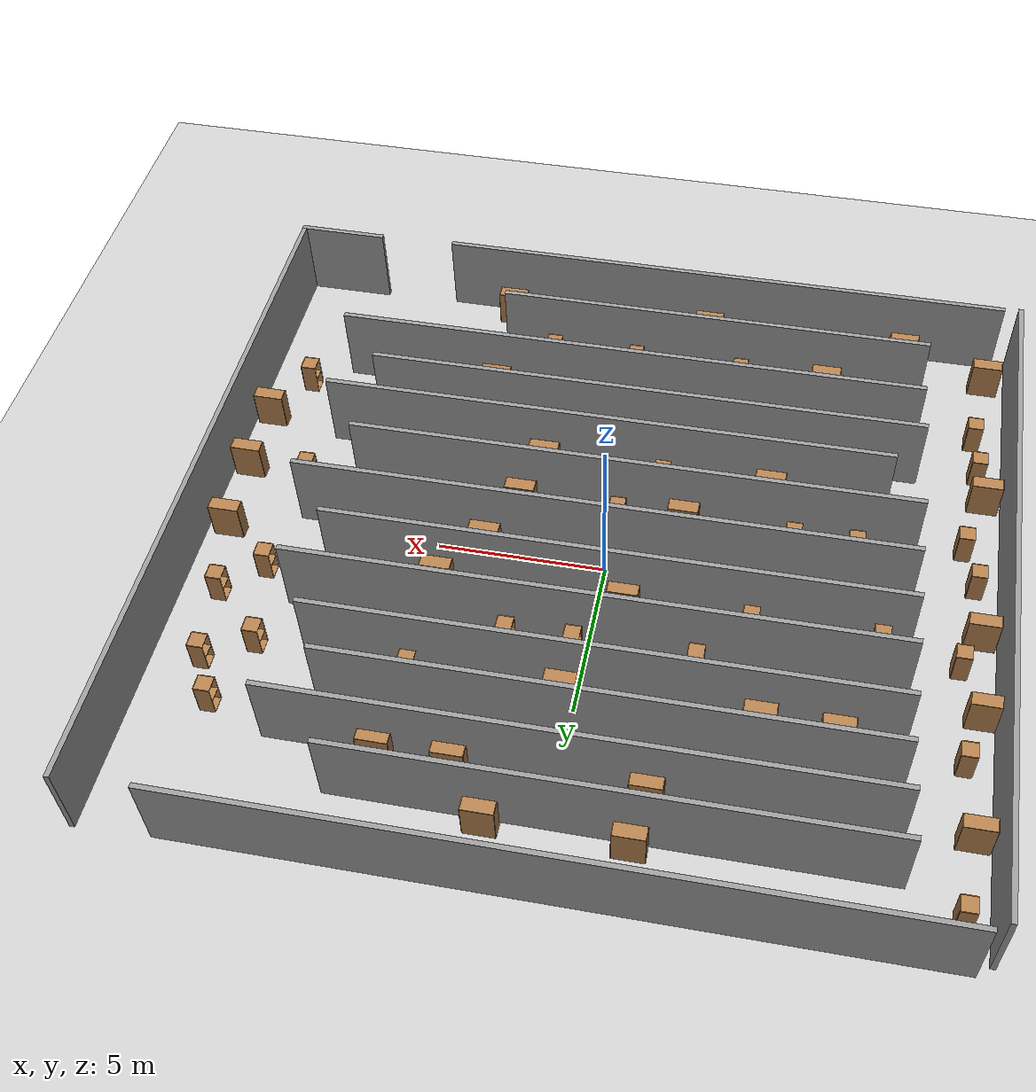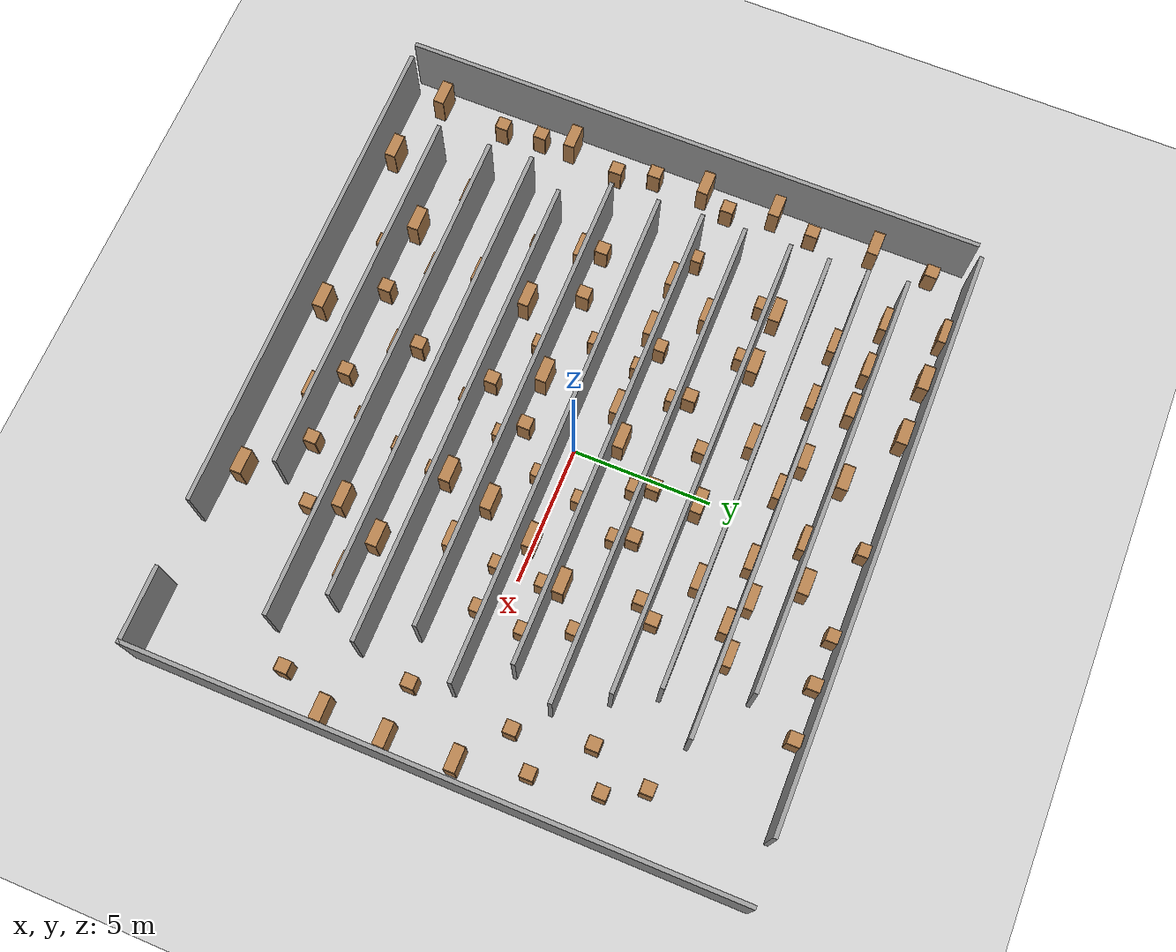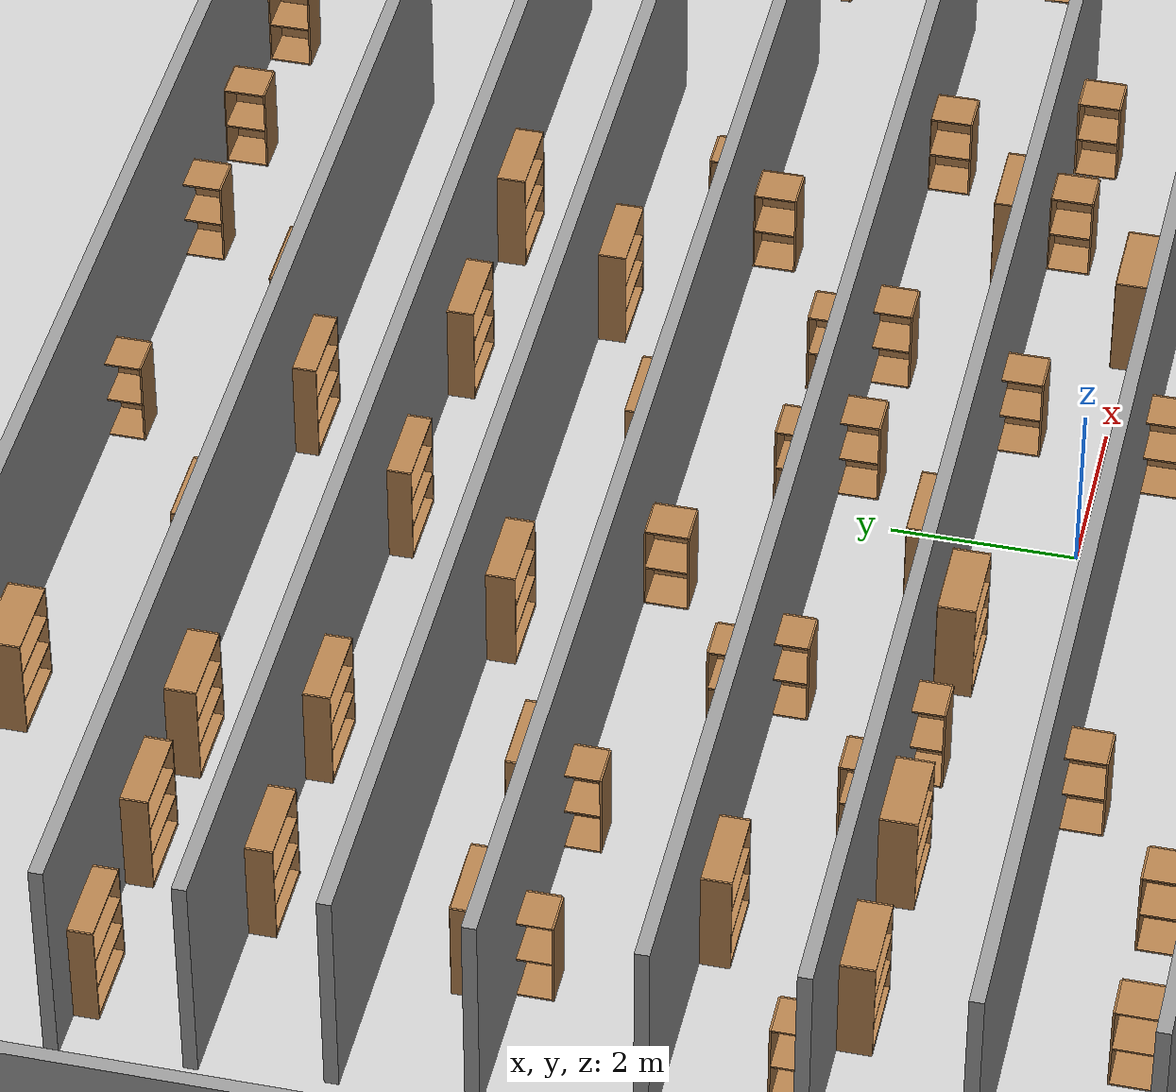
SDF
<sdf version="1.6">
 <world name="default">
  <light name="sun" type="directional">
   <pose>0 0 10 0 -0 0</pose>
   <diffuse>0.8 0.8 0.8 1</diffuse>
   <specular>0.2 0.2 0.2 1</specular>
   <attenuation>
    <range>1000</range>
    <constant>0.9</constant>
    <linear>0.01</linear>
    <quadratic>0.001</quadratic>
   </attenuation>
   <direction>-0.5 0.1 -0.9</direction>
  </light>
  <model name="ground_plane">
   <static>1</static>
   <link name="link">
    <collision name="collision">
     <geometry><plane><normal>0 0 1</normal><size>100 100</size></plane></geometry>
     <surface><friction><ode><mu>100</mu><mu2>50</mu2></ode></friction></surface>
    </collision>
    <visual name="visual">
     <cast_shadows>0</cast_shadows>
     <geometry><plane><normal>0 0 1</normal><size>100 100</size></plane></geometry>
     <material>
      <script><uri>file://media/materials/scripts/gazebo.material</uri><name>Gazebo/Grey</name></script>
     </material>
    </visual>
   </link>
  </model>
  <gravity>0 0 -9.8</gravity>
  <magnetic_field>6e-06 2.3e-05 -4.2e-05</magnetic_field>
  <atmosphere type="adiabatic"/>
  <physics name="default_physics" default="0" type="ode">
   <max_step_size>0.001</max_step_size>
   <real_time_factor>1</real_time_factor>
   <real_time_update_rate>1000</real_time_update_rate>
  </physics>
  <scene><ambient>0.4 0.4 0.4 1</ambient><background>0.7 0.7 0.7 1</background><shadows>1</shadows></scene>
  <audio><device>default</device></audio>
  <spherical_coordinates>
   <surface_model>EARTH_WGS84</surface_model>
   <latitude_deg>0</latitude_deg>
   <longitude_deg>0</longitude_deg>
   <elevation>0</elevation>
   <heading_deg>0</heading_deg>
  </spherical_coordinates>
  <model name="room16">
   <pose>0.320138 -0.0112 0 0 -0 0</pose>
   <link name="Wall_0">
    <collision name="Wall_0_Collision">
     <geometry><box><size>21 0.15 2.5</size></box></geometry>
     <pose>0 0 1.25 0 -0 0</pose>
    </collision>
    <visual name="Wall_0_Visual">
     <pose>0 0 1.25 0 -0 0</pose>
     <geometry><box><size>21 0.15 2.5</size></box></geometry>
     <material>
      <script><uri>file://media/materials/scripts/gazebo.material</uri><name>Gazebo/Grey</name></script>
      <ambient>1 1 1 1</ambient>
     </material>
     <meta><layer>0</layer></meta>
    </visual>
    <pose>-0.858692 10.6507 0 0 -0 0</pose>
   </link>
   <link name="Wall_11">
    <collision name="Wall_11_Collision">
     <geometry><box><size>17.25 0.15 2.5</size></box></geometry>
     <pose>0 0 1.25 0 -0 0</pose>
    </collision>
    <visual name="Wall_11_Visual">
     <pose>0 0 1.25 0 -0 0</pose>
     <geometry><box><size>17.25 0.15 2.5</size></box></geometry>
     <material>
      <script><uri>file://media/materials/scripts/gazebo.material</uri><name>Gazebo/Grey</name></script>
      <ambient>1 1 1 1</ambient>
     </material>
     <meta><layer>0</layer></meta>
    </visual>
    <pose>-0.822582 7.21897 0 0 -0 0</pose>
   </link>
   <link name="Wall_13">
    <collision name="Wall_13_Collision">
     <geometry><box><size>16 0.15 2.5</size></box></geometry>
     <pose>0 0 1.25 0 -0 0</pose>
    </collision>
    <visual name="Wall_13_Visual">
     <pose>0 0 1.25 0 -0 0</pose>
     <geometry><box><size>16 0.15 2.5</size></box></geometry>
     <material>
      <script><uri>file://media/materials/scripts/gazebo.material</uri><name>Gazebo/Grey</name></script>
      <ambient>1 1 1 1</ambient>
     </material>
     <meta><layer>0</layer></meta>
    </visual>
    <pose>-1.33193 5.83113 0 0 -0 0</pose>
   </link>
   <link name="Wall_16">
    <collision name="Wall_16_Collision">
     <geometry><box><size>16.75 0.15 2.5</size></box></geometry>
     <pose>0 0 1.25 0 -0 0</pose>
    </collision>
    <visual name="Wall_16_Visual">
     <pose>0 0 1.25 0 -0 0</pose>
     <geometry><box><size>16.75 0.15 2.5</size></box></geometry>
     <material>
      <script><uri>file://media/materials/scripts/gazebo.material</uri><name>Gazebo/Grey</name></script>
      <ambient>1 1 1 1</ambient>
     </material>
     <meta><layer>0</layer></meta>
    </visual>
    <pose>-0.956929 4.42016 0 0 -0 0</pose>
   </link>
   <link name="Wall_18">
    <collision name="Wall_18_Collision">
     <geometry><box><size>17.75 0.15 2.5</size></box></geometry>
     <pose>0 0 1.25 0 -0 0</pose>
    </collision>
    <visual name="Wall_18_Visual">
     <pose>0 0 1.25 0 -0 0</pose>
     <geometry><box><size>17.75 0.15 2.5</size></box></geometry>
     <material>
      <script><uri>file://media/materials/scripts/gazebo.material</uri><name>Gazebo/Grey</name></script>
      <ambient>1 1 1 1</ambient>
     </material>
     <meta><layer>0</layer></meta>
    </visual>
    <pose>-0.433798 2.75476 0 0 -0 0</pose>
   </link>
   <link name="Wall_2">
    <collision name="Wall_2_Collision">
     <geometry><box><size>21.25 0.15 2.5</size></box></geometry>
     <pose>0 0 1.25 0 -0 0</pose>
    </collision>
    <visual name="Wall_2_Visual">
     <pose>0 0 1.25 0 -0 0</pose>
     <geometry><box><size>21.25 0.15 2.5</size></box></geometry>
     <material>
      <script><uri>file://media/materials/scripts/gazebo.material</uri><name>Gazebo/Grey</name></script>
      <ambient>1 1 1 1</ambient>
     </material>
     <meta><layer>0</layer></meta>
    </visual>
    <pose>-11.755 -0.18527 0 0 -0 -1.5708</pose>
   </link>
   <link name="Wall_20">
    <collision name="Wall_20_Collision">
     <geometry><box><size>17 0.15 2.5</size></box></geometry>
     <pose>0 0 1.25 0 -0 0</pose>
    </collision>
    <visual name="Wall_20_Visual">
     <pose>0 0 1.25 0 -0 0</pose>
     <geometry><box><size>17 0.15 2.5</size></box></geometry>
     <material>
      <script><uri>file://media/materials/scripts/gazebo.material</uri><name>Gazebo/Grey</name></script>
      <ambient>1 1 1 1</ambient>
     </material>
     <meta><layer>0</layer></meta>
    </visual>
    <pose>-0.762537 1.20501 0 0 -0 0</pose>
   </link>
   <link name="Wall_22">
    <collision name="Wall_22_Collision">
     <geometry><box><size>18.25 0.15 2.5</size></box></geometry>
     <pose>0 0 1.25 0 -0 0</pose>
    </collision>
    <visual name="Wall_22_Visual">
     <pose>0 0 1.25 0 -0 0</pose>
     <geometry><box><size>18.25 0.15 2.5</size></box></geometry>
     <material>
      <script><uri>file://media/materials/scripts/gazebo.material</uri><name>Gazebo/Grey</name></script>
      <ambient>1 1 1 1</ambient>
     </material>
     <meta><layer>0</layer></meta>
    </visual>
    <pose>-0.091276 -0.414133 0 0 -0 0</pose>
   </link>
   <link name="Wall_25">
    <collision name="Wall_25_Collision">
     <geometry><box><size>17 0.15 2.5</size></box></geometry>
     <pose>0 0 1.25 0 -0 0</pose>
    </collision>
    <visual name="Wall_25_Visual">
     <pose>0 0 1.25 0 -0 0</pose>
     <geometry><box><size>17 0.15 2.5</size></box></geometry>
     <material>
      <script><uri>file://media/materials/scripts/gazebo.material</uri><name>Gazebo/Grey</name></script>
      <ambient>1 1 1 1</ambient>
     </material>
     <meta><layer>0</layer></meta>
    </visual>
    <pose>-0.716276 -2.17206 0 0 -0 0</pose>
   </link>
   <link name="Wall_27">
    <collision name="Wall_27_Collision">
     <geometry><box><size>17.25 0.15 2.5</size></box></geometry>
     <pose>0 0 1.25 0 -0 0</pose>
    </collision>
    <visual name="Wall_27_Visual">
     <pose>0 0 1.25 0 -0 0</pose>
     <geometry><box><size>17.25 0.15 2.5</size></box></geometry>
     <material>
      <script><uri>file://media/materials/scripts/gazebo.material</uri><name>Gazebo/Grey</name></script>
      <ambient>1 1 1 1</ambient>
     </material>
     <meta><layer>0</layer></meta>
    </visual>
    <pose>0.357079 -3.7912 0 0 -0 0</pose>
   </link>
   <link name="Wall_29">
    <collision name="Wall_29_Collision">
     <geometry><box><size>17 0.15 2.5</size></box></geometry>
     <pose>0 0 1.25 0 -0 0</pose>
    </collision>
    <visual name="Wall_29_Visual">
     <pose>0 0 1.25 0 -0 0</pose>
     <geometry><box><size>17 0.15 2.5</size></box></geometry>
     <material>
      <script><uri>file://media/materials/scripts/gazebo.material</uri><name>Gazebo/Grey</name></script>
      <ambient>1 1 1 1</ambient>
     </material>
     <meta><layer>0</layer></meta>
    </visual>
    <pose>-0.600623 -5.15591 0 0 -0 0</pose>
   </link>
   <link name="Wall_31">
    <collision name="Wall_31_Collision">
     <geometry><box><size>18.25 0.15 2.5</size></box></geometry>
     <pose>0 0 1.25 0 -0 0</pose>
    </collision>
    <visual name="Wall_31_Visual">
     <pose>0 0 1.25 0 -0 0</pose>
     <geometry><box><size>18.25 0.15 2.5</size></box></geometry>
     <material>
      <script><uri>file://media/materials/scripts/gazebo.material</uri><name>Gazebo/Grey</name></script>
      <ambient>1 1 1 1</ambient>
     </material>
     <meta><layer>0</layer></meta>
    </visual>
    <pose>0.14003 -6.72879 0 0 -0 0</pose>
   </link>
   <link name="Wall_33">
    <collision name="Wall_33_Collision">
     <geometry><box><size>13.5 0.15 2.5</size></box></geometry>
     <pose>0 0 1.25 0 -0 0</pose>
    </collision>
    <visual name="Wall_33_Visual">
     <pose>0 0 1.25 0 -0 0</pose>
     <geometry><box><size>13.5 0.15 2.5</size></box></geometry>
     <material>
      <script><uri>file://media/materials/scripts/gazebo.material</uri><name>Gazebo/Grey</name></script>
      <ambient>1 1 1 1</ambient>
     </material>
     <meta><layer>0</layer></meta>
    </visual>
    <pose>-2.2581 -8.67176 0 0 -0 0</pose>
   </link>
   <link name="Wall_4">
    <collision name="Wall_4_Collision">
     <geometry><box><size>18 0.15 2.5</size></box></geometry>
     <pose>0 0 1.25 0 -0 0</pose>
    </collision>
    <visual name="Wall_4_Visual">
     <pose>0 0 1.25 0 -0 0</pose>
     <geometry><box><size>18 0.15 2.5</size></box></geometry>
     <material>
      <script><uri>file://media/materials/scripts/gazebo.material</uri><name>Gazebo/Grey</name></script>
      <ambient>1 1 1 1</ambient>
     </material>
     <meta><layer>0</layer></meta>
    </visual>
    <pose>-2.25177 -10.7073 0 0 -0 0</pose>
   </link>
   <link name="Wall_6">
    <collision name="Wall_6_Collision">
     <geometry><box><size>2.75 0.15 2.5</size></box></geometry>
     <pose>0 0 1.25 0 -0 0</pose>
    </collision>
    <visual name="Wall_6_Visual">
     <pose>0 0 1.25 0 -0 0</pose>
     <geometry><box><size>2.75 0.15 2.5</size></box></geometry>
     <material>
      <script><uri>file://media/materials/scripts/gazebo.material</uri><name>Gazebo/Grey</name></script>
      <ambient>1 1 1 1</ambient>
     </material>
     <meta><layer>0</layer></meta>
    </visual>
    <pose>10.455 -10.6147 0 0 -0 0</pose>
   </link>
   <link name="Wall_7">
    <collision name="Wall_7_Collision">
     <geometry><box><size>21.5 0.15 2.5</size></box></geometry>
     <pose>0 0 1.25 0 -0 0</pose>
    </collision>
    <visual name="Wall_7_Visual">
     <pose>0 0 1.25 0 -0 0</pose>
     <geometry><box><size>21.5 0.15 2.5</size></box></geometry>
     <material>
      <script><uri>file://media/materials/scripts/gazebo.material</uri><name>Gazebo/Grey</name></script>
      <ambient>1 1 1 1</ambient>
     </material>
     <meta><layer>0</layer></meta>
    </visual>
    <pose>11.755 0.060269 0 0 -0 1.5708</pose>
   </link>
   <link name="Wall_9">
    <collision name="Wall_9_Collision">
     <geometry><box><size>15.25 0.15 2.5</size></box></geometry>
     <pose>0 0 1.25 0 -0 0</pose>
    </collision>
    <visual name="Wall_9_Visual">
     <pose>0 0 1.25 0 -0 0</pose>
     <geometry><box><size>15.25 0.15 2.5</size></box></geometry>
     <material>
      <script><uri>file://media/materials/scripts/gazebo.material</uri><name>Gazebo/Grey</name></script>
      <ambient>1 1 1 1</ambient>
     </material>
     <meta><layer>0</layer></meta>
    </visual>
    <pose>-1.9151 8.6068 0 0 -0 0</pose>
   </link>
   <static>1</static>
  </model>
  <model name="bookshelf_0">
   <static>1</static>
   <link name="link">
    <inertial><mass>1</mass></inertial>
    <collision name="back">
     <pose>0 0.005 0.6 0 -0 0</pose>
     <geometry><box><size>0.9 0.01 1.2</size></box></geometry>
    </collision>
    <visual name="visual1">
     <pose>0 0.005 0.6 0 -0 0</pose>
     <geometry><box><size>0.9 0.01 1.2</size></box></geometry>
     <material>
      <script><uri>file://media/materials/scripts/gazebo.material</uri><name>Gazebo/Wood</name></script>
     </material>
    </visual>
    <collision name="left_side">
     <pose>0.45 -0.195 0.6 0 -0 0</pose>
     <geometry><box><size>0.02 0.4 1.2</size></box></geometry>
    </collision>
    <visual name="visual2">
     <pose>0.45 -0.195 0.6 0 -0 0</pose>
     <geometry><box><size>0.02 0.4 1.2</size></box></geometry>
     <material>
      <script><uri>file://media/materials/scripts/gazebo.material</uri><name>Gazebo/Wood</name></script>
     </material>
    </visual>
    <collision name="right_side">
     <pose>-0.45 -0.195 0.6 0 -0 0</pose>
     <geometry><box><size>0.02 0.4 1.2</size></box></geometry>
    </collision>
    <visual name="visual3">
     <pose>-0.45 -0.195 0.6 0 -0 0</pose>
     <geometry><box><size>0.02 0.4 1.2</size></box></geometry>
     <material>
      <script><uri>file://media/materials/scripts/gazebo.material</uri><name>Gazebo/Wood</name></script>
     </material>
    </visual>
    <collision name="bottom">
     <pose>0 -0.195 0.03 0 -0 0</pose>
     <geometry><box><size>0.88 0.4 0.06</size></box></geometry>
    </collision>
    <visual name="visual4">
     <pose>0 -0.195 0.03 0 -0 0</pose>
     <geometry><box><size>0.88 0.4 0.06</size></box></geometry>
     <material>
      <script><uri>file://media/materials/scripts/gazebo.material</uri><name>Gazebo/Wood</name></script>
     </material>
    </visual>
    <collision name="top">
     <pose>0 -0.195 1.19 0 -0 0</pose>
     <geometry><box><size>0.88 0.4 0.02</size></box></geometry>
    </collision>
    <visual name="visual5">
     <pose>0 -0.195 1.19 0 -0 0</pose>
     <geometry><box><size>0.88 0.4 0.02</size></box></geometry>
     <material>
      <script><uri>file://media/materials/scripts/gazebo.material</uri><name>Gazebo/Wood</name></script>
     </material>
    </visual>
    <collision name="low_shelf">
     <pose>0 -0.195 0.43 0 -0 0</pose>
     <geometry><box><size>0.88 0.4 0.02</size></box></geometry>
    </collision>
    <visual name="visual6">
     <pose>0 -0.195 0.43 0 -0 0</pose>
     <geometry><box><size>0.88 0.4 0.02</size></box></geometry>
     <material>
      <script><uri>file://media/materials/scripts/gazebo.material</uri><name>Gazebo/Wood</name></script>
     </material>
    </visual>
    <collision name="high_shelf">
     <pose>0 -0.195 0.8 0 -0 0</pose>
     <geometry><box><size>0.88 0.4 0.02</size></box></geometry>
    </collision>
    <visual name="visual7">
     <pose>0 -0.195 0.8 0 -0 0</pose>
     <geometry><box><size>0.88 0.4 0.02</size></box></geometry>
     <material>
      <script><uri>file://media/materials/scripts/gazebo.material</uri><name>Gazebo/Wood</name></script>
     </material>
    </visual>
   </link>
   <pose>-6.38557 8.62302 0 0 -0 0</pose>
  </model>
  <model name="bookshelf">
   <static>1</static>
   <link name="link">
    <inertial><mass>1</mass></inertial>
    <collision name="back">
     <pose>0 0.005 0.6 0 -0 0</pose>
     <geometry><box><size>0.9 0.01 1.2</size></box></geometry>
    </collision>
    <visual name="visual1">
     <pose>0 0.005 0.6 0 -0 0</pose>
     <geometry><box><size>0.9 0.01 1.2</size></box></geometry>
     <material>
      <script><uri>file://media/materials/scripts/gazebo.material</uri><name>Gazebo/Wood</name></script>
     </material>
    </visual>
    <collision name="left_side">
     <pose>0.45 -0.195 0.6 0 -0 0</pose>
     <geometry><box><size>0.02 0.4 1.2</size></box></geometry>
    </collision>
    <visual name="visual2">
     <pose>0.45 -0.195 0.6 0 -0 0</pose>
     <geometry><box><size>0.02 0.4 1.2</size></box></geometry>
     <material>
      <script><uri>file://media/materials/scripts/gazebo.material</uri><name>Gazebo/Wood</name></script>
     </material>
    </visual>
    <collision name="right_side">
     <pose>-0.45 -0.195 0.6 0 -0 0</pose>
     <geometry><box><size>0.02 0.4 1.2</size></box></geometry>
    </collision>
    <visual name="visual3">
     <pose>-0.45 -0.195 0.6 0 -0 0</pose>
     <geometry><box><size>0.02 0.4 1.2</size></box></geometry>
     <material>
      <script><uri>file://media/materials/scripts/gazebo.material</uri><name>Gazebo/Wood</name></script>
     </material>
    </visual>
    <collision name="bottom">
     <pose>0 -0.195 0.03 0 -0 0</pose>
     <geometry><box><size>0.88 0.4 0.06</size></box></geometry>
    </collision>
    <visual name="visual4">
     <pose>0 -0.195 0.03 0 -0 0</pose>
     <geometry><box><size>0.88 0.4 0.06</size></box></geometry>
     <material>
      <script><uri>file://media/materials/scripts/gazebo.material</uri><name>Gazebo/Wood</name></script>
     </material>
    </visual>
    <collision name="top">
     <pose>0 -0.195 1.19 0 -0 0</pose>
     <geometry><box><size>0.88 0.4 0.02</size></box></geometry>
    </collision>
    <visual name="visual5">
     <pose>0 -0.195 1.19 0 -0 0</pose>
     <geometry><box><size>0.88 0.4 0.02</size></box></geometry>
     <material>
      <script><uri>file://media/materials/scripts/gazebo.material</uri><name>Gazebo/Wood</name></script>
     </material>
    </visual>
    <collision name="low_shelf">
     <pose>0 -0.195 0.43 0 -0 0</pose>
     <geometry><box><size>0.88 0.4 0.02</size></box></geometry>
    </collision>
    <visual name="visual6">
     <pose>0 -0.195 0.43 0 -0 0</pose>
     <geometry><box><size>0.88 0.4 0.02</size></box></geometry>
     <material>
      <script><uri>file://media/materials/scripts/gazebo.material</uri><name>Gazebo/Wood</name></script>
     </material>
    </visual>
    <collision name="high_shelf">
     <pose>0 -0.195 0.8 0 -0 0</pose>
     <geometry><box><size>0.88 0.4 0.02</size></box></geometry>
    </collision>
    <visual name="visual7">
     <pose>0 -0.195 0.8 0 -0 0</pose>
     <geometry><box><size>0.88 0.4 0.02</size></box></geometry>
     <material>
      <script><uri>file://media/materials/scripts/gazebo.material</uri><name>Gazebo/Wood</name></script>
     </material>
    </visual>
   </link>
   <pose>-8.2369 8.65056 0 0 -0 0</pose>
  </model>
  <model name="bookshelf_1">
   <static>1</static>
   <link name="link">
    <inertial><mass>1</mass></inertial>
    <collision name="back">
     <pose>0 0.005 0.6 0 -0 0</pose>
     <geometry><box><size>0.9 0.01 1.2</size></box></geometry>
    </collision>
    <visual name="visual1">
     <pose>0 0.005 0.6 0 -0 0</pose>
     <geometry><box><size>0.9 0.01 1.2</size></box></geometry>
     <material>
      <script><uri>file://media/materials/scripts/gazebo.material</uri><name>Gazebo/Wood</name></script>
     </material>
    </visual>
    <collision name="left_side">
     <pose>0.45 -0.195 0.6 0 -0 0</pose>
     <geometry><box><size>0.02 0.4 1.2</size></box></geometry>
    </collision>
    <visual name="visual2">
     <pose>0.45 -0.195 0.6 0 -0 0</pose>
     <geometry><box><size>0.02 0.4 1.2</size></box></geometry>
     <material>
      <script><uri>file://media/materials/scripts/gazebo.material</uri><name>Gazebo/Wood</name></script>
     </material>
    </visual>
    <collision name="right_side">
     <pose>-0.45 -0.195 0.6 0 -0 0</pose>
     <geometry><box><size>0.02 0.4 1.2</size></box></geometry>
    </collision>
    <visual name="visual3">
     <pose>-0.45 -0.195 0.6 0 -0 0</pose>
     <geometry><box><size>0.02 0.4 1.2</size></box></geometry>
     <material>
      <script><uri>file://media/materials/scripts/gazebo.material</uri><name>Gazebo/Wood</name></script>
     </material>
    </visual>
    <collision name="bottom">
     <pose>0 -0.195 0.03 0 -0 0</pose>
     <geometry><box><size>0.88 0.4 0.06</size></box></geometry>
    </collision>
    <visual name="visual4">
     <pose>0 -0.195 0.03 0 -0 0</pose>
     <geometry><box><size>0.88 0.4 0.06</size></box></geometry>
     <material>
      <script><uri>file://media/materials/scripts/gazebo.material</uri><name>Gazebo/Wood</name></script>
     </material>
    </visual>
    <collision name="top">
     <pose>0 -0.195 1.19 0 -0 0</pose>
     <geometry><box><size>0.88 0.4 0.02</size></box></geometry>
    </collision>
    <visual name="visual5">
     <pose>0 -0.195 1.19 0 -0 0</pose>
     <geometry><box><size>0.88 0.4 0.02</size></box></geometry>
     <material>
      <script><uri>file://media/materials/scripts/gazebo.material</uri><name>Gazebo/Wood</name></script>
     </material>
    </visual>
    <collision name="low_shelf">
     <pose>0 -0.195 0.43 0 -0 0</pose>
     <geometry><box><size>0.88 0.4 0.02</size></box></geometry>
    </collision>
    <visual name="visual6">
     <pose>0 -0.195 0.43 0 -0 0</pose>
     <geometry><box><size>0.88 0.4 0.02</size></box></geometry>
     <material>
      <script><uri>file://media/materials/scripts/gazebo.material</uri><name>Gazebo/Wood</name></script>
     </material>
    </visual>
    <collision name="high_shelf">
     <pose>0 -0.195 0.8 0 -0 0</pose>
     <geometry><box><size>0.88 0.4 0.02</size></box></geometry>
    </collision>
    <visual name="visual7">
     <pose>0 -0.195 0.8 0 -0 0</pose>
     <geometry><box><size>0.88 0.4 0.02</size></box></geometry>
     <material>
      <script><uri>file://media/materials/scripts/gazebo.material</uri><name>Gazebo/Wood</name></script>
     </material>
    </visual>
   </link>
   <pose>-4.77804 8.57789 0 0 -0 0</pose>
  </model>
  <model name="bookshelf_2">
   <static>1</static>
   <link name="link">
    <inertial><mass>1</mass></inertial>
    <collision name="back">
     <pose>0 0.005 0.6 0 -0 0</pose>
     <geometry><box><size>0.9 0.01 1.2</size></box></geometry>
    </collision>
    <visual name="visual1">
     <pose>0 0.005 0.6 0 -0 0</pose>
     <geometry><box><size>0.9 0.01 1.2</size></box></geometry>
     <material>
      <script><uri>file://media/materials/scripts/gazebo.material</uri><name>Gazebo/Wood</name></script>
     </material>
    </visual>
    <collision name="left_side">
     <pose>0.45 -0.195 0.6 0 -0 0</pose>
     <geometry><box><size>0.02 0.4 1.2</size></box></geometry>
    </collision>
    <visual name="visual2">
     <pose>0.45 -0.195 0.6 0 -0 0</pose>
     <geometry><box><size>0.02 0.4 1.2</size></box></geometry>
     <material>
      <script><uri>file://media/materials/scripts/gazebo.material</uri><name>Gazebo/Wood</name></script>
     </material>
    </visual>
    <collision name="right_side">
     <pose>-0.45 -0.195 0.6 0 -0 0</pose>
     <geometry><box><size>0.02 0.4 1.2</size></box></geometry>
    </collision>
    <visual name="visual3">
     <pose>-0.45 -0.195 0.6 0 -0 0</pose>
     <geometry><box><size>0.02 0.4 1.2</size></box></geometry>
     <material>
      <script><uri>file://media/materials/scripts/gazebo.material</uri><name>Gazebo/Wood</name></script>
     </material>
    </visual>
    <collision name="bottom">
     <pose>0 -0.195 0.03 0 -0 0</pose>
     <geometry><box><size>0.88 0.4 0.06</size></box></geometry>
    </collision>
    <visual name="visual4">
     <pose>0 -0.195 0.03 0 -0 0</pose>
     <geometry><box><size>0.88 0.4 0.06</size></box></geometry>
     <material>
      <script><uri>file://media/materials/scripts/gazebo.material</uri><name>Gazebo/Wood</name></script>
     </material>
    </visual>
    <collision name="top">
     <pose>0 -0.195 1.19 0 -0 0</pose>
     <geometry><box><size>0.88 0.4 0.02</size></box></geometry>
    </collision>
    <visual name="visual5">
     <pose>0 -0.195 1.19 0 -0 0</pose>
     <geometry><box><size>0.88 0.4 0.02</size></box></geometry>
     <material>
      <script><uri>file://media/materials/scripts/gazebo.material</uri><name>Gazebo/Wood</name></script>
     </material>
    </visual>
    <collision name="low_shelf">
     <pose>0 -0.195 0.43 0 -0 0</pose>
     <geometry><box><size>0.88 0.4 0.02</size></box></geometry>
    </collision>
    <visual name="visual6">
     <pose>0 -0.195 0.43 0 -0 0</pose>
     <geometry><box><size>0.88 0.4 0.02</size></box></geometry>
     <material>
      <script><uri>file://media/materials/scripts/gazebo.material</uri><name>Gazebo/Wood</name></script>
     </material>
    </visual>
    <collision name="high_shelf">
     <pose>0 -0.195 0.8 0 -0 0</pose>
     <geometry><box><size>0.88 0.4 0.02</size></box></geometry>
    </collision>
    <visual name="visual7">
     <pose>0 -0.195 0.8 0 -0 0</pose>
     <geometry><box><size>0.88 0.4 0.02</size></box></geometry>
     <material>
      <script><uri>file://media/materials/scripts/gazebo.material</uri><name>Gazebo/Wood</name></script>
     </material>
    </visual>
   </link>
   <pose>-2.41754 7.64902 0 0 -0 0</pose>
  </model>
  <model name="bookshelf_3">
   <static>1</static>
   <link name="link">
    <inertial><mass>1</mass></inertial>
    <collision name="back">
     <pose>0 0.005 0.6 0 -0 0</pose>
     <geometry><box><size>0.9 0.01 1.2</size></box></geometry>
    </collision>
    <visual name="visual1">
     <pose>0 0.005 0.6 0 -0 0</pose>
     <geometry><box><size>0.9 0.01 1.2</size></box></geometry>
     <material>
      <script><uri>file://media/materials/scripts/gazebo.material</uri><name>Gazebo/Wood</name></script>
     </material>
    </visual>
    <collision name="left_side">
     <pose>0.45 -0.195 0.6 0 -0 0</pose>
     <geometry><box><size>0.02 0.4 1.2</size></box></geometry>
    </collision>
    <visual name="visual2">
     <pose>0.45 -0.195 0.6 0 -0 0</pose>
     <geometry><box><size>0.02 0.4 1.2</size></box></geometry>
     <material>
      <script><uri>file://media/materials/scripts/gazebo.material</uri><name>Gazebo/Wood</name></script>
     </material>
    </visual>
    <collision name="right_side">
     <pose>-0.45 -0.195 0.6 0 -0 0</pose>
     <geometry><box><size>0.02 0.4 1.2</size></box></geometry>
    </collision>
    <visual name="visual3">
     <pose>-0.45 -0.195 0.6 0 -0 0</pose>
     <geometry><box><size>0.02 0.4 1.2</size></box></geometry>
     <material>
      <script><uri>file://media/materials/scripts/gazebo.material</uri><name>Gazebo/Wood</name></script>
     </material>
    </visual>
    <collision name="bottom">
     <pose>0 -0.195 0.03 0 -0 0</pose>
     <geometry><box><size>0.88 0.4 0.06</size></box></geometry>
    </collision>
    <visual name="visual4">
     <pose>0 -0.195 0.03 0 -0 0</pose>
     <geometry><box><size>0.88 0.4 0.06</size></box></geometry>
     <material>
      <script><uri>file://media/materials/scripts/gazebo.material</uri><name>Gazebo/Wood</name></script>
     </material>
    </visual>
    <collision name="top">
     <pose>0 -0.195 1.19 0 -0 0</pose>
     <geometry><box><size>0.88 0.4 0.02</size></box></geometry>
    </collision>
    <visual name="visual5">
     <pose>0 -0.195 1.19 0 -0 0</pose>
     <geometry><box><size>0.88 0.4 0.02</size></box></geometry>
     <material>
      <script><uri>file://media/materials/scripts/gazebo.material</uri><name>Gazebo/Wood</name></script>
     </material>
    </visual>
    <collision name="low_shelf">
     <pose>0 -0.195 0.43 0 -0 0</pose>
     <geometry><box><size>0.88 0.4 0.02</size></box></geometry>
    </collision>
    <visual name="visual6">
     <pose>0 -0.195 0.43 0 -0 0</pose>
     <geometry><box><size>0.88 0.4 0.02</size></box></geometry>
     <material>
      <script><uri>file://media/materials/scripts/gazebo.material</uri><name>Gazebo/Wood</name></script>
     </material>
    </visual>
    <collision name="high_shelf">
     <pose>0 -0.195 0.8 0 -0 0</pose>
     <geometry><box><size>0.88 0.4 0.02</size></box></geometry>
    </collision>
    <visual name="visual7">
     <pose>0 -0.195 0.8 0 -0 0</pose>
     <geometry><box><size>0.88 0.4 0.02</size></box></geometry>
     <material>
      <script><uri>file://media/materials/scripts/gazebo.material</uri><name>Gazebo/Wood</name></script>
     </material>
    </visual>
   </link>
   <pose>0.282204 8.65542 0 0 -0 0</pose>
  </model>
  <model name="bookshelf_4">
   <static>1</static>
   <link name="link">
    <inertial><mass>1</mass></inertial>
    <collision name="back">
     <pose>0 0.005 0.6 0 -0 0</pose>
     <geometry><box><size>0.9 0.01 1.2</size></box></geometry>
    </collision>
    <visual name="visual1">
     <pose>0 0.005 0.6 0 -0 0</pose>
     <geometry><box><size>0.9 0.01 1.2</size></box></geometry>
     <material>
      <script><uri>file://media/materials/scripts/gazebo.material</uri><name>Gazebo/Wood</name></script>
     </material>
    </visual>
    <collision name="left_side">
     <pose>0.45 -0.195 0.6 0 -0 0</pose>
     <geometry><box><size>0.02 0.4 1.2</size></box></geometry>
    </collision>
    <visual name="visual2">
     <pose>0.45 -0.195 0.6 0 -0 0</pose>
     <geometry><box><size>0.02 0.4 1.2</size></box></geometry>
     <material>
      <script><uri>file://media/materials/scripts/gazebo.material</uri><name>Gazebo/Wood</name></script>
     </material>
    </visual>
    <collision name="right_side">
     <pose>-0.45 -0.195 0.6 0 -0 0</pose>
     <geometry><box><size>0.02 0.4 1.2</size></box></geometry>
    </collision>
    <visual name="visual3">
     <pose>-0.45 -0.195 0.6 0 -0 0</pose>
     <geometry><box><size>0.02 0.4 1.2</size></box></geometry>
     <material>
      <script><uri>file://media/materials/scripts/gazebo.material</uri><name>Gazebo/Wood</name></script>
     </material>
    </visual>
    <collision name="bottom">
     <pose>0 -0.195 0.03 0 -0 0</pose>
     <geometry><box><size>0.88 0.4 0.06</size></box></geometry>
    </collision>
    <visual name="visual4">
     <pose>0 -0.195 0.03 0 -0 0</pose>
     <geometry><box><size>0.88 0.4 0.06</size></box></geometry>
     <material>
      <script><uri>file://media/materials/scripts/gazebo.material</uri><name>Gazebo/Wood</name></script>
     </material>
    </visual>
    <collision name="top">
     <pose>0 -0.195 1.19 0 -0 0</pose>
     <geometry><box><size>0.88 0.4 0.02</size></box></geometry>
    </collision>
    <visual name="visual5">
     <pose>0 -0.195 1.19 0 -0 0</pose>
     <geometry><box><size>0.88 0.4 0.02</size></box></geometry>
     <material>
      <script><uri>file://media/materials/scripts/gazebo.material</uri><name>Gazebo/Wood</name></script>
     </material>
    </visual>
    <collision name="low_shelf">
     <pose>0 -0.195 0.43 0 -0 0</pose>
     <geometry><box><size>0.88 0.4 0.02</size></box></geometry>
    </collision>
    <visual name="visual6">
     <pose>0 -0.195 0.43 0 -0 0</pose>
     <geometry><box><size>0.88 0.4 0.02</size></box></geometry>
     <material>
      <script><uri>file://media/materials/scripts/gazebo.material</uri><name>Gazebo/Wood</name></script>
     </material>
    </visual>
    <collision name="high_shelf">
     <pose>0 -0.195 0.8 0 -0 0</pose>
     <geometry><box><size>0.88 0.4 0.02</size></box></geometry>
    </collision>
    <visual name="visual7">
     <pose>0 -0.195 0.8 0 -0 0</pose>
     <geometry><box><size>0.88 0.4 0.02</size></box></geometry>
     <material>
      <script><uri>file://media/materials/scripts/gazebo.material</uri><name>Gazebo/Wood</name></script>
     </material>
    </visual>
   </link>
   <pose>2.82667 7.63192 0 0 -0 0</pose>
  </model>
  <model name="bookshelf_5">
   <static>1</static>
   <link name="link">
    <inertial><mass>1</mass></inertial>
    <collision name="back">
     <pose>0 0.005 0.6 0 -0 0</pose>
     <geometry><box><size>0.9 0.01 1.2</size></box></geometry>
    </collision>
    <visual name="visual1">
     <pose>0 0.005 0.6 0 -0 0</pose>
     <geometry><box><size>0.9 0.01 1.2</size></box></geometry>
     <material>
      <script><uri>file://media/materials/scripts/gazebo.material</uri><name>Gazebo/Wood</name></script>
     </material>
    </visual>
    <collision name="left_side">
     <pose>0.45 -0.195 0.6 0 -0 0</pose>
     <geometry><box><size>0.02 0.4 1.2</size></box></geometry>
    </collision>
    <visual name="visual2">
     <pose>0.45 -0.195 0.6 0 -0 0</pose>
     <geometry><box><size>0.02 0.4 1.2</size></box></geometry>
     <material>
      <script><uri>file://media/materials/scripts/gazebo.material</uri><name>Gazebo/Wood</name></script>
     </material>
    </visual>
    <collision name="right_side">
     <pose>-0.45 -0.195 0.6 0 -0 0</pose>
     <geometry><box><size>0.02 0.4 1.2</size></box></geometry>
    </collision>
    <visual name="visual3">
     <pose>-0.45 -0.195 0.6 0 -0 0</pose>
     <geometry><box><size>0.02 0.4 1.2</size></box></geometry>
     <material>
      <script><uri>file://media/materials/scripts/gazebo.material</uri><name>Gazebo/Wood</name></script>
     </material>
    </visual>
    <collision name="bottom">
     <pose>0 -0.195 0.03 0 -0 0</pose>
     <geometry><box><size>0.88 0.4 0.06</size></box></geometry>
    </collision>
    <visual name="visual4">
     <pose>0 -0.195 0.03 0 -0 0</pose>
     <geometry><box><size>0.88 0.4 0.06</size></box></geometry>
     <material>
      <script><uri>file://media/materials/scripts/gazebo.material</uri><name>Gazebo/Wood</name></script>
     </material>
    </visual>
    <collision name="top">
     <pose>0 -0.195 1.19 0 -0 0</pose>
     <geometry><box><size>0.88 0.4 0.02</size></box></geometry>
    </collision>
    <visual name="visual5">
     <pose>0 -0.195 1.19 0 -0 0</pose>
     <geometry><box><size>0.88 0.4 0.02</size></box></geometry>
     <material>
      <script><uri>file://media/materials/scripts/gazebo.material</uri><name>Gazebo/Wood</name></script>
     </material>
    </visual>
    <collision name="low_shelf">
     <pose>0 -0.195 0.43 0 -0 0</pose>
     <geometry><box><size>0.88 0.4 0.02</size></box></geometry>
    </collision>
    <visual name="visual6">
     <pose>0 -0.195 0.43 0 -0 0</pose>
     <geometry><box><size>0.88 0.4 0.02</size></box></geometry>
     <material>
      <script><uri>file://media/materials/scripts/gazebo.material</uri><name>Gazebo/Wood</name></script>
     </material>
    </visual>
    <collision name="high_shelf">
     <pose>0 -0.195 0.8 0 -0 0</pose>
     <geometry><box><size>0.88 0.4 0.02</size></box></geometry>
    </collision>
    <visual name="visual7">
     <pose>0 -0.195 0.8 0 -0 0</pose>
     <geometry><box><size>0.88 0.4 0.02</size></box></geometry>
     <material>
      <script><uri>file://media/materials/scripts/gazebo.material</uri><name>Gazebo/Wood</name></script>
     </material>
    </visual>
   </link>
   <pose>4.85892 7.59996 0 0 -0 0</pose>
  </model>
  <model name="bookshelf_6">
   <static>1</static>
   <link name="link">
    <inertial><mass>1</mass></inertial>
    <collision name="back">
     <pose>0 0.005 0.6 0 -0 0</pose>
     <geometry><box><size>0.9 0.01 1.2</size></box></geometry>
    </collision>
    <visual name="visual1">
     <pose>0 0.005 0.6 0 -0 0</pose>
     <geometry><box><size>0.9 0.01 1.2</size></box></geometry>
     <material>
      <script><uri>file://media/materials/scripts/gazebo.material</uri><name>Gazebo/Wood</name></script>
     </material>
    </visual>
    <collision name="left_side">
     <pose>0.45 -0.195 0.6 0 -0 0</pose>
     <geometry><box><size>0.02 0.4 1.2</size></box></geometry>
    </collision>
    <visual name="visual2">
     <pose>0.45 -0.195 0.6 0 -0 0</pose>
     <geometry><box><size>0.02 0.4 1.2</size></box></geometry>
     <material>
      <script><uri>file://media/materials/scripts/gazebo.material</uri><name>Gazebo/Wood</name></script>
     </material>
    </visual>
    <collision name="right_side">
     <pose>-0.45 -0.195 0.6 0 -0 0</pose>
     <geometry><box><size>0.02 0.4 1.2</size></box></geometry>
    </collision>
    <visual name="visual3">
     <pose>-0.45 -0.195 0.6 0 -0 0</pose>
     <geometry><box><size>0.02 0.4 1.2</size></box></geometry>
     <material>
      <script><uri>file://media/materials/scripts/gazebo.material</uri><name>Gazebo/Wood</name></script>
     </material>
    </visual>
    <collision name="bottom">
     <pose>0 -0.195 0.03 0 -0 0</pose>
     <geometry><box><size>0.88 0.4 0.06</size></box></geometry>
    </collision>
    <visual name="visual4">
     <pose>0 -0.195 0.03 0 -0 0</pose>
     <geometry><box><size>0.88 0.4 0.06</size></box></geometry>
     <material>
      <script><uri>file://media/materials/scripts/gazebo.material</uri><name>Gazebo/Wood</name></script>
     </material>
    </visual>
    <collision name="top">
     <pose>0 -0.195 1.19 0 -0 0</pose>
     <geometry><box><size>0.88 0.4 0.02</size></box></geometry>
    </collision>
    <visual name="visual5">
     <pose>0 -0.195 1.19 0 -0 0</pose>
     <geometry><box><size>0.88 0.4 0.02</size></box></geometry>
     <material>
      <script><uri>file://media/materials/scripts/gazebo.material</uri><name>Gazebo/Wood</name></script>
     </material>
    </visual>
    <collision name="low_shelf">
     <pose>0 -0.195 0.43 0 -0 0</pose>
     <geometry><box><size>0.88 0.4 0.02</size></box></geometry>
    </collision>
    <visual name="visual6">
     <pose>0 -0.195 0.43 0 -0 0</pose>
     <geometry><box><size>0.88 0.4 0.02</size></box></geometry>
     <material>
      <script><uri>file://media/materials/scripts/gazebo.material</uri><name>Gazebo/Wood</name></script>
     </material>
    </visual>
    <collision name="high_shelf">
     <pose>0 -0.195 0.8 0 -0 0</pose>
     <geometry><box><size>0.88 0.4 0.02</size></box></geometry>
    </collision>
    <visual name="visual7">
     <pose>0 -0.195 0.8 0 -0 0</pose>
     <geometry><box><size>0.88 0.4 0.02</size></box></geometry>
     <material>
      <script><uri>file://media/materials/scripts/gazebo.material</uri><name>Gazebo/Wood</name></script>
     </material>
    </visual>
   </link>
   <pose>-6.78046 7.23968 0 0 -0 0</pose>
  </model>
  <model name="bookshelf_7">
   <static>1</static>
   <link name="link">
    <inertial><mass>1</mass></inertial>
    <collision name="back">
     <pose>0 0.005 0.6 0 -0 0</pose>
     <geometry><box><size>0.9 0.01 1.2</size></box></geometry>
    </collision>
    <visual name="visual1">
     <pose>0 0.005 0.6 0 -0 0</pose>
     <geometry><box><size>0.9 0.01 1.2</size></box></geometry>
     <material>
      <script><uri>file://media/materials/scripts/gazebo.material</uri><name>Gazebo/Wood</name></script>
     </material>
    </visual>
    <collision name="left_side">
     <pose>0.45 -0.195 0.6 0 -0 0</pose>
     <geometry><box><size>0.02 0.4 1.2</size></box></geometry>
    </collision>
    <visual name="visual2">
     <pose>0.45 -0.195 0.6 0 -0 0</pose>
     <geometry><box><size>0.02 0.4 1.2</size></box></geometry>
     <material>
      <script><uri>file://media/materials/scripts/gazebo.material</uri><name>Gazebo/Wood</name></script>
     </material>
    </visual>
    <collision name="right_side">
     <pose>-0.45 -0.195 0.6 0 -0 0</pose>
     <geometry><box><size>0.02 0.4 1.2</size></box></geometry>
    </collision>
    <visual name="visual3">
     <pose>-0.45 -0.195 0.6 0 -0 0</pose>
     <geometry><box><size>0.02 0.4 1.2</size></box></geometry>
     <material>
      <script><uri>file://media/materials/scripts/gazebo.material</uri><name>Gazebo/Wood</name></script>
     </material>
    </visual>
    <collision name="bottom">
     <pose>0 -0.195 0.03 0 -0 0</pose>
     <geometry><box><size>0.88 0.4 0.06</size></box></geometry>
    </collision>
    <visual name="visual4">
     <pose>0 -0.195 0.03 0 -0 0</pose>
     <geometry><box><size>0.88 0.4 0.06</size></box></geometry>
     <material>
      <script><uri>file://media/materials/scripts/gazebo.material</uri><name>Gazebo/Wood</name></script>
     </material>
    </visual>
    <collision name="top">
     <pose>0 -0.195 1.19 0 -0 0</pose>
     <geometry><box><size>0.88 0.4 0.02</size></box></geometry>
    </collision>
    <visual name="visual5">
     <pose>0 -0.195 1.19 0 -0 0</pose>
     <geometry><box><size>0.88 0.4 0.02</size></box></geometry>
     <material>
      <script><uri>file://media/materials/scripts/gazebo.material</uri><name>Gazebo/Wood</name></script>
     </material>
    </visual>
    <collision name="low_shelf">
     <pose>0 -0.195 0.43 0 -0 0</pose>
     <geometry><box><size>0.88 0.4 0.02</size></box></geometry>
    </collision>
    <visual name="visual6">
     <pose>0 -0.195 0.43 0 -0 0</pose>
     <geometry><box><size>0.88 0.4 0.02</size></box></geometry>
     <material>
      <script><uri>file://media/materials/scripts/gazebo.material</uri><name>Gazebo/Wood</name></script>
     </material>
    </visual>
    <collision name="high_shelf">
     <pose>0 -0.195 0.8 0 -0 0</pose>
     <geometry><box><size>0.88 0.4 0.02</size></box></geometry>
    </collision>
    <visual name="visual7">
     <pose>0 -0.195 0.8 0 -0 0</pose>
     <geometry><box><size>0.88 0.4 0.02</size></box></geometry>
     <material>
      <script><uri>file://media/materials/scripts/gazebo.material</uri><name>Gazebo/Wood</name></script>
     </material>
    </visual>
   </link>
   <pose>-4.54763 7.23977 0 0 -0 0</pose>
  </model>
  <model name="bookshelf_8">
   <static>1</static>
   <link name="link">
    <inertial><mass>1</mass></inertial>
    <collision name="back">
     <pose>0 0.005 0.6 0 -0 0</pose>
     <geometry><box><size>0.9 0.01 1.2</size></box></geometry>
    </collision>
    <visual name="visual1">
     <pose>0 0.005 0.6 0 -0 0</pose>
     <geometry><box><size>0.9 0.01 1.2</size></box></geometry>
     <material>
      <script><uri>file://media/materials/scripts/gazebo.material</uri><name>Gazebo/Wood</name></script>
     </material>
    </visual>
    <collision name="left_side">
     <pose>0.45 -0.195 0.6 0 -0 0</pose>
     <geometry><box><size>0.02 0.4 1.2</size></box></geometry>
    </collision>
    <visual name="visual2">
     <pose>0.45 -0.195 0.6 0 -0 0</pose>
     <geometry><box><size>0.02 0.4 1.2</size></box></geometry>
     <material>
      <script><uri>file://media/materials/scripts/gazebo.material</uri><name>Gazebo/Wood</name></script>
     </material>
    </visual>
    <collision name="right_side">
     <pose>-0.45 -0.195 0.6 0 -0 0</pose>
     <geometry><box><size>0.02 0.4 1.2</size></box></geometry>
    </collision>
    <visual name="visual3">
     <pose>-0.45 -0.195 0.6 0 -0 0</pose>
     <geometry><box><size>0.02 0.4 1.2</size></box></geometry>
     <material>
      <script><uri>file://media/materials/scripts/gazebo.material</uri><name>Gazebo/Wood</name></script>
     </material>
    </visual>
    <collision name="bottom">
     <pose>0 -0.195 0.03 0 -0 0</pose>
     <geometry><box><size>0.88 0.4 0.06</size></box></geometry>
    </collision>
    <visual name="visual4">
     <pose>0 -0.195 0.03 0 -0 0</pose>
     <geometry><box><size>0.88 0.4 0.06</size></box></geometry>
     <material>
      <script><uri>file://media/materials/scripts/gazebo.material</uri><name>Gazebo/Wood</name></script>
     </material>
    </visual>
    <collision name="top">
     <pose>0 -0.195 1.19 0 -0 0</pose>
     <geometry><box><size>0.88 0.4 0.02</size></box></geometry>
    </collision>
    <visual name="visual5">
     <pose>0 -0.195 1.19 0 -0 0</pose>
     <geometry><box><size>0.88 0.4 0.02</size></box></geometry>
     <material>
      <script><uri>file://media/materials/scripts/gazebo.material</uri><name>Gazebo/Wood</name></script>
     </material>
    </visual>
    <collision name="low_shelf">
     <pose>0 -0.195 0.43 0 -0 0</pose>
     <geometry><box><size>0.88 0.4 0.02</size></box></geometry>
    </collision>
    <visual name="visual6">
     <pose>0 -0.195 0.43 0 -0 0</pose>
     <geometry><box><size>0.88 0.4 0.02</size></box></geometry>
     <material>
      <script><uri>file://media/materials/scripts/gazebo.material</uri><name>Gazebo/Wood</name></script>
     </material>
    </visual>
    <collision name="high_shelf">
     <pose>0 -0.195 0.8 0 -0 0</pose>
     <geometry><box><size>0.88 0.4 0.02</size></box></geometry>
    </collision>
    <visual name="visual7">
     <pose>0 -0.195 0.8 0 -0 0</pose>
     <geometry><box><size>0.88 0.4 0.02</size></box></geometry>
     <material>
      <script><uri>file://media/materials/scripts/gazebo.material</uri><name>Gazebo/Wood</name></script>
     </material>
    </visual>
   </link>
   <pose>-1.08323 7.26477 0 0 -0 0</pose>
  </model>
  <model name="bookshelf_9">
   <static>1</static>
   <link name="link">
    <inertial><mass>1</mass></inertial>
    <collision name="back">
     <pose>0 0.005 0.6 0 -0 0</pose>
     <geometry><box><size>0.9 0.01 1.2</size></box></geometry>
    </collision>
    <visual name="visual1">
     <pose>0 0.005 0.6 0 -0 0</pose>
     <geometry><box><size>0.9 0.01 1.2</size></box></geometry>
     <material>
      <script><uri>file://media/materials/scripts/gazebo.material</uri><name>Gazebo/Wood</name></script>
     </material>
    </visual>
    <collision name="left_side">
     <pose>0.45 -0.195 0.6 0 -0 0</pose>
     <geometry><box><size>0.02 0.4 1.2</size></box></geometry>
    </collision>
    <visual name="visual2">
     <pose>0.45 -0.195 0.6 0 -0 0</pose>
     <geometry><box><size>0.02 0.4 1.2</size></box></geometry>
     <material>
      <script><uri>file://media/materials/scripts/gazebo.material</uri><name>Gazebo/Wood</name></script>
     </material>
    </visual>
    <collision name="right_side">
     <pose>-0.45 -0.195 0.6 0 -0 0</pose>
     <geometry><box><size>0.02 0.4 1.2</size></box></geometry>
    </collision>
    <visual name="visual3">
     <pose>-0.45 -0.195 0.6 0 -0 0</pose>
     <geometry><box><size>0.02 0.4 1.2</size></box></geometry>
     <material>
      <script><uri>file://media/materials/scripts/gazebo.material</uri><name>Gazebo/Wood</name></script>
     </material>
    </visual>
    <collision name="bottom">
     <pose>0 -0.195 0.03 0 -0 0</pose>
     <geometry><box><size>0.88 0.4 0.06</size></box></geometry>
    </collision>
    <visual name="visual4">
     <pose>0 -0.195 0.03 0 -0 0</pose>
     <geometry><box><size>0.88 0.4 0.06</size></box></geometry>
     <material>
      <script><uri>file://media/materials/scripts/gazebo.material</uri><name>Gazebo/Wood</name></script>
     </material>
    </visual>
    <collision name="top">
     <pose>0 -0.195 1.19 0 -0 0</pose>
     <geometry><box><size>0.88 0.4 0.02</size></box></geometry>
    </collision>
    <visual name="visual5">
     <pose>0 -0.195 1.19 0 -0 0</pose>
     <geometry><box><size>0.88 0.4 0.02</size></box></geometry>
     <material>
      <script><uri>file://media/materials/scripts/gazebo.material</uri><name>Gazebo/Wood</name></script>
     </material>
    </visual>
    <collision name="low_shelf">
     <pose>0 -0.195 0.43 0 -0 0</pose>
     <geometry><box><size>0.88 0.4 0.02</size></box></geometry>
    </collision>
    <visual name="visual6">
     <pose>0 -0.195 0.43 0 -0 0</pose>
     <geometry><box><size>0.88 0.4 0.02</size></box></geometry>
     <material>
      <script><uri>file://media/materials/scripts/gazebo.material</uri><name>Gazebo/Wood</name></script>
     </material>
    </visual>
    <collision name="high_shelf">
     <pose>0 -0.195 0.8 0 -0 0</pose>
     <geometry><box><size>0.88 0.4 0.02</size></box></geometry>
    </collision>
    <visual name="visual7">
     <pose>0 -0.195 0.8 0 -0 0</pose>
     <geometry><box><size>0.88 0.4 0.02</size></box></geometry>
     <material>
      <script><uri>file://media/materials/scripts/gazebo.material</uri><name>Gazebo/Wood</name></script>
     </material>
    </visual>
   </link>
   <pose>1.55438 7.23249 0 0 -0 0</pose>
  </model>
  <model name="bookshelf_10">
   <static>1</static>
   <link name="link">
    <inertial><mass>1</mass></inertial>
    <collision name="back">
     <pose>0 0.005 0.6 0 -0 0</pose>
     <geometry><box><size>0.9 0.01 1.2</size></box></geometry>
    </collision>
    <visual name="visual1">
     <pose>0 0.005 0.6 0 -0 0</pose>
     <geometry><box><size>0.9 0.01 1.2</size></box></geometry>
     <material>
      <script><uri>file://media/materials/scripts/gazebo.material</uri><name>Gazebo/Wood</name></script>
     </material>
    </visual>
    <collision name="left_side">
     <pose>0.45 -0.195 0.6 0 -0 0</pose>
     <geometry><box><size>0.02 0.4 1.2</size></box></geometry>
    </collision>
    <visual name="visual2">
     <pose>0.45 -0.195 0.6 0 -0 0</pose>
     <geometry><box><size>0.02 0.4 1.2</size></box></geometry>
     <material>
      <script><uri>file://media/materials/scripts/gazebo.material</uri><name>Gazebo/Wood</name></script>
     </material>
    </visual>
    <collision name="right_side">
     <pose>-0.45 -0.195 0.6 0 -0 0</pose>
     <geometry><box><size>0.02 0.4 1.2</size></box></geometry>
    </collision>
    <visual name="visual3">
     <pose>-0.45 -0.195 0.6 0 -0 0</pose>
     <geometry><box><size>0.02 0.4 1.2</size></box></geometry>
     <material>
      <script><uri>file://media/materials/scripts/gazebo.material</uri><name>Gazebo/Wood</name></script>
     </material>
    </visual>
    <collision name="bottom">
     <pose>0 -0.195 0.03 0 -0 0</pose>
     <geometry><box><size>0.88 0.4 0.06</size></box></geometry>
    </collision>
    <visual name="visual4">
     <pose>0 -0.195 0.03 0 -0 0</pose>
     <geometry><box><size>0.88 0.4 0.06</size></box></geometry>
     <material>
      <script><uri>file://media/materials/scripts/gazebo.material</uri><name>Gazebo/Wood</name></script>
     </material>
    </visual>
    <collision name="top">
     <pose>0 -0.195 1.19 0 -0 0</pose>
     <geometry><box><size>0.88 0.4 0.02</size></box></geometry>
    </collision>
    <visual name="visual5">
     <pose>0 -0.195 1.19 0 -0 0</pose>
     <geometry><box><size>0.88 0.4 0.02</size></box></geometry>
     <material>
      <script><uri>file://media/materials/scripts/gazebo.material</uri><name>Gazebo/Wood</name></script>
     </material>
    </visual>
    <collision name="low_shelf">
     <pose>0 -0.195 0.43 0 -0 0</pose>
     <geometry><box><size>0.88 0.4 0.02</size></box></geometry>
    </collision>
    <visual name="visual6">
     <pose>0 -0.195 0.43 0 -0 0</pose>
     <geometry><box><size>0.88 0.4 0.02</size></box></geometry>
     <material>
      <script><uri>file://media/materials/scripts/gazebo.material</uri><name>Gazebo/Wood</name></script>
     </material>
    </visual>
    <collision name="high_shelf">
     <pose>0 -0.195 0.8 0 -0 0</pose>
     <geometry><box><size>0.88 0.4 0.02</size></box></geometry>
    </collision>
    <visual name="visual7">
     <pose>0 -0.195 0.8 0 -0 0</pose>
     <geometry><box><size>0.88 0.4 0.02</size></box></geometry>
     <material>
      <script><uri>file://media/materials/scripts/gazebo.material</uri><name>Gazebo/Wood</name></script>
     </material>
    </visual>
   </link>
   <pose>3.87857 7.20896 0 0 -0 0</pose>
  </model>
  <model name="bookshelf_11">
   <static>1</static>
   <link name="link">
    <inertial><mass>1</mass></inertial>
    <collision name="back">
     <pose>0 0.005 0.6 0 -0 0</pose>
     <geometry><box><size>0.9 0.01 1.2</size></box></geometry>
    </collision>
    <visual name="visual1">
     <pose>0 0.005 0.6 0 -0 0</pose>
     <geometry><box><size>0.9 0.01 1.2</size></box></geometry>
     <material>
      <script><uri>file://media/materials/scripts/gazebo.material</uri><name>Gazebo/Wood</name></script>
     </material>
    </visual>
    <collision name="left_side">
     <pose>0.45 -0.195 0.6 0 -0 0</pose>
     <geometry><box><size>0.02 0.4 1.2</size></box></geometry>
    </collision>
    <visual name="visual2">
     <pose>0.45 -0.195 0.6 0 -0 0</pose>
     <geometry><box><size>0.02 0.4 1.2</size></box></geometry>
     <material>
      <script><uri>file://media/materials/scripts/gazebo.material</uri><name>Gazebo/Wood</name></script>
     </material>
    </visual>
    <collision name="right_side">
     <pose>-0.45 -0.195 0.6 0 -0 0</pose>
     <geometry><box><size>0.02 0.4 1.2</size></box></geometry>
    </collision>
    <visual name="visual3">
     <pose>-0.45 -0.195 0.6 0 -0 0</pose>
     <geometry><box><size>0.02 0.4 1.2</size></box></geometry>
     <material>
      <script><uri>file://media/materials/scripts/gazebo.material</uri><name>Gazebo/Wood</name></script>
     </material>
    </visual>
    <collision name="bottom">
     <pose>0 -0.195 0.03 0 -0 0</pose>
     <geometry><box><size>0.88 0.4 0.06</size></box></geometry>
    </collision>
    <visual name="visual4">
     <pose>0 -0.195 0.03 0 -0 0</pose>
     <geometry><box><size>0.88 0.4 0.06</size></box></geometry>
     <material>
      <script><uri>file://media/materials/scripts/gazebo.material</uri><name>Gazebo/Wood</name></script>
     </material>
    </visual>
    <collision name="top">
     <pose>0 -0.195 1.19 0 -0 0</pose>
     <geometry><box><size>0.88 0.4 0.02</size></box></geometry>
    </collision>
    <visual name="visual5">
     <pose>0 -0.195 1.19 0 -0 0</pose>
     <geometry><box><size>0.88 0.4 0.02</size></box></geometry>
     <material>
      <script><uri>file://media/materials/scripts/gazebo.material</uri><name>Gazebo/Wood</name></script>
     </material>
    </visual>
    <collision name="low_shelf">
     <pose>0 -0.195 0.43 0 -0 0</pose>
     <geometry><box><size>0.88 0.4 0.02</size></box></geometry>
    </collision>
    <visual name="visual6">
     <pose>0 -0.195 0.43 0 -0 0</pose>
     <geometry><box><size>0.88 0.4 0.02</size></box></geometry>
     <material>
      <script><uri>file://media/materials/scripts/gazebo.material</uri><name>Gazebo/Wood</name></script>
     </material>
    </visual>
    <collision name="high_shelf">
     <pose>0 -0.195 0.8 0 -0 0</pose>
     <geometry><box><size>0.88 0.4 0.02</size></box></geometry>
    </collision>
    <visual name="visual7">
     <pose>0 -0.195 0.8 0 -0 0</pose>
     <geometry><box><size>0.88 0.4 0.02</size></box></geometry>
     <material>
      <script><uri>file://media/materials/scripts/gazebo.material</uri><name>Gazebo/Wood</name></script>
     </material>
    </visual>
   </link>
   <pose>-7.13227 4.96324 0 0 -0 0</pose>
  </model>
  <model name="bookshelf_12">
   <static>1</static>
   <link name="link">
    <inertial><mass>1</mass></inertial>
    <collision name="back">
     <pose>0 0.005 0.6 0 -0 0</pose>
     <geometry><box><size>0.9 0.01 1.2</size></box></geometry>
    </collision>
    <visual name="visual1">
     <pose>0 0.005 0.6 0 -0 0</pose>
     <geometry><box><size>0.9 0.01 1.2</size></box></geometry>
     <material>
      <script><uri>file://media/materials/scripts/gazebo.material</uri><name>Gazebo/Wood</name></script>
     </material>
    </visual>
    <collision name="left_side">
     <pose>0.45 -0.195 0.6 0 -0 0</pose>
     <geometry><box><size>0.02 0.4 1.2</size></box></geometry>
    </collision>
    <visual name="visual2">
     <pose>0.45 -0.195 0.6 0 -0 0</pose>
     <geometry><box><size>0.02 0.4 1.2</size></box></geometry>
     <material>
      <script><uri>file://media/materials/scripts/gazebo.material</uri><name>Gazebo/Wood</name></script>
     </material>
    </visual>
    <collision name="right_side">
     <pose>-0.45 -0.195 0.6 0 -0 0</pose>
     <geometry><box><size>0.02 0.4 1.2</size></box></geometry>
    </collision>
    <visual name="visual3">
     <pose>-0.45 -0.195 0.6 0 -0 0</pose>
     <geometry><box><size>0.02 0.4 1.2</size></box></geometry>
     <material>
      <script><uri>file://media/materials/scripts/gazebo.material</uri><name>Gazebo/Wood</name></script>
     </material>
    </visual>
    <collision name="bottom">
     <pose>0 -0.195 0.03 0 -0 0</pose>
     <geometry><box><size>0.88 0.4 0.06</size></box></geometry>
    </collision>
    <visual name="visual4">
     <pose>0 -0.195 0.03 0 -0 0</pose>
     <geometry><box><size>0.88 0.4 0.06</size></box></geometry>
     <material>
      <script><uri>file://media/materials/scripts/gazebo.material</uri><name>Gazebo/Wood</name></script>
     </material>
    </visual>
    <collision name="top">
     <pose>0 -0.195 1.19 0 -0 0</pose>
     <geometry><box><size>0.88 0.4 0.02</size></box></geometry>
    </collision>
    <visual name="visual5">
     <pose>0 -0.195 1.19 0 -0 0</pose>
     <geometry><box><size>0.88 0.4 0.02</size></box></geometry>
     <material>
      <script><uri>file://media/materials/scripts/gazebo.material</uri><name>Gazebo/Wood</name></script>
     </material>
    </visual>
    <collision name="low_shelf">
     <pose>0 -0.195 0.43 0 -0 0</pose>
     <geometry><box><size>0.88 0.4 0.02</size></box></geometry>
    </collision>
    <visual name="visual6">
     <pose>0 -0.195 0.43 0 -0 0</pose>
     <geometry><box><size>0.88 0.4 0.02</size></box></geometry>
     <material>
      <script><uri>file://media/materials/scripts/gazebo.material</uri><name>Gazebo/Wood</name></script>
     </material>
    </visual>
    <collision name="high_shelf">
     <pose>0 -0.195 0.8 0 -0 0</pose>
     <geometry><box><size>0.88 0.4 0.02</size></box></geometry>
    </collision>
    <visual name="visual7">
     <pose>0 -0.195 0.8 0 -0 0</pose>
     <geometry><box><size>0.88 0.4 0.02</size></box></geometry>
     <material>
      <script><uri>file://media/materials/scripts/gazebo.material</uri><name>Gazebo/Wood</name></script>
     </material>
    </visual>
   </link>
   <pose>-5.03321 4.90715 0 0 -0 0</pose>
  </model>
  <model name="bookshelf_13">
   <static>1</static>
   <link name="link">
    <inertial><mass>1</mass></inertial>
    <collision name="back">
     <pose>0 0.005 0.6 0 -0 0</pose>
     <geometry><box><size>0.9 0.01 1.2</size></box></geometry>
    </collision>
    <visual name="visual1">
     <pose>0 0.005 0.6 0 -0 0</pose>
     <geometry><box><size>0.9 0.01 1.2</size></box></geometry>
     <material>
      <script><uri>file://media/materials/scripts/gazebo.material</uri><name>Gazebo/Wood</name></script>
     </material>
    </visual>
    <collision name="left_side">
     <pose>0.45 -0.195 0.6 0 -0 0</pose>
     <geometry><box><size>0.02 0.4 1.2</size></box></geometry>
    </collision>
    <visual name="visual2">
     <pose>0.45 -0.195 0.6 0 -0 0</pose>
     <geometry><box><size>0.02 0.4 1.2</size></box></geometry>
     <material>
      <script><uri>file://media/materials/scripts/gazebo.material</uri><name>Gazebo/Wood</name></script>
     </material>
    </visual>
    <collision name="right_side">
     <pose>-0.45 -0.195 0.6 0 -0 0</pose>
     <geometry><box><size>0.02 0.4 1.2</size></box></geometry>
    </collision>
    <visual name="visual3">
     <pose>-0.45 -0.195 0.6 0 -0 0</pose>
     <geometry><box><size>0.02 0.4 1.2</size></box></geometry>
     <material>
      <script><uri>file://media/materials/scripts/gazebo.material</uri><name>Gazebo/Wood</name></script>
     </material>
    </visual>
    <collision name="bottom">
     <pose>0 -0.195 0.03 0 -0 0</pose>
     <geometry><box><size>0.88 0.4 0.06</size></box></geometry>
    </collision>
    <visual name="visual4">
     <pose>0 -0.195 0.03 0 -0 0</pose>
     <geometry><box><size>0.88 0.4 0.06</size></box></geometry>
     <material>
      <script><uri>file://media/materials/scripts/gazebo.material</uri><name>Gazebo/Wood</name></script>
     </material>
    </visual>
    <collision name="top">
     <pose>0 -0.195 1.19 0 -0 0</pose>
     <geometry><box><size>0.88 0.4 0.02</size></box></geometry>
    </collision>
    <visual name="visual5">
     <pose>0 -0.195 1.19 0 -0 0</pose>
     <geometry><box><size>0.88 0.4 0.02</size></box></geometry>
     <material>
      <script><uri>file://media/materials/scripts/gazebo.material</uri><name>Gazebo/Wood</name></script>
     </material>
    </visual>
    <collision name="low_shelf">
     <pose>0 -0.195 0.43 0 -0 0</pose>
     <geometry><box><size>0.88 0.4 0.02</size></box></geometry>
    </collision>
    <visual name="visual6">
     <pose>0 -0.195 0.43 0 -0 0</pose>
     <geometry><box><size>0.88 0.4 0.02</size></box></geometry>
     <material>
      <script><uri>file://media/materials/scripts/gazebo.material</uri><name>Gazebo/Wood</name></script>
     </material>
    </visual>
    <collision name="high_shelf">
     <pose>0 -0.195 0.8 0 -0 0</pose>
     <geometry><box><size>0.88 0.4 0.02</size></box></geometry>
    </collision>
    <visual name="visual7">
     <pose>0 -0.195 0.8 0 -0 0</pose>
     <geometry><box><size>0.88 0.4 0.02</size></box></geometry>
     <material>
      <script><uri>file://media/materials/scripts/gazebo.material</uri><name>Gazebo/Wood</name></script>
     </material>
    </visual>
   </link>
   <pose>-2.42242 5.82535 0 0 -0 0</pose>
  </model>
  <model name="bookshelf_14">
   <static>1</static>
   <link name="link">
    <inertial><mass>1</mass></inertial>
    <collision name="back">
     <pose>0 0.005 0.6 0 -0 0</pose>
     <geometry><box><size>0.9 0.01 1.2</size></box></geometry>
    </collision>
    <visual name="visual1">
     <pose>0 0.005 0.6 0 -0 0</pose>
     <geometry><box><size>0.9 0.01 1.2</size></box></geometry>
     <material>
      <script><uri>file://media/materials/scripts/gazebo.material</uri><name>Gazebo/Wood</name></script>
     </material>
    </visual>
    <collision name="left_side">
     <pose>0.45 -0.195 0.6 0 -0 0</pose>
     <geometry><box><size>0.02 0.4 1.2</size></box></geometry>
    </collision>
    <visual name="visual2">
     <pose>0.45 -0.195 0.6 0 -0 0</pose>
     <geometry><box><size>0.02 0.4 1.2</size></box></geometry>
     <material>
      <script><uri>file://media/materials/scripts/gazebo.material</uri><name>Gazebo/Wood</name></script>
     </material>
    </visual>
    <collision name="right_side">
     <pose>-0.45 -0.195 0.6 0 -0 0</pose>
     <geometry><box><size>0.02 0.4 1.2</size></box></geometry>
    </collision>
    <visual name="visual3">
     <pose>-0.45 -0.195 0.6 0 -0 0</pose>
     <geometry><box><size>0.02 0.4 1.2</size></box></geometry>
     <material>
      <script><uri>file://media/materials/scripts/gazebo.material</uri><name>Gazebo/Wood</name></script>
     </material>
    </visual>
    <collision name="bottom">
     <pose>0 -0.195 0.03 0 -0 0</pose>
     <geometry><box><size>0.88 0.4 0.06</size></box></geometry>
    </collision>
    <visual name="visual4">
     <pose>0 -0.195 0.03 0 -0 0</pose>
     <geometry><box><size>0.88 0.4 0.06</size></box></geometry>
     <material>
      <script><uri>file://media/materials/scripts/gazebo.material</uri><name>Gazebo/Wood</name></script>
     </material>
    </visual>
    <collision name="top">
     <pose>0 -0.195 1.19 0 -0 0</pose>
     <geometry><box><size>0.88 0.4 0.02</size></box></geometry>
    </collision>
    <visual name="visual5">
     <pose>0 -0.195 1.19 0 -0 0</pose>
     <geometry><box><size>0.88 0.4 0.02</size></box></geometry>
     <material>
      <script><uri>file://media/materials/scripts/gazebo.material</uri><name>Gazebo/Wood</name></script>
     </material>
    </visual>
    <collision name="low_shelf">
     <pose>0 -0.195 0.43 0 -0 0</pose>
     <geometry><box><size>0.88 0.4 0.02</size></box></geometry>
    </collision>
    <visual name="visual6">
     <pose>0 -0.195 0.43 0 -0 0</pose>
     <geometry><box><size>0.88 0.4 0.02</size></box></geometry>
     <material>
      <script><uri>file://media/materials/scripts/gazebo.material</uri><name>Gazebo/Wood</name></script>
     </material>
    </visual>
    <collision name="high_shelf">
     <pose>0 -0.195 0.8 0 -0 0</pose>
     <geometry><box><size>0.88 0.4 0.02</size></box></geometry>
    </collision>
    <visual name="visual7">
     <pose>0 -0.195 0.8 0 -0 0</pose>
     <geometry><box><size>0.88 0.4 0.02</size></box></geometry>
     <material>
      <script><uri>file://media/materials/scripts/gazebo.material</uri><name>Gazebo/Wood</name></script>
     </material>
    </visual>
   </link>
   <pose>0.393758 4.89774 0 0 -0 0</pose>
  </model>
  <model name="bookshelf_15">
   <static>1</static>
   <link name="link">
    <inertial><mass>1</mass></inertial>
    <collision name="back">
     <pose>0 0.005 0.6 0 -0 0</pose>
     <geometry><box><size>0.9 0.01 1.2</size></box></geometry>
    </collision>
    <visual name="visual1">
     <pose>0 0.005 0.6 0 -0 0</pose>
     <geometry><box><size>0.9 0.01 1.2</size></box></geometry>
     <material>
      <script><uri>file://media/materials/scripts/gazebo.material</uri><name>Gazebo/Wood</name></script>
     </material>
    </visual>
    <collision name="left_side">
     <pose>0.45 -0.195 0.6 0 -0 0</pose>
     <geometry><box><size>0.02 0.4 1.2</size></box></geometry>
    </collision>
    <visual name="visual2">
     <pose>0.45 -0.195 0.6 0 -0 0</pose>
     <geometry><box><size>0.02 0.4 1.2</size></box></geometry>
     <material>
      <script><uri>file://media/materials/scripts/gazebo.material</uri><name>Gazebo/Wood</name></script>
     </material>
    </visual>
    <collision name="right_side">
     <pose>-0.45 -0.195 0.6 0 -0 0</pose>
     <geometry><box><size>0.02 0.4 1.2</size></box></geometry>
    </collision>
    <visual name="visual3">
     <pose>-0.45 -0.195 0.6 0 -0 0</pose>
     <geometry><box><size>0.02 0.4 1.2</size></box></geometry>
     <material>
      <script><uri>file://media/materials/scripts/gazebo.material</uri><name>Gazebo/Wood</name></script>
     </material>
    </visual>
    <collision name="bottom">
     <pose>0 -0.195 0.03 0 -0 0</pose>
     <geometry><box><size>0.88 0.4 0.06</size></box></geometry>
    </collision>
    <visual name="visual4">
     <pose>0 -0.195 0.03 0 -0 0</pose>
     <geometry><box><size>0.88 0.4 0.06</size></box></geometry>
     <material>
      <script><uri>file://media/materials/scripts/gazebo.material</uri><name>Gazebo/Wood</name></script>
     </material>
    </visual>
    <collision name="top">
     <pose>0 -0.195 1.19 0 -0 0</pose>
     <geometry><box><size>0.88 0.4 0.02</size></box></geometry>
    </collision>
    <visual name="visual5">
     <pose>0 -0.195 1.19 0 -0 0</pose>
     <geometry><box><size>0.88 0.4 0.02</size></box></geometry>
     <material>
      <script><uri>file://media/materials/scripts/gazebo.material</uri><name>Gazebo/Wood</name></script>
     </material>
    </visual>
    <collision name="low_shelf">
     <pose>0 -0.195 0.43 0 -0 0</pose>
     <geometry><box><size>0.88 0.4 0.02</size></box></geometry>
    </collision>
    <visual name="visual6">
     <pose>0 -0.195 0.43 0 -0 0</pose>
     <geometry><box><size>0.88 0.4 0.02</size></box></geometry>
     <material>
      <script><uri>file://media/materials/scripts/gazebo.material</uri><name>Gazebo/Wood</name></script>
     </material>
    </visual>
    <collision name="high_shelf">
     <pose>0 -0.195 0.8 0 -0 0</pose>
     <geometry><box><size>0.88 0.4 0.02</size></box></geometry>
    </collision>
    <visual name="visual7">
     <pose>0 -0.195 0.8 0 -0 0</pose>
     <geometry><box><size>0.88 0.4 0.02</size></box></geometry>
     <material>
      <script><uri>file://media/materials/scripts/gazebo.material</uri><name>Gazebo/Wood</name></script>
     </material>
    </visual>
   </link>
   <pose>2.8357 5.83301 0 0 -0 0</pose>
  </model>
  <model name="cabinet">
   <static>1</static>
   <link name="cabinet_bottom_plate">
    <inertial>
     <pose>0 0 -1 0 -0 0</pose>
     <inertia><ixx>2.05</ixx><ixy>0</ixy><ixz>0</ixz><iyy>2.05</iyy><iyz>0</iyz><izz>2.05</izz></inertia>
     <mass>25</mass>
    </inertial>
    <collision name="cabinet_bottom_plate_geom">
     <pose>0 0 0.01 0 -0 0</pose>
     <geometry><box><size>0.45 0.45 0.02</size></box></geometry>
    </collision>
    <visual name="cabinet_bottom_plate_geom_visual">
     <pose>0 0 0.01 0 -0 0</pose>
     <geometry><box><size>0.45 0.45 0.02</size></box></geometry>
     <material>
      <script><uri>file://media/materials/scripts/gazebo.material</uri><name>Gazebo/Wood</name></script>
     </material>
    </visual>
    <collision name="cabinet_bottom_plate_geom_cabinet_back_plate">
     <pose>0.235 0 0.51 0 -0 0</pose>
     <geometry><box><size>0.02 0.45 1.02</size></box></geometry>
    </collision>
    <visual name="cabinet_bottom_plate_geom_cabinet_back_plate_visual">
     <pose>0.235 0 0.51 0 -0 0</pose>
     <geometry><box><size>0.02 0.45 1.02</size></box></geometry>
     <material>
      <script><uri>file://media/materials/scripts/gazebo.material</uri><name>Gazebo/Wood</name></script>
     </material>
    </visual>
    <collision name="cabinet_bottom_plate_geom_cabinet_left_plate">
     <pose>0 0.235 0.51 0 -0 0</pose>
     <geometry><box><size>0.45 0.02 1.02</size></box></geometry>
    </collision>
    <visual name="cabinet_bottom_plate_geom_cabinet_left_plate_visual">
     <pose>0 0.235 0.51 0 -0 0</pose>
     <geometry><box><size>0.45 0.02 1.02</size></box></geometry>
     <material>
      <script><uri>file://media/materials/scripts/gazebo.material</uri><name>Gazebo/Wood</name></script>
     </material>
    </visual>
    <collision name="cabinet_bottom_plate_geom_cabinet_middle_plate">
     <pose>0 0 0.51 0 -0 0</pose>
     <geometry><box><size>0.45 0.45 0.02</size></box></geometry>
    </collision>
    <visual name="cabinet_bottom_plate_geom_cabinet_middle_plate_visual">
     <pose>0 0 0.51 0 -0 0</pose>
     <geometry><box><size>0.45 0.45 0.02</size></box></geometry>
     <material>
      <script><uri>file://media/materials/scripts/gazebo.material</uri><name>Gazebo/Wood</name></script>
     </material>
    </visual>
    <collision name="cabinet_bottom_plate_geom_cabinet_right_plate">
     <pose>0 -0.235 0.51 0 -0 0</pose>
     <geometry><box><size>0.45 0.02 1.02</size></box></geometry>
    </collision>
    <visual name="cabinet_bottom_plate_geom_cabinet_right_plate_visual">
     <pose>0 -0.235 0.51 0 -0 0</pose>
     <geometry><box><size>0.45 0.02 1.02</size></box></geometry>
     <material>
      <script><uri>file://media/materials/scripts/gazebo.material</uri><name>Gazebo/Wood</name></script>
     </material>
    </visual>
    <collision name="cabinet_bottom_plate_geom_cabinet_top_plate">
     <pose>0 0 1.01 0 -0 0</pose>
     <geometry><box><size>0.45 0.45 0.02</size></box></geometry>
    </collision>
    <visual name="cabinet_bottom_plate_geom_cabinet_top_plate_visual">
     <pose>0 0 1.01 0 -0 0</pose>
     <geometry><box><size>0.45 0.45 0.02</size></box></geometry>
     <material>
      <script><uri>file://media/materials/scripts/gazebo.material</uri><name>Gazebo/Wood</name></script>
     </material>
    </visual>
   </link>
   <pose>4.68742 4.70051 0 0 -0 0</pose>
  </model>
  <model name="cabinet_0">
   <static>1</static>
   <link name="cabinet_bottom_plate">
    <inertial>
     <pose>0 0 -1 0 -0 0</pose>
     <inertia><ixx>2.05</ixx><ixy>0</ixy><ixz>0</ixz><iyy>2.05</iyy><iyz>0</iyz><izz>2.05</izz></inertia>
     <mass>25</mass>
    </inertial>
    <collision name="cabinet_bottom_plate_geom">
     <pose>0 0 0.01 0 -0 0</pose>
     <geometry><box><size>0.45 0.45 0.02</size></box></geometry>
    </collision>
    <visual name="cabinet_bottom_plate_geom_visual">
     <pose>0 0 0.01 0 -0 0</pose>
     <geometry><box><size>0.45 0.45 0.02</size></box></geometry>
     <material>
      <script><uri>file://media/materials/scripts/gazebo.material</uri><name>Gazebo/Wood</name></script>
     </material>
    </visual>
    <collision name="cabinet_bottom_plate_geom_cabinet_back_plate">
     <pose>0.235 0 0.51 0 -0 0</pose>
     <geometry><box><size>0.02 0.45 1.02</size></box></geometry>
    </collision>
    <visual name="cabinet_bottom_plate_geom_cabinet_back_plate_visual">
     <pose>0.235 0 0.51 0 -0 0</pose>
     <geometry><box><size>0.02 0.45 1.02</size></box></geometry>
     <material>
      <script><uri>file://media/materials/scripts/gazebo.material</uri><name>Gazebo/Wood</name></script>
     </material>
    </visual>
    <collision name="cabinet_bottom_plate_geom_cabinet_left_plate">
     <pose>0 0.235 0.51 0 -0 0</pose>
     <geometry><box><size>0.45 0.02 1.02</size></box></geometry>
    </collision>
    <visual name="cabinet_bottom_plate_geom_cabinet_left_plate_visual">
     <pose>0 0.235 0.51 0 -0 0</pose>
     <geometry><box><size>0.45 0.02 1.02</size></box></geometry>
     <material>
      <script><uri>file://media/materials/scripts/gazebo.material</uri><name>Gazebo/Wood</name></script>
     </material>
    </visual>
    <collision name="cabinet_bottom_plate_geom_cabinet_middle_plate">
     <pose>0 0 0.51 0 -0 0</pose>
     <geometry><box><size>0.45 0.45 0.02</size></box></geometry>
    </collision>
    <visual name="cabinet_bottom_plate_geom_cabinet_middle_plate_visual">
     <pose>0 0 0.51 0 -0 0</pose>
     <geometry><box><size>0.45 0.45 0.02</size></box></geometry>
     <material>
      <script><uri>file://media/materials/scripts/gazebo.material</uri><name>Gazebo/Wood</name></script>
     </material>
    </visual>
    <collision name="cabinet_bottom_plate_geom_cabinet_right_plate">
     <pose>0 -0.235 0.51 0 -0 0</pose>
     <geometry><box><size>0.45 0.02 1.02</size></box></geometry>
    </collision>
    <visual name="cabinet_bottom_plate_geom_cabinet_right_plate_visual">
     <pose>0 -0.235 0.51 0 -0 0</pose>
     <geometry><box><size>0.45 0.02 1.02</size></box></geometry>
     <material>
      <script><uri>file://media/materials/scripts/gazebo.material</uri><name>Gazebo/Wood</name></script>
     </material>
    </visual>
    <collision name="cabinet_bottom_plate_geom_cabinet_top_plate">
     <pose>0 0 1.01 0 -0 0</pose>
     <geometry><box><size>0.45 0.45 0.02</size></box></geometry>
    </collision>
    <visual name="cabinet_bottom_plate_geom_cabinet_top_plate_visual">
     <pose>0 0 1.01 0 -0 0</pose>
     <geometry><box><size>0.45 0.45 0.02</size></box></geometry>
     <material>
      <script><uri>file://media/materials/scripts/gazebo.material</uri><name>Gazebo/Wood</name></script>
     </material>
    </visual>
   </link>
   <pose>-7.24846 4.19773 0 0 -0 0</pose>
  </model>
  <model name="cabinet_1">
   <static>1</static>
   <link name="cabinet_bottom_plate">
    <inertial>
     <pose>0 0 -1 0 -0 0</pose>
     <inertia><ixx>2.05</ixx><ixy>0</ixy><ixz>0</ixz><iyy>2.05</iyy><iyz>0</iyz><izz>2.05</izz></inertia>
     <mass>25</mass>
    </inertial>
    <collision name="cabinet_bottom_plate_geom">
     <pose>0 0 0.01 0 -0 0</pose>
     <geometry><box><size>0.45 0.45 0.02</size></box></geometry>
    </collision>
    <visual name="cabinet_bottom_plate_geom_visual">
     <pose>0 0 0.01 0 -0 0</pose>
     <geometry><box><size>0.45 0.45 0.02</size></box></geometry>
     <material>
      <script><uri>file://media/materials/scripts/gazebo.material</uri><name>Gazebo/Wood</name></script>
     </material>
    </visual>
    <collision name="cabinet_bottom_plate_geom_cabinet_back_plate">
     <pose>0.235 0 0.51 0 -0 0</pose>
     <geometry><box><size>0.02 0.45 1.02</size></box></geometry>
    </collision>
    <visual name="cabinet_bottom_plate_geom_cabinet_back_plate_visual">
     <pose>0.235 0 0.51 0 -0 0</pose>
     <geometry><box><size>0.02 0.45 1.02</size></box></geometry>
     <material>
      <script><uri>file://media/materials/scripts/gazebo.material</uri><name>Gazebo/Wood</name></script>
     </material>
    </visual>
    <collision name="cabinet_bottom_plate_geom_cabinet_left_plate">
     <pose>0 0.235 0.51 0 -0 0</pose>
     <geometry><box><size>0.45 0.02 1.02</size></box></geometry>
    </collision>
    <visual name="cabinet_bottom_plate_geom_cabinet_left_plate_visual">
     <pose>0 0.235 0.51 0 -0 0</pose>
     <geometry><box><size>0.45 0.02 1.02</size></box></geometry>
     <material>
      <script><uri>file://media/materials/scripts/gazebo.material</uri><name>Gazebo/Wood</name></script>
     </material>
    </visual>
    <collision name="cabinet_bottom_plate_geom_cabinet_middle_plate">
     <pose>0 0 0.51 0 -0 0</pose>
     <geometry><box><size>0.45 0.45 0.02</size></box></geometry>
    </collision>
    <visual name="cabinet_bottom_plate_geom_cabinet_middle_plate_visual">
     <pose>0 0 0.51 0 -0 0</pose>
     <geometry><box><size>0.45 0.45 0.02</size></box></geometry>
     <material>
      <script><uri>file://media/materials/scripts/gazebo.material</uri><name>Gazebo/Wood</name></script>
     </material>
    </visual>
    <collision name="cabinet_bottom_plate_geom_cabinet_right_plate">
     <pose>0 -0.235 0.51 0 -0 0</pose>
     <geometry><box><size>0.45 0.02 1.02</size></box></geometry>
    </collision>
    <visual name="cabinet_bottom_plate_geom_cabinet_right_plate_visual">
     <pose>0 -0.235 0.51 0 -0 0</pose>
     <geometry><box><size>0.45 0.02 1.02</size></box></geometry>
     <material>
      <script><uri>file://media/materials/scripts/gazebo.material</uri><name>Gazebo/Wood</name></script>
     </material>
    </visual>
    <collision name="cabinet_bottom_plate_geom_cabinet_top_plate">
     <pose>0 0 1.01 0 -0 0</pose>
     <geometry><box><size>0.45 0.45 0.02</size></box></geometry>
    </collision>
    <visual name="cabinet_bottom_plate_geom_cabinet_top_plate_visual">
     <pose>0 0 1.01 0 -0 0</pose>
     <geometry><box><size>0.45 0.45 0.02</size></box></geometry>
     <material>
      <script><uri>file://media/materials/scripts/gazebo.material</uri><name>Gazebo/Wood</name></script>
     </material>
    </visual>
   </link>
   <pose>-5.14935 4.19525 0 0 -0 0</pose>
  </model>
  <model name="cabinet_2">
   <static>1</static>
   <link name="cabinet_bottom_plate">
    <inertial>
     <pose>0 0 -1 0 -0 0</pose>
     <inertia><ixx>2.05</ixx><ixy>0</ixy><ixz>0</ixz><iyy>2.05</iyy><iyz>0</iyz><izz>2.05</izz></inertia>
     <mass>25</mass>
    </inertial>
    <collision name="cabinet_bottom_plate_geom">
     <pose>0 0 0.01 0 -0 0</pose>
     <geometry><box><size>0.45 0.45 0.02</size></box></geometry>
    </collision>
    <visual name="cabinet_bottom_plate_geom_visual">
     <pose>0 0 0.01 0 -0 0</pose>
     <geometry><box><size>0.45 0.45 0.02</size></box></geometry>
     <material>
      <script><uri>file://media/materials/scripts/gazebo.material</uri><name>Gazebo/Wood</name></script>
     </material>
    </visual>
    <collision name="cabinet_bottom_plate_geom_cabinet_back_plate">
     <pose>0.235 0 0.51 0 -0 0</pose>
     <geometry><box><size>0.02 0.45 1.02</size></box></geometry>
    </collision>
    <visual name="cabinet_bottom_plate_geom_cabinet_back_plate_visual">
     <pose>0.235 0 0.51 0 -0 0</pose>
     <geometry><box><size>0.02 0.45 1.02</size></box></geometry>
     <material>
      <script><uri>file://media/materials/scripts/gazebo.material</uri><name>Gazebo/Wood</name></script>
     </material>
    </visual>
    <collision name="cabinet_bottom_plate_geom_cabinet_left_plate">
     <pose>0 0.235 0.51 0 -0 0</pose>
     <geometry><box><size>0.45 0.02 1.02</size></box></geometry>
    </collision>
    <visual name="cabinet_bottom_plate_geom_cabinet_left_plate_visual">
     <pose>0 0.235 0.51 0 -0 0</pose>
     <geometry><box><size>0.45 0.02 1.02</size></box></geometry>
     <material>
      <script><uri>file://media/materials/scripts/gazebo.material</uri><name>Gazebo/Wood</name></script>
     </material>
    </visual>
    <collision name="cabinet_bottom_plate_geom_cabinet_middle_plate">
     <pose>0 0 0.51 0 -0 0</pose>
     <geometry><box><size>0.45 0.45 0.02</size></box></geometry>
    </collision>
    <visual name="cabinet_bottom_plate_geom_cabinet_middle_plate_visual">
     <pose>0 0 0.51 0 -0 0</pose>
     <geometry><box><size>0.45 0.45 0.02</size></box></geometry>
     <material>
      <script><uri>file://media/materials/scripts/gazebo.material</uri><name>Gazebo/Wood</name></script>
     </material>
    </visual>
    <collision name="cabinet_bottom_plate_geom_cabinet_right_plate">
     <pose>0 -0.235 0.51 0 -0 0</pose>
     <geometry><box><size>0.45 0.02 1.02</size></box></geometry>
    </collision>
    <visual name="cabinet_bottom_plate_geom_cabinet_right_plate_visual">
     <pose>0 -0.235 0.51 0 -0 0</pose>
     <geometry><box><size>0.45 0.02 1.02</size></box></geometry>
     <material>
      <script><uri>file://media/materials/scripts/gazebo.material</uri><name>Gazebo/Wood</name></script>
     </material>
    </visual>
    <collision name="cabinet_bottom_plate_geom_cabinet_top_plate">
     <pose>0 0 1.01 0 -0 0</pose>
     <geometry><box><size>0.45 0.45 0.02</size></box></geometry>
    </collision>
    <visual name="cabinet_bottom_plate_geom_cabinet_top_plate_visual">
     <pose>0 0 1.01 0 -0 0</pose>
     <geometry><box><size>0.45 0.45 0.02</size></box></geometry>
     <material>
      <script><uri>file://media/materials/scripts/gazebo.material</uri><name>Gazebo/Wood</name></script>
     </material>
    </visual>
   </link>
   <pose>-3.09038 3.0734 0 0 -0 0</pose>
  </model>
  <model name="cabinet_3">
   <static>1</static>
   <link name="cabinet_bottom_plate">
    <inertial>
     <pose>0 0 -1 0 -0 0</pose>
     <inertia><ixx>2.05</ixx><ixy>0</ixy><ixz>0</ixz><iyy>2.05</iyy><iyz>0</iyz><izz>2.05</izz></inertia>
     <mass>25</mass>
    </inertial>
    <collision name="cabinet_bottom_plate_geom">
     <pose>0 0 0.01 0 -0 0</pose>
     <geometry><box><size>0.45 0.45 0.02</size></box></geometry>
    </collision>
    <visual name="cabinet_bottom_plate_geom_visual">
     <pose>0 0 0.01 0 -0 0</pose>
     <geometry><box><size>0.45 0.45 0.02</size></box></geometry>
     <material>
      <script><uri>file://media/materials/scripts/gazebo.material</uri><name>Gazebo/Wood</name></script>
     </material>
    </visual>
    <collision name="cabinet_bottom_plate_geom_cabinet_back_plate">
     <pose>0.235 0 0.51 0 -0 0</pose>
     <geometry><box><size>0.02 0.45 1.02</size></box></geometry>
    </collision>
    <visual name="cabinet_bottom_plate_geom_cabinet_back_plate_visual">
     <pose>0.235 0 0.51 0 -0 0</pose>
     <geometry><box><size>0.02 0.45 1.02</size></box></geometry>
     <material>
      <script><uri>file://media/materials/scripts/gazebo.material</uri><name>Gazebo/Wood</name></script>
     </material>
    </visual>
    <collision name="cabinet_bottom_plate_geom_cabinet_left_plate">
     <pose>0 0.235 0.51 0 -0 0</pose>
     <geometry><box><size>0.45 0.02 1.02</size></box></geometry>
    </collision>
    <visual name="cabinet_bottom_plate_geom_cabinet_left_plate_visual">
     <pose>0 0.235 0.51 0 -0 0</pose>
     <geometry><box><size>0.45 0.02 1.02</size></box></geometry>
     <material>
      <script><uri>file://media/materials/scripts/gazebo.material</uri><name>Gazebo/Wood</name></script>
     </material>
    </visual>
    <collision name="cabinet_bottom_plate_geom_cabinet_middle_plate">
     <pose>0 0 0.51 0 -0 0</pose>
     <geometry><box><size>0.45 0.45 0.02</size></box></geometry>
    </collision>
    <visual name="cabinet_bottom_plate_geom_cabinet_middle_plate_visual">
     <pose>0 0 0.51 0 -0 0</pose>
     <geometry><box><size>0.45 0.45 0.02</size></box></geometry>
     <material>
      <script><uri>file://media/materials/scripts/gazebo.material</uri><name>Gazebo/Wood</name></script>
     </material>
    </visual>
    <collision name="cabinet_bottom_plate_geom_cabinet_right_plate">
     <pose>0 -0.235 0.51 0 -0 0</pose>
     <geometry><box><size>0.45 0.02 1.02</size></box></geometry>
    </collision>
    <visual name="cabinet_bottom_plate_geom_cabinet_right_plate_visual">
     <pose>0 -0.235 0.51 0 -0 0</pose>
     <geometry><box><size>0.45 0.02 1.02</size></box></geometry>
     <material>
      <script><uri>file://media/materials/scripts/gazebo.material</uri><name>Gazebo/Wood</name></script>
     </material>
    </visual>
    <collision name="cabinet_bottom_plate_geom_cabinet_top_plate">
     <pose>0 0 1.01 0 -0 0</pose>
     <geometry><box><size>0.45 0.45 0.02</size></box></geometry>
    </collision>
    <visual name="cabinet_bottom_plate_geom_cabinet_top_plate_visual">
     <pose>0 0 1.01 0 -0 0</pose>
     <geometry><box><size>0.45 0.45 0.02</size></box></geometry>
     <material>
      <script><uri>file://media/materials/scripts/gazebo.material</uri><name>Gazebo/Wood</name></script>
     </material>
    </visual>
   </link>
   <pose>-1.45262 4.09513 0 0 -0 0</pose>
  </model>
  <model name="cabinet_4">
   <static>1</static>
   <link name="cabinet_bottom_plate">
    <inertial>
     <pose>0 0 -1 0 -0 0</pose>
     <inertia><ixx>2.05</ixx><ixy>0</ixy><ixz>0</ixz><iyy>2.05</iyy><iyz>0</iyz><izz>2.05</izz></inertia>
     <mass>25</mass>
    </inertial>
    <collision name="cabinet_bottom_plate_geom">
     <pose>0 0 0.01 0 -0 0</pose>
     <geometry><box><size>0.45 0.45 0.02</size></box></geometry>
    </collision>
    <visual name="cabinet_bottom_plate_geom_visual">
     <pose>0 0 0.01 0 -0 0</pose>
     <geometry><box><size>0.45 0.45 0.02</size></box></geometry>
     <material>
      <script><uri>file://media/materials/scripts/gazebo.material</uri><name>Gazebo/Wood</name></script>
     </material>
    </visual>
    <collision name="cabinet_bottom_plate_geom_cabinet_back_plate">
     <pose>0.235 0 0.51 0 -0 0</pose>
     <geometry><box><size>0.02 0.45 1.02</size></box></geometry>
    </collision>
    <visual name="cabinet_bottom_plate_geom_cabinet_back_plate_visual">
     <pose>0.235 0 0.51 0 -0 0</pose>
     <geometry><box><size>0.02 0.45 1.02</size></box></geometry>
     <material>
      <script><uri>file://media/materials/scripts/gazebo.material</uri><name>Gazebo/Wood</name></script>
     </material>
    </visual>
    <collision name="cabinet_bottom_plate_geom_cabinet_left_plate">
     <pose>0 0.235 0.51 0 -0 0</pose>
     <geometry><box><size>0.45 0.02 1.02</size></box></geometry>
    </collision>
    <visual name="cabinet_bottom_plate_geom_cabinet_left_plate_visual">
     <pose>0 0.235 0.51 0 -0 0</pose>
     <geometry><box><size>0.45 0.02 1.02</size></box></geometry>
     <material>
      <script><uri>file://media/materials/scripts/gazebo.material</uri><name>Gazebo/Wood</name></script>
     </material>
    </visual>
    <collision name="cabinet_bottom_plate_geom_cabinet_middle_plate">
     <pose>0 0 0.51 0 -0 0</pose>
     <geometry><box><size>0.45 0.45 0.02</size></box></geometry>
    </collision>
    <visual name="cabinet_bottom_plate_geom_cabinet_middle_plate_visual">
     <pose>0 0 0.51 0 -0 0</pose>
     <geometry><box><size>0.45 0.45 0.02</size></box></geometry>
     <material>
      <script><uri>file://media/materials/scripts/gazebo.material</uri><name>Gazebo/Wood</name></script>
     </material>
    </visual>
    <collision name="cabinet_bottom_plate_geom_cabinet_right_plate">
     <pose>0 -0.235 0.51 0 -0 0</pose>
     <geometry><box><size>0.45 0.02 1.02</size></box></geometry>
    </collision>
    <visual name="cabinet_bottom_plate_geom_cabinet_right_plate_visual">
     <pose>0 -0.235 0.51 0 -0 0</pose>
     <geometry><box><size>0.45 0.02 1.02</size></box></geometry>
     <material>
      <script><uri>file://media/materials/scripts/gazebo.material</uri><name>Gazebo/Wood</name></script>
     </material>
    </visual>
    <collision name="cabinet_bottom_plate_geom_cabinet_top_plate">
     <pose>0 0 1.01 0 -0 0</pose>
     <geometry><box><size>0.45 0.45 0.02</size></box></geometry>
    </collision>
    <visual name="cabinet_bottom_plate_geom_cabinet_top_plate_visual">
     <pose>0 0 1.01 0 -0 0</pose>
     <geometry><box><size>0.45 0.45 0.02</size></box></geometry>
     <material>
      <script><uri>file://media/materials/scripts/gazebo.material</uri><name>Gazebo/Wood</name></script>
     </material>
    </visual>
   </link>
   <pose>0.37922 3.07389 0 0 -0 0</pose>
  </model>
  <model name="cabinet_5">
   <static>1</static>
   <link name="cabinet_bottom_plate">
    <inertial>
     <pose>0 0 -1 0 -0 0</pose>
     <inertia><ixx>2.05</ixx><ixy>0</ixy><ixz>0</ixz><iyy>2.05</iyy><iyz>0</iyz><izz>2.05</izz></inertia>
     <mass>25</mass>
    </inertial>
    <collision name="cabinet_bottom_plate_geom">
     <pose>0 0 0.01 0 -0 0</pose>
     <geometry><box><size>0.45 0.45 0.02</size></box></geometry>
    </collision>
    <visual name="cabinet_bottom_plate_geom_visual">
     <pose>0 0 0.01 0 -0 0</pose>
     <geometry><box><size>0.45 0.45 0.02</size></box></geometry>
     <material>
      <script><uri>file://media/materials/scripts/gazebo.material</uri><name>Gazebo/Wood</name></script>
     </material>
    </visual>
    <collision name="cabinet_bottom_plate_geom_cabinet_back_plate">
     <pose>0.235 0 0.51 0 -0 0</pose>
     <geometry><box><size>0.02 0.45 1.02</size></box></geometry>
    </collision>
    <visual name="cabinet_bottom_plate_geom_cabinet_back_plate_visual">
     <pose>0.235 0 0.51 0 -0 0</pose>
     <geometry><box><size>0.02 0.45 1.02</size></box></geometry>
     <material>
      <script><uri>file://media/materials/scripts/gazebo.material</uri><name>Gazebo/Wood</name></script>
     </material>
    </visual>
    <collision name="cabinet_bottom_plate_geom_cabinet_left_plate">
     <pose>0 0.235 0.51 0 -0 0</pose>
     <geometry><box><size>0.45 0.02 1.02</size></box></geometry>
    </collision>
    <visual name="cabinet_bottom_plate_geom_cabinet_left_plate_visual">
     <pose>0 0.235 0.51 0 -0 0</pose>
     <geometry><box><size>0.45 0.02 1.02</size></box></geometry>
     <material>
      <script><uri>file://media/materials/scripts/gazebo.material</uri><name>Gazebo/Wood</name></script>
     </material>
    </visual>
    <collision name="cabinet_bottom_plate_geom_cabinet_middle_plate">
     <pose>0 0 0.51 0 -0 0</pose>
     <geometry><box><size>0.45 0.45 0.02</size></box></geometry>
    </collision>
    <visual name="cabinet_bottom_plate_geom_cabinet_middle_plate_visual">
     <pose>0 0 0.51 0 -0 0</pose>
     <geometry><box><size>0.45 0.45 0.02</size></box></geometry>
     <material>
      <script><uri>file://media/materials/scripts/gazebo.material</uri><name>Gazebo/Wood</name></script>
     </material>
    </visual>
    <collision name="cabinet_bottom_plate_geom_cabinet_right_plate">
     <pose>0 -0.235 0.51 0 -0 0</pose>
     <geometry><box><size>0.45 0.02 1.02</size></box></geometry>
    </collision>
    <visual name="cabinet_bottom_plate_geom_cabinet_right_plate_visual">
     <pose>0 -0.235 0.51 0 -0 0</pose>
     <geometry><box><size>0.45 0.02 1.02</size></box></geometry>
     <material>
      <script><uri>file://media/materials/scripts/gazebo.material</uri><name>Gazebo/Wood</name></script>
     </material>
    </visual>
    <collision name="cabinet_bottom_plate_geom_cabinet_top_plate">
     <pose>0 0 1.01 0 -0 0</pose>
     <geometry><box><size>0.45 0.45 0.02</size></box></geometry>
    </collision>
    <visual name="cabinet_bottom_plate_geom_cabinet_top_plate_visual">
     <pose>0 0 1.01 0 -0 0</pose>
     <geometry><box><size>0.45 0.45 0.02</size></box></geometry>
     <material>
      <script><uri>file://media/materials/scripts/gazebo.material</uri><name>Gazebo/Wood</name></script>
     </material>
    </visual>
   </link>
   <pose>2.29018 3.10276 0 0 -0 0</pose>
  </model>
  <model name="cabinet_6">
   <static>1</static>
   <link name="cabinet_bottom_plate">
    <inertial>
     <pose>0 0 -1 0 -0 0</pose>
     <inertia><ixx>2.05</ixx><ixy>0</ixy><ixz>0</ixz><iyy>2.05</iyy><iyz>0</iyz><izz>2.05</izz></inertia>
     <mass>25</mass>
    </inertial>
    <collision name="cabinet_bottom_plate_geom">
     <pose>0 0 0.01 0 -0 0</pose>
     <geometry><box><size>0.45 0.45 0.02</size></box></geometry>
    </collision>
    <visual name="cabinet_bottom_plate_geom_visual">
     <pose>0 0 0.01 0 -0 0</pose>
     <geometry><box><size>0.45 0.45 0.02</size></box></geometry>
     <material>
      <script><uri>file://media/materials/scripts/gazebo.material</uri><name>Gazebo/Wood</name></script>
     </material>
    </visual>
    <collision name="cabinet_bottom_plate_geom_cabinet_back_plate">
     <pose>0.235 0 0.51 0 -0 0</pose>
     <geometry><box><size>0.02 0.45 1.02</size></box></geometry>
    </collision>
    <visual name="cabinet_bottom_plate_geom_cabinet_back_plate_visual">
     <pose>0.235 0 0.51 0 -0 0</pose>
     <geometry><box><size>0.02 0.45 1.02</size></box></geometry>
     <material>
      <script><uri>file://media/materials/scripts/gazebo.material</uri><name>Gazebo/Wood</name></script>
     </material>
    </visual>
    <collision name="cabinet_bottom_plate_geom_cabinet_left_plate">
     <pose>0 0.235 0.51 0 -0 0</pose>
     <geometry><box><size>0.45 0.02 1.02</size></box></geometry>
    </collision>
    <visual name="cabinet_bottom_plate_geom_cabinet_left_plate_visual">
     <pose>0 0.235 0.51 0 -0 0</pose>
     <geometry><box><size>0.45 0.02 1.02</size></box></geometry>
     <material>
      <script><uri>file://media/materials/scripts/gazebo.material</uri><name>Gazebo/Wood</name></script>
     </material>
    </visual>
    <collision name="cabinet_bottom_plate_geom_cabinet_middle_plate">
     <pose>0 0 0.51 0 -0 0</pose>
     <geometry><box><size>0.45 0.45 0.02</size></box></geometry>
    </collision>
    <visual name="cabinet_bottom_plate_geom_cabinet_middle_plate_visual">
     <pose>0 0 0.51 0 -0 0</pose>
     <geometry><box><size>0.45 0.45 0.02</size></box></geometry>
     <material>
      <script><uri>file://media/materials/scripts/gazebo.material</uri><name>Gazebo/Wood</name></script>
     </material>
    </visual>
    <collision name="cabinet_bottom_plate_geom_cabinet_right_plate">
     <pose>0 -0.235 0.51 0 -0 0</pose>
     <geometry><box><size>0.45 0.02 1.02</size></box></geometry>
    </collision>
    <visual name="cabinet_bottom_plate_geom_cabinet_right_plate_visual">
     <pose>0 -0.235 0.51 0 -0 0</pose>
     <geometry><box><size>0.45 0.02 1.02</size></box></geometry>
     <material>
      <script><uri>file://media/materials/scripts/gazebo.material</uri><name>Gazebo/Wood</name></script>
     </material>
    </visual>
    <collision name="cabinet_bottom_plate_geom_cabinet_top_plate">
     <pose>0 0 1.01 0 -0 0</pose>
     <geometry><box><size>0.45 0.45 0.02</size></box></geometry>
    </collision>
    <visual name="cabinet_bottom_plate_geom_cabinet_top_plate_visual">
     <pose>0 0 1.01 0 -0 0</pose>
     <geometry><box><size>0.45 0.45 0.02</size></box></geometry>
     <material>
      <script><uri>file://media/materials/scripts/gazebo.material</uri><name>Gazebo/Wood</name></script>
     </material>
    </visual>
   </link>
   <pose>4.19446 4.09646 0 0 -0 0</pose>
  </model>
  <model name="cabinet_7">
   <static>1</static>
   <link name="cabinet_bottom_plate">
    <inertial>
     <pose>0 0 -1 0 -0 0</pose>
     <inertia><ixx>2.05</ixx><ixy>0</ixy><ixz>0</ixz><iyy>2.05</iyy><iyz>0</iyz><izz>2.05</izz></inertia>
     <mass>25</mass>
    </inertial>
    <collision name="cabinet_bottom_plate_geom">
     <pose>0 0 0.01 0 -0 0</pose>
     <geometry><box><size>0.45 0.45 0.02</size></box></geometry>
    </collision>
    <visual name="cabinet_bottom_plate_geom_visual">
     <pose>0 0 0.01 0 -0 0</pose>
     <geometry><box><size>0.45 0.45 0.02</size></box></geometry>
     <material>
      <script><uri>file://media/materials/scripts/gazebo.material</uri><name>Gazebo/Wood</name></script>
     </material>
    </visual>
    <collision name="cabinet_bottom_plate_geom_cabinet_back_plate">
     <pose>0.235 0 0.51 0 -0 0</pose>
     <geometry><box><size>0.02 0.45 1.02</size></box></geometry>
    </collision>
    <visual name="cabinet_bottom_plate_geom_cabinet_back_plate_visual">
     <pose>0.235 0 0.51 0 -0 0</pose>
     <geometry><box><size>0.02 0.45 1.02</size></box></geometry>
     <material>
      <script><uri>file://media/materials/scripts/gazebo.material</uri><name>Gazebo/Wood</name></script>
     </material>
    </visual>
    <collision name="cabinet_bottom_plate_geom_cabinet_left_plate">
     <pose>0 0.235 0.51 0 -0 0</pose>
     <geometry><box><size>0.45 0.02 1.02</size></box></geometry>
    </collision>
    <visual name="cabinet_bottom_plate_geom_cabinet_left_plate_visual">
     <pose>0 0.235 0.51 0 -0 0</pose>
     <geometry><box><size>0.45 0.02 1.02</size></box></geometry>
     <material>
      <script><uri>file://media/materials/scripts/gazebo.material</uri><name>Gazebo/Wood</name></script>
     </material>
    </visual>
    <collision name="cabinet_bottom_plate_geom_cabinet_middle_plate">
     <pose>0 0 0.51 0 -0 0</pose>
     <geometry><box><size>0.45 0.45 0.02</size></box></geometry>
    </collision>
    <visual name="cabinet_bottom_plate_geom_cabinet_middle_plate_visual">
     <pose>0 0 0.51 0 -0 0</pose>
     <geometry><box><size>0.45 0.45 0.02</size></box></geometry>
     <material>
      <script><uri>file://media/materials/scripts/gazebo.material</uri><name>Gazebo/Wood</name></script>
     </material>
    </visual>
    <collision name="cabinet_bottom_plate_geom_cabinet_right_plate">
     <pose>0 -0.235 0.51 0 -0 0</pose>
     <geometry><box><size>0.45 0.02 1.02</size></box></geometry>
    </collision>
    <visual name="cabinet_bottom_plate_geom_cabinet_right_plate_visual">
     <pose>0 -0.235 0.51 0 -0 0</pose>
     <geometry><box><size>0.45 0.02 1.02</size></box></geometry>
     <material>
      <script><uri>file://media/materials/scripts/gazebo.material</uri><name>Gazebo/Wood</name></script>
     </material>
    </visual>
    <collision name="cabinet_bottom_plate_geom_cabinet_top_plate">
     <pose>0 0 1.01 0 -0 0</pose>
     <geometry><box><size>0.45 0.45 0.02</size></box></geometry>
    </collision>
    <visual name="cabinet_bottom_plate_geom_cabinet_top_plate_visual">
     <pose>0 0 1.01 0 -0 0</pose>
     <geometry><box><size>0.45 0.45 0.02</size></box></geometry>
     <material>
      <script><uri>file://media/materials/scripts/gazebo.material</uri><name>Gazebo/Wood</name></script>
     </material>
    </visual>
   </link>
   <pose>-8.09208 1.39286 0 0 -0 0</pose>
  </model>
  <model name="bookshelf_16">
   <static>1</static>
   <link name="link">
    <inertial><mass>1</mass></inertial>
    <collision name="back">
     <pose>0 0.005 0.6 0 -0 0</pose>
     <geometry><box><size>0.9 0.01 1.2</size></box></geometry>
    </collision>
    <visual name="visual1">
     <pose>0 0.005 0.6 0 -0 0</pose>
     <geometry><box><size>0.9 0.01 1.2</size></box></geometry>
     <material>
      <script><uri>file://media/materials/scripts/gazebo.material</uri><name>Gazebo/Wood</name></script>
     </material>
    </visual>
    <collision name="left_side">
     <pose>0.45 -0.195 0.6 0 -0 0</pose>
     <geometry><box><size>0.02 0.4 1.2</size></box></geometry>
    </collision>
    <visual name="visual2">
     <pose>0.45 -0.195 0.6 0 -0 0</pose>
     <geometry><box><size>0.02 0.4 1.2</size></box></geometry>
     <material>
      <script><uri>file://media/materials/scripts/gazebo.material</uri><name>Gazebo/Wood</name></script>
     </material>
    </visual>
    <collision name="right_side">
     <pose>-0.45 -0.195 0.6 0 -0 0</pose>
     <geometry><box><size>0.02 0.4 1.2</size></box></geometry>
    </collision>
    <visual name="visual3">
     <pose>-0.45 -0.195 0.6 0 -0 0</pose>
     <geometry><box><size>0.02 0.4 1.2</size></box></geometry>
     <material>
      <script><uri>file://media/materials/scripts/gazebo.material</uri><name>Gazebo/Wood</name></script>
     </material>
    </visual>
    <collision name="bottom">
     <pose>0 -0.195 0.03 0 -0 0</pose>
     <geometry><box><size>0.88 0.4 0.06</size></box></geometry>
    </collision>
    <visual name="visual4">
     <pose>0 -0.195 0.03 0 -0 0</pose>
     <geometry><box><size>0.88 0.4 0.06</size></box></geometry>
     <material>
      <script><uri>file://media/materials/scripts/gazebo.material</uri><name>Gazebo/Wood</name></script>
     </material>
    </visual>
    <collision name="top">
     <pose>0 -0.195 1.19 0 -0 0</pose>
     <geometry><box><size>0.88 0.4 0.02</size></box></geometry>
    </collision>
    <visual name="visual5">
     <pose>0 -0.195 1.19 0 -0 0</pose>
     <geometry><box><size>0.88 0.4 0.02</size></box></geometry>
     <material>
      <script><uri>file://media/materials/scripts/gazebo.material</uri><name>Gazebo/Wood</name></script>
     </material>
    </visual>
    <collision name="low_shelf">
     <pose>0 -0.195 0.43 0 -0 0</pose>
     <geometry><box><size>0.88 0.4 0.02</size></box></geometry>
    </collision>
    <visual name="visual6">
     <pose>0 -0.195 0.43 0 -0 0</pose>
     <geometry><box><size>0.88 0.4 0.02</size></box></geometry>
     <material>
      <script><uri>file://media/materials/scripts/gazebo.material</uri><name>Gazebo/Wood</name></script>
     </material>
    </visual>
    <collision name="high_shelf">
     <pose>0 -0.195 0.8 0 -0 0</pose>
     <geometry><box><size>0.88 0.4 0.02</size></box></geometry>
    </collision>
    <visual name="visual7">
     <pose>0 -0.195 0.8 0 -0 0</pose>
     <geometry><box><size>0.88 0.4 0.02</size></box></geometry>
     <material>
      <script><uri>file://media/materials/scripts/gazebo.material</uri><name>Gazebo/Wood</name></script>
     </material>
    </visual>
   </link>
   <pose>-6.19927 2.74756 0 0 -0 0</pose>
  </model>
  <model name="cabinet_8">
   <static>1</static>
   <link name="cabinet_bottom_plate">
    <inertial>
     <pose>0 0 -1 0 -0 0</pose>
     <inertia><ixx>2.05</ixx><ixy>0</ixy><ixz>0</ixz><iyy>2.05</iyy><iyz>0</iyz><izz>2.05</izz></inertia>
     <mass>25</mass>
    </inertial>
    <collision name="cabinet_bottom_plate_geom">
     <pose>0 0 0.01 0 -0 0</pose>
     <geometry><box><size>0.45 0.45 0.02</size></box></geometry>
    </collision>
    <visual name="cabinet_bottom_plate_geom_visual">
     <pose>0 0 0.01 0 -0 0</pose>
     <geometry><box><size>0.45 0.45 0.02</size></box></geometry>
     <material>
      <script><uri>file://media/materials/scripts/gazebo.material</uri><name>Gazebo/Wood</name></script>
     </material>
    </visual>
    <collision name="cabinet_bottom_plate_geom_cabinet_back_plate">
     <pose>0.235 0 0.51 0 -0 0</pose>
     <geometry><box><size>0.02 0.45 1.02</size></box></geometry>
    </collision>
    <visual name="cabinet_bottom_plate_geom_cabinet_back_plate_visual">
     <pose>0.235 0 0.51 0 -0 0</pose>
     <geometry><box><size>0.02 0.45 1.02</size></box></geometry>
     <material>
      <script><uri>file://media/materials/scripts/gazebo.material</uri><name>Gazebo/Wood</name></script>
     </material>
    </visual>
    <collision name="cabinet_bottom_plate_geom_cabinet_left_plate">
     <pose>0 0.235 0.51 0 -0 0</pose>
     <geometry><box><size>0.45 0.02 1.02</size></box></geometry>
    </collision>
    <visual name="cabinet_bottom_plate_geom_cabinet_left_plate_visual">
     <pose>0 0.235 0.51 0 -0 0</pose>
     <geometry><box><size>0.45 0.02 1.02</size></box></geometry>
     <material>
      <script><uri>file://media/materials/scripts/gazebo.material</uri><name>Gazebo/Wood</name></script>
     </material>
    </visual>
    <collision name="cabinet_bottom_plate_geom_cabinet_middle_plate">
     <pose>0 0 0.51 0 -0 0</pose>
     <geometry><box><size>0.45 0.45 0.02</size></box></geometry>
    </collision>
    <visual name="cabinet_bottom_plate_geom_cabinet_middle_plate_visual">
     <pose>0 0 0.51 0 -0 0</pose>
     <geometry><box><size>0.45 0.45 0.02</size></box></geometry>
     <material>
      <script><uri>file://media/materials/scripts/gazebo.material</uri><name>Gazebo/Wood</name></script>
     </material>
    </visual>
    <collision name="cabinet_bottom_plate_geom_cabinet_right_plate">
     <pose>0 -0.235 0.51 0 -0 0</pose>
     <geometry><box><size>0.45 0.02 1.02</size></box></geometry>
    </collision>
    <visual name="cabinet_bottom_plate_geom_cabinet_right_plate_visual">
     <pose>0 -0.235 0.51 0 -0 0</pose>
     <geometry><box><size>0.45 0.02 1.02</size></box></geometry>
     <material>
      <script><uri>file://media/materials/scripts/gazebo.material</uri><name>Gazebo/Wood</name></script>
     </material>
    </visual>
    <collision name="cabinet_bottom_plate_geom_cabinet_top_plate">
     <pose>0 0 1.01 0 -0 0</pose>
     <geometry><box><size>0.45 0.45 0.02</size></box></geometry>
    </collision>
    <visual name="cabinet_bottom_plate_geom_cabinet_top_plate_visual">
     <pose>0 0 1.01 0 -0 0</pose>
     <geometry><box><size>0.45 0.45 0.02</size></box></geometry>
     <material>
      <script><uri>file://media/materials/scripts/gazebo.material</uri><name>Gazebo/Wood</name></script>
     </material>
    </visual>
   </link>
   <pose>-4.42652 1.43835 0 0 -0 0</pose>
  </model>
  <model name="cabinet_9">
   <static>1</static>
   <link name="cabinet_bottom_plate">
    <inertial>
     <pose>0 0 -1 0 -0 0</pose>
     <inertia><ixx>2.05</ixx><ixy>0</ixy><ixz>0</ixz><iyy>2.05</iyy><iyz>0</iyz><izz>2.05</izz></inertia>
     <mass>25</mass>
    </inertial>
    <collision name="cabinet_bottom_plate_geom">
     <pose>0 0 0.01 0 -0 0</pose>
     <geometry><box><size>0.45 0.45 0.02</size></box></geometry>
    </collision>
    <visual name="cabinet_bottom_plate_geom_visual">
     <pose>0 0 0.01 0 -0 0</pose>
     <geometry><box><size>0.45 0.45 0.02</size></box></geometry>
     <material>
      <script><uri>file://media/materials/scripts/gazebo.material</uri><name>Gazebo/Wood</name></script>
     </material>
    </visual>
    <collision name="cabinet_bottom_plate_geom_cabinet_back_plate">
     <pose>0.235 0 0.51 0 -0 0</pose>
     <geometry><box><size>0.02 0.45 1.02</size></box></geometry>
    </collision>
    <visual name="cabinet_bottom_plate_geom_cabinet_back_plate_visual">
     <pose>0.235 0 0.51 0 -0 0</pose>
     <geometry><box><size>0.02 0.45 1.02</size></box></geometry>
     <material>
      <script><uri>file://media/materials/scripts/gazebo.material</uri><name>Gazebo/Wood</name></script>
     </material>
    </visual>
    <collision name="cabinet_bottom_plate_geom_cabinet_left_plate">
     <pose>0 0.235 0.51 0 -0 0</pose>
     <geometry><box><size>0.45 0.02 1.02</size></box></geometry>
    </collision>
    <visual name="cabinet_bottom_plate_geom_cabinet_left_plate_visual">
     <pose>0 0.235 0.51 0 -0 0</pose>
     <geometry><box><size>0.45 0.02 1.02</size></box></geometry>
     <material>
      <script><uri>file://media/materials/scripts/gazebo.material</uri><name>Gazebo/Wood</name></script>
     </material>
    </visual>
    <collision name="cabinet_bottom_plate_geom_cabinet_middle_plate">
     <pose>0 0 0.51 0 -0 0</pose>
     <geometry><box><size>0.45 0.45 0.02</size></box></geometry>
    </collision>
    <visual name="cabinet_bottom_plate_geom_cabinet_middle_plate_visual">
     <pose>0 0 0.51 0 -0 0</pose>
     <geometry><box><size>0.45 0.45 0.02</size></box></geometry>
     <material>
      <script><uri>file://media/materials/scripts/gazebo.material</uri><name>Gazebo/Wood</name></script>
     </material>
    </visual>
    <collision name="cabinet_bottom_plate_geom_cabinet_right_plate">
     <pose>0 -0.235 0.51 0 -0 0</pose>
     <geometry><box><size>0.45 0.02 1.02</size></box></geometry>
    </collision>
    <visual name="cabinet_bottom_plate_geom_cabinet_right_plate_visual">
     <pose>0 -0.235 0.51 0 -0 0</pose>
     <geometry><box><size>0.45 0.02 1.02</size></box></geometry>
     <material>
      <script><uri>file://media/materials/scripts/gazebo.material</uri><name>Gazebo/Wood</name></script>
     </material>
    </visual>
    <collision name="cabinet_bottom_plate_geom_cabinet_top_plate">
     <pose>0 0 1.01 0 -0 0</pose>
     <geometry><box><size>0.45 0.45 0.02</size></box></geometry>
    </collision>
    <visual name="cabinet_bottom_plate_geom_cabinet_top_plate_visual">
     <pose>0 0 1.01 0 -0 0</pose>
     <geometry><box><size>0.45 0.45 0.02</size></box></geometry>
     <material>
      <script><uri>file://media/materials/scripts/gazebo.material</uri><name>Gazebo/Wood</name></script>
     </material>
    </visual>
   </link>
   <pose>-2.81305 2.54611 0 0 -0 0</pose>
  </model>
  <model name="bookshelf_17">
   <static>1</static>
   <link name="link">
    <inertial><mass>1</mass></inertial>
    <collision name="back">
     <pose>0 0.005 0.6 0 -0 0</pose>
     <geometry><box><size>0.9 0.01 1.2</size></box></geometry>
    </collision>
    <visual name="visual1">
     <pose>0 0.005 0.6 0 -0 0</pose>
     <geometry><box><size>0.9 0.01 1.2</size></box></geometry>
     <material>
      <script><uri>file://media/materials/scripts/gazebo.material</uri><name>Gazebo/Wood</name></script>
     </material>
    </visual>
    <collision name="left_side">
     <pose>0.45 -0.195 0.6 0 -0 0</pose>
     <geometry><box><size>0.02 0.4 1.2</size></box></geometry>
    </collision>
    <visual name="visual2">
     <pose>0.45 -0.195 0.6 0 -0 0</pose>
     <geometry><box><size>0.02 0.4 1.2</size></box></geometry>
     <material>
      <script><uri>file://media/materials/scripts/gazebo.material</uri><name>Gazebo/Wood</name></script>
     </material>
    </visual>
    <collision name="right_side">
     <pose>-0.45 -0.195 0.6 0 -0 0</pose>
     <geometry><box><size>0.02 0.4 1.2</size></box></geometry>
    </collision>
    <visual name="visual3">
     <pose>-0.45 -0.195 0.6 0 -0 0</pose>
     <geometry><box><size>0.02 0.4 1.2</size></box></geometry>
     <material>
      <script><uri>file://media/materials/scripts/gazebo.material</uri><name>Gazebo/Wood</name></script>
     </material>
    </visual>
    <collision name="bottom">
     <pose>0 -0.195 0.03 0 -0 0</pose>
     <geometry><box><size>0.88 0.4 0.06</size></box></geometry>
    </collision>
    <visual name="visual4">
     <pose>0 -0.195 0.03 0 -0 0</pose>
     <geometry><box><size>0.88 0.4 0.06</size></box></geometry>
     <material>
      <script><uri>file://media/materials/scripts/gazebo.material</uri><name>Gazebo/Wood</name></script>
     </material>
    </visual>
    <collision name="top">
     <pose>0 -0.195 1.19 0 -0 0</pose>
     <geometry><box><size>0.88 0.4 0.02</size></box></geometry>
    </collision>
    <visual name="visual5">
     <pose>0 -0.195 1.19 0 -0 0</pose>
     <geometry><box><size>0.88 0.4 0.02</size></box></geometry>
     <material>
      <script><uri>file://media/materials/scripts/gazebo.material</uri><name>Gazebo/Wood</name></script>
     </material>
    </visual>
    <collision name="low_shelf">
     <pose>0 -0.195 0.43 0 -0 0</pose>
     <geometry><box><size>0.88 0.4 0.02</size></box></geometry>
    </collision>
    <visual name="visual6">
     <pose>0 -0.195 0.43 0 -0 0</pose>
     <geometry><box><size>0.88 0.4 0.02</size></box></geometry>
     <material>
      <script><uri>file://media/materials/scripts/gazebo.material</uri><name>Gazebo/Wood</name></script>
     </material>
    </visual>
    <collision name="high_shelf">
     <pose>0 -0.195 0.8 0 -0 0</pose>
     <geometry><box><size>0.88 0.4 0.02</size></box></geometry>
    </collision>
    <visual name="visual7">
     <pose>0 -0.195 0.8 0 -0 0</pose>
     <geometry><box><size>0.88 0.4 0.02</size></box></geometry>
     <material>
      <script><uri>file://media/materials/scripts/gazebo.material</uri><name>Gazebo/Wood</name></script>
     </material>
    </visual>
   </link>
   <pose>-0.766877 1.63905 0 0 -0 0</pose>
  </model>
  <model name="cabinet_10">
   <static>1</static>
   <link name="cabinet_bottom_plate">
    <inertial>
     <pose>0 0 -1 0 -0 0</pose>
     <inertia><ixx>2.05</ixx><ixy>0</ixy><ixz>0</ixz><iyy>2.05</iyy><iyz>0</iyz><izz>2.05</izz></inertia>
     <mass>25</mass>
    </inertial>
    <collision name="cabinet_bottom_plate_geom">
     <pose>0 0 0.01 0 -0 0</pose>
     <geometry><box><size>0.45 0.45 0.02</size></box></geometry>
    </collision>
    <visual name="cabinet_bottom_plate_geom_visual">
     <pose>0 0 0.01 0 -0 0</pose>
     <geometry><box><size>0.45 0.45 0.02</size></box></geometry>
     <material>
      <script><uri>file://media/materials/scripts/gazebo.material</uri><name>Gazebo/Wood</name></script>
     </material>
    </visual>
    <collision name="cabinet_bottom_plate_geom_cabinet_back_plate">
     <pose>0.235 0 0.51 0 -0 0</pose>
     <geometry><box><size>0.02 0.45 1.02</size></box></geometry>
    </collision>
    <visual name="cabinet_bottom_plate_geom_cabinet_back_plate_visual">
     <pose>0.235 0 0.51 0 -0 0</pose>
     <geometry><box><size>0.02 0.45 1.02</size></box></geometry>
     <material>
      <script><uri>file://media/materials/scripts/gazebo.material</uri><name>Gazebo/Wood</name></script>
     </material>
    </visual>
    <collision name="cabinet_bottom_plate_geom_cabinet_left_plate">
     <pose>0 0.235 0.51 0 -0 0</pose>
     <geometry><box><size>0.45 0.02 1.02</size></box></geometry>
    </collision>
    <visual name="cabinet_bottom_plate_geom_cabinet_left_plate_visual">
     <pose>0 0.235 0.51 0 -0 0</pose>
     <geometry><box><size>0.45 0.02 1.02</size></box></geometry>
     <material>
      <script><uri>file://media/materials/scripts/gazebo.material</uri><name>Gazebo/Wood</name></script>
     </material>
    </visual>
    <collision name="cabinet_bottom_plate_geom_cabinet_middle_plate">
     <pose>0 0 0.51 0 -0 0</pose>
     <geometry><box><size>0.45 0.45 0.02</size></box></geometry>
    </collision>
    <visual name="cabinet_bottom_plate_geom_cabinet_middle_plate_visual">
     <pose>0 0 0.51 0 -0 0</pose>
     <geometry><box><size>0.45 0.45 0.02</size></box></geometry>
     <material>
      <script><uri>file://media/materials/scripts/gazebo.material</uri><name>Gazebo/Wood</name></script>
     </material>
    </visual>
    <collision name="cabinet_bottom_plate_geom_cabinet_right_plate">
     <pose>0 -0.235 0.51 0 -0 0</pose>
     <geometry><box><size>0.45 0.02 1.02</size></box></geometry>
    </collision>
    <visual name="cabinet_bottom_plate_geom_cabinet_right_plate_visual">
     <pose>0 -0.235 0.51 0 -0 0</pose>
     <geometry><box><size>0.45 0.02 1.02</size></box></geometry>
     <material>
      <script><uri>file://media/materials/scripts/gazebo.material</uri><name>Gazebo/Wood</name></script>
     </material>
    </visual>
    <collision name="cabinet_bottom_plate_geom_cabinet_top_plate">
     <pose>0 0 1.01 0 -0 0</pose>
     <geometry><box><size>0.45 0.45 0.02</size></box></geometry>
    </collision>
    <visual name="cabinet_bottom_plate_geom_cabinet_top_plate_visual">
     <pose>0 0 1.01 0 -0 0</pose>
     <geometry><box><size>0.45 0.45 0.02</size></box></geometry>
     <material>
      <script><uri>file://media/materials/scripts/gazebo.material</uri><name>Gazebo/Wood</name></script>
     </material>
    </visual>
   </link>
   <pose>0.675887 2.4729 0 0 -0 0</pose>
  </model>
  <model name="cabinet_11">
   <static>1</static>
   <link name="cabinet_bottom_plate">
    <inertial>
     <pose>0 0 -1 0 -0 0</pose>
     <inertia><ixx>2.05</ixx><ixy>0</ixy><ixz>0</ixz><iyy>2.05</iyy><iyz>0</iyz><izz>2.05</izz></inertia>
     <mass>25</mass>
    </inertial>
    <collision name="cabinet_bottom_plate_geom">
     <pose>0 0 0.01 0 -0 0</pose>
     <geometry><box><size>0.45 0.45 0.02</size></box></geometry>
    </collision>
    <visual name="cabinet_bottom_plate_geom_visual">
     <pose>0 0 0.01 0 -0 0</pose>
     <geometry><box><size>0.45 0.45 0.02</size></box></geometry>
     <material>
      <script><uri>file://media/materials/scripts/gazebo.material</uri><name>Gazebo/Wood</name></script>
     </material>
    </visual>
    <collision name="cabinet_bottom_plate_geom_cabinet_back_plate">
     <pose>0.235 0 0.51 0 -0 0</pose>
     <geometry><box><size>0.02 0.45 1.02</size></box></geometry>
    </collision>
    <visual name="cabinet_bottom_plate_geom_cabinet_back_plate_visual">
     <pose>0.235 0 0.51 0 -0 0</pose>
     <geometry><box><size>0.02 0.45 1.02</size></box></geometry>
     <material>
      <script><uri>file://media/materials/scripts/gazebo.material</uri><name>Gazebo/Wood</name></script>
     </material>
    </visual>
    <collision name="cabinet_bottom_plate_geom_cabinet_left_plate">
     <pose>0 0.235 0.51 0 -0 0</pose>
     <geometry><box><size>0.45 0.02 1.02</size></box></geometry>
    </collision>
    <visual name="cabinet_bottom_plate_geom_cabinet_left_plate_visual">
     <pose>0 0.235 0.51 0 -0 0</pose>
     <geometry><box><size>0.45 0.02 1.02</size></box></geometry>
     <material>
      <script><uri>file://media/materials/scripts/gazebo.material</uri><name>Gazebo/Wood</name></script>
     </material>
    </visual>
    <collision name="cabinet_bottom_plate_geom_cabinet_middle_plate">
     <pose>0 0 0.51 0 -0 0</pose>
     <geometry><box><size>0.45 0.45 0.02</size></box></geometry>
    </collision>
    <visual name="cabinet_bottom_plate_geom_cabinet_middle_plate_visual">
     <pose>0 0 0.51 0 -0 0</pose>
     <geometry><box><size>0.45 0.45 0.02</size></box></geometry>
     <material>
      <script><uri>file://media/materials/scripts/gazebo.material</uri><name>Gazebo/Wood</name></script>
     </material>
    </visual>
    <collision name="cabinet_bottom_plate_geom_cabinet_right_plate">
     <pose>0 -0.235 0.51 0 -0 0</pose>
     <geometry><box><size>0.45 0.02 1.02</size></box></geometry>
    </collision>
    <visual name="cabinet_bottom_plate_geom_cabinet_right_plate_visual">
     <pose>0 -0.235 0.51 0 -0 0</pose>
     <geometry><box><size>0.45 0.02 1.02</size></box></geometry>
     <material>
      <script><uri>file://media/materials/scripts/gazebo.material</uri><name>Gazebo/Wood</name></script>
     </material>
    </visual>
    <collision name="cabinet_bottom_plate_geom_cabinet_top_plate">
     <pose>0 0 1.01 0 -0 0</pose>
     <geometry><box><size>0.45 0.45 0.02</size></box></geometry>
    </collision>
    <visual name="cabinet_bottom_plate_geom_cabinet_top_plate_visual">
     <pose>0 0 1.01 0 -0 0</pose>
     <geometry><box><size>0.45 0.45 0.02</size></box></geometry>
     <material>
      <script><uri>file://media/materials/scripts/gazebo.material</uri><name>Gazebo/Wood</name></script>
     </material>
    </visual>
   </link>
   <pose>2.53969 2.48346 0 0 -0 0</pose>
  </model>
  <model name="bookshelf_18">
   <static>1</static>
   <link name="link">
    <inertial><mass>1</mass></inertial>
    <collision name="back">
     <pose>0 0.005 0.6 0 -0 0</pose>
     <geometry><box><size>0.9 0.01 1.2</size></box></geometry>
    </collision>
    <visual name="visual1">
     <pose>0 0.005 0.6 0 -0 0</pose>
     <geometry><box><size>0.9 0.01 1.2</size></box></geometry>
     <material>
      <script><uri>file://media/materials/scripts/gazebo.material</uri><name>Gazebo/Wood</name></script>
     </material>
    </visual>
    <collision name="left_side">
     <pose>0.45 -0.195 0.6 0 -0 0</pose>
     <geometry><box><size>0.02 0.4 1.2</size></box></geometry>
    </collision>
    <visual name="visual2">
     <pose>0.45 -0.195 0.6 0 -0 0</pose>
     <geometry><box><size>0.02 0.4 1.2</size></box></geometry>
     <material>
      <script><uri>file://media/materials/scripts/gazebo.material</uri><name>Gazebo/Wood</name></script>
     </material>
    </visual>
    <collision name="right_side">
     <pose>-0.45 -0.195 0.6 0 -0 0</pose>
     <geometry><box><size>0.02 0.4 1.2</size></box></geometry>
    </collision>
    <visual name="visual3">
     <pose>-0.45 -0.195 0.6 0 -0 0</pose>
     <geometry><box><size>0.02 0.4 1.2</size></box></geometry>
     <material>
      <script><uri>file://media/materials/scripts/gazebo.material</uri><name>Gazebo/Wood</name></script>
     </material>
    </visual>
    <collision name="bottom">
     <pose>0 -0.195 0.03 0 -0 0</pose>
     <geometry><box><size>0.88 0.4 0.06</size></box></geometry>
    </collision>
    <visual name="visual4">
     <pose>0 -0.195 0.03 0 -0 0</pose>
     <geometry><box><size>0.88 0.4 0.06</size></box></geometry>
     <material>
      <script><uri>file://media/materials/scripts/gazebo.material</uri><name>Gazebo/Wood</name></script>
     </material>
    </visual>
    <collision name="top">
     <pose>0 -0.195 1.19 0 -0 0</pose>
     <geometry><box><size>0.88 0.4 0.02</size></box></geometry>
    </collision>
    <visual name="visual5">
     <pose>0 -0.195 1.19 0 -0 0</pose>
     <geometry><box><size>0.88 0.4 0.02</size></box></geometry>
     <material>
      <script><uri>file://media/materials/scripts/gazebo.material</uri><name>Gazebo/Wood</name></script>
     </material>
    </visual>
    <collision name="low_shelf">
     <pose>0 -0.195 0.43 0 -0 0</pose>
     <geometry><box><size>0.88 0.4 0.02</size></box></geometry>
    </collision>
    <visual name="visual6">
     <pose>0 -0.195 0.43 0 -0 0</pose>
     <geometry><box><size>0.88 0.4 0.02</size></box></geometry>
     <material>
      <script><uri>file://media/materials/scripts/gazebo.material</uri><name>Gazebo/Wood</name></script>
     </material>
    </visual>
    <collision name="high_shelf">
     <pose>0 -0.195 0.8 0 -0 0</pose>
     <geometry><box><size>0.88 0.4 0.02</size></box></geometry>
    </collision>
    <visual name="visual7">
     <pose>0 -0.195 0.8 0 -0 0</pose>
     <geometry><box><size>0.88 0.4 0.02</size></box></geometry>
     <material>
      <script><uri>file://media/materials/scripts/gazebo.material</uri><name>Gazebo/Wood</name></script>
     </material>
    </visual>
   </link>
   <pose>4.66134 1.67352 0 0 -0 0</pose>
  </model>
  <model name="cabinet_12">
   <static>1</static>
   <link name="cabinet_bottom_plate">
    <inertial>
     <pose>0 0 -1 0 -0 0</pose>
     <inertia><ixx>2.05</ixx><ixy>0</ixy><ixz>0</ixz><iyy>2.05</iyy><iyz>0</iyz><izz>2.05</izz></inertia>
     <mass>25</mass>
    </inertial>
    <collision name="cabinet_bottom_plate_geom">
     <pose>0 0 0.01 0 -0 0</pose>
     <geometry><box><size>0.45 0.45 0.02</size></box></geometry>
    </collision>
    <visual name="cabinet_bottom_plate_geom_visual">
     <pose>0 0 0.01 0 -0 0</pose>
     <geometry><box><size>0.45 0.45 0.02</size></box></geometry>
     <material>
      <script><uri>file://media/materials/scripts/gazebo.material</uri><name>Gazebo/Wood</name></script>
     </material>
    </visual>
    <collision name="cabinet_bottom_plate_geom_cabinet_back_plate">
     <pose>0.235 0 0.51 0 -0 0</pose>
     <geometry><box><size>0.02 0.45 1.02</size></box></geometry>
    </collision>
    <visual name="cabinet_bottom_plate_geom_cabinet_back_plate_visual">
     <pose>0.235 0 0.51 0 -0 0</pose>
     <geometry><box><size>0.02 0.45 1.02</size></box></geometry>
     <material>
      <script><uri>file://media/materials/scripts/gazebo.material</uri><name>Gazebo/Wood</name></script>
     </material>
    </visual>
    <collision name="cabinet_bottom_plate_geom_cabinet_left_plate">
     <pose>0 0.235 0.51 0 -0 0</pose>
     <geometry><box><size>0.45 0.02 1.02</size></box></geometry>
    </collision>
    <visual name="cabinet_bottom_plate_geom_cabinet_left_plate_visual">
     <pose>0 0.235 0.51 0 -0 0</pose>
     <geometry><box><size>0.45 0.02 1.02</size></box></geometry>
     <material>
      <script><uri>file://media/materials/scripts/gazebo.material</uri><name>Gazebo/Wood</name></script>
     </material>
    </visual>
    <collision name="cabinet_bottom_plate_geom_cabinet_middle_plate">
     <pose>0 0 0.51 0 -0 0</pose>
     <geometry><box><size>0.45 0.45 0.02</size></box></geometry>
    </collision>
    <visual name="cabinet_bottom_plate_geom_cabinet_middle_plate_visual">
     <pose>0 0 0.51 0 -0 0</pose>
     <geometry><box><size>0.45 0.45 0.02</size></box></geometry>
     <material>
      <script><uri>file://media/materials/scripts/gazebo.material</uri><name>Gazebo/Wood</name></script>
     </material>
    </visual>
    <collision name="cabinet_bottom_plate_geom_cabinet_right_plate">
     <pose>0 -0.235 0.51 0 -0 0</pose>
     <geometry><box><size>0.45 0.02 1.02</size></box></geometry>
    </collision>
    <visual name="cabinet_bottom_plate_geom_cabinet_right_plate_visual">
     <pose>0 -0.235 0.51 0 -0 0</pose>
     <geometry><box><size>0.45 0.02 1.02</size></box></geometry>
     <material>
      <script><uri>file://media/materials/scripts/gazebo.material</uri><name>Gazebo/Wood</name></script>
     </material>
    </visual>
    <collision name="cabinet_bottom_plate_geom_cabinet_top_plate">
     <pose>0 0 1.01 0 -0 0</pose>
     <geometry><box><size>0.45 0.45 0.02</size></box></geometry>
    </collision>
    <visual name="cabinet_bottom_plate_geom_cabinet_top_plate_visual">
     <pose>0 0 1.01 0 -0 0</pose>
     <geometry><box><size>0.45 0.45 0.02</size></box></geometry>
     <material>
      <script><uri>file://media/materials/scripts/gazebo.material</uri><name>Gazebo/Wood</name></script>
     </material>
    </visual>
   </link>
   <pose>5.95703 2.43845 0 0 -0 0</pose>
  </model>
  <model name="bookshelf_19">
   <static>1</static>
   <link name="link">
    <inertial><mass>1</mass></inertial>
    <collision name="back">
     <pose>0 0.005 0.6 0 -0 0</pose>
     <geometry><box><size>0.9 0.01 1.2</size></box></geometry>
    </collision>
    <visual name="visual1">
     <pose>0 0.005 0.6 0 -0 0</pose>
     <geometry><box><size>0.9 0.01 1.2</size></box></geometry>
     <material>
      <script><uri>file://media/materials/scripts/gazebo.material</uri><name>Gazebo/Wood</name></script>
     </material>
    </visual>
    <collision name="left_side">
     <pose>0.45 -0.195 0.6 0 -0 0</pose>
     <geometry><box><size>0.02 0.4 1.2</size></box></geometry>
    </collision>
    <visual name="visual2">
     <pose>0.45 -0.195 0.6 0 -0 0</pose>
     <geometry><box><size>0.02 0.4 1.2</size></box></geometry>
     <material>
      <script><uri>file://media/materials/scripts/gazebo.material</uri><name>Gazebo/Wood</name></script>
     </material>
    </visual>
    <collision name="right_side">
     <pose>-0.45 -0.195 0.6 0 -0 0</pose>
     <geometry><box><size>0.02 0.4 1.2</size></box></geometry>
    </collision>
    <visual name="visual3">
     <pose>-0.45 -0.195 0.6 0 -0 0</pose>
     <geometry><box><size>0.02 0.4 1.2</size></box></geometry>
     <material>
      <script><uri>file://media/materials/scripts/gazebo.material</uri><name>Gazebo/Wood</name></script>
     </material>
    </visual>
    <collision name="bottom">
     <pose>0 -0.195 0.03 0 -0 0</pose>
     <geometry><box><size>0.88 0.4 0.06</size></box></geometry>
    </collision>
    <visual name="visual4">
     <pose>0 -0.195 0.03 0 -0 0</pose>
     <geometry><box><size>0.88 0.4 0.06</size></box></geometry>
     <material>
      <script><uri>file://media/materials/scripts/gazebo.material</uri><name>Gazebo/Wood</name></script>
     </material>
    </visual>
    <collision name="top">
     <pose>0 -0.195 1.19 0 -0 0</pose>
     <geometry><box><size>0.88 0.4 0.02</size></box></geometry>
    </collision>
    <visual name="visual5">
     <pose>0 -0.195 1.19 0 -0 0</pose>
     <geometry><box><size>0.88 0.4 0.02</size></box></geometry>
     <material>
      <script><uri>file://media/materials/scripts/gazebo.material</uri><name>Gazebo/Wood</name></script>
     </material>
    </visual>
    <collision name="low_shelf">
     <pose>0 -0.195 0.43 0 -0 0</pose>
     <geometry><box><size>0.88 0.4 0.02</size></box></geometry>
    </collision>
    <visual name="visual6">
     <pose>0 -0.195 0.43 0 -0 0</pose>
     <geometry><box><size>0.88 0.4 0.02</size></box></geometry>
     <material>
      <script><uri>file://media/materials/scripts/gazebo.material</uri><name>Gazebo/Wood</name></script>
     </material>
    </visual>
    <collision name="high_shelf">
     <pose>0 -0.195 0.8 0 -0 0</pose>
     <geometry><box><size>0.88 0.4 0.02</size></box></geometry>
    </collision>
    <visual name="visual7">
     <pose>0 -0.195 0.8 0 -0 0</pose>
     <geometry><box><size>0.88 0.4 0.02</size></box></geometry>
     <material>
      <script><uri>file://media/materials/scripts/gazebo.material</uri><name>Gazebo/Wood</name></script>
     </material>
    </visual>
   </link>
   <pose>-7.04354 1.15424 0 0 -0 0</pose>
  </model>
  <model name="bookshelf_20">
   <static>1</static>
   <link name="link">
    <inertial><mass>1</mass></inertial>
    <collision name="back">
     <pose>0 0.005 0.6 0 -0 0</pose>
     <geometry><box><size>0.9 0.01 1.2</size></box></geometry>
    </collision>
    <visual name="visual1">
     <pose>0 0.005 0.6 0 -0 0</pose>
     <geometry><box><size>0.9 0.01 1.2</size></box></geometry>
     <material>
      <script><uri>file://media/materials/scripts/gazebo.material</uri><name>Gazebo/Wood</name></script>
     </material>
    </visual>
    <collision name="left_side">
     <pose>0.45 -0.195 0.6 0 -0 0</pose>
     <geometry><box><size>0.02 0.4 1.2</size></box></geometry>
    </collision>
    <visual name="visual2">
     <pose>0.45 -0.195 0.6 0 -0 0</pose>
     <geometry><box><size>0.02 0.4 1.2</size></box></geometry>
     <material>
      <script><uri>file://media/materials/scripts/gazebo.material</uri><name>Gazebo/Wood</name></script>
     </material>
    </visual>
    <collision name="right_side">
     <pose>-0.45 -0.195 0.6 0 -0 0</pose>
     <geometry><box><size>0.02 0.4 1.2</size></box></geometry>
    </collision>
    <visual name="visual3">
     <pose>-0.45 -0.195 0.6 0 -0 0</pose>
     <geometry><box><size>0.02 0.4 1.2</size></box></geometry>
     <material>
      <script><uri>file://media/materials/scripts/gazebo.material</uri><name>Gazebo/Wood</name></script>
     </material>
    </visual>
    <collision name="bottom">
     <pose>0 -0.195 0.03 0 -0 0</pose>
     <geometry><box><size>0.88 0.4 0.06</size></box></geometry>
    </collision>
    <visual name="visual4">
     <pose>0 -0.195 0.03 0 -0 0</pose>
     <geometry><box><size>0.88 0.4 0.06</size></box></geometry>
     <material>
      <script><uri>file://media/materials/scripts/gazebo.material</uri><name>Gazebo/Wood</name></script>
     </material>
    </visual>
    <collision name="top">
     <pose>0 -0.195 1.19 0 -0 0</pose>
     <geometry><box><size>0.88 0.4 0.02</size></box></geometry>
    </collision>
    <visual name="visual5">
     <pose>0 -0.195 1.19 0 -0 0</pose>
     <geometry><box><size>0.88 0.4 0.02</size></box></geometry>
     <material>
      <script><uri>file://media/materials/scripts/gazebo.material</uri><name>Gazebo/Wood</name></script>
     </material>
    </visual>
    <collision name="low_shelf">
     <pose>0 -0.195 0.43 0 -0 0</pose>
     <geometry><box><size>0.88 0.4 0.02</size></box></geometry>
    </collision>
    <visual name="visual6">
     <pose>0 -0.195 0.43 0 -0 0</pose>
     <geometry><box><size>0.88 0.4 0.02</size></box></geometry>
     <material>
      <script><uri>file://media/materials/scripts/gazebo.material</uri><name>Gazebo/Wood</name></script>
     </material>
    </visual>
    <collision name="high_shelf">
     <pose>0 -0.195 0.8 0 -0 0</pose>
     <geometry><box><size>0.88 0.4 0.02</size></box></geometry>
    </collision>
    <visual name="visual7">
     <pose>0 -0.195 0.8 0 -0 0</pose>
     <geometry><box><size>0.88 0.4 0.02</size></box></geometry>
     <material>
      <script><uri>file://media/materials/scripts/gazebo.material</uri><name>Gazebo/Wood</name></script>
     </material>
    </visual>
   </link>
   <pose>-5.00821 1.12026 0 0 -0 0</pose>
  </model>
  <model name="cabinet_13">
   <static>1</static>
   <link name="cabinet_bottom_plate">
    <inertial>
     <pose>0 0 -1 0 -0 0</pose>
     <inertia><ixx>2.05</ixx><ixy>0</ixy><ixz>0</ixz><iyy>2.05</iyy><iyz>0</iyz><izz>2.05</izz></inertia>
     <mass>25</mass>
    </inertial>
    <collision name="cabinet_bottom_plate_geom">
     <pose>0 0 0.01 0 -0 0</pose>
     <geometry><box><size>0.45 0.45 0.02</size></box></geometry>
    </collision>
    <visual name="cabinet_bottom_plate_geom_visual">
     <pose>0 0 0.01 0 -0 0</pose>
     <geometry><box><size>0.45 0.45 0.02</size></box></geometry>
     <material>
      <script><uri>file://media/materials/scripts/gazebo.material</uri><name>Gazebo/Wood</name></script>
     </material>
    </visual>
    <collision name="cabinet_bottom_plate_geom_cabinet_back_plate">
     <pose>0.235 0 0.51 0 -0 0</pose>
     <geometry><box><size>0.02 0.45 1.02</size></box></geometry>
    </collision>
    <visual name="cabinet_bottom_plate_geom_cabinet_back_plate_visual">
     <pose>0.235 0 0.51 0 -0 0</pose>
     <geometry><box><size>0.02 0.45 1.02</size></box></geometry>
     <material>
      <script><uri>file://media/materials/scripts/gazebo.material</uri><name>Gazebo/Wood</name></script>
     </material>
    </visual>
    <collision name="cabinet_bottom_plate_geom_cabinet_left_plate">
     <pose>0 0.235 0.51 0 -0 0</pose>
     <geometry><box><size>0.45 0.02 1.02</size></box></geometry>
    </collision>
    <visual name="cabinet_bottom_plate_geom_cabinet_left_plate_visual">
     <pose>0 0.235 0.51 0 -0 0</pose>
     <geometry><box><size>0.45 0.02 1.02</size></box></geometry>
     <material>
      <script><uri>file://media/materials/scripts/gazebo.material</uri><name>Gazebo/Wood</name></script>
     </material>
    </visual>
    <collision name="cabinet_bottom_plate_geom_cabinet_middle_plate">
     <pose>0 0 0.51 0 -0 0</pose>
     <geometry><box><size>0.45 0.45 0.02</size></box></geometry>
    </collision>
    <visual name="cabinet_bottom_plate_geom_cabinet_middle_plate_visual">
     <pose>0 0 0.51 0 -0 0</pose>
     <geometry><box><size>0.45 0.45 0.02</size></box></geometry>
     <material>
      <script><uri>file://media/materials/scripts/gazebo.material</uri><name>Gazebo/Wood</name></script>
     </material>
    </visual>
    <collision name="cabinet_bottom_plate_geom_cabinet_right_plate">
     <pose>0 -0.235 0.51 0 -0 0</pose>
     <geometry><box><size>0.45 0.02 1.02</size></box></geometry>
    </collision>
    <visual name="cabinet_bottom_plate_geom_cabinet_right_plate_visual">
     <pose>0 -0.235 0.51 0 -0 0</pose>
     <geometry><box><size>0.45 0.02 1.02</size></box></geometry>
     <material>
      <script><uri>file://media/materials/scripts/gazebo.material</uri><name>Gazebo/Wood</name></script>
     </material>
    </visual>
    <collision name="cabinet_bottom_plate_geom_cabinet_top_plate">
     <pose>0 0 1.01 0 -0 0</pose>
     <geometry><box><size>0.45 0.45 0.02</size></box></geometry>
    </collision>
    <visual name="cabinet_bottom_plate_geom_cabinet_top_plate_visual">
     <pose>0 0 1.01 0 -0 0</pose>
     <geometry><box><size>0.45 0.45 0.02</size></box></geometry>
     <material>
      <script><uri>file://media/materials/scripts/gazebo.material</uri><name>Gazebo/Wood</name></script>
     </material>
    </visual>
   </link>
   <pose>-3.47508 1.00889 0 0 -0 0</pose>
  </model>
  <model name="bookshelf_21">
   <static>1</static>
   <link name="link">
    <inertial><mass>1</mass></inertial>
    <collision name="back">
     <pose>0 0.005 0.6 0 -0 0</pose>
     <geometry><box><size>0.9 0.01 1.2</size></box></geometry>
    </collision>
    <visual name="visual1">
     <pose>0 0.005 0.6 0 -0 0</pose>
     <geometry><box><size>0.9 0.01 1.2</size></box></geometry>
     <material>
      <script><uri>file://media/materials/scripts/gazebo.material</uri><name>Gazebo/Wood</name></script>
     </material>
    </visual>
    <collision name="left_side">
     <pose>0.45 -0.195 0.6 0 -0 0</pose>
     <geometry><box><size>0.02 0.4 1.2</size></box></geometry>
    </collision>
    <visual name="visual2">
     <pose>0.45 -0.195 0.6 0 -0 0</pose>
     <geometry><box><size>0.02 0.4 1.2</size></box></geometry>
     <material>
      <script><uri>file://media/materials/scripts/gazebo.material</uri><name>Gazebo/Wood</name></script>
     </material>
    </visual>
    <collision name="right_side">
     <pose>-0.45 -0.195 0.6 0 -0 0</pose>
     <geometry><box><size>0.02 0.4 1.2</size></box></geometry>
    </collision>
    <visual name="visual3">
     <pose>-0.45 -0.195 0.6 0 -0 0</pose>
     <geometry><box><size>0.02 0.4 1.2</size></box></geometry>
     <material>
      <script><uri>file://media/materials/scripts/gazebo.material</uri><name>Gazebo/Wood</name></script>
     </material>
    </visual>
    <collision name="bottom">
     <pose>0 -0.195 0.03 0 -0 0</pose>
     <geometry><box><size>0.88 0.4 0.06</size></box></geometry>
    </collision>
    <visual name="visual4">
     <pose>0 -0.195 0.03 0 -0 0</pose>
     <geometry><box><size>0.88 0.4 0.06</size></box></geometry>
     <material>
      <script><uri>file://media/materials/scripts/gazebo.material</uri><name>Gazebo/Wood</name></script>
     </material>
    </visual>
    <collision name="top">
     <pose>0 -0.195 1.19 0 -0 0</pose>
     <geometry><box><size>0.88 0.4 0.02</size></box></geometry>
    </collision>
    <visual name="visual5">
     <pose>0 -0.195 1.19 0 -0 0</pose>
     <geometry><box><size>0.88 0.4 0.02</size></box></geometry>
     <material>
      <script><uri>file://media/materials/scripts/gazebo.material</uri><name>Gazebo/Wood</name></script>
     </material>
    </visual>
    <collision name="low_shelf">
     <pose>0 -0.195 0.43 0 -0 0</pose>
     <geometry><box><size>0.88 0.4 0.02</size></box></geometry>
    </collision>
    <visual name="visual6">
     <pose>0 -0.195 0.43 0 -0 0</pose>
     <geometry><box><size>0.88 0.4 0.02</size></box></geometry>
     <material>
      <script><uri>file://media/materials/scripts/gazebo.material</uri><name>Gazebo/Wood</name></script>
     </material>
    </visual>
    <collision name="high_shelf">
     <pose>0 -0.195 0.8 0 -0 0</pose>
     <geometry><box><size>0.88 0.4 0.02</size></box></geometry>
    </collision>
    <visual name="visual7">
     <pose>0 -0.195 0.8 0 -0 0</pose>
     <geometry><box><size>0.88 0.4 0.02</size></box></geometry>
     <material>
      <script><uri>file://media/materials/scripts/gazebo.material</uri><name>Gazebo/Wood</name></script>
     </material>
    </visual>
   </link>
   <pose>-1.86152 1.10866 0 0 -0 0</pose>
  </model>
  <model name="cabinet_15">
   <static>1</static>
   <link name="cabinet_bottom_plate">
    <inertial>
     <pose>0 0 -1 0 -0 0</pose>
     <inertia><ixx>2.05</ixx><ixy>0</ixy><ixz>0</ixz><iyy>2.05</iyy><iyz>0</iyz><izz>2.05</izz></inertia>
     <mass>25</mass>
    </inertial>
    <collision name="cabinet_bottom_plate_geom">
     <pose>0 0 0.01 0 -0 0</pose>
     <geometry><box><size>0.45 0.45 0.02</size></box></geometry>
    </collision>
    <visual name="cabinet_bottom_plate_geom_visual">
     <pose>0 0 0.01 0 -0 0</pose>
     <geometry><box><size>0.45 0.45 0.02</size></box></geometry>
     <material>
      <script><uri>file://media/materials/scripts/gazebo.material</uri><name>Gazebo/Wood</name></script>
     </material>
    </visual>
    <collision name="cabinet_bottom_plate_geom_cabinet_back_plate">
     <pose>0.235 0 0.51 0 -0 0</pose>
     <geometry><box><size>0.02 0.45 1.02</size></box></geometry>
    </collision>
    <visual name="cabinet_bottom_plate_geom_cabinet_back_plate_visual">
     <pose>0.235 0 0.51 0 -0 0</pose>
     <geometry><box><size>0.02 0.45 1.02</size></box></geometry>
     <material>
      <script><uri>file://media/materials/scripts/gazebo.material</uri><name>Gazebo/Wood</name></script>
     </material>
    </visual>
    <collision name="cabinet_bottom_plate_geom_cabinet_left_plate">
     <pose>0 0.235 0.51 0 -0 0</pose>
     <geometry><box><size>0.45 0.02 1.02</size></box></geometry>
    </collision>
    <visual name="cabinet_bottom_plate_geom_cabinet_left_plate_visual">
     <pose>0 0.235 0.51 0 -0 0</pose>
     <geometry><box><size>0.45 0.02 1.02</size></box></geometry>
     <material>
      <script><uri>file://media/materials/scripts/gazebo.material</uri><name>Gazebo/Wood</name></script>
     </material>
    </visual>
    <collision name="cabinet_bottom_plate_geom_cabinet_middle_plate">
     <pose>0 0 0.51 0 -0 0</pose>
     <geometry><box><size>0.45 0.45 0.02</size></box></geometry>
    </collision>
    <visual name="cabinet_bottom_plate_geom_cabinet_middle_plate_visual">
     <pose>0 0 0.51 0 -0 0</pose>
     <geometry><box><size>0.45 0.45 0.02</size></box></geometry>
     <material>
      <script><uri>file://media/materials/scripts/gazebo.material</uri><name>Gazebo/Wood</name></script>
     </material>
    </visual>
    <collision name="cabinet_bottom_plate_geom_cabinet_right_plate">
     <pose>0 -0.235 0.51 0 -0 0</pose>
     <geometry><box><size>0.45 0.02 1.02</size></box></geometry>
    </collision>
    <visual name="cabinet_bottom_plate_geom_cabinet_right_plate_visual">
     <pose>0 -0.235 0.51 0 -0 0</pose>
     <geometry><box><size>0.45 0.02 1.02</size></box></geometry>
     <material>
      <script><uri>file://media/materials/scripts/gazebo.material</uri><name>Gazebo/Wood</name></script>
     </material>
    </visual>
    <collision name="cabinet_bottom_plate_geom_cabinet_top_plate">
     <pose>0 0 1.01 0 -0 0</pose>
     <geometry><box><size>0.45 0.45 0.02</size></box></geometry>
    </collision>
    <visual name="cabinet_bottom_plate_geom_cabinet_top_plate_visual">
     <pose>0 0 1.01 0 -0 0</pose>
     <geometry><box><size>0.45 0.45 0.02</size></box></geometry>
     <material>
      <script><uri>file://media/materials/scripts/gazebo.material</uri><name>Gazebo/Wood</name></script>
     </material>
    </visual>
   </link>
   <pose>1.74055 0.902917 0 0 -0 0</pose>
  </model>
  <model name="bookshelf_22">
   <static>1</static>
   <link name="link">
    <inertial><mass>1</mass></inertial>
    <collision name="back">
     <pose>0 0.005 0.6 0 -0 0</pose>
     <geometry><box><size>0.9 0.01 1.2</size></box></geometry>
    </collision>
    <visual name="visual1">
     <pose>0 0.005 0.6 0 -0 0</pose>
     <geometry><box><size>0.9 0.01 1.2</size></box></geometry>
     <material>
      <script><uri>file://media/materials/scripts/gazebo.material</uri><name>Gazebo/Wood</name></script>
     </material>
    </visual>
    <collision name="left_side">
     <pose>0.45 -0.195 0.6 0 -0 0</pose>
     <geometry><box><size>0.02 0.4 1.2</size></box></geometry>
    </collision>
    <visual name="visual2">
     <pose>0.45 -0.195 0.6 0 -0 0</pose>
     <geometry><box><size>0.02 0.4 1.2</size></box></geometry>
     <material>
      <script><uri>file://media/materials/scripts/gazebo.material</uri><name>Gazebo/Wood</name></script>
     </material>
    </visual>
    <collision name="right_side">
     <pose>-0.45 -0.195 0.6 0 -0 0</pose>
     <geometry><box><size>0.02 0.4 1.2</size></box></geometry>
    </collision>
    <visual name="visual3">
     <pose>-0.45 -0.195 0.6 0 -0 0</pose>
     <geometry><box><size>0.02 0.4 1.2</size></box></geometry>
     <material>
      <script><uri>file://media/materials/scripts/gazebo.material</uri><name>Gazebo/Wood</name></script>
     </material>
    </visual>
    <collision name="bottom">
     <pose>0 -0.195 0.03 0 -0 0</pose>
     <geometry><box><size>0.88 0.4 0.06</size></box></geometry>
    </collision>
    <visual name="visual4">
     <pose>0 -0.195 0.03 0 -0 0</pose>
     <geometry><box><size>0.88 0.4 0.06</size></box></geometry>
     <material>
      <script><uri>file://media/materials/scripts/gazebo.material</uri><name>Gazebo/Wood</name></script>
     </material>
    </visual>
    <collision name="top">
     <pose>0 -0.195 1.19 0 -0 0</pose>
     <geometry><box><size>0.88 0.4 0.02</size></box></geometry>
    </collision>
    <visual name="visual5">
     <pose>0 -0.195 1.19 0 -0 0</pose>
     <geometry><box><size>0.88 0.4 0.02</size></box></geometry>
     <material>
      <script><uri>file://media/materials/scripts/gazebo.material</uri><name>Gazebo/Wood</name></script>
     </material>
    </visual>
    <collision name="low_shelf">
     <pose>0 -0.195 0.43 0 -0 0</pose>
     <geometry><box><size>0.88 0.4 0.02</size></box></geometry>
    </collision>
    <visual name="visual6">
     <pose>0 -0.195 0.43 0 -0 0</pose>
     <geometry><box><size>0.88 0.4 0.02</size></box></geometry>
     <material>
      <script><uri>file://media/materials/scripts/gazebo.material</uri><name>Gazebo/Wood</name></script>
     </material>
    </visual>
    <collision name="high_shelf">
     <pose>0 -0.195 0.8 0 -0 0</pose>
     <geometry><box><size>0.88 0.4 0.02</size></box></geometry>
    </collision>
    <visual name="visual7">
     <pose>0 -0.195 0.8 0 -0 0</pose>
     <geometry><box><size>0.88 0.4 0.02</size></box></geometry>
     <material>
      <script><uri>file://media/materials/scripts/gazebo.material</uri><name>Gazebo/Wood</name></script>
     </material>
    </visual>
   </link>
   <pose>3.59906 0.149441 0 0 -0 0</pose>
  </model>
  <model name="cabinet_16">
   <static>1</static>
   <link name="cabinet_bottom_plate">
    <inertial>
     <pose>0 0 -1 0 -0 0</pose>
     <inertia><ixx>2.05</ixx><ixy>0</ixy><ixz>0</ixz><iyy>2.05</iyy><iyz>0</iyz><izz>2.05</izz></inertia>
     <mass>25</mass>
    </inertial>
    <collision name="cabinet_bottom_plate_geom">
     <pose>0 0 0.01 0 -0 0</pose>
     <geometry><box><size>0.45 0.45 0.02</size></box></geometry>
    </collision>
    <visual name="cabinet_bottom_plate_geom_visual">
     <pose>0 0 0.01 0 -0 0</pose>
     <geometry><box><size>0.45 0.45 0.02</size></box></geometry>
     <material>
      <script><uri>file://media/materials/scripts/gazebo.material</uri><name>Gazebo/Wood</name></script>
     </material>
    </visual>
    <collision name="cabinet_bottom_plate_geom_cabinet_back_plate">
     <pose>0.235 0 0.51 0 -0 0</pose>
     <geometry><box><size>0.02 0.45 1.02</size></box></geometry>
    </collision>
    <visual name="cabinet_bottom_plate_geom_cabinet_back_plate_visual">
     <pose>0.235 0 0.51 0 -0 0</pose>
     <geometry><box><size>0.02 0.45 1.02</size></box></geometry>
     <material>
      <script><uri>file://media/materials/scripts/gazebo.material</uri><name>Gazebo/Wood</name></script>
     </material>
    </visual>
    <collision name="cabinet_bottom_plate_geom_cabinet_left_plate">
     <pose>0 0.235 0.51 0 -0 0</pose>
     <geometry><box><size>0.45 0.02 1.02</size></box></geometry>
    </collision>
    <visual name="cabinet_bottom_plate_geom_cabinet_left_plate_visual">
     <pose>0 0.235 0.51 0 -0 0</pose>
     <geometry><box><size>0.45 0.02 1.02</size></box></geometry>
     <material>
      <script><uri>file://media/materials/scripts/gazebo.material</uri><name>Gazebo/Wood</name></script>
     </material>
    </visual>
    <collision name="cabinet_bottom_plate_geom_cabinet_middle_plate">
     <pose>0 0 0.51 0 -0 0</pose>
     <geometry><box><size>0.45 0.45 0.02</size></box></geometry>
    </collision>
    <visual name="cabinet_bottom_plate_geom_cabinet_middle_plate_visual">
     <pose>0 0 0.51 0 -0 0</pose>
     <geometry><box><size>0.45 0.45 0.02</size></box></geometry>
     <material>
      <script><uri>file://media/materials/scripts/gazebo.material</uri><name>Gazebo/Wood</name></script>
     </material>
    </visual>
    <collision name="cabinet_bottom_plate_geom_cabinet_right_plate">
     <pose>0 -0.235 0.51 0 -0 0</pose>
     <geometry><box><size>0.45 0.02 1.02</size></box></geometry>
    </collision>
    <visual name="cabinet_bottom_plate_geom_cabinet_right_plate_visual">
     <pose>0 -0.235 0.51 0 -0 0</pose>
     <geometry><box><size>0.45 0.02 1.02</size></box></geometry>
     <material>
      <script><uri>file://media/materials/scripts/gazebo.material</uri><name>Gazebo/Wood</name></script>
     </material>
    </visual>
    <collision name="cabinet_bottom_plate_geom_cabinet_top_plate">
     <pose>0 0 1.01 0 -0 0</pose>
     <geometry><box><size>0.45 0.45 0.02</size></box></geometry>
    </collision>
    <visual name="cabinet_bottom_plate_geom_cabinet_top_plate_visual">
     <pose>0 0 1.01 0 -0 0</pose>
     <geometry><box><size>0.45 0.45 0.02</size></box></geometry>
     <material>
      <script><uri>file://media/materials/scripts/gazebo.material</uri><name>Gazebo/Wood</name></script>
     </material>
    </visual>
   </link>
   <pose>4.87024 0.881065 0 0 -0 0</pose>
  </model>
  <model name="cabinet_17">
   <static>1</static>
   <link name="cabinet_bottom_plate">
    <inertial>
     <pose>0 0 -1 0 -0 0</pose>
     <inertia><ixx>2.05</ixx><ixy>0</ixy><ixz>0</ixz><iyy>2.05</iyy><iyz>0</iyz><izz>2.05</izz></inertia>
     <mass>25</mass>
    </inertial>
    <collision name="cabinet_bottom_plate_geom">
     <pose>0 0 0.01 0 -0 0</pose>
     <geometry><box><size>0.45 0.45 0.02</size></box></geometry>
    </collision>
    <visual name="cabinet_bottom_plate_geom_visual">
     <pose>0 0 0.01 0 -0 0</pose>
     <geometry><box><size>0.45 0.45 0.02</size></box></geometry>
     <material>
      <script><uri>file://media/materials/scripts/gazebo.material</uri><name>Gazebo/Wood</name></script>
     </material>
    </visual>
    <collision name="cabinet_bottom_plate_geom_cabinet_back_plate">
     <pose>0.235 0 0.51 0 -0 0</pose>
     <geometry><box><size>0.02 0.45 1.02</size></box></geometry>
    </collision>
    <visual name="cabinet_bottom_plate_geom_cabinet_back_plate_visual">
     <pose>0.235 0 0.51 0 -0 0</pose>
     <geometry><box><size>0.02 0.45 1.02</size></box></geometry>
     <material>
      <script><uri>file://media/materials/scripts/gazebo.material</uri><name>Gazebo/Wood</name></script>
     </material>
    </visual>
    <collision name="cabinet_bottom_plate_geom_cabinet_left_plate">
     <pose>0 0.235 0.51 0 -0 0</pose>
     <geometry><box><size>0.45 0.02 1.02</size></box></geometry>
    </collision>
    <visual name="cabinet_bottom_plate_geom_cabinet_left_plate_visual">
     <pose>0 0.235 0.51 0 -0 0</pose>
     <geometry><box><size>0.45 0.02 1.02</size></box></geometry>
     <material>
      <script><uri>file://media/materials/scripts/gazebo.material</uri><name>Gazebo/Wood</name></script>
     </material>
    </visual>
    <collision name="cabinet_bottom_plate_geom_cabinet_middle_plate">
     <pose>0 0 0.51 0 -0 0</pose>
     <geometry><box><size>0.45 0.45 0.02</size></box></geometry>
    </collision>
    <visual name="cabinet_bottom_plate_geom_cabinet_middle_plate_visual">
     <pose>0 0 0.51 0 -0 0</pose>
     <geometry><box><size>0.45 0.45 0.02</size></box></geometry>
     <material>
      <script><uri>file://media/materials/scripts/gazebo.material</uri><name>Gazebo/Wood</name></script>
     </material>
    </visual>
    <collision name="cabinet_bottom_plate_geom_cabinet_right_plate">
     <pose>0 -0.235 0.51 0 -0 0</pose>
     <geometry><box><size>0.45 0.02 1.02</size></box></geometry>
    </collision>
    <visual name="cabinet_bottom_plate_geom_cabinet_right_plate_visual">
     <pose>0 -0.235 0.51 0 -0 0</pose>
     <geometry><box><size>0.45 0.02 1.02</size></box></geometry>
     <material>
      <script><uri>file://media/materials/scripts/gazebo.material</uri><name>Gazebo/Wood</name></script>
     </material>
    </visual>
    <collision name="cabinet_bottom_plate_geom_cabinet_top_plate">
     <pose>0 0 1.01 0 -0 0</pose>
     <geometry><box><size>0.45 0.45 0.02</size></box></geometry>
    </collision>
    <visual name="cabinet_bottom_plate_geom_cabinet_top_plate_visual">
     <pose>0 0 1.01 0 -0 0</pose>
     <geometry><box><size>0.45 0.45 0.02</size></box></geometry>
     <material>
      <script><uri>file://media/materials/scripts/gazebo.material</uri><name>Gazebo/Wood</name></script>
     </material>
    </visual>
   </link>
   <pose>6.59463 0.855566 0 0 -0 0</pose>
  </model>
  <model name="cabinet_18">
   <static>1</static>
   <link name="cabinet_bottom_plate">
    <inertial>
     <pose>0 0 -1 0 -0 0</pose>
     <inertia><ixx>2.05</ixx><ixy>0</ixy><ixz>0</ixz><iyy>2.05</iyy><iyz>0</iyz><izz>2.05</izz></inertia>
     <mass>25</mass>
    </inertial>
    <collision name="cabinet_bottom_plate_geom">
     <pose>0 0 0.01 0 -0 0</pose>
     <geometry><box><size>0.45 0.45 0.02</size></box></geometry>
    </collision>
    <visual name="cabinet_bottom_plate_geom_visual">
     <pose>0 0 0.01 0 -0 0</pose>
     <geometry><box><size>0.45 0.45 0.02</size></box></geometry>
     <material>
      <script><uri>file://media/materials/scripts/gazebo.material</uri><name>Gazebo/Wood</name></script>
     </material>
    </visual>
    <collision name="cabinet_bottom_plate_geom_cabinet_back_plate">
     <pose>0.235 0 0.51 0 -0 0</pose>
     <geometry><box><size>0.02 0.45 1.02</size></box></geometry>
    </collision>
    <visual name="cabinet_bottom_plate_geom_cabinet_back_plate_visual">
     <pose>0.235 0 0.51 0 -0 0</pose>
     <geometry><box><size>0.02 0.45 1.02</size></box></geometry>
     <material>
      <script><uri>file://media/materials/scripts/gazebo.material</uri><name>Gazebo/Wood</name></script>
     </material>
    </visual>
    <collision name="cabinet_bottom_plate_geom_cabinet_left_plate">
     <pose>0 0.235 0.51 0 -0 0</pose>
     <geometry><box><size>0.45 0.02 1.02</size></box></geometry>
    </collision>
    <visual name="cabinet_bottom_plate_geom_cabinet_left_plate_visual">
     <pose>0 0.235 0.51 0 -0 0</pose>
     <geometry><box><size>0.45 0.02 1.02</size></box></geometry>
     <material>
      <script><uri>file://media/materials/scripts/gazebo.material</uri><name>Gazebo/Wood</name></script>
     </material>
    </visual>
    <collision name="cabinet_bottom_plate_geom_cabinet_middle_plate">
     <pose>0 0 0.51 0 -0 0</pose>
     <geometry><box><size>0.45 0.45 0.02</size></box></geometry>
    </collision>
    <visual name="cabinet_bottom_plate_geom_cabinet_middle_plate_visual">
     <pose>0 0 0.51 0 -0 0</pose>
     <geometry><box><size>0.45 0.45 0.02</size></box></geometry>
     <material>
      <script><uri>file://media/materials/scripts/gazebo.material</uri><name>Gazebo/Wood</name></script>
     </material>
    </visual>
    <collision name="cabinet_bottom_plate_geom_cabinet_right_plate">
     <pose>0 -0.235 0.51 0 -0 0</pose>
     <geometry><box><size>0.45 0.02 1.02</size></box></geometry>
    </collision>
    <visual name="cabinet_bottom_plate_geom_cabinet_right_plate_visual">
     <pose>0 -0.235 0.51 0 -0 0</pose>
     <geometry><box><size>0.45 0.02 1.02</size></box></geometry>
     <material>
      <script><uri>file://media/materials/scripts/gazebo.material</uri><name>Gazebo/Wood</name></script>
     </material>
    </visual>
    <collision name="cabinet_bottom_plate_geom_cabinet_top_plate">
     <pose>0 0 1.01 0 -0 0</pose>
     <geometry><box><size>0.45 0.45 0.02</size></box></geometry>
    </collision>
    <visual name="cabinet_bottom_plate_geom_cabinet_top_plate_visual">
     <pose>0 0 1.01 0 -0 0</pose>
     <geometry><box><size>0.45 0.45 0.02</size></box></geometry>
     <material>
      <script><uri>file://media/materials/scripts/gazebo.material</uri><name>Gazebo/Wood</name></script>
     </material>
    </visual>
   </link>
   <pose>-7.13697 -1.78282 0 0 -0 0</pose>
  </model>
  <model name="cabinet_19">
   <static>1</static>
   <link name="cabinet_bottom_plate">
    <inertial>
     <pose>0 0 -1 0 -0 0</pose>
     <inertia><ixx>2.05</ixx><ixy>0</ixy><ixz>0</ixz><iyy>2.05</iyy><iyz>0</iyz><izz>2.05</izz></inertia>
     <mass>25</mass>
    </inertial>
    <collision name="cabinet_bottom_plate_geom">
     <pose>0 0 0.01 0 -0 0</pose>
     <geometry><box><size>0.45 0.45 0.02</size></box></geometry>
    </collision>
    <visual name="cabinet_bottom_plate_geom_visual">
     <pose>0 0 0.01 0 -0 0</pose>
     <geometry><box><size>0.45 0.45 0.02</size></box></geometry>
     <material>
      <script><uri>file://media/materials/scripts/gazebo.material</uri><name>Gazebo/Wood</name></script>
     </material>
    </visual>
    <collision name="cabinet_bottom_plate_geom_cabinet_back_plate">
     <pose>0.235 0 0.51 0 -0 0</pose>
     <geometry><box><size>0.02 0.45 1.02</size></box></geometry>
    </collision>
    <visual name="cabinet_bottom_plate_geom_cabinet_back_plate_visual">
     <pose>0.235 0 0.51 0 -0 0</pose>
     <geometry><box><size>0.02 0.45 1.02</size></box></geometry>
     <material>
      <script><uri>file://media/materials/scripts/gazebo.material</uri><name>Gazebo/Wood</name></script>
     </material>
    </visual>
    <collision name="cabinet_bottom_plate_geom_cabinet_left_plate">
     <pose>0 0.235 0.51 0 -0 0</pose>
     <geometry><box><size>0.45 0.02 1.02</size></box></geometry>
    </collision>
    <visual name="cabinet_bottom_plate_geom_cabinet_left_plate_visual">
     <pose>0 0.235 0.51 0 -0 0</pose>
     <geometry><box><size>0.45 0.02 1.02</size></box></geometry>
     <material>
      <script><uri>file://media/materials/scripts/gazebo.material</uri><name>Gazebo/Wood</name></script>
     </material>
    </visual>
    <collision name="cabinet_bottom_plate_geom_cabinet_middle_plate">
     <pose>0 0 0.51 0 -0 0</pose>
     <geometry><box><size>0.45 0.45 0.02</size></box></geometry>
    </collision>
    <visual name="cabinet_bottom_plate_geom_cabinet_middle_plate_visual">
     <pose>0 0 0.51 0 -0 0</pose>
     <geometry><box><size>0.45 0.45 0.02</size></box></geometry>
     <material>
      <script><uri>file://media/materials/scripts/gazebo.material</uri><name>Gazebo/Wood</name></script>
     </material>
    </visual>
    <collision name="cabinet_bottom_plate_geom_cabinet_right_plate">
     <pose>0 -0.235 0.51 0 -0 0</pose>
     <geometry><box><size>0.45 0.02 1.02</size></box></geometry>
    </collision>
    <visual name="cabinet_bottom_plate_geom_cabinet_right_plate_visual">
     <pose>0 -0.235 0.51 0 -0 0</pose>
     <geometry><box><size>0.45 0.02 1.02</size></box></geometry>
     <material>
      <script><uri>file://media/materials/scripts/gazebo.material</uri><name>Gazebo/Wood</name></script>
     </material>
    </visual>
    <collision name="cabinet_bottom_plate_geom_cabinet_top_plate">
     <pose>0 0 1.01 0 -0 0</pose>
     <geometry><box><size>0.45 0.45 0.02</size></box></geometry>
    </collision>
    <visual name="cabinet_bottom_plate_geom_cabinet_top_plate_visual">
     <pose>0 0 1.01 0 -0 0</pose>
     <geometry><box><size>0.45 0.45 0.02</size></box></geometry>
     <material>
      <script><uri>file://media/materials/scripts/gazebo.material</uri><name>Gazebo/Wood</name></script>
     </material>
    </visual>
   </link>
   <pose>-5.29615 -1.75686 0 0 -0 0</pose>
  </model>
  <model name="cabinet_20">
   <static>1</static>
   <link name="cabinet_bottom_plate">
    <inertial>
     <pose>0 0 -1 0 -0 0</pose>
     <inertia><ixx>2.05</ixx><ixy>0</ixy><ixz>0</ixz><iyy>2.05</iyy><iyz>0</iyz><izz>2.05</izz></inertia>
     <mass>25</mass>
    </inertial>
    <collision name="cabinet_bottom_plate_geom">
     <pose>0 0 0.01 0 -0 0</pose>
     <geometry><box><size>0.45 0.45 0.02</size></box></geometry>
    </collision>
    <visual name="cabinet_bottom_plate_geom_visual">
     <pose>0 0 0.01 0 -0 0</pose>
     <geometry><box><size>0.45 0.45 0.02</size></box></geometry>
     <material>
      <script><uri>file://media/materials/scripts/gazebo.material</uri><name>Gazebo/Wood</name></script>
     </material>
    </visual>
    <collision name="cabinet_bottom_plate_geom_cabinet_back_plate">
     <pose>0.235 0 0.51 0 -0 0</pose>
     <geometry><box><size>0.02 0.45 1.02</size></box></geometry>
    </collision>
    <visual name="cabinet_bottom_plate_geom_cabinet_back_plate_visual">
     <pose>0.235 0 0.51 0 -0 0</pose>
     <geometry><box><size>0.02 0.45 1.02</size></box></geometry>
     <material>
      <script><uri>file://media/materials/scripts/gazebo.material</uri><name>Gazebo/Wood</name></script>
     </material>
    </visual>
    <collision name="cabinet_bottom_plate_geom_cabinet_left_plate">
     <pose>0 0.235 0.51 0 -0 0</pose>
     <geometry><box><size>0.45 0.02 1.02</size></box></geometry>
    </collision>
    <visual name="cabinet_bottom_plate_geom_cabinet_left_plate_visual">
     <pose>0 0.235 0.51 0 -0 0</pose>
     <geometry><box><size>0.45 0.02 1.02</size></box></geometry>
     <material>
      <script><uri>file://media/materials/scripts/gazebo.material</uri><name>Gazebo/Wood</name></script>
     </material>
    </visual>
    <collision name="cabinet_bottom_plate_geom_cabinet_middle_plate">
     <pose>0 0 0.51 0 -0 0</pose>
     <geometry><box><size>0.45 0.45 0.02</size></box></geometry>
    </collision>
    <visual name="cabinet_bottom_plate_geom_cabinet_middle_plate_visual">
     <pose>0 0 0.51 0 -0 0</pose>
     <geometry><box><size>0.45 0.45 0.02</size></box></geometry>
     <material>
      <script><uri>file://media/materials/scripts/gazebo.material</uri><name>Gazebo/Wood</name></script>
     </material>
    </visual>
    <collision name="cabinet_bottom_plate_geom_cabinet_right_plate">
     <pose>0 -0.235 0.51 0 -0 0</pose>
     <geometry><box><size>0.45 0.02 1.02</size></box></geometry>
    </collision>
    <visual name="cabinet_bottom_plate_geom_cabinet_right_plate_visual">
     <pose>0 -0.235 0.51 0 -0 0</pose>
     <geometry><box><size>0.45 0.02 1.02</size></box></geometry>
     <material>
      <script><uri>file://media/materials/scripts/gazebo.material</uri><name>Gazebo/Wood</name></script>
     </material>
    </visual>
    <collision name="cabinet_bottom_plate_geom_cabinet_top_plate">
     <pose>0 0 1.01 0 -0 0</pose>
     <geometry><box><size>0.45 0.45 0.02</size></box></geometry>
    </collision>
    <visual name="cabinet_bottom_plate_geom_cabinet_top_plate_visual">
     <pose>0 0 1.01 0 -0 0</pose>
     <geometry><box><size>0.45 0.45 0.02</size></box></geometry>
     <material>
      <script><uri>file://media/materials/scripts/gazebo.material</uri><name>Gazebo/Wood</name></script>
     </material>
    </visual>
   </link>
   <pose>-3.79962 -0.70559 0 0 -0 0</pose>
  </model>
  <model name="bookshelf_23">
   <static>1</static>
   <link name="link">
    <inertial><mass>1</mass></inertial>
    <collision name="back">
     <pose>0 0.005 0.6 0 -0 0</pose>
     <geometry><box><size>0.9 0.01 1.2</size></box></geometry>
    </collision>
    <visual name="visual1">
     <pose>0 0.005 0.6 0 -0 0</pose>
     <geometry><box><size>0.9 0.01 1.2</size></box></geometry>
     <material>
      <script><uri>file://media/materials/scripts/gazebo.material</uri><name>Gazebo/Wood</name></script>
     </material>
    </visual>
    <collision name="left_side">
     <pose>0.45 -0.195 0.6 0 -0 0</pose>
     <geometry><box><size>0.02 0.4 1.2</size></box></geometry>
    </collision>
    <visual name="visual2">
     <pose>0.45 -0.195 0.6 0 -0 0</pose>
     <geometry><box><size>0.02 0.4 1.2</size></box></geometry>
     <material>
      <script><uri>file://media/materials/scripts/gazebo.material</uri><name>Gazebo/Wood</name></script>
     </material>
    </visual>
    <collision name="right_side">
     <pose>-0.45 -0.195 0.6 0 -0 0</pose>
     <geometry><box><size>0.02 0.4 1.2</size></box></geometry>
    </collision>
    <visual name="visual3">
     <pose>-0.45 -0.195 0.6 0 -0 0</pose>
     <geometry><box><size>0.02 0.4 1.2</size></box></geometry>
     <material>
      <script><uri>file://media/materials/scripts/gazebo.material</uri><name>Gazebo/Wood</name></script>
     </material>
    </visual>
    <collision name="bottom">
     <pose>0 -0.195 0.03 0 -0 0</pose>
     <geometry><box><size>0.88 0.4 0.06</size></box></geometry>
    </collision>
    <visual name="visual4">
     <pose>0 -0.195 0.03 0 -0 0</pose>
     <geometry><box><size>0.88 0.4 0.06</size></box></geometry>
     <material>
      <script><uri>file://media/materials/scripts/gazebo.material</uri><name>Gazebo/Wood</name></script>
     </material>
    </visual>
    <collision name="top">
     <pose>0 -0.195 1.19 0 -0 0</pose>
     <geometry><box><size>0.88 0.4 0.02</size></box></geometry>
    </collision>
    <visual name="visual5">
     <pose>0 -0.195 1.19 0 -0 0</pose>
     <geometry><box><size>0.88 0.4 0.02</size></box></geometry>
     <material>
      <script><uri>file://media/materials/scripts/gazebo.material</uri><name>Gazebo/Wood</name></script>
     </material>
    </visual>
    <collision name="low_shelf">
     <pose>0 -0.195 0.43 0 -0 0</pose>
     <geometry><box><size>0.88 0.4 0.02</size></box></geometry>
    </collision>
    <visual name="visual6">
     <pose>0 -0.195 0.43 0 -0 0</pose>
     <geometry><box><size>0.88 0.4 0.02</size></box></geometry>
     <material>
      <script><uri>file://media/materials/scripts/gazebo.material</uri><name>Gazebo/Wood</name></script>
     </material>
    </visual>
    <collision name="high_shelf">
     <pose>0 -0.195 0.8 0 -0 0</pose>
     <geometry><box><size>0.88 0.4 0.02</size></box></geometry>
    </collision>
    <visual name="visual7">
     <pose>0 -0.195 0.8 0 -0 0</pose>
     <geometry><box><size>0.88 0.4 0.02</size></box></geometry>
     <material>
      <script><uri>file://media/materials/scripts/gazebo.material</uri><name>Gazebo/Wood</name></script>
     </material>
    </visual>
   </link>
   <pose>-2.00438 -1.69287 0 0 -0 0</pose>
  </model>
  <model name="cabinet_21">
   <static>1</static>
   <link name="cabinet_bottom_plate">
    <inertial>
     <pose>0 0 -1 0 -0 0</pose>
     <inertia><ixx>2.05</ixx><ixy>0</ixy><ixz>0</ixz><iyy>2.05</iyy><iyz>0</iyz><izz>2.05</izz></inertia>
     <mass>25</mass>
    </inertial>
    <collision name="cabinet_bottom_plate_geom">
     <pose>0 0 0.01 0 -0 0</pose>
     <geometry><box><size>0.45 0.45 0.02</size></box></geometry>
    </collision>
    <visual name="cabinet_bottom_plate_geom_visual">
     <pose>0 0 0.01 0 -0 0</pose>
     <geometry><box><size>0.45 0.45 0.02</size></box></geometry>
     <material>
      <script><uri>file://media/materials/scripts/gazebo.material</uri><name>Gazebo/Wood</name></script>
     </material>
    </visual>
    <collision name="cabinet_bottom_plate_geom_cabinet_back_plate">
     <pose>0.235 0 0.51 0 -0 0</pose>
     <geometry><box><size>0.02 0.45 1.02</size></box></geometry>
    </collision>
    <visual name="cabinet_bottom_plate_geom_cabinet_back_plate_visual">
     <pose>0.235 0 0.51 0 -0 0</pose>
     <geometry><box><size>0.02 0.45 1.02</size></box></geometry>
     <material>
      <script><uri>file://media/materials/scripts/gazebo.material</uri><name>Gazebo/Wood</name></script>
     </material>
    </visual>
    <collision name="cabinet_bottom_plate_geom_cabinet_left_plate">
     <pose>0 0.235 0.51 0 -0 0</pose>
     <geometry><box><size>0.45 0.02 1.02</size></box></geometry>
    </collision>
    <visual name="cabinet_bottom_plate_geom_cabinet_left_plate_visual">
     <pose>0 0.235 0.51 0 -0 0</pose>
     <geometry><box><size>0.45 0.02 1.02</size></box></geometry>
     <material>
      <script><uri>file://media/materials/scripts/gazebo.material</uri><name>Gazebo/Wood</name></script>
     </material>
    </visual>
    <collision name="cabinet_bottom_plate_geom_cabinet_middle_plate">
     <pose>0 0 0.51 0 -0 0</pose>
     <geometry><box><size>0.45 0.45 0.02</size></box></geometry>
    </collision>
    <visual name="cabinet_bottom_plate_geom_cabinet_middle_plate_visual">
     <pose>0 0 0.51 0 -0 0</pose>
     <geometry><box><size>0.45 0.45 0.02</size></box></geometry>
     <material>
      <script><uri>file://media/materials/scripts/gazebo.material</uri><name>Gazebo/Wood</name></script>
     </material>
    </visual>
    <collision name="cabinet_bottom_plate_geom_cabinet_right_plate">
     <pose>0 -0.235 0.51 0 -0 0</pose>
     <geometry><box><size>0.45 0.02 1.02</size></box></geometry>
    </collision>
    <visual name="cabinet_bottom_plate_geom_cabinet_right_plate_visual">
     <pose>0 -0.235 0.51 0 -0 0</pose>
     <geometry><box><size>0.45 0.02 1.02</size></box></geometry>
     <material>
      <script><uri>file://media/materials/scripts/gazebo.material</uri><name>Gazebo/Wood</name></script>
     </material>
    </visual>
    <collision name="cabinet_bottom_plate_geom_cabinet_top_plate">
     <pose>0 0 1.01 0 -0 0</pose>
     <geometry><box><size>0.45 0.45 0.02</size></box></geometry>
    </collision>
    <visual name="cabinet_bottom_plate_geom_cabinet_top_plate_visual">
     <pose>0 0 1.01 0 -0 0</pose>
     <geometry><box><size>0.45 0.45 0.02</size></box></geometry>
     <material>
      <script><uri>file://media/materials/scripts/gazebo.material</uri><name>Gazebo/Wood</name></script>
     </material>
    </visual>
   </link>
   <pose>-0.043674 -1.79818 0 0 -0 0</pose>
  </model>
  <model name="cabinet_22">
   <static>1</static>
   <link name="cabinet_bottom_plate">
    <inertial>
     <pose>0 0 -1 0 -0 0</pose>
     <inertia><ixx>2.05</ixx><ixy>0</ixy><ixz>0</ixz><iyy>2.05</iyy><iyz>0</iyz><izz>2.05</izz></inertia>
     <mass>25</mass>
    </inertial>
    <collision name="cabinet_bottom_plate_geom">
     <pose>0 0 0.01 0 -0 0</pose>
     <geometry><box><size>0.45 0.45 0.02</size></box></geometry>
    </collision>
    <visual name="cabinet_bottom_plate_geom_visual">
     <pose>0 0 0.01 0 -0 0</pose>
     <geometry><box><size>0.45 0.45 0.02</size></box></geometry>
     <material>
      <script><uri>file://media/materials/scripts/gazebo.material</uri><name>Gazebo/Wood</name></script>
     </material>
    </visual>
    <collision name="cabinet_bottom_plate_geom_cabinet_back_plate">
     <pose>0.235 0 0.51 0 -0 0</pose>
     <geometry><box><size>0.02 0.45 1.02</size></box></geometry>
    </collision>
    <visual name="cabinet_bottom_plate_geom_cabinet_back_plate_visual">
     <pose>0.235 0 0.51 0 -0 0</pose>
     <geometry><box><size>0.02 0.45 1.02</size></box></geometry>
     <material>
      <script><uri>file://media/materials/scripts/gazebo.material</uri><name>Gazebo/Wood</name></script>
     </material>
    </visual>
    <collision name="cabinet_bottom_plate_geom_cabinet_left_plate">
     <pose>0 0.235 0.51 0 -0 0</pose>
     <geometry><box><size>0.45 0.02 1.02</size></box></geometry>
    </collision>
    <visual name="cabinet_bottom_plate_geom_cabinet_left_plate_visual">
     <pose>0 0.235 0.51 0 -0 0</pose>
     <geometry><box><size>0.45 0.02 1.02</size></box></geometry>
     <material>
      <script><uri>file://media/materials/scripts/gazebo.material</uri><name>Gazebo/Wood</name></script>
     </material>
    </visual>
    <collision name="cabinet_bottom_plate_geom_cabinet_middle_plate">
     <pose>0 0 0.51 0 -0 0</pose>
     <geometry><box><size>0.45 0.45 0.02</size></box></geometry>
    </collision>
    <visual name="cabinet_bottom_plate_geom_cabinet_middle_plate_visual">
     <pose>0 0 0.51 0 -0 0</pose>
     <geometry><box><size>0.45 0.45 0.02</size></box></geometry>
     <material>
      <script><uri>file://media/materials/scripts/gazebo.material</uri><name>Gazebo/Wood</name></script>
     </material>
    </visual>
    <collision name="cabinet_bottom_plate_geom_cabinet_right_plate">
     <pose>0 -0.235 0.51 0 -0 0</pose>
     <geometry><box><size>0.45 0.02 1.02</size></box></geometry>
    </collision>
    <visual name="cabinet_bottom_plate_geom_cabinet_right_plate_visual">
     <pose>0 -0.235 0.51 0 -0 0</pose>
     <geometry><box><size>0.45 0.02 1.02</size></box></geometry>
     <material>
      <script><uri>file://media/materials/scripts/gazebo.material</uri><name>Gazebo/Wood</name></script>
     </material>
    </visual>
    <collision name="cabinet_bottom_plate_geom_cabinet_top_plate">
     <pose>0 0 1.01 0 -0 0</pose>
     <geometry><box><size>0.45 0.45 0.02</size></box></geometry>
    </collision>
    <visual name="cabinet_bottom_plate_geom_cabinet_top_plate_visual">
     <pose>0 0 1.01 0 -0 0</pose>
     <geometry><box><size>0.45 0.45 0.02</size></box></geometry>
     <material>
      <script><uri>file://media/materials/scripts/gazebo.material</uri><name>Gazebo/Wood</name></script>
     </material>
    </visual>
   </link>
   <pose>1.39877 -0.713935 0 0 -0 0</pose>
  </model>
  <model name="bookshelf_24">
   <static>1</static>
   <link name="link">
    <inertial><mass>1</mass></inertial>
    <collision name="back">
     <pose>0 0.005 0.6 0 -0 0</pose>
     <geometry><box><size>0.9 0.01 1.2</size></box></geometry>
    </collision>
    <visual name="visual1">
     <pose>0 0.005 0.6 0 -0 0</pose>
     <geometry><box><size>0.9 0.01 1.2</size></box></geometry>
     <material>
      <script><uri>file://media/materials/scripts/gazebo.material</uri><name>Gazebo/Wood</name></script>
     </material>
    </visual>
    <collision name="left_side">
     <pose>0.45 -0.195 0.6 0 -0 0</pose>
     <geometry><box><size>0.02 0.4 1.2</size></box></geometry>
    </collision>
    <visual name="visual2">
     <pose>0.45 -0.195 0.6 0 -0 0</pose>
     <geometry><box><size>0.02 0.4 1.2</size></box></geometry>
     <material>
      <script><uri>file://media/materials/scripts/gazebo.material</uri><name>Gazebo/Wood</name></script>
     </material>
    </visual>
    <collision name="right_side">
     <pose>-0.45 -0.195 0.6 0 -0 0</pose>
     <geometry><box><size>0.02 0.4 1.2</size></box></geometry>
    </collision>
    <visual name="visual3">
     <pose>-0.45 -0.195 0.6 0 -0 0</pose>
     <geometry><box><size>0.02 0.4 1.2</size></box></geometry>
     <material>
      <script><uri>file://media/materials/scripts/gazebo.material</uri><name>Gazebo/Wood</name></script>
     </material>
    </visual>
    <collision name="bottom">
     <pose>0 -0.195 0.03 0 -0 0</pose>
     <geometry><box><size>0.88 0.4 0.06</size></box></geometry>
    </collision>
    <visual name="visual4">
     <pose>0 -0.195 0.03 0 -0 0</pose>
     <geometry><box><size>0.88 0.4 0.06</size></box></geometry>
     <material>
      <script><uri>file://media/materials/scripts/gazebo.material</uri><name>Gazebo/Wood</name></script>
     </material>
    </visual>
    <collision name="top">
     <pose>0 -0.195 1.19 0 -0 0</pose>
     <geometry><box><size>0.88 0.4 0.02</size></box></geometry>
    </collision>
    <visual name="visual5">
     <pose>0 -0.195 1.19 0 -0 0</pose>
     <geometry><box><size>0.88 0.4 0.02</size></box></geometry>
     <material>
      <script><uri>file://media/materials/scripts/gazebo.material</uri><name>Gazebo/Wood</name></script>
     </material>
    </visual>
    <collision name="low_shelf">
     <pose>0 -0.195 0.43 0 -0 0</pose>
     <geometry><box><size>0.88 0.4 0.02</size></box></geometry>
    </collision>
    <visual name="visual6">
     <pose>0 -0.195 0.43 0 -0 0</pose>
     <geometry><box><size>0.88 0.4 0.02</size></box></geometry>
     <material>
      <script><uri>file://media/materials/scripts/gazebo.material</uri><name>Gazebo/Wood</name></script>
     </material>
    </visual>
    <collision name="high_shelf">
     <pose>0 -0.195 0.8 0 -0 0</pose>
     <geometry><box><size>0.88 0.4 0.02</size></box></geometry>
    </collision>
    <visual name="visual7">
     <pose>0 -0.195 0.8 0 -0 0</pose>
     <geometry><box><size>0.88 0.4 0.02</size></box></geometry>
     <material>
      <script><uri>file://media/materials/scripts/gazebo.material</uri><name>Gazebo/Wood</name></script>
     </material>
    </visual>
   </link>
   <pose>2.90995 -1.65645 0 0 -0 0</pose>
  </model>
  <model name="cabinet_23">
   <static>1</static>
   <link name="cabinet_bottom_plate">
    <inertial>
     <pose>0 0 -1 0 -0 0</pose>
     <inertia><ixx>2.05</ixx><ixy>0</ixy><ixz>0</ixz><iyy>2.05</iyy><iyz>0</iyz><izz>2.05</izz></inertia>
     <mass>25</mass>
    </inertial>
    <collision name="cabinet_bottom_plate_geom">
     <pose>0 0 0.01 0 -0 0</pose>
     <geometry><box><size>0.45 0.45 0.02</size></box></geometry>
    </collision>
    <visual name="cabinet_bottom_plate_geom_visual">
     <pose>0 0 0.01 0 -0 0</pose>
     <geometry><box><size>0.45 0.45 0.02</size></box></geometry>
     <material>
      <script><uri>file://media/materials/scripts/gazebo.material</uri><name>Gazebo/Wood</name></script>
     </material>
    </visual>
    <collision name="cabinet_bottom_plate_geom_cabinet_back_plate">
     <pose>0.235 0 0.51 0 -0 0</pose>
     <geometry><box><size>0.02 0.45 1.02</size></box></geometry>
    </collision>
    <visual name="cabinet_bottom_plate_geom_cabinet_back_plate_visual">
     <pose>0.235 0 0.51 0 -0 0</pose>
     <geometry><box><size>0.02 0.45 1.02</size></box></geometry>
     <material>
      <script><uri>file://media/materials/scripts/gazebo.material</uri><name>Gazebo/Wood</name></script>
     </material>
    </visual>
    <collision name="cabinet_bottom_plate_geom_cabinet_left_plate">
     <pose>0 0.235 0.51 0 -0 0</pose>
     <geometry><box><size>0.45 0.02 1.02</size></box></geometry>
    </collision>
    <visual name="cabinet_bottom_plate_geom_cabinet_left_plate_visual">
     <pose>0 0.235 0.51 0 -0 0</pose>
     <geometry><box><size>0.45 0.02 1.02</size></box></geometry>
     <material>
      <script><uri>file://media/materials/scripts/gazebo.material</uri><name>Gazebo/Wood</name></script>
     </material>
    </visual>
    <collision name="cabinet_bottom_plate_geom_cabinet_middle_plate">
     <pose>0 0 0.51 0 -0 0</pose>
     <geometry><box><size>0.45 0.45 0.02</size></box></geometry>
    </collision>
    <visual name="cabinet_bottom_plate_geom_cabinet_middle_plate_visual">
     <pose>0 0 0.51 0 -0 0</pose>
     <geometry><box><size>0.45 0.45 0.02</size></box></geometry>
     <material>
      <script><uri>file://media/materials/scripts/gazebo.material</uri><name>Gazebo/Wood</name></script>
     </material>
    </visual>
    <collision name="cabinet_bottom_plate_geom_cabinet_right_plate">
     <pose>0 -0.235 0.51 0 -0 0</pose>
     <geometry><box><size>0.45 0.02 1.02</size></box></geometry>
    </collision>
    <visual name="cabinet_bottom_plate_geom_cabinet_right_plate_visual">
     <pose>0 -0.235 0.51 0 -0 0</pose>
     <geometry><box><size>0.45 0.02 1.02</size></box></geometry>
     <material>
      <script><uri>file://media/materials/scripts/gazebo.material</uri><name>Gazebo/Wood</name></script>
     </material>
    </visual>
    <collision name="cabinet_bottom_plate_geom_cabinet_top_plate">
     <pose>0 0 1.01 0 -0 0</pose>
     <geometry><box><size>0.45 0.45 0.02</size></box></geometry>
    </collision>
    <visual name="cabinet_bottom_plate_geom_cabinet_top_plate_visual">
     <pose>0 0 1.01 0 -0 0</pose>
     <geometry><box><size>0.45 0.45 0.02</size></box></geometry>
     <material>
      <script><uri>file://media/materials/scripts/gazebo.material</uri><name>Gazebo/Wood</name></script>
     </material>
    </visual>
   </link>
   <pose>4.84818 -0.780308 0 0 -0 0</pose>
  </model>
  <model name="cabinet_24">
   <static>1</static>
   <link name="cabinet_bottom_plate">
    <inertial>
     <pose>0 0 -1 0 -0 0</pose>
     <inertia><ixx>2.05</ixx><ixy>0</ixy><ixz>0</ixz><iyy>2.05</iyy><iyz>0</iyz><izz>2.05</izz></inertia>
     <mass>25</mass>
    </inertial>
    <collision name="cabinet_bottom_plate_geom">
     <pose>0 0 0.01 0 -0 0</pose>
     <geometry><box><size>0.45 0.45 0.02</size></box></geometry>
    </collision>
    <visual name="cabinet_bottom_plate_geom_visual">
     <pose>0 0 0.01 0 -0 0</pose>
     <geometry><box><size>0.45 0.45 0.02</size></box></geometry>
     <material>
      <script><uri>file://media/materials/scripts/gazebo.material</uri><name>Gazebo/Wood</name></script>
     </material>
    </visual>
    <collision name="cabinet_bottom_plate_geom_cabinet_back_plate">
     <pose>0.235 0 0.51 0 -0 0</pose>
     <geometry><box><size>0.02 0.45 1.02</size></box></geometry>
    </collision>
    <visual name="cabinet_bottom_plate_geom_cabinet_back_plate_visual">
     <pose>0.235 0 0.51 0 -0 0</pose>
     <geometry><box><size>0.02 0.45 1.02</size></box></geometry>
     <material>
      <script><uri>file://media/materials/scripts/gazebo.material</uri><name>Gazebo/Wood</name></script>
     </material>
    </visual>
    <collision name="cabinet_bottom_plate_geom_cabinet_left_plate">
     <pose>0 0.235 0.51 0 -0 0</pose>
     <geometry><box><size>0.45 0.02 1.02</size></box></geometry>
    </collision>
    <visual name="cabinet_bottom_plate_geom_cabinet_left_plate_visual">
     <pose>0 0.235 0.51 0 -0 0</pose>
     <geometry><box><size>0.45 0.02 1.02</size></box></geometry>
     <material>
      <script><uri>file://media/materials/scripts/gazebo.material</uri><name>Gazebo/Wood</name></script>
     </material>
    </visual>
    <collision name="cabinet_bottom_plate_geom_cabinet_middle_plate">
     <pose>0 0 0.51 0 -0 0</pose>
     <geometry><box><size>0.45 0.45 0.02</size></box></geometry>
    </collision>
    <visual name="cabinet_bottom_plate_geom_cabinet_middle_plate_visual">
     <pose>0 0 0.51 0 -0 0</pose>
     <geometry><box><size>0.45 0.45 0.02</size></box></geometry>
     <material>
      <script><uri>file://media/materials/scripts/gazebo.material</uri><name>Gazebo/Wood</name></script>
     </material>
    </visual>
    <collision name="cabinet_bottom_plate_geom_cabinet_right_plate">
     <pose>0 -0.235 0.51 0 -0 0</pose>
     <geometry><box><size>0.45 0.02 1.02</size></box></geometry>
    </collision>
    <visual name="cabinet_bottom_plate_geom_cabinet_right_plate_visual">
     <pose>0 -0.235 0.51 0 -0 0</pose>
     <geometry><box><size>0.45 0.02 1.02</size></box></geometry>
     <material>
      <script><uri>file://media/materials/scripts/gazebo.material</uri><name>Gazebo/Wood</name></script>
     </material>
    </visual>
    <collision name="cabinet_bottom_plate_geom_cabinet_top_plate">
     <pose>0 0 1.01 0 -0 0</pose>
     <geometry><box><size>0.45 0.45 0.02</size></box></geometry>
    </collision>
    <visual name="cabinet_bottom_plate_geom_cabinet_top_plate_visual">
     <pose>0 0 1.01 0 -0 0</pose>
     <geometry><box><size>0.45 0.45 0.02</size></box></geometry>
     <material>
      <script><uri>file://media/materials/scripts/gazebo.material</uri><name>Gazebo/Wood</name></script>
     </material>
    </visual>
   </link>
   <pose>6.45007 -0.797317 0 0 -0 0</pose>
  </model>
  <model name="bookshelf_25">
   <static>1</static>
   <link name="link">
    <inertial><mass>1</mass></inertial>
    <collision name="back">
     <pose>0 0.005 0.6 0 -0 0</pose>
     <geometry><box><size>0.9 0.01 1.2</size></box></geometry>
    </collision>
    <visual name="visual1">
     <pose>0 0.005 0.6 0 -0 0</pose>
     <geometry><box><size>0.9 0.01 1.2</size></box></geometry>
     <material>
      <script><uri>file://media/materials/scripts/gazebo.material</uri><name>Gazebo/Wood</name></script>
     </material>
    </visual>
    <collision name="left_side">
     <pose>0.45 -0.195 0.6 0 -0 0</pose>
     <geometry><box><size>0.02 0.4 1.2</size></box></geometry>
    </collision>
    <visual name="visual2">
     <pose>0.45 -0.195 0.6 0 -0 0</pose>
     <geometry><box><size>0.02 0.4 1.2</size></box></geometry>
     <material>
      <script><uri>file://media/materials/scripts/gazebo.material</uri><name>Gazebo/Wood</name></script>
     </material>
    </visual>
    <collision name="right_side">
     <pose>-0.45 -0.195 0.6 0 -0 0</pose>
     <geometry><box><size>0.02 0.4 1.2</size></box></geometry>
    </collision>
    <visual name="visual3">
     <pose>-0.45 -0.195 0.6 0 -0 0</pose>
     <geometry><box><size>0.02 0.4 1.2</size></box></geometry>
     <material>
      <script><uri>file://media/materials/scripts/gazebo.material</uri><name>Gazebo/Wood</name></script>
     </material>
    </visual>
    <collision name="bottom">
     <pose>0 -0.195 0.03 0 -0 0</pose>
     <geometry><box><size>0.88 0.4 0.06</size></box></geometry>
    </collision>
    <visual name="visual4">
     <pose>0 -0.195 0.03 0 -0 0</pose>
     <geometry><box><size>0.88 0.4 0.06</size></box></geometry>
     <material>
      <script><uri>file://media/materials/scripts/gazebo.material</uri><name>Gazebo/Wood</name></script>
     </material>
    </visual>
    <collision name="top">
     <pose>0 -0.195 1.19 0 -0 0</pose>
     <geometry><box><size>0.88 0.4 0.02</size></box></geometry>
    </collision>
    <visual name="visual5">
     <pose>0 -0.195 1.19 0 -0 0</pose>
     <geometry><box><size>0.88 0.4 0.02</size></box></geometry>
     <material>
      <script><uri>file://media/materials/scripts/gazebo.material</uri><name>Gazebo/Wood</name></script>
     </material>
    </visual>
    <collision name="low_shelf">
     <pose>0 -0.195 0.43 0 -0 0</pose>
     <geometry><box><size>0.88 0.4 0.02</size></box></geometry>
    </collision>
    <visual name="visual6">
     <pose>0 -0.195 0.43 0 -0 0</pose>
     <geometry><box><size>0.88 0.4 0.02</size></box></geometry>
     <material>
      <script><uri>file://media/materials/scripts/gazebo.material</uri><name>Gazebo/Wood</name></script>
     </material>
    </visual>
    <collision name="high_shelf">
     <pose>0 -0.195 0.8 0 -0 0</pose>
     <geometry><box><size>0.88 0.4 0.02</size></box></geometry>
    </collision>
    <visual name="visual7">
     <pose>0 -0.195 0.8 0 -0 0</pose>
     <geometry><box><size>0.88 0.4 0.02</size></box></geometry>
     <material>
      <script><uri>file://media/materials/scripts/gazebo.material</uri><name>Gazebo/Wood</name></script>
     </material>
    </visual>
   </link>
   <pose>-6.87231 -2.25978 0 0 -0 0</pose>
  </model>
  <model name="bookshelf_26">
   <static>1</static>
   <link name="link">
    <inertial><mass>1</mass></inertial>
    <collision name="back">
     <pose>0 0.005 0.6 0 -0 0</pose>
     <geometry><box><size>0.9 0.01 1.2</size></box></geometry>
    </collision>
    <visual name="visual1">
     <pose>0 0.005 0.6 0 -0 0</pose>
     <geometry><box><size>0.9 0.01 1.2</size></box></geometry>
     <material>
      <script><uri>file://media/materials/scripts/gazebo.material</uri><name>Gazebo/Wood</name></script>
     </material>
    </visual>
    <collision name="left_side">
     <pose>0.45 -0.195 0.6 0 -0 0</pose>
     <geometry><box><size>0.02 0.4 1.2</size></box></geometry>
    </collision>
    <visual name="visual2">
     <pose>0.45 -0.195 0.6 0 -0 0</pose>
     <geometry><box><size>0.02 0.4 1.2</size></box></geometry>
     <material>
      <script><uri>file://media/materials/scripts/gazebo.material</uri><name>Gazebo/Wood</name></script>
     </material>
    </visual>
    <collision name="right_side">
     <pose>-0.45 -0.195 0.6 0 -0 0</pose>
     <geometry><box><size>0.02 0.4 1.2</size></box></geometry>
    </collision>
    <visual name="visual3">
     <pose>-0.45 -0.195 0.6 0 -0 0</pose>
     <geometry><box><size>0.02 0.4 1.2</size></box></geometry>
     <material>
      <script><uri>file://media/materials/scripts/gazebo.material</uri><name>Gazebo/Wood</name></script>
     </material>
    </visual>
    <collision name="bottom">
     <pose>0 -0.195 0.03 0 -0 0</pose>
     <geometry><box><size>0.88 0.4 0.06</size></box></geometry>
    </collision>
    <visual name="visual4">
     <pose>0 -0.195 0.03 0 -0 0</pose>
     <geometry><box><size>0.88 0.4 0.06</size></box></geometry>
     <material>
      <script><uri>file://media/materials/scripts/gazebo.material</uri><name>Gazebo/Wood</name></script>
     </material>
    </visual>
    <collision name="top">
     <pose>0 -0.195 1.19 0 -0 0</pose>
     <geometry><box><size>0.88 0.4 0.02</size></box></geometry>
    </collision>
    <visual name="visual5">
     <pose>0 -0.195 1.19 0 -0 0</pose>
     <geometry><box><size>0.88 0.4 0.02</size></box></geometry>
     <material>
      <script><uri>file://media/materials/scripts/gazebo.material</uri><name>Gazebo/Wood</name></script>
     </material>
    </visual>
    <collision name="low_shelf">
     <pose>0 -0.195 0.43 0 -0 0</pose>
     <geometry><box><size>0.88 0.4 0.02</size></box></geometry>
    </collision>
    <visual name="visual6">
     <pose>0 -0.195 0.43 0 -0 0</pose>
     <geometry><box><size>0.88 0.4 0.02</size></box></geometry>
     <material>
      <script><uri>file://media/materials/scripts/gazebo.material</uri><name>Gazebo/Wood</name></script>
     </material>
    </visual>
    <collision name="high_shelf">
     <pose>0 -0.195 0.8 0 -0 0</pose>
     <geometry><box><size>0.88 0.4 0.02</size></box></geometry>
    </collision>
    <visual name="visual7">
     <pose>0 -0.195 0.8 0 -0 0</pose>
     <geometry><box><size>0.88 0.4 0.02</size></box></geometry>
     <material>
      <script><uri>file://media/materials/scripts/gazebo.material</uri><name>Gazebo/Wood</name></script>
     </material>
    </visual>
   </link>
   <pose>-4.4021 -3.35321 0 0 -0 0</pose>
  </model>
  <model name="cabinet_25">
   <static>1</static>
   <link name="cabinet_bottom_plate">
    <inertial>
     <pose>0 0 -1 0 -0 0</pose>
     <inertia><ixx>2.05</ixx><ixy>0</ixy><ixz>0</ixz><iyy>2.05</iyy><iyz>0</iyz><izz>2.05</izz></inertia>
     <mass>25</mass>
    </inertial>
    <collision name="cabinet_bottom_plate_geom">
     <pose>0 0 0.01 0 -0 0</pose>
     <geometry><box><size>0.45 0.45 0.02</size></box></geometry>
    </collision>
    <visual name="cabinet_bottom_plate_geom_visual">
     <pose>0 0 0.01 0 -0 0</pose>
     <geometry><box><size>0.45 0.45 0.02</size></box></geometry>
     <material>
      <script><uri>file://media/materials/scripts/gazebo.material</uri><name>Gazebo/Wood</name></script>
     </material>
    </visual>
    <collision name="cabinet_bottom_plate_geom_cabinet_back_plate">
     <pose>0.235 0 0.51 0 -0 0</pose>
     <geometry><box><size>0.02 0.45 1.02</size></box></geometry>
    </collision>
    <visual name="cabinet_bottom_plate_geom_cabinet_back_plate_visual">
     <pose>0.235 0 0.51 0 -0 0</pose>
     <geometry><box><size>0.02 0.45 1.02</size></box></geometry>
     <material>
      <script><uri>file://media/materials/scripts/gazebo.material</uri><name>Gazebo/Wood</name></script>
     </material>
    </visual>
    <collision name="cabinet_bottom_plate_geom_cabinet_left_plate">
     <pose>0 0.235 0.51 0 -0 0</pose>
     <geometry><box><size>0.45 0.02 1.02</size></box></geometry>
    </collision>
    <visual name="cabinet_bottom_plate_geom_cabinet_left_plate_visual">
     <pose>0 0.235 0.51 0 -0 0</pose>
     <geometry><box><size>0.45 0.02 1.02</size></box></geometry>
     <material>
      <script><uri>file://media/materials/scripts/gazebo.material</uri><name>Gazebo/Wood</name></script>
     </material>
    </visual>
    <collision name="cabinet_bottom_plate_geom_cabinet_middle_plate">
     <pose>0 0 0.51 0 -0 0</pose>
     <geometry><box><size>0.45 0.45 0.02</size></box></geometry>
    </collision>
    <visual name="cabinet_bottom_plate_geom_cabinet_middle_plate_visual">
     <pose>0 0 0.51 0 -0 0</pose>
     <geometry><box><size>0.45 0.45 0.02</size></box></geometry>
     <material>
      <script><uri>file://media/materials/scripts/gazebo.material</uri><name>Gazebo/Wood</name></script>
     </material>
    </visual>
    <collision name="cabinet_bottom_plate_geom_cabinet_right_plate">
     <pose>0 -0.235 0.51 0 -0 0</pose>
     <geometry><box><size>0.45 0.02 1.02</size></box></geometry>
    </collision>
    <visual name="cabinet_bottom_plate_geom_cabinet_right_plate_visual">
     <pose>0 -0.235 0.51 0 -0 0</pose>
     <geometry><box><size>0.45 0.02 1.02</size></box></geometry>
     <material>
      <script><uri>file://media/materials/scripts/gazebo.material</uri><name>Gazebo/Wood</name></script>
     </material>
    </visual>
    <collision name="cabinet_bottom_plate_geom_cabinet_top_plate">
     <pose>0 0 1.01 0 -0 0</pose>
     <geometry><box><size>0.45 0.45 0.02</size></box></geometry>
    </collision>
    <visual name="cabinet_bottom_plate_geom_cabinet_top_plate_visual">
     <pose>0 0 1.01 0 -0 0</pose>
     <geometry><box><size>0.45 0.45 0.02</size></box></geometry>
     <material>
      <script><uri>file://media/materials/scripts/gazebo.material</uri><name>Gazebo/Wood</name></script>
     </material>
    </visual>
   </link>
   <pose>-2.98229 -2.4706 0 0 -0 0</pose>
  </model>
  <model name="cabinet_26">
   <static>1</static>
   <link name="cabinet_bottom_plate">
    <inertial>
     <pose>0 0 -1 0 -0 0</pose>
     <inertia><ixx>2.05</ixx><ixy>0</ixy><ixz>0</ixz><iyy>2.05</iyy><iyz>0</iyz><izz>2.05</izz></inertia>
     <mass>25</mass>
    </inertial>
    <collision name="cabinet_bottom_plate_geom">
     <pose>0 0 0.01 0 -0 0</pose>
     <geometry><box><size>0.45 0.45 0.02</size></box></geometry>
    </collision>
    <visual name="cabinet_bottom_plate_geom_visual">
     <pose>0 0 0.01 0 -0 0</pose>
     <geometry><box><size>0.45 0.45 0.02</size></box></geometry>
     <material>
      <script><uri>file://media/materials/scripts/gazebo.material</uri><name>Gazebo/Wood</name></script>
     </material>
    </visual>
    <collision name="cabinet_bottom_plate_geom_cabinet_back_plate">
     <pose>0.235 0 0.51 0 -0 0</pose>
     <geometry><box><size>0.02 0.45 1.02</size></box></geometry>
    </collision>
    <visual name="cabinet_bottom_plate_geom_cabinet_back_plate_visual">
     <pose>0.235 0 0.51 0 -0 0</pose>
     <geometry><box><size>0.02 0.45 1.02</size></box></geometry>
     <material>
      <script><uri>file://media/materials/scripts/gazebo.material</uri><name>Gazebo/Wood</name></script>
     </material>
    </visual>
    <collision name="cabinet_bottom_plate_geom_cabinet_left_plate">
     <pose>0 0.235 0.51 0 -0 0</pose>
     <geometry><box><size>0.45 0.02 1.02</size></box></geometry>
    </collision>
    <visual name="cabinet_bottom_plate_geom_cabinet_left_plate_visual">
     <pose>0 0.235 0.51 0 -0 0</pose>
     <geometry><box><size>0.45 0.02 1.02</size></box></geometry>
     <material>
      <script><uri>file://media/materials/scripts/gazebo.material</uri><name>Gazebo/Wood</name></script>
     </material>
    </visual>
    <collision name="cabinet_bottom_plate_geom_cabinet_middle_plate">
     <pose>0 0 0.51 0 -0 0</pose>
     <geometry><box><size>0.45 0.45 0.02</size></box></geometry>
    </collision>
    <visual name="cabinet_bottom_plate_geom_cabinet_middle_plate_visual">
     <pose>0 0 0.51 0 -0 0</pose>
     <geometry><box><size>0.45 0.45 0.02</size></box></geometry>
     <material>
      <script><uri>file://media/materials/scripts/gazebo.material</uri><name>Gazebo/Wood</name></script>
     </material>
    </visual>
    <collision name="cabinet_bottom_plate_geom_cabinet_right_plate">
     <pose>0 -0.235 0.51 0 -0 0</pose>
     <geometry><box><size>0.45 0.02 1.02</size></box></geometry>
    </collision>
    <visual name="cabinet_bottom_plate_geom_cabinet_right_plate_visual">
     <pose>0 -0.235 0.51 0 -0 0</pose>
     <geometry><box><size>0.45 0.02 1.02</size></box></geometry>
     <material>
      <script><uri>file://media/materials/scripts/gazebo.material</uri><name>Gazebo/Wood</name></script>
     </material>
    </visual>
    <collision name="cabinet_bottom_plate_geom_cabinet_top_plate">
     <pose>0 0 1.01 0 -0 0</pose>
     <geometry><box><size>0.45 0.45 0.02</size></box></geometry>
    </collision>
    <visual name="cabinet_bottom_plate_geom_cabinet_top_plate_visual">
     <pose>0 0 1.01 0 -0 0</pose>
     <geometry><box><size>0.45 0.45 0.02</size></box></geometry>
     <material>
      <script><uri>file://media/materials/scripts/gazebo.material</uri><name>Gazebo/Wood</name></script>
     </material>
    </visual>
   </link>
   <pose>-1.13515 -3.49842 0 0 -0 0</pose>
  </model>
  <model name="cabinet_27">
   <static>1</static>
   <link name="cabinet_bottom_plate">
    <inertial>
     <pose>0 0 -1 0 -0 0</pose>
     <inertia><ixx>2.05</ixx><ixy>0</ixy><ixz>0</ixz><iyy>2.05</iyy><iyz>0</iyz><izz>2.05</izz></inertia>
     <mass>25</mass>
    </inertial>
    <collision name="cabinet_bottom_plate_geom">
     <pose>0 0 0.01 0 -0 0</pose>
     <geometry><box><size>0.45 0.45 0.02</size></box></geometry>
    </collision>
    <visual name="cabinet_bottom_plate_geom_visual">
     <pose>0 0 0.01 0 -0 0</pose>
     <geometry><box><size>0.45 0.45 0.02</size></box></geometry>
     <material>
      <script><uri>file://media/materials/scripts/gazebo.material</uri><name>Gazebo/Wood</name></script>
     </material>
    </visual>
    <collision name="cabinet_bottom_plate_geom_cabinet_back_plate">
     <pose>0.235 0 0.51 0 -0 0</pose>
     <geometry><box><size>0.02 0.45 1.02</size></box></geometry>
    </collision>
    <visual name="cabinet_bottom_plate_geom_cabinet_back_plate_visual">
     <pose>0.235 0 0.51 0 -0 0</pose>
     <geometry><box><size>0.02 0.45 1.02</size></box></geometry>
     <material>
      <script><uri>file://media/materials/scripts/gazebo.material</uri><name>Gazebo/Wood</name></script>
     </material>
    </visual>
    <collision name="cabinet_bottom_plate_geom_cabinet_left_plate">
     <pose>0 0.235 0.51 0 -0 0</pose>
     <geometry><box><size>0.45 0.02 1.02</size></box></geometry>
    </collision>
    <visual name="cabinet_bottom_plate_geom_cabinet_left_plate_visual">
     <pose>0 0.235 0.51 0 -0 0</pose>
     <geometry><box><size>0.45 0.02 1.02</size></box></geometry>
     <material>
      <script><uri>file://media/materials/scripts/gazebo.material</uri><name>Gazebo/Wood</name></script>
     </material>
    </visual>
    <collision name="cabinet_bottom_plate_geom_cabinet_middle_plate">
     <pose>0 0 0.51 0 -0 0</pose>
     <geometry><box><size>0.45 0.45 0.02</size></box></geometry>
    </collision>
    <visual name="cabinet_bottom_plate_geom_cabinet_middle_plate_visual">
     <pose>0 0 0.51 0 -0 0</pose>
     <geometry><box><size>0.45 0.45 0.02</size></box></geometry>
     <material>
      <script><uri>file://media/materials/scripts/gazebo.material</uri><name>Gazebo/Wood</name></script>
     </material>
    </visual>
    <collision name="cabinet_bottom_plate_geom_cabinet_right_plate">
     <pose>0 -0.235 0.51 0 -0 0</pose>
     <geometry><box><size>0.45 0.02 1.02</size></box></geometry>
    </collision>
    <visual name="cabinet_bottom_plate_geom_cabinet_right_plate_visual">
     <pose>0 -0.235 0.51 0 -0 0</pose>
     <geometry><box><size>0.45 0.02 1.02</size></box></geometry>
     <material>
      <script><uri>file://media/materials/scripts/gazebo.material</uri><name>Gazebo/Wood</name></script>
     </material>
    </visual>
    <collision name="cabinet_bottom_plate_geom_cabinet_top_plate">
     <pose>0 0 1.01 0 -0 0</pose>
     <geometry><box><size>0.45 0.45 0.02</size></box></geometry>
    </collision>
    <visual name="cabinet_bottom_plate_geom_cabinet_top_plate_visual">
     <pose>0 0 1.01 0 -0 0</pose>
     <geometry><box><size>0.45 0.45 0.02</size></box></geometry>
     <material>
      <script><uri>file://media/materials/scripts/gazebo.material</uri><name>Gazebo/Wood</name></script>
     </material>
    </visual>
   </link>
   <pose>0.573632 -2.46662 0 0 -0 0</pose>
  </model>
  <model name="bookshelf_27">
   <static>1</static>
   <link name="link">
    <inertial><mass>1</mass></inertial>
    <collision name="back">
     <pose>0 0.005 0.6 0 -0 0</pose>
     <geometry><box><size>0.9 0.01 1.2</size></box></geometry>
    </collision>
    <visual name="visual1">
     <pose>0 0.005 0.6 0 -0 0</pose>
     <geometry><box><size>0.9 0.01 1.2</size></box></geometry>
     <material>
      <script><uri>file://media/materials/scripts/gazebo.material</uri><name>Gazebo/Wood</name></script>
     </material>
    </visual>
    <collision name="left_side">
     <pose>0.45 -0.195 0.6 0 -0 0</pose>
     <geometry><box><size>0.02 0.4 1.2</size></box></geometry>
    </collision>
    <visual name="visual2">
     <pose>0.45 -0.195 0.6 0 -0 0</pose>
     <geometry><box><size>0.02 0.4 1.2</size></box></geometry>
     <material>
      <script><uri>file://media/materials/scripts/gazebo.material</uri><name>Gazebo/Wood</name></script>
     </material>
    </visual>
    <collision name="right_side">
     <pose>-0.45 -0.195 0.6 0 -0 0</pose>
     <geometry><box><size>0.02 0.4 1.2</size></box></geometry>
    </collision>
    <visual name="visual3">
     <pose>-0.45 -0.195 0.6 0 -0 0</pose>
     <geometry><box><size>0.02 0.4 1.2</size></box></geometry>
     <material>
      <script><uri>file://media/materials/scripts/gazebo.material</uri><name>Gazebo/Wood</name></script>
     </material>
    </visual>
    <collision name="bottom">
     <pose>0 -0.195 0.03 0 -0 0</pose>
     <geometry><box><size>0.88 0.4 0.06</size></box></geometry>
    </collision>
    <visual name="visual4">
     <pose>0 -0.195 0.03 0 -0 0</pose>
     <geometry><box><size>0.88 0.4 0.06</size></box></geometry>
     <material>
      <script><uri>file://media/materials/scripts/gazebo.material</uri><name>Gazebo/Wood</name></script>
     </material>
    </visual>
    <collision name="top">
     <pose>0 -0.195 1.19 0 -0 0</pose>
     <geometry><box><size>0.88 0.4 0.02</size></box></geometry>
    </collision>
    <visual name="visual5">
     <pose>0 -0.195 1.19 0 -0 0</pose>
     <geometry><box><size>0.88 0.4 0.02</size></box></geometry>
     <material>
      <script><uri>file://media/materials/scripts/gazebo.material</uri><name>Gazebo/Wood</name></script>
     </material>
    </visual>
    <collision name="low_shelf">
     <pose>0 -0.195 0.43 0 -0 0</pose>
     <geometry><box><size>0.88 0.4 0.02</size></box></geometry>
    </collision>
    <visual name="visual6">
     <pose>0 -0.195 0.43 0 -0 0</pose>
     <geometry><box><size>0.88 0.4 0.02</size></box></geometry>
     <material>
      <script><uri>file://media/materials/scripts/gazebo.material</uri><name>Gazebo/Wood</name></script>
     </material>
    </visual>
    <collision name="high_shelf">
     <pose>0 -0.195 0.8 0 -0 0</pose>
     <geometry><box><size>0.88 0.4 0.02</size></box></geometry>
    </collision>
    <visual name="visual7">
     <pose>0 -0.195 0.8 0 -0 0</pose>
     <geometry><box><size>0.88 0.4 0.02</size></box></geometry>
     <material>
      <script><uri>file://media/materials/scripts/gazebo.material</uri><name>Gazebo/Wood</name></script>
     </material>
    </visual>
   </link>
   <pose>2.53301 -3.32443 0 0 -0 0</pose>
  </model>
  <model name="bookshelf_28">
   <static>1</static>
   <link name="link">
    <inertial><mass>1</mass></inertial>
    <collision name="back">
     <pose>0 0.005 0.6 0 -0 0</pose>
     <geometry><box><size>0.9 0.01 1.2</size></box></geometry>
    </collision>
    <visual name="visual1">
     <pose>0 0.005 0.6 0 -0 0</pose>
     <geometry><box><size>0.9 0.01 1.2</size></box></geometry>
     <material>
      <script><uri>file://media/materials/scripts/gazebo.material</uri><name>Gazebo/Wood</name></script>
     </material>
    </visual>
    <collision name="left_side">
     <pose>0.45 -0.195 0.6 0 -0 0</pose>
     <geometry><box><size>0.02 0.4 1.2</size></box></geometry>
    </collision>
    <visual name="visual2">
     <pose>0.45 -0.195 0.6 0 -0 0</pose>
     <geometry><box><size>0.02 0.4 1.2</size></box></geometry>
     <material>
      <script><uri>file://media/materials/scripts/gazebo.material</uri><name>Gazebo/Wood</name></script>
     </material>
    </visual>
    <collision name="right_side">
     <pose>-0.45 -0.195 0.6 0 -0 0</pose>
     <geometry><box><size>0.02 0.4 1.2</size></box></geometry>
    </collision>
    <visual name="visual3">
     <pose>-0.45 -0.195 0.6 0 -0 0</pose>
     <geometry><box><size>0.02 0.4 1.2</size></box></geometry>
     <material>
      <script><uri>file://media/materials/scripts/gazebo.material</uri><name>Gazebo/Wood</name></script>
     </material>
    </visual>
    <collision name="bottom">
     <pose>0 -0.195 0.03 0 -0 0</pose>
     <geometry><box><size>0.88 0.4 0.06</size></box></geometry>
    </collision>
    <visual name="visual4">
     <pose>0 -0.195 0.03 0 -0 0</pose>
     <geometry><box><size>0.88 0.4 0.06</size></box></geometry>
     <material>
      <script><uri>file://media/materials/scripts/gazebo.material</uri><name>Gazebo/Wood</name></script>
     </material>
    </visual>
    <collision name="top">
     <pose>0 -0.195 1.19 0 -0 0</pose>
     <geometry><box><size>0.88 0.4 0.02</size></box></geometry>
    </collision>
    <visual name="visual5">
     <pose>0 -0.195 1.19 0 -0 0</pose>
     <geometry><box><size>0.88 0.4 0.02</size></box></geometry>
     <material>
      <script><uri>file://media/materials/scripts/gazebo.material</uri><name>Gazebo/Wood</name></script>
     </material>
    </visual>
    <collision name="low_shelf">
     <pose>0 -0.195 0.43 0 -0 0</pose>
     <geometry><box><size>0.88 0.4 0.02</size></box></geometry>
    </collision>
    <visual name="visual6">
     <pose>0 -0.195 0.43 0 -0 0</pose>
     <geometry><box><size>0.88 0.4 0.02</size></box></geometry>
     <material>
      <script><uri>file://media/materials/scripts/gazebo.material</uri><name>Gazebo/Wood</name></script>
     </material>
    </visual>
    <collision name="high_shelf">
     <pose>0 -0.195 0.8 0 -0 0</pose>
     <geometry><box><size>0.88 0.4 0.02</size></box></geometry>
    </collision>
    <visual name="visual7">
     <pose>0 -0.195 0.8 0 -0 0</pose>
     <geometry><box><size>0.88 0.4 0.02</size></box></geometry>
     <material>
      <script><uri>file://media/materials/scripts/gazebo.material</uri><name>Gazebo/Wood</name></script>
     </material>
    </visual>
   </link>
   <pose>4.57765 -2.30177 0 0 -0 0</pose>
  </model>
  <model name="cabinet_28">
   <static>1</static>
   <link name="cabinet_bottom_plate">
    <inertial>
     <pose>0 0 -1 0 -0 0</pose>
     <inertia><ixx>2.05</ixx><ixy>0</ixy><ixz>0</ixz><iyy>2.05</iyy><iyz>0</iyz><izz>2.05</izz></inertia>
     <mass>25</mass>
    </inertial>
    <collision name="cabinet_bottom_plate_geom">
     <pose>0 0 0.01 0 -0 0</pose>
     <geometry><box><size>0.45 0.45 0.02</size></box></geometry>
    </collision>
    <visual name="cabinet_bottom_plate_geom_visual">
     <pose>0 0 0.01 0 -0 0</pose>
     <geometry><box><size>0.45 0.45 0.02</size></box></geometry>
     <material>
      <script><uri>file://media/materials/scripts/gazebo.material</uri><name>Gazebo/Wood</name></script>
     </material>
    </visual>
    <collision name="cabinet_bottom_plate_geom_cabinet_back_plate">
     <pose>0.235 0 0.51 0 -0 0</pose>
     <geometry><box><size>0.02 0.45 1.02</size></box></geometry>
    </collision>
    <visual name="cabinet_bottom_plate_geom_cabinet_back_plate_visual">
     <pose>0.235 0 0.51 0 -0 0</pose>
     <geometry><box><size>0.02 0.45 1.02</size></box></geometry>
     <material>
      <script><uri>file://media/materials/scripts/gazebo.material</uri><name>Gazebo/Wood</name></script>
     </material>
    </visual>
    <collision name="cabinet_bottom_plate_geom_cabinet_left_plate">
     <pose>0 0.235 0.51 0 -0 0</pose>
     <geometry><box><size>0.45 0.02 1.02</size></box></geometry>
    </collision>
    <visual name="cabinet_bottom_plate_geom_cabinet_left_plate_visual">
     <pose>0 0.235 0.51 0 -0 0</pose>
     <geometry><box><size>0.45 0.02 1.02</size></box></geometry>
     <material>
      <script><uri>file://media/materials/scripts/gazebo.material</uri><name>Gazebo/Wood</name></script>
     </material>
    </visual>
    <collision name="cabinet_bottom_plate_geom_cabinet_middle_plate">
     <pose>0 0 0.51 0 -0 0</pose>
     <geometry><box><size>0.45 0.45 0.02</size></box></geometry>
    </collision>
    <visual name="cabinet_bottom_plate_geom_cabinet_middle_plate_visual">
     <pose>0 0 0.51 0 -0 0</pose>
     <geometry><box><size>0.45 0.45 0.02</size></box></geometry>
     <material>
      <script><uri>file://media/materials/scripts/gazebo.material</uri><name>Gazebo/Wood</name></script>
     </material>
    </visual>
    <collision name="cabinet_bottom_plate_geom_cabinet_right_plate">
     <pose>0 -0.235 0.51 0 -0 0</pose>
     <geometry><box><size>0.45 0.02 1.02</size></box></geometry>
    </collision>
    <visual name="cabinet_bottom_plate_geom_cabinet_right_plate_visual">
     <pose>0 -0.235 0.51 0 -0 0</pose>
     <geometry><box><size>0.45 0.02 1.02</size></box></geometry>
     <material>
      <script><uri>file://media/materials/scripts/gazebo.material</uri><name>Gazebo/Wood</name></script>
     </material>
    </visual>
    <collision name="cabinet_bottom_plate_geom_cabinet_top_plate">
     <pose>0 0 1.01 0 -0 0</pose>
     <geometry><box><size>0.45 0.45 0.02</size></box></geometry>
    </collision>
    <visual name="cabinet_bottom_plate_geom_cabinet_top_plate_visual">
     <pose>0 0 1.01 0 -0 0</pose>
     <geometry><box><size>0.45 0.45 0.02</size></box></geometry>
     <material>
      <script><uri>file://media/materials/scripts/gazebo.material</uri><name>Gazebo/Wood</name></script>
     </material>
    </visual>
   </link>
   <pose>-6.4679 -3.99655 0 0 -0 0</pose>
  </model>
  <model name="cabinet_29">
   <static>1</static>
   <link name="cabinet_bottom_plate">
    <inertial>
     <pose>0 0 -1 0 -0 0</pose>
     <inertia><ixx>2.05</ixx><ixy>0</ixy><ixz>0</ixz><iyy>2.05</iyy><iyz>0</iyz><izz>2.05</izz></inertia>
     <mass>25</mass>
    </inertial>
    <collision name="cabinet_bottom_plate_geom">
     <pose>0 0 0.01 0 -0 0</pose>
     <geometry><box><size>0.45 0.45 0.02</size></box></geometry>
    </collision>
    <visual name="cabinet_bottom_plate_geom_visual">
     <pose>0 0 0.01 0 -0 0</pose>
     <geometry><box><size>0.45 0.45 0.02</size></box></geometry>
     <material>
      <script><uri>file://media/materials/scripts/gazebo.material</uri><name>Gazebo/Wood</name></script>
     </material>
    </visual>
    <collision name="cabinet_bottom_plate_geom_cabinet_back_plate">
     <pose>0.235 0 0.51 0 -0 0</pose>
     <geometry><box><size>0.02 0.45 1.02</size></box></geometry>
    </collision>
    <visual name="cabinet_bottom_plate_geom_cabinet_back_plate_visual">
     <pose>0.235 0 0.51 0 -0 0</pose>
     <geometry><box><size>0.02 0.45 1.02</size></box></geometry>
     <material>
      <script><uri>file://media/materials/scripts/gazebo.material</uri><name>Gazebo/Wood</name></script>
     </material>
    </visual>
    <collision name="cabinet_bottom_plate_geom_cabinet_left_plate">
     <pose>0 0.235 0.51 0 -0 0</pose>
     <geometry><box><size>0.45 0.02 1.02</size></box></geometry>
    </collision>
    <visual name="cabinet_bottom_plate_geom_cabinet_left_plate_visual">
     <pose>0 0.235 0.51 0 -0 0</pose>
     <geometry><box><size>0.45 0.02 1.02</size></box></geometry>
     <material>
      <script><uri>file://media/materials/scripts/gazebo.material</uri><name>Gazebo/Wood</name></script>
     </material>
    </visual>
    <collision name="cabinet_bottom_plate_geom_cabinet_middle_plate">
     <pose>0 0 0.51 0 -0 0</pose>
     <geometry><box><size>0.45 0.45 0.02</size></box></geometry>
    </collision>
    <visual name="cabinet_bottom_plate_geom_cabinet_middle_plate_visual">
     <pose>0 0 0.51 0 -0 0</pose>
     <geometry><box><size>0.45 0.45 0.02</size></box></geometry>
     <material>
      <script><uri>file://media/materials/scripts/gazebo.material</uri><name>Gazebo/Wood</name></script>
     </material>
    </visual>
    <collision name="cabinet_bottom_plate_geom_cabinet_right_plate">
     <pose>0 -0.235 0.51 0 -0 0</pose>
     <geometry><box><size>0.45 0.02 1.02</size></box></geometry>
    </collision>
    <visual name="cabinet_bottom_plate_geom_cabinet_right_plate_visual">
     <pose>0 -0.235 0.51 0 -0 0</pose>
     <geometry><box><size>0.45 0.02 1.02</size></box></geometry>
     <material>
      <script><uri>file://media/materials/scripts/gazebo.material</uri><name>Gazebo/Wood</name></script>
     </material>
    </visual>
    <collision name="cabinet_bottom_plate_geom_cabinet_top_plate">
     <pose>0 0 1.01 0 -0 0</pose>
     <geometry><box><size>0.45 0.45 0.02</size></box></geometry>
    </collision>
    <visual name="cabinet_bottom_plate_geom_cabinet_top_plate_visual">
     <pose>0 0 1.01 0 -0 0</pose>
     <geometry><box><size>0.45 0.45 0.02</size></box></geometry>
     <material>
      <script><uri>file://media/materials/scripts/gazebo.material</uri><name>Gazebo/Wood</name></script>
     </material>
    </visual>
   </link>
   <pose>-0.193374 -4.02035 0 0 -0 0</pose>
  </model>
  <model name="cabinet_30">
   <static>1</static>
   <link name="cabinet_bottom_plate">
    <inertial>
     <pose>0 0 -1 0 -0 0</pose>
     <inertia><ixx>2.05</ixx><ixy>0</ixy><ixz>0</ixz><iyy>2.05</iyy><iyz>0</iyz><izz>2.05</izz></inertia>
     <mass>25</mass>
    </inertial>
    <collision name="cabinet_bottom_plate_geom">
     <pose>0 0 0.01 0 -0 0</pose>
     <geometry><box><size>0.45 0.45 0.02</size></box></geometry>
    </collision>
    <visual name="cabinet_bottom_plate_geom_visual">
     <pose>0 0 0.01 0 -0 0</pose>
     <geometry><box><size>0.45 0.45 0.02</size></box></geometry>
     <material>
      <script><uri>file://media/materials/scripts/gazebo.material</uri><name>Gazebo/Wood</name></script>
     </material>
    </visual>
    <collision name="cabinet_bottom_plate_geom_cabinet_back_plate">
     <pose>0.235 0 0.51 0 -0 0</pose>
     <geometry><box><size>0.02 0.45 1.02</size></box></geometry>
    </collision>
    <visual name="cabinet_bottom_plate_geom_cabinet_back_plate_visual">
     <pose>0.235 0 0.51 0 -0 0</pose>
     <geometry><box><size>0.02 0.45 1.02</size></box></geometry>
     <material>
      <script><uri>file://media/materials/scripts/gazebo.material</uri><name>Gazebo/Wood</name></script>
     </material>
    </visual>
    <collision name="cabinet_bottom_plate_geom_cabinet_left_plate">
     <pose>0 0.235 0.51 0 -0 0</pose>
     <geometry><box><size>0.45 0.02 1.02</size></box></geometry>
    </collision>
    <visual name="cabinet_bottom_plate_geom_cabinet_left_plate_visual">
     <pose>0 0.235 0.51 0 -0 0</pose>
     <geometry><box><size>0.45 0.02 1.02</size></box></geometry>
     <material>
      <script><uri>file://media/materials/scripts/gazebo.material</uri><name>Gazebo/Wood</name></script>
     </material>
    </visual>
    <collision name="cabinet_bottom_plate_geom_cabinet_middle_plate">
     <pose>0 0 0.51 0 -0 0</pose>
     <geometry><box><size>0.45 0.45 0.02</size></box></geometry>
    </collision>
    <visual name="cabinet_bottom_plate_geom_cabinet_middle_plate_visual">
     <pose>0 0 0.51 0 -0 0</pose>
     <geometry><box><size>0.45 0.45 0.02</size></box></geometry>
     <material>
      <script><uri>file://media/materials/scripts/gazebo.material</uri><name>Gazebo/Wood</name></script>
     </material>
    </visual>
    <collision name="cabinet_bottom_plate_geom_cabinet_right_plate">
     <pose>0 -0.235 0.51 0 -0 0</pose>
     <geometry><box><size>0.45 0.02 1.02</size></box></geometry>
    </collision>
    <visual name="cabinet_bottom_plate_geom_cabinet_right_plate_visual">
     <pose>0 -0.235 0.51 0 -0 0</pose>
     <geometry><box><size>0.45 0.02 1.02</size></box></geometry>
     <material>
      <script><uri>file://media/materials/scripts/gazebo.material</uri><name>Gazebo/Wood</name></script>
     </material>
    </visual>
    <collision name="cabinet_bottom_plate_geom_cabinet_top_plate">
     <pose>0 0 1.01 0 -0 0</pose>
     <geometry><box><size>0.45 0.45 0.02</size></box></geometry>
    </collision>
    <visual name="cabinet_bottom_plate_geom_cabinet_top_plate_visual">
     <pose>0 0 1.01 0 -0 0</pose>
     <geometry><box><size>0.45 0.45 0.02</size></box></geometry>
     <material>
      <script><uri>file://media/materials/scripts/gazebo.material</uri><name>Gazebo/Wood</name></script>
     </material>
    </visual>
   </link>
   <pose>2.63563 -4.04717 0 0 -0 0</pose>
  </model>
  <model name="bookshelf_29">
   <static>1</static>
   <link name="link">
    <inertial><mass>1</mass></inertial>
    <collision name="back">
     <pose>0 0.005 0.6 0 -0 0</pose>
     <geometry><box><size>0.9 0.01 1.2</size></box></geometry>
    </collision>
    <visual name="visual1">
     <pose>0 0.005 0.6 0 -0 0</pose>
     <geometry><box><size>0.9 0.01 1.2</size></box></geometry>
     <material>
      <script><uri>file://media/materials/scripts/gazebo.material</uri><name>Gazebo/Wood</name></script>
     </material>
    </visual>
    <collision name="left_side">
     <pose>0.45 -0.195 0.6 0 -0 0</pose>
     <geometry><box><size>0.02 0.4 1.2</size></box></geometry>
    </collision>
    <visual name="visual2">
     <pose>0.45 -0.195 0.6 0 -0 0</pose>
     <geometry><box><size>0.02 0.4 1.2</size></box></geometry>
     <material>
      <script><uri>file://media/materials/scripts/gazebo.material</uri><name>Gazebo/Wood</name></script>
     </material>
    </visual>
    <collision name="right_side">
     <pose>-0.45 -0.195 0.6 0 -0 0</pose>
     <geometry><box><size>0.02 0.4 1.2</size></box></geometry>
    </collision>
    <visual name="visual3">
     <pose>-0.45 -0.195 0.6 0 -0 0</pose>
     <geometry><box><size>0.02 0.4 1.2</size></box></geometry>
     <material>
      <script><uri>file://media/materials/scripts/gazebo.material</uri><name>Gazebo/Wood</name></script>
     </material>
    </visual>
    <collision name="bottom">
     <pose>0 -0.195 0.03 0 -0 0</pose>
     <geometry><box><size>0.88 0.4 0.06</size></box></geometry>
    </collision>
    <visual name="visual4">
     <pose>0 -0.195 0.03 0 -0 0</pose>
     <geometry><box><size>0.88 0.4 0.06</size></box></geometry>
     <material>
      <script><uri>file://media/materials/scripts/gazebo.material</uri><name>Gazebo/Wood</name></script>
     </material>
    </visual>
    <collision name="top">
     <pose>0 -0.195 1.19 0 -0 0</pose>
     <geometry><box><size>0.88 0.4 0.02</size></box></geometry>
    </collision>
    <visual name="visual5">
     <pose>0 -0.195 1.19 0 -0 0</pose>
     <geometry><box><size>0.88 0.4 0.02</size></box></geometry>
     <material>
      <script><uri>file://media/materials/scripts/gazebo.material</uri><name>Gazebo/Wood</name></script>
     </material>
    </visual>
    <collision name="low_shelf">
     <pose>0 -0.195 0.43 0 -0 0</pose>
     <geometry><box><size>0.88 0.4 0.02</size></box></geometry>
    </collision>
    <visual name="visual6">
     <pose>0 -0.195 0.43 0 -0 0</pose>
     <geometry><box><size>0.88 0.4 0.02</size></box></geometry>
     <material>
      <script><uri>file://media/materials/scripts/gazebo.material</uri><name>Gazebo/Wood</name></script>
     </material>
    </visual>
    <collision name="high_shelf">
     <pose>0 -0.195 0.8 0 -0 0</pose>
     <geometry><box><size>0.88 0.4 0.02</size></box></geometry>
    </collision>
    <visual name="visual7">
     <pose>0 -0.195 0.8 0 -0 0</pose>
     <geometry><box><size>0.88 0.4 0.02</size></box></geometry>
     <material>
      <script><uri>file://media/materials/scripts/gazebo.material</uri><name>Gazebo/Wood</name></script>
     </material>
    </visual>
   </link>
   <pose>5.49733 -4.66083 0 0 -0 0</pose>
  </model>
  <model name="bookshelf_30">
   <static>1</static>
   <link name="link">
    <inertial><mass>1</mass></inertial>
    <collision name="back">
     <pose>0 0.005 0.6 0 -0 0</pose>
     <geometry><box><size>0.9 0.01 1.2</size></box></geometry>
    </collision>
    <visual name="visual1">
     <pose>0 0.005 0.6 0 -0 0</pose>
     <geometry><box><size>0.9 0.01 1.2</size></box></geometry>
     <material>
      <script><uri>file://media/materials/scripts/gazebo.material</uri><name>Gazebo/Wood</name></script>
     </material>
    </visual>
    <collision name="left_side">
     <pose>0.45 -0.195 0.6 0 -0 0</pose>
     <geometry><box><size>0.02 0.4 1.2</size></box></geometry>
    </collision>
    <visual name="visual2">
     <pose>0.45 -0.195 0.6 0 -0 0</pose>
     <geometry><box><size>0.02 0.4 1.2</size></box></geometry>
     <material>
      <script><uri>file://media/materials/scripts/gazebo.material</uri><name>Gazebo/Wood</name></script>
     </material>
    </visual>
    <collision name="right_side">
     <pose>-0.45 -0.195 0.6 0 -0 0</pose>
     <geometry><box><size>0.02 0.4 1.2</size></box></geometry>
    </collision>
    <visual name="visual3">
     <pose>-0.45 -0.195 0.6 0 -0 0</pose>
     <geometry><box><size>0.02 0.4 1.2</size></box></geometry>
     <material>
      <script><uri>file://media/materials/scripts/gazebo.material</uri><name>Gazebo/Wood</name></script>
     </material>
    </visual>
    <collision name="bottom">
     <pose>0 -0.195 0.03 0 -0 0</pose>
     <geometry><box><size>0.88 0.4 0.06</size></box></geometry>
    </collision>
    <visual name="visual4">
     <pose>0 -0.195 0.03 0 -0 0</pose>
     <geometry><box><size>0.88 0.4 0.06</size></box></geometry>
     <material>
      <script><uri>file://media/materials/scripts/gazebo.material</uri><name>Gazebo/Wood</name></script>
     </material>
    </visual>
    <collision name="top">
     <pose>0 -0.195 1.19 0 -0 0</pose>
     <geometry><box><size>0.88 0.4 0.02</size></box></geometry>
    </collision>
    <visual name="visual5">
     <pose>0 -0.195 1.19 0 -0 0</pose>
     <geometry><box><size>0.88 0.4 0.02</size></box></geometry>
     <material>
      <script><uri>file://media/materials/scripts/gazebo.material</uri><name>Gazebo/Wood</name></script>
     </material>
    </visual>
    <collision name="low_shelf">
     <pose>0 -0.195 0.43 0 -0 0</pose>
     <geometry><box><size>0.88 0.4 0.02</size></box></geometry>
    </collision>
    <visual name="visual6">
     <pose>0 -0.195 0.43 0 -0 0</pose>
     <geometry><box><size>0.88 0.4 0.02</size></box></geometry>
     <material>
      <script><uri>file://media/materials/scripts/gazebo.material</uri><name>Gazebo/Wood</name></script>
     </material>
    </visual>
    <collision name="high_shelf">
     <pose>0 -0.195 0.8 0 -0 0</pose>
     <geometry><box><size>0.88 0.4 0.02</size></box></geometry>
    </collision>
    <visual name="visual7">
     <pose>0 -0.195 0.8 0 -0 0</pose>
     <geometry><box><size>0.88 0.4 0.02</size></box></geometry>
     <material>
      <script><uri>file://media/materials/scripts/gazebo.material</uri><name>Gazebo/Wood</name></script>
     </material>
    </visual>
   </link>
   <pose>6.89646 -5.20465 0 0 -0 0</pose>
  </model>
  <model name="bookshelf_31">
   <static>1</static>
   <link name="link">
    <inertial><mass>1</mass></inertial>
    <collision name="back">
     <pose>0 0.005 0.6 0 -0 0</pose>
     <geometry><box><size>0.9 0.01 1.2</size></box></geometry>
    </collision>
    <visual name="visual1">
     <pose>0 0.005 0.6 0 -0 0</pose>
     <geometry><box><size>0.9 0.01 1.2</size></box></geometry>
     <material>
      <script><uri>file://media/materials/scripts/gazebo.material</uri><name>Gazebo/Wood</name></script>
     </material>
    </visual>
    <collision name="left_side">
     <pose>0.45 -0.195 0.6 0 -0 0</pose>
     <geometry><box><size>0.02 0.4 1.2</size></box></geometry>
    </collision>
    <visual name="visual2">
     <pose>0.45 -0.195 0.6 0 -0 0</pose>
     <geometry><box><size>0.02 0.4 1.2</size></box></geometry>
     <material>
      <script><uri>file://media/materials/scripts/gazebo.material</uri><name>Gazebo/Wood</name></script>
     </material>
    </visual>
    <collision name="right_side">
     <pose>-0.45 -0.195 0.6 0 -0 0</pose>
     <geometry><box><size>0.02 0.4 1.2</size></box></geometry>
    </collision>
    <visual name="visual3">
     <pose>-0.45 -0.195 0.6 0 -0 0</pose>
     <geometry><box><size>0.02 0.4 1.2</size></box></geometry>
     <material>
      <script><uri>file://media/materials/scripts/gazebo.material</uri><name>Gazebo/Wood</name></script>
     </material>
    </visual>
    <collision name="bottom">
     <pose>0 -0.195 0.03 0 -0 0</pose>
     <geometry><box><size>0.88 0.4 0.06</size></box></geometry>
    </collision>
    <visual name="visual4">
     <pose>0 -0.195 0.03 0 -0 0</pose>
     <geometry><box><size>0.88 0.4 0.06</size></box></geometry>
     <material>
      <script><uri>file://media/materials/scripts/gazebo.material</uri><name>Gazebo/Wood</name></script>
     </material>
    </visual>
    <collision name="top">
     <pose>0 -0.195 1.19 0 -0 0</pose>
     <geometry><box><size>0.88 0.4 0.02</size></box></geometry>
    </collision>
    <visual name="visual5">
     <pose>0 -0.195 1.19 0 -0 0</pose>
     <geometry><box><size>0.88 0.4 0.02</size></box></geometry>
     <material>
      <script><uri>file://media/materials/scripts/gazebo.material</uri><name>Gazebo/Wood</name></script>
     </material>
    </visual>
    <collision name="low_shelf">
     <pose>0 -0.195 0.43 0 -0 0</pose>
     <geometry><box><size>0.88 0.4 0.02</size></box></geometry>
    </collision>
    <visual name="visual6">
     <pose>0 -0.195 0.43 0 -0 0</pose>
     <geometry><box><size>0.88 0.4 0.02</size></box></geometry>
     <material>
      <script><uri>file://media/materials/scripts/gazebo.material</uri><name>Gazebo/Wood</name></script>
     </material>
    </visual>
    <collision name="high_shelf">
     <pose>0 -0.195 0.8 0 -0 0</pose>
     <geometry><box><size>0.88 0.4 0.02</size></box></geometry>
    </collision>
    <visual name="visual7">
     <pose>0 -0.195 0.8 0 -0 0</pose>
     <geometry><box><size>0.88 0.4 0.02</size></box></geometry>
     <material>
      <script><uri>file://media/materials/scripts/gazebo.material</uri><name>Gazebo/Wood</name></script>
     </material>
    </visual>
   </link>
   <pose>4.69604 -6.30017 0 0 -0 0</pose>
  </model>
  <model name="cabinet_31">
   <static>1</static>
   <link name="cabinet_bottom_plate">
    <inertial>
     <pose>0 0 -1 0 -0 0</pose>
     <inertia><ixx>2.05</ixx><ixy>0</ixy><ixz>0</ixz><iyy>2.05</iyy><iyz>0</iyz><izz>2.05</izz></inertia>
     <mass>25</mass>
    </inertial>
    <collision name="cabinet_bottom_plate_geom">
     <pose>0 0 0.01 0 -0 0</pose>
     <geometry><box><size>0.45 0.45 0.02</size></box></geometry>
    </collision>
    <visual name="cabinet_bottom_plate_geom_visual">
     <pose>0 0 0.01 0 -0 0</pose>
     <geometry><box><size>0.45 0.45 0.02</size></box></geometry>
     <material>
      <script><uri>file://media/materials/scripts/gazebo.material</uri><name>Gazebo/Wood</name></script>
     </material>
    </visual>
    <collision name="cabinet_bottom_plate_geom_cabinet_back_plate">
     <pose>0.235 0 0.51 0 -0 0</pose>
     <geometry><box><size>0.02 0.45 1.02</size></box></geometry>
    </collision>
    <visual name="cabinet_bottom_plate_geom_cabinet_back_plate_visual">
     <pose>0.235 0 0.51 0 -0 0</pose>
     <geometry><box><size>0.02 0.45 1.02</size></box></geometry>
     <material>
      <script><uri>file://media/materials/scripts/gazebo.material</uri><name>Gazebo/Wood</name></script>
     </material>
    </visual>
    <collision name="cabinet_bottom_plate_geom_cabinet_left_plate">
     <pose>0 0.235 0.51 0 -0 0</pose>
     <geometry><box><size>0.45 0.02 1.02</size></box></geometry>
    </collision>
    <visual name="cabinet_bottom_plate_geom_cabinet_left_plate_visual">
     <pose>0 0.235 0.51 0 -0 0</pose>
     <geometry><box><size>0.45 0.02 1.02</size></box></geometry>
     <material>
      <script><uri>file://media/materials/scripts/gazebo.material</uri><name>Gazebo/Wood</name></script>
     </material>
    </visual>
    <collision name="cabinet_bottom_plate_geom_cabinet_middle_plate">
     <pose>0 0 0.51 0 -0 0</pose>
     <geometry><box><size>0.45 0.45 0.02</size></box></geometry>
    </collision>
    <visual name="cabinet_bottom_plate_geom_cabinet_middle_plate_visual">
     <pose>0 0 0.51 0 -0 0</pose>
     <geometry><box><size>0.45 0.45 0.02</size></box></geometry>
     <material>
      <script><uri>file://media/materials/scripts/gazebo.material</uri><name>Gazebo/Wood</name></script>
     </material>
    </visual>
    <collision name="cabinet_bottom_plate_geom_cabinet_right_plate">
     <pose>0 -0.235 0.51 0 -0 0</pose>
     <geometry><box><size>0.45 0.02 1.02</size></box></geometry>
    </collision>
    <visual name="cabinet_bottom_plate_geom_cabinet_right_plate_visual">
     <pose>0 -0.235 0.51 0 -0 0</pose>
     <geometry><box><size>0.45 0.02 1.02</size></box></geometry>
     <material>
      <script><uri>file://media/materials/scripts/gazebo.material</uri><name>Gazebo/Wood</name></script>
     </material>
    </visual>
    <collision name="cabinet_bottom_plate_geom_cabinet_top_plate">
     <pose>0 0 1.01 0 -0 0</pose>
     <geometry><box><size>0.45 0.45 0.02</size></box></geometry>
    </collision>
    <visual name="cabinet_bottom_plate_geom_cabinet_top_plate_visual">
     <pose>0 0 1.01 0 -0 0</pose>
     <geometry><box><size>0.45 0.45 0.02</size></box></geometry>
     <material>
      <script><uri>file://media/materials/scripts/gazebo.material</uri><name>Gazebo/Wood</name></script>
     </material>
    </visual>
   </link>
   <pose>2.30393 -5.44455 0 0 -0 0</pose>
  </model>
  <model name="cabinet_32">
   <static>1</static>
   <link name="cabinet_bottom_plate">
    <inertial>
     <pose>0 0 -1 0 -0 0</pose>
     <inertia><ixx>2.05</ixx><ixy>0</ixy><ixz>0</ixz><iyy>2.05</iyy><iyz>0</iyz><izz>2.05</izz></inertia>
     <mass>25</mass>
    </inertial>
    <collision name="cabinet_bottom_plate_geom">
     <pose>0 0 0.01 0 -0 0</pose>
     <geometry><box><size>0.45 0.45 0.02</size></box></geometry>
    </collision>
    <visual name="cabinet_bottom_plate_geom_visual">
     <pose>0 0 0.01 0 -0 0</pose>
     <geometry><box><size>0.45 0.45 0.02</size></box></geometry>
     <material>
      <script><uri>file://media/materials/scripts/gazebo.material</uri><name>Gazebo/Wood</name></script>
     </material>
    </visual>
    <collision name="cabinet_bottom_plate_geom_cabinet_back_plate">
     <pose>0.235 0 0.51 0 -0 0</pose>
     <geometry><box><size>0.02 0.45 1.02</size></box></geometry>
    </collision>
    <visual name="cabinet_bottom_plate_geom_cabinet_back_plate_visual">
     <pose>0.235 0 0.51 0 -0 0</pose>
     <geometry><box><size>0.02 0.45 1.02</size></box></geometry>
     <material>
      <script><uri>file://media/materials/scripts/gazebo.material</uri><name>Gazebo/Wood</name></script>
     </material>
    </visual>
    <collision name="cabinet_bottom_plate_geom_cabinet_left_plate">
     <pose>0 0.235 0.51 0 -0 0</pose>
     <geometry><box><size>0.45 0.02 1.02</size></box></geometry>
    </collision>
    <visual name="cabinet_bottom_plate_geom_cabinet_left_plate_visual">
     <pose>0 0.235 0.51 0 -0 0</pose>
     <geometry><box><size>0.45 0.02 1.02</size></box></geometry>
     <material>
      <script><uri>file://media/materials/scripts/gazebo.material</uri><name>Gazebo/Wood</name></script>
     </material>
    </visual>
    <collision name="cabinet_bottom_plate_geom_cabinet_middle_plate">
     <pose>0 0 0.51 0 -0 0</pose>
     <geometry><box><size>0.45 0.45 0.02</size></box></geometry>
    </collision>
    <visual name="cabinet_bottom_plate_geom_cabinet_middle_plate_visual">
     <pose>0 0 0.51 0 -0 0</pose>
     <geometry><box><size>0.45 0.45 0.02</size></box></geometry>
     <material>
      <script><uri>file://media/materials/scripts/gazebo.material</uri><name>Gazebo/Wood</name></script>
     </material>
    </visual>
    <collision name="cabinet_bottom_plate_geom_cabinet_right_plate">
     <pose>0 -0.235 0.51 0 -0 0</pose>
     <geometry><box><size>0.45 0.02 1.02</size></box></geometry>
    </collision>
    <visual name="cabinet_bottom_plate_geom_cabinet_right_plate_visual">
     <pose>0 -0.235 0.51 0 -0 0</pose>
     <geometry><box><size>0.45 0.02 1.02</size></box></geometry>
     <material>
      <script><uri>file://media/materials/scripts/gazebo.material</uri><name>Gazebo/Wood</name></script>
     </material>
    </visual>
    <collision name="cabinet_bottom_plate_geom_cabinet_top_plate">
     <pose>0 0 1.01 0 -0 0</pose>
     <geometry><box><size>0.45 0.45 0.02</size></box></geometry>
    </collision>
    <visual name="cabinet_bottom_plate_geom_cabinet_top_plate_visual">
     <pose>0 0 1.01 0 -0 0</pose>
     <geometry><box><size>0.45 0.45 0.02</size></box></geometry>
     <material>
      <script><uri>file://media/materials/scripts/gazebo.material</uri><name>Gazebo/Wood</name></script>
     </material>
    </visual>
   </link>
   <pose>-1.36728 -6.36946 0 0 -0 0</pose>
  </model>
  <model name="bookshelf_32">
   <static>1</static>
   <link name="link">
    <inertial><mass>1</mass></inertial>
    <collision name="back">
     <pose>0 0.005 0.6 0 -0 0</pose>
     <geometry><box><size>0.9 0.01 1.2</size></box></geometry>
    </collision>
    <visual name="visual1">
     <pose>0 0.005 0.6 0 -0 0</pose>
     <geometry><box><size>0.9 0.01 1.2</size></box></geometry>
     <material>
      <script><uri>file://media/materials/scripts/gazebo.material</uri><name>Gazebo/Wood</name></script>
     </material>
    </visual>
    <collision name="left_side">
     <pose>0.45 -0.195 0.6 0 -0 0</pose>
     <geometry><box><size>0.02 0.4 1.2</size></box></geometry>
    </collision>
    <visual name="visual2">
     <pose>0.45 -0.195 0.6 0 -0 0</pose>
     <geometry><box><size>0.02 0.4 1.2</size></box></geometry>
     <material>
      <script><uri>file://media/materials/scripts/gazebo.material</uri><name>Gazebo/Wood</name></script>
     </material>
    </visual>
    <collision name="right_side">
     <pose>-0.45 -0.195 0.6 0 -0 0</pose>
     <geometry><box><size>0.02 0.4 1.2</size></box></geometry>
    </collision>
    <visual name="visual3">
     <pose>-0.45 -0.195 0.6 0 -0 0</pose>
     <geometry><box><size>0.02 0.4 1.2</size></box></geometry>
     <material>
      <script><uri>file://media/materials/scripts/gazebo.material</uri><name>Gazebo/Wood</name></script>
     </material>
    </visual>
    <collision name="bottom">
     <pose>0 -0.195 0.03 0 -0 0</pose>
     <geometry><box><size>0.88 0.4 0.06</size></box></geometry>
    </collision>
    <visual name="visual4">
     <pose>0 -0.195 0.03 0 -0 0</pose>
     <geometry><box><size>0.88 0.4 0.06</size></box></geometry>
     <material>
      <script><uri>file://media/materials/scripts/gazebo.material</uri><name>Gazebo/Wood</name></script>
     </material>
    </visual>
    <collision name="top">
     <pose>0 -0.195 1.19 0 -0 0</pose>
     <geometry><box><size>0.88 0.4 0.02</size></box></geometry>
    </collision>
    <visual name="visual5">
     <pose>0 -0.195 1.19 0 -0 0</pose>
     <geometry><box><size>0.88 0.4 0.02</size></box></geometry>
     <material>
      <script><uri>file://media/materials/scripts/gazebo.material</uri><name>Gazebo/Wood</name></script>
     </material>
    </visual>
    <collision name="low_shelf">
     <pose>0 -0.195 0.43 0 -0 0</pose>
     <geometry><box><size>0.88 0.4 0.02</size></box></geometry>
    </collision>
    <visual name="visual6">
     <pose>0 -0.195 0.43 0 -0 0</pose>
     <geometry><box><size>0.88 0.4 0.02</size></box></geometry>
     <material>
      <script><uri>file://media/materials/scripts/gazebo.material</uri><name>Gazebo/Wood</name></script>
     </material>
    </visual>
    <collision name="high_shelf">
     <pose>0 -0.195 0.8 0 -0 0</pose>
     <geometry><box><size>0.88 0.4 0.02</size></box></geometry>
    </collision>
    <visual name="visual7">
     <pose>0 -0.195 0.8 0 -0 0</pose>
     <geometry><box><size>0.88 0.4 0.02</size></box></geometry>
     <material>
      <script><uri>file://media/materials/scripts/gazebo.material</uri><name>Gazebo/Wood</name></script>
     </material>
    </visual>
   </link>
   <pose>-4.6365 -5.22484 0 0 -0 0</pose>
  </model>
  <model name="bookshelf_33">
   <static>1</static>
   <link name="link">
    <inertial><mass>1</mass></inertial>
    <collision name="back">
     <pose>0 0.005 0.6 0 -0 0</pose>
     <geometry><box><size>0.9 0.01 1.2</size></box></geometry>
    </collision>
    <visual name="visual1">
     <pose>0 0.005 0.6 0 -0 0</pose>
     <geometry><box><size>0.9 0.01 1.2</size></box></geometry>
     <material>
      <script><uri>file://media/materials/scripts/gazebo.material</uri><name>Gazebo/Wood</name></script>
     </material>
    </visual>
    <collision name="left_side">
     <pose>0.45 -0.195 0.6 0 -0 0</pose>
     <geometry><box><size>0.02 0.4 1.2</size></box></geometry>
    </collision>
    <visual name="visual2">
     <pose>0.45 -0.195 0.6 0 -0 0</pose>
     <geometry><box><size>0.02 0.4 1.2</size></box></geometry>
     <material>
      <script><uri>file://media/materials/scripts/gazebo.material</uri><name>Gazebo/Wood</name></script>
     </material>
    </visual>
    <collision name="right_side">
     <pose>-0.45 -0.195 0.6 0 -0 0</pose>
     <geometry><box><size>0.02 0.4 1.2</size></box></geometry>
    </collision>
    <visual name="visual3">
     <pose>-0.45 -0.195 0.6 0 -0 0</pose>
     <geometry><box><size>0.02 0.4 1.2</size></box></geometry>
     <material>
      <script><uri>file://media/materials/scripts/gazebo.material</uri><name>Gazebo/Wood</name></script>
     </material>
    </visual>
    <collision name="bottom">
     <pose>0 -0.195 0.03 0 -0 0</pose>
     <geometry><box><size>0.88 0.4 0.06</size></box></geometry>
    </collision>
    <visual name="visual4">
     <pose>0 -0.195 0.03 0 -0 0</pose>
     <geometry><box><size>0.88 0.4 0.06</size></box></geometry>
     <material>
      <script><uri>file://media/materials/scripts/gazebo.material</uri><name>Gazebo/Wood</name></script>
     </material>
    </visual>
    <collision name="top">
     <pose>0 -0.195 1.19 0 -0 0</pose>
     <geometry><box><size>0.88 0.4 0.02</size></box></geometry>
    </collision>
    <visual name="visual5">
     <pose>0 -0.195 1.19 0 -0 0</pose>
     <geometry><box><size>0.88 0.4 0.02</size></box></geometry>
     <material>
      <script><uri>file://media/materials/scripts/gazebo.material</uri><name>Gazebo/Wood</name></script>
     </material>
    </visual>
    <collision name="low_shelf">
     <pose>0 -0.195 0.43 0 -0 0</pose>
     <geometry><box><size>0.88 0.4 0.02</size></box></geometry>
    </collision>
    <visual name="visual6">
     <pose>0 -0.195 0.43 0 -0 0</pose>
     <geometry><box><size>0.88 0.4 0.02</size></box></geometry>
     <material>
      <script><uri>file://media/materials/scripts/gazebo.material</uri><name>Gazebo/Wood</name></script>
     </material>
    </visual>
    <collision name="high_shelf">
     <pose>0 -0.195 0.8 0 -0 0</pose>
     <geometry><box><size>0.88 0.4 0.02</size></box></geometry>
    </collision>
    <visual name="visual7">
     <pose>0 -0.195 0.8 0 -0 0</pose>
     <geometry><box><size>0.88 0.4 0.02</size></box></geometry>
     <material>
      <script><uri>file://media/materials/scripts/gazebo.material</uri><name>Gazebo/Wood</name></script>
     </material>
    </visual>
   </link>
   <pose>-7.32868 -6.81235 0 0 -0 0</pose>
  </model>
  <model name="bookshelf_34">
   <static>1</static>
   <link name="link">
    <inertial><mass>1</mass></inertial>
    <collision name="back">
     <pose>0 0.005 0.6 0 -0 0</pose>
     <geometry><box><size>0.9 0.01 1.2</size></box></geometry>
    </collision>
    <visual name="visual1">
     <pose>0 0.005 0.6 0 -0 0</pose>
     <geometry><box><size>0.9 0.01 1.2</size></box></geometry>
     <material>
      <script><uri>file://media/materials/scripts/gazebo.material</uri><name>Gazebo/Wood</name></script>
     </material>
    </visual>
    <collision name="left_side">
     <pose>0.45 -0.195 0.6 0 -0 0</pose>
     <geometry><box><size>0.02 0.4 1.2</size></box></geometry>
    </collision>
    <visual name="visual2">
     <pose>0.45 -0.195 0.6 0 -0 0</pose>
     <geometry><box><size>0.02 0.4 1.2</size></box></geometry>
     <material>
      <script><uri>file://media/materials/scripts/gazebo.material</uri><name>Gazebo/Wood</name></script>
     </material>
    </visual>
    <collision name="right_side">
     <pose>-0.45 -0.195 0.6 0 -0 0</pose>
     <geometry><box><size>0.02 0.4 1.2</size></box></geometry>
    </collision>
    <visual name="visual3">
     <pose>-0.45 -0.195 0.6 0 -0 0</pose>
     <geometry><box><size>0.02 0.4 1.2</size></box></geometry>
     <material>
      <script><uri>file://media/materials/scripts/gazebo.material</uri><name>Gazebo/Wood</name></script>
     </material>
    </visual>
    <collision name="bottom">
     <pose>0 -0.195 0.03 0 -0 0</pose>
     <geometry><box><size>0.88 0.4 0.06</size></box></geometry>
    </collision>
    <visual name="visual4">
     <pose>0 -0.195 0.03 0 -0 0</pose>
     <geometry><box><size>0.88 0.4 0.06</size></box></geometry>
     <material>
      <script><uri>file://media/materials/scripts/gazebo.material</uri><name>Gazebo/Wood</name></script>
     </material>
    </visual>
    <collision name="top">
     <pose>0 -0.195 1.19 0 -0 0</pose>
     <geometry><box><size>0.88 0.4 0.02</size></box></geometry>
    </collision>
    <visual name="visual5">
     <pose>0 -0.195 1.19 0 -0 0</pose>
     <geometry><box><size>0.88 0.4 0.02</size></box></geometry>
     <material>
      <script><uri>file://media/materials/scripts/gazebo.material</uri><name>Gazebo/Wood</name></script>
     </material>
    </visual>
    <collision name="low_shelf">
     <pose>0 -0.195 0.43 0 -0 0</pose>
     <geometry><box><size>0.88 0.4 0.02</size></box></geometry>
    </collision>
    <visual name="visual6">
     <pose>0 -0.195 0.43 0 -0 0</pose>
     <geometry><box><size>0.88 0.4 0.02</size></box></geometry>
     <material>
      <script><uri>file://media/materials/scripts/gazebo.material</uri><name>Gazebo/Wood</name></script>
     </material>
    </visual>
    <collision name="high_shelf">
     <pose>0 -0.195 0.8 0 -0 0</pose>
     <geometry><box><size>0.88 0.4 0.02</size></box></geometry>
    </collision>
    <visual name="visual7">
     <pose>0 -0.195 0.8 0 -0 0</pose>
     <geometry><box><size>0.88 0.4 0.02</size></box></geometry>
     <material>
      <script><uri>file://media/materials/scripts/gazebo.material</uri><name>Gazebo/Wood</name></script>
     </material>
    </visual>
   </link>
   <pose>-5.64832 -8.11821 0 0 -0 0</pose>
  </model>
  <model name="bookshelf_35">
   <static>1</static>
   <link name="link">
    <inertial><mass>1</mass></inertial>
    <collision name="back">
     <pose>0 0.005 0.6 0 -0 0</pose>
     <geometry><box><size>0.9 0.01 1.2</size></box></geometry>
    </collision>
    <visual name="visual1">
     <pose>0 0.005 0.6 0 -0 0</pose>
     <geometry><box><size>0.9 0.01 1.2</size></box></geometry>
     <material>
      <script><uri>file://media/materials/scripts/gazebo.material</uri><name>Gazebo/Wood</name></script>
     </material>
    </visual>
    <collision name="left_side">
     <pose>0.45 -0.195 0.6 0 -0 0</pose>
     <geometry><box><size>0.02 0.4 1.2</size></box></geometry>
    </collision>
    <visual name="visual2">
     <pose>0.45 -0.195 0.6 0 -0 0</pose>
     <geometry><box><size>0.02 0.4 1.2</size></box></geometry>
     <material>
      <script><uri>file://media/materials/scripts/gazebo.material</uri><name>Gazebo/Wood</name></script>
     </material>
    </visual>
    <collision name="right_side">
     <pose>-0.45 -0.195 0.6 0 -0 0</pose>
     <geometry><box><size>0.02 0.4 1.2</size></box></geometry>
    </collision>
    <visual name="visual3">
     <pose>-0.45 -0.195 0.6 0 -0 0</pose>
     <geometry><box><size>0.02 0.4 1.2</size></box></geometry>
     <material>
      <script><uri>file://media/materials/scripts/gazebo.material</uri><name>Gazebo/Wood</name></script>
     </material>
    </visual>
    <collision name="bottom">
     <pose>0 -0.195 0.03 0 -0 0</pose>
     <geometry><box><size>0.88 0.4 0.06</size></box></geometry>
    </collision>
    <visual name="visual4">
     <pose>0 -0.195 0.03 0 -0 0</pose>
     <geometry><box><size>0.88 0.4 0.06</size></box></geometry>
     <material>
      <script><uri>file://media/materials/scripts/gazebo.material</uri><name>Gazebo/Wood</name></script>
     </material>
    </visual>
    <collision name="top">
     <pose>0 -0.195 1.19 0 -0 0</pose>
     <geometry><box><size>0.88 0.4 0.02</size></box></geometry>
    </collision>
    <visual name="visual5">
     <pose>0 -0.195 1.19 0 -0 0</pose>
     <geometry><box><size>0.88 0.4 0.02</size></box></geometry>
     <material>
      <script><uri>file://media/materials/scripts/gazebo.material</uri><name>Gazebo/Wood</name></script>
     </material>
    </visual>
    <collision name="low_shelf">
     <pose>0 -0.195 0.43 0 -0 0</pose>
     <geometry><box><size>0.88 0.4 0.02</size></box></geometry>
    </collision>
    <visual name="visual6">
     <pose>0 -0.195 0.43 0 -0 0</pose>
     <geometry><box><size>0.88 0.4 0.02</size></box></geometry>
     <material>
      <script><uri>file://media/materials/scripts/gazebo.material</uri><name>Gazebo/Wood</name></script>
     </material>
    </visual>
    <collision name="high_shelf">
     <pose>0 -0.195 0.8 0 -0 0</pose>
     <geometry><box><size>0.88 0.4 0.02</size></box></geometry>
    </collision>
    <visual name="visual7">
     <pose>0 -0.195 0.8 0 -0 0</pose>
     <geometry><box><size>0.88 0.4 0.02</size></box></geometry>
     <material>
      <script><uri>file://media/materials/scripts/gazebo.material</uri><name>Gazebo/Wood</name></script>
     </material>
    </visual>
   </link>
   <pose>-4.21516 -6.81116 0 0 -0 0</pose>
  </model>
  <model name="cabinet_33">
   <static>1</static>
   <link name="cabinet_bottom_plate">
    <inertial>
     <pose>0 0 -1 0 -0 0</pose>
     <inertia><ixx>2.05</ixx><ixy>0</ixy><ixz>0</ixz><iyy>2.05</iyy><iyz>0</iyz><izz>2.05</izz></inertia>
     <mass>25</mass>
    </inertial>
    <collision name="cabinet_bottom_plate_geom">
     <pose>0 0 0.01 0 -0 0</pose>
     <geometry><box><size>0.45 0.45 0.02</size></box></geometry>
    </collision>
    <visual name="cabinet_bottom_plate_geom_visual">
     <pose>0 0 0.01 0 -0 0</pose>
     <geometry><box><size>0.45 0.45 0.02</size></box></geometry>
     <material>
      <script><uri>file://media/materials/scripts/gazebo.material</uri><name>Gazebo/Wood</name></script>
     </material>
    </visual>
    <collision name="cabinet_bottom_plate_geom_cabinet_back_plate">
     <pose>0.235 0 0.51 0 -0 0</pose>
     <geometry><box><size>0.02 0.45 1.02</size></box></geometry>
    </collision>
    <visual name="cabinet_bottom_plate_geom_cabinet_back_plate_visual">
     <pose>0.235 0 0.51 0 -0 0</pose>
     <geometry><box><size>0.02 0.45 1.02</size></box></geometry>
     <material>
      <script><uri>file://media/materials/scripts/gazebo.material</uri><name>Gazebo/Wood</name></script>
     </material>
    </visual>
    <collision name="cabinet_bottom_plate_geom_cabinet_left_plate">
     <pose>0 0.235 0.51 0 -0 0</pose>
     <geometry><box><size>0.45 0.02 1.02</size></box></geometry>
    </collision>
    <visual name="cabinet_bottom_plate_geom_cabinet_left_plate_visual">
     <pose>0 0.235 0.51 0 -0 0</pose>
     <geometry><box><size>0.45 0.02 1.02</size></box></geometry>
     <material>
      <script><uri>file://media/materials/scripts/gazebo.material</uri><name>Gazebo/Wood</name></script>
     </material>
    </visual>
    <collision name="cabinet_bottom_plate_geom_cabinet_middle_plate">
     <pose>0 0 0.51 0 -0 0</pose>
     <geometry><box><size>0.45 0.45 0.02</size></box></geometry>
    </collision>
    <visual name="cabinet_bottom_plate_geom_cabinet_middle_plate_visual">
     <pose>0 0 0.51 0 -0 0</pose>
     <geometry><box><size>0.45 0.45 0.02</size></box></geometry>
     <material>
      <script><uri>file://media/materials/scripts/gazebo.material</uri><name>Gazebo/Wood</name></script>
     </material>
    </visual>
    <collision name="cabinet_bottom_plate_geom_cabinet_right_plate">
     <pose>0 -0.235 0.51 0 -0 0</pose>
     <geometry><box><size>0.45 0.02 1.02</size></box></geometry>
    </collision>
    <visual name="cabinet_bottom_plate_geom_cabinet_right_plate_visual">
     <pose>0 -0.235 0.51 0 -0 0</pose>
     <geometry><box><size>0.45 0.02 1.02</size></box></geometry>
     <material>
      <script><uri>file://media/materials/scripts/gazebo.material</uri><name>Gazebo/Wood</name></script>
     </material>
    </visual>
    <collision name="cabinet_bottom_plate_geom_cabinet_top_plate">
     <pose>0 0 1.01 0 -0 0</pose>
     <geometry><box><size>0.45 0.45 0.02</size></box></geometry>
    </collision>
    <visual name="cabinet_bottom_plate_geom_cabinet_top_plate_visual">
     <pose>0 0 1.01 0 -0 0</pose>
     <geometry><box><size>0.45 0.45 0.02</size></box></geometry>
     <material>
      <script><uri>file://media/materials/scripts/gazebo.material</uri><name>Gazebo/Wood</name></script>
     </material>
    </visual>
   </link>
   <pose>-2.9211 -8.30875 0 0 -0 0</pose>
  </model>
  <model name="bookshelf_36">
   <static>1</static>
   <link name="link">
    <inertial><mass>1</mass></inertial>
    <collision name="back">
     <pose>0 0.005 0.6 0 -0 0</pose>
     <geometry><box><size>0.9 0.01 1.2</size></box></geometry>
    </collision>
    <visual name="visual1">
     <pose>0 0.005 0.6 0 -0 0</pose>
     <geometry><box><size>0.9 0.01 1.2</size></box></geometry>
     <material>
      <script><uri>file://media/materials/scripts/gazebo.material</uri><name>Gazebo/Wood</name></script>
     </material>
    </visual>
    <collision name="left_side">
     <pose>0.45 -0.195 0.6 0 -0 0</pose>
     <geometry><box><size>0.02 0.4 1.2</size></box></geometry>
    </collision>
    <visual name="visual2">
     <pose>0.45 -0.195 0.6 0 -0 0</pose>
     <geometry><box><size>0.02 0.4 1.2</size></box></geometry>
     <material>
      <script><uri>file://media/materials/scripts/gazebo.material</uri><name>Gazebo/Wood</name></script>
     </material>
    </visual>
    <collision name="right_side">
     <pose>-0.45 -0.195 0.6 0 -0 0</pose>
     <geometry><box><size>0.02 0.4 1.2</size></box></geometry>
    </collision>
    <visual name="visual3">
     <pose>-0.45 -0.195 0.6 0 -0 0</pose>
     <geometry><box><size>0.02 0.4 1.2</size></box></geometry>
     <material>
      <script><uri>file://media/materials/scripts/gazebo.material</uri><name>Gazebo/Wood</name></script>
     </material>
    </visual>
    <collision name="bottom">
     <pose>0 -0.195 0.03 0 -0 0</pose>
     <geometry><box><size>0.88 0.4 0.06</size></box></geometry>
    </collision>
    <visual name="visual4">
     <pose>0 -0.195 0.03 0 -0 0</pose>
     <geometry><box><size>0.88 0.4 0.06</size></box></geometry>
     <material>
      <script><uri>file://media/materials/scripts/gazebo.material</uri><name>Gazebo/Wood</name></script>
     </material>
    </visual>
    <collision name="top">
     <pose>0 -0.195 1.19 0 -0 0</pose>
     <geometry><box><size>0.88 0.4 0.02</size></box></geometry>
    </collision>
    <visual name="visual5">
     <pose>0 -0.195 1.19 0 -0 0</pose>
     <geometry><box><size>0.88 0.4 0.02</size></box></geometry>
     <material>
      <script><uri>file://media/materials/scripts/gazebo.material</uri><name>Gazebo/Wood</name></script>
     </material>
    </visual>
    <collision name="low_shelf">
     <pose>0 -0.195 0.43 0 -0 0</pose>
     <geometry><box><size>0.88 0.4 0.02</size></box></geometry>
    </collision>
    <visual name="visual6">
     <pose>0 -0.195 0.43 0 -0 0</pose>
     <geometry><box><size>0.88 0.4 0.02</size></box></geometry>
     <material>
      <script><uri>file://media/materials/scripts/gazebo.material</uri><name>Gazebo/Wood</name></script>
     </material>
    </visual>
    <collision name="high_shelf">
     <pose>0 -0.195 0.8 0 -0 0</pose>
     <geometry><box><size>0.88 0.4 0.02</size></box></geometry>
    </collision>
    <visual name="visual7">
     <pose>0 -0.195 0.8 0 -0 0</pose>
     <geometry><box><size>0.88 0.4 0.02</size></box></geometry>
     <material>
      <script><uri>file://media/materials/scripts/gazebo.material</uri><name>Gazebo/Wood</name></script>
     </material>
    </visual>
   </link>
   <pose>-1.02372 -6.82291 0 0 -0 0</pose>
  </model>
  <model name="cabinet_34">
   <static>1</static>
   <link name="cabinet_bottom_plate">
    <inertial>
     <pose>0 0 -1 0 -0 0</pose>
     <inertia><ixx>2.05</ixx><ixy>0</ixy><ixz>0</ixz><iyy>2.05</iyy><iyz>0</iyz><izz>2.05</izz></inertia>
     <mass>25</mass>
    </inertial>
    <collision name="cabinet_bottom_plate_geom">
     <pose>0 0 0.01 0 -0 0</pose>
     <geometry><box><size>0.45 0.45 0.02</size></box></geometry>
    </collision>
    <visual name="cabinet_bottom_plate_geom_visual">
     <pose>0 0 0.01 0 -0 0</pose>
     <geometry><box><size>0.45 0.45 0.02</size></box></geometry>
     <material>
      <script><uri>file://media/materials/scripts/gazebo.material</uri><name>Gazebo/Wood</name></script>
     </material>
    </visual>
    <collision name="cabinet_bottom_plate_geom_cabinet_back_plate">
     <pose>0.235 0 0.51 0 -0 0</pose>
     <geometry><box><size>0.02 0.45 1.02</size></box></geometry>
    </collision>
    <visual name="cabinet_bottom_plate_geom_cabinet_back_plate_visual">
     <pose>0.235 0 0.51 0 -0 0</pose>
     <geometry><box><size>0.02 0.45 1.02</size></box></geometry>
     <material>
      <script><uri>file://media/materials/scripts/gazebo.material</uri><name>Gazebo/Wood</name></script>
     </material>
    </visual>
    <collision name="cabinet_bottom_plate_geom_cabinet_left_plate">
     <pose>0 0.235 0.51 0 -0 0</pose>
     <geometry><box><size>0.45 0.02 1.02</size></box></geometry>
    </collision>
    <visual name="cabinet_bottom_plate_geom_cabinet_left_plate_visual">
     <pose>0 0.235 0.51 0 -0 0</pose>
     <geometry><box><size>0.45 0.02 1.02</size></box></geometry>
     <material>
      <script><uri>file://media/materials/scripts/gazebo.material</uri><name>Gazebo/Wood</name></script>
     </material>
    </visual>
    <collision name="cabinet_bottom_plate_geom_cabinet_middle_plate">
     <pose>0 0 0.51 0 -0 0</pose>
     <geometry><box><size>0.45 0.45 0.02</size></box></geometry>
    </collision>
    <visual name="cabinet_bottom_plate_geom_cabinet_middle_plate_visual">
     <pose>0 0 0.51 0 -0 0</pose>
     <geometry><box><size>0.45 0.45 0.02</size></box></geometry>
     <material>
      <script><uri>file://media/materials/scripts/gazebo.material</uri><name>Gazebo/Wood</name></script>
     </material>
    </visual>
    <collision name="cabinet_bottom_plate_geom_cabinet_right_plate">
     <pose>0 -0.235 0.51 0 -0 0</pose>
     <geometry><box><size>0.45 0.02 1.02</size></box></geometry>
    </collision>
    <visual name="cabinet_bottom_plate_geom_cabinet_right_plate_visual">
     <pose>0 -0.235 0.51 0 -0 0</pose>
     <geometry><box><size>0.45 0.02 1.02</size></box></geometry>
     <material>
      <script><uri>file://media/materials/scripts/gazebo.material</uri><name>Gazebo/Wood</name></script>
     </material>
    </visual>
    <collision name="cabinet_bottom_plate_geom_cabinet_top_plate">
     <pose>0 0 1.01 0 -0 0</pose>
     <geometry><box><size>0.45 0.45 0.02</size></box></geometry>
    </collision>
    <visual name="cabinet_bottom_plate_geom_cabinet_top_plate_visual">
     <pose>0 0 1.01 0 -0 0</pose>
     <geometry><box><size>0.45 0.45 0.02</size></box></geometry>
     <material>
      <script><uri>file://media/materials/scripts/gazebo.material</uri><name>Gazebo/Wood</name></script>
     </material>
    </visual>
   </link>
   <pose>0.476518 -8.30906 0 0 -0 0</pose>
  </model>
  <model name="cabinet_35">
   <static>1</static>
   <link name="cabinet_bottom_plate">
    <inertial>
     <pose>0 0 -1 0 -0 0</pose>
     <inertia><ixx>2.05</ixx><ixy>0</ixy><ixz>0</ixz><iyy>2.05</iyy><iyz>0</iyz><izz>2.05</izz></inertia>
     <mass>25</mass>
    </inertial>
    <collision name="cabinet_bottom_plate_geom">
     <pose>0 0 0.01 0 -0 0</pose>
     <geometry><box><size>0.45 0.45 0.02</size></box></geometry>
    </collision>
    <visual name="cabinet_bottom_plate_geom_visual">
     <pose>0 0 0.01 0 -0 0</pose>
     <geometry><box><size>0.45 0.45 0.02</size></box></geometry>
     <material>
      <script><uri>file://media/materials/scripts/gazebo.material</uri><name>Gazebo/Wood</name></script>
     </material>
    </visual>
    <collision name="cabinet_bottom_plate_geom_cabinet_back_plate">
     <pose>0.235 0 0.51 0 -0 0</pose>
     <geometry><box><size>0.02 0.45 1.02</size></box></geometry>
    </collision>
    <visual name="cabinet_bottom_plate_geom_cabinet_back_plate_visual">
     <pose>0.235 0 0.51 0 -0 0</pose>
     <geometry><box><size>0.02 0.45 1.02</size></box></geometry>
     <material>
      <script><uri>file://media/materials/scripts/gazebo.material</uri><name>Gazebo/Wood</name></script>
     </material>
    </visual>
    <collision name="cabinet_bottom_plate_geom_cabinet_left_plate">
     <pose>0 0.235 0.51 0 -0 0</pose>
     <geometry><box><size>0.45 0.02 1.02</size></box></geometry>
    </collision>
    <visual name="cabinet_bottom_plate_geom_cabinet_left_plate_visual">
     <pose>0 0.235 0.51 0 -0 0</pose>
     <geometry><box><size>0.45 0.02 1.02</size></box></geometry>
     <material>
      <script><uri>file://media/materials/scripts/gazebo.material</uri><name>Gazebo/Wood</name></script>
     </material>
    </visual>
    <collision name="cabinet_bottom_plate_geom_cabinet_middle_plate">
     <pose>0 0 0.51 0 -0 0</pose>
     <geometry><box><size>0.45 0.45 0.02</size></box></geometry>
    </collision>
    <visual name="cabinet_bottom_plate_geom_cabinet_middle_plate_visual">
     <pose>0 0 0.51 0 -0 0</pose>
     <geometry><box><size>0.45 0.45 0.02</size></box></geometry>
     <material>
      <script><uri>file://media/materials/scripts/gazebo.material</uri><name>Gazebo/Wood</name></script>
     </material>
    </visual>
    <collision name="cabinet_bottom_plate_geom_cabinet_right_plate">
     <pose>0 -0.235 0.51 0 -0 0</pose>
     <geometry><box><size>0.45 0.02 1.02</size></box></geometry>
    </collision>
    <visual name="cabinet_bottom_plate_geom_cabinet_right_plate_visual">
     <pose>0 -0.235 0.51 0 -0 0</pose>
     <geometry><box><size>0.45 0.02 1.02</size></box></geometry>
     <material>
      <script><uri>file://media/materials/scripts/gazebo.material</uri><name>Gazebo/Wood</name></script>
     </material>
    </visual>
    <collision name="cabinet_bottom_plate_geom_cabinet_top_plate">
     <pose>0 0 1.01 0 -0 0</pose>
     <geometry><box><size>0.45 0.45 0.02</size></box></geometry>
    </collision>
    <visual name="cabinet_bottom_plate_geom_cabinet_top_plate_visual">
     <pose>0 0 1.01 0 -0 0</pose>
     <geometry><box><size>0.45 0.45 0.02</size></box></geometry>
     <material>
      <script><uri>file://media/materials/scripts/gazebo.material</uri><name>Gazebo/Wood</name></script>
     </material>
    </visual>
   </link>
   <pose>1.77906 -7.04764 0 0 -0 0</pose>
  </model>
  <model name="cabinet_36">
   <static>1</static>
   <link name="cabinet_bottom_plate">
    <inertial>
     <pose>0 0 -1 0 -0 0</pose>
     <inertia><ixx>2.05</ixx><ixy>0</ixy><ixz>0</ixz><iyy>2.05</iyy><iyz>0</iyz><izz>2.05</izz></inertia>
     <mass>25</mass>
    </inertial>
    <collision name="cabinet_bottom_plate_geom">
     <pose>0 0 0.01 0 -0 0</pose>
     <geometry><box><size>0.45 0.45 0.02</size></box></geometry>
    </collision>
    <visual name="cabinet_bottom_plate_geom_visual">
     <pose>0 0 0.01 0 -0 0</pose>
     <geometry><box><size>0.45 0.45 0.02</size></box></geometry>
     <material>
      <script><uri>file://media/materials/scripts/gazebo.material</uri><name>Gazebo/Wood</name></script>
     </material>
    </visual>
    <collision name="cabinet_bottom_plate_geom_cabinet_back_plate">
     <pose>0.235 0 0.51 0 -0 0</pose>
     <geometry><box><size>0.02 0.45 1.02</size></box></geometry>
    </collision>
    <visual name="cabinet_bottom_plate_geom_cabinet_back_plate_visual">
     <pose>0.235 0 0.51 0 -0 0</pose>
     <geometry><box><size>0.02 0.45 1.02</size></box></geometry>
     <material>
      <script><uri>file://media/materials/scripts/gazebo.material</uri><name>Gazebo/Wood</name></script>
     </material>
    </visual>
    <collision name="cabinet_bottom_plate_geom_cabinet_left_plate">
     <pose>0 0.235 0.51 0 -0 0</pose>
     <geometry><box><size>0.45 0.02 1.02</size></box></geometry>
    </collision>
    <visual name="cabinet_bottom_plate_geom_cabinet_left_plate_visual">
     <pose>0 0.235 0.51 0 -0 0</pose>
     <geometry><box><size>0.45 0.02 1.02</size></box></geometry>
     <material>
      <script><uri>file://media/materials/scripts/gazebo.material</uri><name>Gazebo/Wood</name></script>
     </material>
    </visual>
    <collision name="cabinet_bottom_plate_geom_cabinet_middle_plate">
     <pose>0 0 0.51 0 -0 0</pose>
     <geometry><box><size>0.45 0.45 0.02</size></box></geometry>
    </collision>
    <visual name="cabinet_bottom_plate_geom_cabinet_middle_plate_visual">
     <pose>0 0 0.51 0 -0 0</pose>
     <geometry><box><size>0.45 0.45 0.02</size></box></geometry>
     <material>
      <script><uri>file://media/materials/scripts/gazebo.material</uri><name>Gazebo/Wood</name></script>
     </material>
    </visual>
    <collision name="cabinet_bottom_plate_geom_cabinet_right_plate">
     <pose>0 -0.235 0.51 0 -0 0</pose>
     <geometry><box><size>0.45 0.02 1.02</size></box></geometry>
    </collision>
    <visual name="cabinet_bottom_plate_geom_cabinet_right_plate_visual">
     <pose>0 -0.235 0.51 0 -0 0</pose>
     <geometry><box><size>0.45 0.02 1.02</size></box></geometry>
     <material>
      <script><uri>file://media/materials/scripts/gazebo.material</uri><name>Gazebo/Wood</name></script>
     </material>
    </visual>
    <collision name="cabinet_bottom_plate_geom_cabinet_top_plate">
     <pose>0 0 1.01 0 -0 0</pose>
     <geometry><box><size>0.45 0.45 0.02</size></box></geometry>
    </collision>
    <visual name="cabinet_bottom_plate_geom_cabinet_top_plate_visual">
     <pose>0 0 1.01 0 -0 0</pose>
     <geometry><box><size>0.45 0.45 0.02</size></box></geometry>
     <material>
      <script><uri>file://media/materials/scripts/gazebo.material</uri><name>Gazebo/Wood</name></script>
     </material>
    </visual>
   </link>
   <pose>3.16675 -8.33237 0 0 -0 0</pose>
  </model>
  <model name="cabinet_37">
   <static>1</static>
   <link name="cabinet_bottom_plate">
    <inertial>
     <pose>0 0 -1 0 -0 0</pose>
     <inertia><ixx>2.05</ixx><ixy>0</ixy><ixz>0</ixz><iyy>2.05</iyy><iyz>0</iyz><izz>2.05</izz></inertia>
     <mass>25</mass>
    </inertial>
    <collision name="cabinet_bottom_plate_geom">
     <pose>0 0 0.01 0 -0 0</pose>
     <geometry><box><size>0.45 0.45 0.02</size></box></geometry>
    </collision>
    <visual name="cabinet_bottom_plate_geom_visual">
     <pose>0 0 0.01 0 -0 0</pose>
     <geometry><box><size>0.45 0.45 0.02</size></box></geometry>
     <material>
      <script><uri>file://media/materials/scripts/gazebo.material</uri><name>Gazebo/Wood</name></script>
     </material>
    </visual>
    <collision name="cabinet_bottom_plate_geom_cabinet_back_plate">
     <pose>0.235 0 0.51 0 -0 0</pose>
     <geometry><box><size>0.02 0.45 1.02</size></box></geometry>
    </collision>
    <visual name="cabinet_bottom_plate_geom_cabinet_back_plate_visual">
     <pose>0.235 0 0.51 0 -0 0</pose>
     <geometry><box><size>0.02 0.45 1.02</size></box></geometry>
     <material>
      <script><uri>file://media/materials/scripts/gazebo.material</uri><name>Gazebo/Wood</name></script>
     </material>
    </visual>
    <collision name="cabinet_bottom_plate_geom_cabinet_left_plate">
     <pose>0 0.235 0.51 0 -0 0</pose>
     <geometry><box><size>0.45 0.02 1.02</size></box></geometry>
    </collision>
    <visual name="cabinet_bottom_plate_geom_cabinet_left_plate_visual">
     <pose>0 0.235 0.51 0 -0 0</pose>
     <geometry><box><size>0.45 0.02 1.02</size></box></geometry>
     <material>
      <script><uri>file://media/materials/scripts/gazebo.material</uri><name>Gazebo/Wood</name></script>
     </material>
    </visual>
    <collision name="cabinet_bottom_plate_geom_cabinet_middle_plate">
     <pose>0 0 0.51 0 -0 0</pose>
     <geometry><box><size>0.45 0.45 0.02</size></box></geometry>
    </collision>
    <visual name="cabinet_bottom_plate_geom_cabinet_middle_plate_visual">
     <pose>0 0 0.51 0 -0 0</pose>
     <geometry><box><size>0.45 0.45 0.02</size></box></geometry>
     <material>
      <script><uri>file://media/materials/scripts/gazebo.material</uri><name>Gazebo/Wood</name></script>
     </material>
    </visual>
    <collision name="cabinet_bottom_plate_geom_cabinet_right_plate">
     <pose>0 -0.235 0.51 0 -0 0</pose>
     <geometry><box><size>0.45 0.02 1.02</size></box></geometry>
    </collision>
    <visual name="cabinet_bottom_plate_geom_cabinet_right_plate_visual">
     <pose>0 -0.235 0.51 0 -0 0</pose>
     <geometry><box><size>0.45 0.02 1.02</size></box></geometry>
     <material>
      <script><uri>file://media/materials/scripts/gazebo.material</uri><name>Gazebo/Wood</name></script>
     </material>
    </visual>
    <collision name="cabinet_bottom_plate_geom_cabinet_top_plate">
     <pose>0 0 1.01 0 -0 0</pose>
     <geometry><box><size>0.45 0.45 0.02</size></box></geometry>
    </collision>
    <visual name="cabinet_bottom_plate_geom_cabinet_top_plate_visual">
     <pose>0 0 1.01 0 -0 0</pose>
     <geometry><box><size>0.45 0.45 0.02</size></box></geometry>
     <material>
      <script><uri>file://media/materials/scripts/gazebo.material</uri><name>Gazebo/Wood</name></script>
     </material>
    </visual>
   </link>
   <pose>9.81889 6.53932 0 0 -0 0</pose>
  </model>
  <model name="cabinet_38">
   <static>1</static>
   <link name="cabinet_bottom_plate">
    <inertial>
     <pose>0 0 -1 0 -0 0</pose>
     <inertia><ixx>2.05</ixx><ixy>0</ixy><ixz>0</ixz><iyy>2.05</iyy><iyz>0</iyz><izz>2.05</izz></inertia>
     <mass>25</mass>
    </inertial>
    <collision name="cabinet_bottom_plate_geom">
     <pose>0 0 0.01 0 -0 0</pose>
     <geometry><box><size>0.45 0.45 0.02</size></box></geometry>
    </collision>
    <visual name="cabinet_bottom_plate_geom_visual">
     <pose>0 0 0.01 0 -0 0</pose>
     <geometry><box><size>0.45 0.45 0.02</size></box></geometry>
     <material>
      <script><uri>file://media/materials/scripts/gazebo.material</uri><name>Gazebo/Wood</name></script>
     </material>
    </visual>
    <collision name="cabinet_bottom_plate_geom_cabinet_back_plate">
     <pose>0.235 0 0.51 0 -0 0</pose>
     <geometry><box><size>0.02 0.45 1.02</size></box></geometry>
    </collision>
    <visual name="cabinet_bottom_plate_geom_cabinet_back_plate_visual">
     <pose>0.235 0 0.51 0 -0 0</pose>
     <geometry><box><size>0.02 0.45 1.02</size></box></geometry>
     <material>
      <script><uri>file://media/materials/scripts/gazebo.material</uri><name>Gazebo/Wood</name></script>
     </material>
    </visual>
    <collision name="cabinet_bottom_plate_geom_cabinet_left_plate">
     <pose>0 0.235 0.51 0 -0 0</pose>
     <geometry><box><size>0.45 0.02 1.02</size></box></geometry>
    </collision>
    <visual name="cabinet_bottom_plate_geom_cabinet_left_plate_visual">
     <pose>0 0.235 0.51 0 -0 0</pose>
     <geometry><box><size>0.45 0.02 1.02</size></box></geometry>
     <material>
      <script><uri>file://media/materials/scripts/gazebo.material</uri><name>Gazebo/Wood</name></script>
     </material>
    </visual>
    <collision name="cabinet_bottom_plate_geom_cabinet_middle_plate">
     <pose>0 0 0.51 0 -0 0</pose>
     <geometry><box><size>0.45 0.45 0.02</size></box></geometry>
    </collision>
    <visual name="cabinet_bottom_plate_geom_cabinet_middle_plate_visual">
     <pose>0 0 0.51 0 -0 0</pose>
     <geometry><box><size>0.45 0.45 0.02</size></box></geometry>
     <material>
      <script><uri>file://media/materials/scripts/gazebo.material</uri><name>Gazebo/Wood</name></script>
     </material>
    </visual>
    <collision name="cabinet_bottom_plate_geom_cabinet_right_plate">
     <pose>0 -0.235 0.51 0 -0 0</pose>
     <geometry><box><size>0.45 0.02 1.02</size></box></geometry>
    </collision>
    <visual name="cabinet_bottom_plate_geom_cabinet_right_plate_visual">
     <pose>0 -0.235 0.51 0 -0 0</pose>
     <geometry><box><size>0.45 0.02 1.02</size></box></geometry>
     <material>
      <script><uri>file://media/materials/scripts/gazebo.material</uri><name>Gazebo/Wood</name></script>
     </material>
    </visual>
    <collision name="cabinet_bottom_plate_geom_cabinet_top_plate">
     <pose>0 0 1.01 0 -0 0</pose>
     <geometry><box><size>0.45 0.45 0.02</size></box></geometry>
    </collision>
    <visual name="cabinet_bottom_plate_geom_cabinet_top_plate_visual">
     <pose>0 0 1.01 0 -0 0</pose>
     <geometry><box><size>0.45 0.45 0.02</size></box></geometry>
     <material>
      <script><uri>file://media/materials/scripts/gazebo.material</uri><name>Gazebo/Wood</name></script>
     </material>
    </visual>
   </link>
   <pose>10.4878 5.20342 0 0 -0 0</pose>
  </model>
  <model name="cabinet_39">
   <static>1</static>
   <link name="cabinet_bottom_plate">
    <inertial>
     <pose>0 0 -1 0 -0 0</pose>
     <inertia><ixx>2.05</ixx><ixy>0</ixy><ixz>0</ixz><iyy>2.05</iyy><iyz>0</iyz><izz>2.05</izz></inertia>
     <mass>25</mass>
    </inertial>
    <collision name="cabinet_bottom_plate_geom">
     <pose>0 0 0.01 0 -0 0</pose>
     <geometry><box><size>0.45 0.45 0.02</size></box></geometry>
    </collision>
    <visual name="cabinet_bottom_plate_geom_visual">
     <pose>0 0 0.01 0 -0 0</pose>
     <geometry><box><size>0.45 0.45 0.02</size></box></geometry>
     <material>
      <script><uri>file://media/materials/scripts/gazebo.material</uri><name>Gazebo/Wood</name></script>
     </material>
    </visual>
    <collision name="cabinet_bottom_plate_geom_cabinet_back_plate">
     <pose>0.235 0 0.51 0 -0 0</pose>
     <geometry><box><size>0.02 0.45 1.02</size></box></geometry>
    </collision>
    <visual name="cabinet_bottom_plate_geom_cabinet_back_plate_visual">
     <pose>0.235 0 0.51 0 -0 0</pose>
     <geometry><box><size>0.02 0.45 1.02</size></box></geometry>
     <material>
      <script><uri>file://media/materials/scripts/gazebo.material</uri><name>Gazebo/Wood</name></script>
     </material>
    </visual>
    <collision name="cabinet_bottom_plate_geom_cabinet_left_plate">
     <pose>0 0.235 0.51 0 -0 0</pose>
     <geometry><box><size>0.45 0.02 1.02</size></box></geometry>
    </collision>
    <visual name="cabinet_bottom_plate_geom_cabinet_left_plate_visual">
     <pose>0 0.235 0.51 0 -0 0</pose>
     <geometry><box><size>0.45 0.02 1.02</size></box></geometry>
     <material>
      <script><uri>file://media/materials/scripts/gazebo.material</uri><name>Gazebo/Wood</name></script>
     </material>
    </visual>
    <collision name="cabinet_bottom_plate_geom_cabinet_middle_plate">
     <pose>0 0 0.51 0 -0 0</pose>
     <geometry><box><size>0.45 0.45 0.02</size></box></geometry>
    </collision>
    <visual name="cabinet_bottom_plate_geom_cabinet_middle_plate_visual">
     <pose>0 0 0.51 0 -0 0</pose>
     <geometry><box><size>0.45 0.45 0.02</size></box></geometry>
     <material>
      <script><uri>file://media/materials/scripts/gazebo.material</uri><name>Gazebo/Wood</name></script>
     </material>
    </visual>
    <collision name="cabinet_bottom_plate_geom_cabinet_right_plate">
     <pose>0 -0.235 0.51 0 -0 0</pose>
     <geometry><box><size>0.45 0.02 1.02</size></box></geometry>
    </collision>
    <visual name="cabinet_bottom_plate_geom_cabinet_right_plate_visual">
     <pose>0 -0.235 0.51 0 -0 0</pose>
     <geometry><box><size>0.45 0.02 1.02</size></box></geometry>
     <material>
      <script><uri>file://media/materials/scripts/gazebo.material</uri><name>Gazebo/Wood</name></script>
     </material>
    </visual>
    <collision name="cabinet_bottom_plate_geom_cabinet_top_plate">
     <pose>0 0 1.01 0 -0 0</pose>
     <geometry><box><size>0.45 0.45 0.02</size></box></geometry>
    </collision>
    <visual name="cabinet_bottom_plate_geom_cabinet_top_plate_visual">
     <pose>0 0 1.01 0 -0 0</pose>
     <geometry><box><size>0.45 0.45 0.02</size></box></geometry>
     <material>
      <script><uri>file://media/materials/scripts/gazebo.material</uri><name>Gazebo/Wood</name></script>
     </material>
    </visual>
   </link>
   <pose>9.17675 4.4264 0 0 -0 0</pose>
  </model>
  <model name="cabinet_40">
   <static>1</static>
   <link name="cabinet_bottom_plate">
    <inertial>
     <pose>0 0 -1 0 -0 0</pose>
     <inertia><ixx>2.05</ixx><ixy>0</ixy><ixz>0</ixz><iyy>2.05</iyy><iyz>0</iyz><izz>2.05</izz></inertia>
     <mass>25</mass>
    </inertial>
    <collision name="cabinet_bottom_plate_geom">
     <pose>0 0 0.01 0 -0 0</pose>
     <geometry><box><size>0.45 0.45 0.02</size></box></geometry>
    </collision>
    <visual name="cabinet_bottom_plate_geom_visual">
     <pose>0 0 0.01 0 -0 0</pose>
     <geometry><box><size>0.45 0.45 0.02</size></box></geometry>
     <material>
      <script><uri>file://media/materials/scripts/gazebo.material</uri><name>Gazebo/Wood</name></script>
     </material>
    </visual>
    <collision name="cabinet_bottom_plate_geom_cabinet_back_plate">
     <pose>0.235 0 0.51 0 -0 0</pose>
     <geometry><box><size>0.02 0.45 1.02</size></box></geometry>
    </collision>
    <visual name="cabinet_bottom_plate_geom_cabinet_back_plate_visual">
     <pose>0.235 0 0.51 0 -0 0</pose>
     <geometry><box><size>0.02 0.45 1.02</size></box></geometry>
     <material>
      <script><uri>file://media/materials/scripts/gazebo.material</uri><name>Gazebo/Wood</name></script>
     </material>
    </visual>
    <collision name="cabinet_bottom_plate_geom_cabinet_left_plate">
     <pose>0 0.235 0.51 0 -0 0</pose>
     <geometry><box><size>0.45 0.02 1.02</size></box></geometry>
    </collision>
    <visual name="cabinet_bottom_plate_geom_cabinet_left_plate_visual">
     <pose>0 0.235 0.51 0 -0 0</pose>
     <geometry><box><size>0.45 0.02 1.02</size></box></geometry>
     <material>
      <script><uri>file://media/materials/scripts/gazebo.material</uri><name>Gazebo/Wood</name></script>
     </material>
    </visual>
    <collision name="cabinet_bottom_plate_geom_cabinet_middle_plate">
     <pose>0 0 0.51 0 -0 0</pose>
     <geometry><box><size>0.45 0.45 0.02</size></box></geometry>
    </collision>
    <visual name="cabinet_bottom_plate_geom_cabinet_middle_plate_visual">
     <pose>0 0 0.51 0 -0 0</pose>
     <geometry><box><size>0.45 0.45 0.02</size></box></geometry>
     <material>
      <script><uri>file://media/materials/scripts/gazebo.material</uri><name>Gazebo/Wood</name></script>
     </material>
    </visual>
    <collision name="cabinet_bottom_plate_geom_cabinet_right_plate">
     <pose>0 -0.235 0.51 0 -0 0</pose>
     <geometry><box><size>0.45 0.02 1.02</size></box></geometry>
    </collision>
    <visual name="cabinet_bottom_plate_geom_cabinet_right_plate_visual">
     <pose>0 -0.235 0.51 0 -0 0</pose>
     <geometry><box><size>0.45 0.02 1.02</size></box></geometry>
     <material>
      <script><uri>file://media/materials/scripts/gazebo.material</uri><name>Gazebo/Wood</name></script>
     </material>
    </visual>
    <collision name="cabinet_bottom_plate_geom_cabinet_top_plate">
     <pose>0 0 1.01 0 -0 0</pose>
     <geometry><box><size>0.45 0.45 0.02</size></box></geometry>
    </collision>
    <visual name="cabinet_bottom_plate_geom_cabinet_top_plate_visual">
     <pose>0 0 1.01 0 -0 0</pose>
     <geometry><box><size>0.45 0.45 0.02</size></box></geometry>
     <material>
      <script><uri>file://media/materials/scripts/gazebo.material</uri><name>Gazebo/Wood</name></script>
     </material>
    </visual>
   </link>
   <pose>10.7992 2.82959 0 0 -0 0</pose>
  </model>
  <model name="cabinet_41">
   <static>1</static>
   <link name="cabinet_bottom_plate">
    <inertial>
     <pose>0 0 -1 0 -0 0</pose>
     <inertia><ixx>2.05</ixx><ixy>0</ixy><ixz>0</ixz><iyy>2.05</iyy><iyz>0</iyz><izz>2.05</izz></inertia>
     <mass>25</mass>
    </inertial>
    <collision name="cabinet_bottom_plate_geom">
     <pose>0 0 0.01 0 -0 0</pose>
     <geometry><box><size>0.45 0.45 0.02</size></box></geometry>
    </collision>
    <visual name="cabinet_bottom_plate_geom_visual">
     <pose>0 0 0.01 0 -0 0</pose>
     <geometry><box><size>0.45 0.45 0.02</size></box></geometry>
     <material>
      <script><uri>file://media/materials/scripts/gazebo.material</uri><name>Gazebo/Wood</name></script>
     </material>
    </visual>
    <collision name="cabinet_bottom_plate_geom_cabinet_back_plate">
     <pose>0.235 0 0.51 0 -0 0</pose>
     <geometry><box><size>0.02 0.45 1.02</size></box></geometry>
    </collision>
    <visual name="cabinet_bottom_plate_geom_cabinet_back_plate_visual">
     <pose>0.235 0 0.51 0 -0 0</pose>
     <geometry><box><size>0.02 0.45 1.02</size></box></geometry>
     <material>
      <script><uri>file://media/materials/scripts/gazebo.material</uri><name>Gazebo/Wood</name></script>
     </material>
    </visual>
    <collision name="cabinet_bottom_plate_geom_cabinet_left_plate">
     <pose>0 0.235 0.51 0 -0 0</pose>
     <geometry><box><size>0.45 0.02 1.02</size></box></geometry>
    </collision>
    <visual name="cabinet_bottom_plate_geom_cabinet_left_plate_visual">
     <pose>0 0.235 0.51 0 -0 0</pose>
     <geometry><box><size>0.45 0.02 1.02</size></box></geometry>
     <material>
      <script><uri>file://media/materials/scripts/gazebo.material</uri><name>Gazebo/Wood</name></script>
     </material>
    </visual>
    <collision name="cabinet_bottom_plate_geom_cabinet_middle_plate">
     <pose>0 0 0.51 0 -0 0</pose>
     <geometry><box><size>0.45 0.45 0.02</size></box></geometry>
    </collision>
    <visual name="cabinet_bottom_plate_geom_cabinet_middle_plate_visual">
     <pose>0 0 0.51 0 -0 0</pose>
     <geometry><box><size>0.45 0.45 0.02</size></box></geometry>
     <material>
      <script><uri>file://media/materials/scripts/gazebo.material</uri><name>Gazebo/Wood</name></script>
     </material>
    </visual>
    <collision name="cabinet_bottom_plate_geom_cabinet_right_plate">
     <pose>0 -0.235 0.51 0 -0 0</pose>
     <geometry><box><size>0.45 0.02 1.02</size></box></geometry>
    </collision>
    <visual name="cabinet_bottom_plate_geom_cabinet_right_plate_visual">
     <pose>0 -0.235 0.51 0 -0 0</pose>
     <geometry><box><size>0.45 0.02 1.02</size></box></geometry>
     <material>
      <script><uri>file://media/materials/scripts/gazebo.material</uri><name>Gazebo/Wood</name></script>
     </material>
    </visual>
    <collision name="cabinet_bottom_plate_geom_cabinet_top_plate">
     <pose>0 0 1.01 0 -0 0</pose>
     <geometry><box><size>0.45 0.45 0.02</size></box></geometry>
    </collision>
    <visual name="cabinet_bottom_plate_geom_cabinet_top_plate_visual">
     <pose>0 0 1.01 0 -0 0</pose>
     <geometry><box><size>0.45 0.45 0.02</size></box></geometry>
     <material>
      <script><uri>file://media/materials/scripts/gazebo.material</uri><name>Gazebo/Wood</name></script>
     </material>
    </visual>
   </link>
   <pose>9.70614 1.78772 0 0 -0 0</pose>
  </model>
  <model name="bookshelf_37">
   <static>1</static>
   <link name="link">
    <inertial><mass>1</mass></inertial>
    <collision name="back">
     <pose>0 0.005 0.6 0 -0 0</pose>
     <geometry><box><size>0.9 0.01 1.2</size></box></geometry>
    </collision>
    <visual name="visual1">
     <pose>0 0.005 0.6 0 -0 0</pose>
     <geometry><box><size>0.9 0.01 1.2</size></box></geometry>
     <material>
      <script><uri>file://media/materials/scripts/gazebo.material</uri><name>Gazebo/Wood</name></script>
     </material>
    </visual>
    <collision name="left_side">
     <pose>0.45 -0.195 0.6 0 -0 0</pose>
     <geometry><box><size>0.02 0.4 1.2</size></box></geometry>
    </collision>
    <visual name="visual2">
     <pose>0.45 -0.195 0.6 0 -0 0</pose>
     <geometry><box><size>0.02 0.4 1.2</size></box></geometry>
     <material>
      <script><uri>file://media/materials/scripts/gazebo.material</uri><name>Gazebo/Wood</name></script>
     </material>
    </visual>
    <collision name="right_side">
     <pose>-0.45 -0.195 0.6 0 -0 0</pose>
     <geometry><box><size>0.02 0.4 1.2</size></box></geometry>
    </collision>
    <visual name="visual3">
     <pose>-0.45 -0.195 0.6 0 -0 0</pose>
     <geometry><box><size>0.02 0.4 1.2</size></box></geometry>
     <material>
      <script><uri>file://media/materials/scripts/gazebo.material</uri><name>Gazebo/Wood</name></script>
     </material>
    </visual>
    <collision name="bottom">
     <pose>0 -0.195 0.03 0 -0 0</pose>
     <geometry><box><size>0.88 0.4 0.06</size></box></geometry>
    </collision>
    <visual name="visual4">
     <pose>0 -0.195 0.03 0 -0 0</pose>
     <geometry><box><size>0.88 0.4 0.06</size></box></geometry>
     <material>
      <script><uri>file://media/materials/scripts/gazebo.material</uri><name>Gazebo/Wood</name></script>
     </material>
    </visual>
    <collision name="top">
     <pose>0 -0.195 1.19 0 -0 0</pose>
     <geometry><box><size>0.88 0.4 0.02</size></box></geometry>
    </collision>
    <visual name="visual5">
     <pose>0 -0.195 1.19 0 -0 0</pose>
     <geometry><box><size>0.88 0.4 0.02</size></box></geometry>
     <material>
      <script><uri>file://media/materials/scripts/gazebo.material</uri><name>Gazebo/Wood</name></script>
     </material>
    </visual>
    <collision name="low_shelf">
     <pose>0 -0.195 0.43 0 -0 0</pose>
     <geometry><box><size>0.88 0.4 0.02</size></box></geometry>
    </collision>
    <visual name="visual6">
     <pose>0 -0.195 0.43 0 -0 0</pose>
     <geometry><box><size>0.88 0.4 0.02</size></box></geometry>
     <material>
      <script><uri>file://media/materials/scripts/gazebo.material</uri><name>Gazebo/Wood</name></script>
     </material>
    </visual>
    <collision name="high_shelf">
     <pose>0 -0.195 0.8 0 -0 0</pose>
     <geometry><box><size>0.88 0.4 0.02</size></box></geometry>
    </collision>
    <visual name="visual7">
     <pose>0 -0.195 0.8 0 -0 0</pose>
     <geometry><box><size>0.88 0.4 0.02</size></box></geometry>
     <material>
      <script><uri>file://media/materials/scripts/gazebo.material</uri><name>Gazebo/Wood</name></script>
     </material>
    </visual>
   </link>
   <pose>11.2942 0.695098 0 0 -0 0</pose>
  </model>
  <model name="bookshelf_38">
   <static>1</static>
   <link name="link">
    <inertial><mass>1</mass></inertial>
    <collision name="back">
     <pose>0 0.005 0.6 0 -0 0</pose>
     <geometry><box><size>0.9 0.01 1.2</size></box></geometry>
    </collision>
    <visual name="visual1">
     <pose>0 0.005 0.6 0 -0 0</pose>
     <geometry><box><size>0.9 0.01 1.2</size></box></geometry>
     <material>
      <script><uri>file://media/materials/scripts/gazebo.material</uri><name>Gazebo/Wood</name></script>
     </material>
    </visual>
    <collision name="left_side">
     <pose>0.45 -0.195 0.6 0 -0 0</pose>
     <geometry><box><size>0.02 0.4 1.2</size></box></geometry>
    </collision>
    <visual name="visual2">
     <pose>0.45 -0.195 0.6 0 -0 0</pose>
     <geometry><box><size>0.02 0.4 1.2</size></box></geometry>
     <material>
      <script><uri>file://media/materials/scripts/gazebo.material</uri><name>Gazebo/Wood</name></script>
     </material>
    </visual>
    <collision name="right_side">
     <pose>-0.45 -0.195 0.6 0 -0 0</pose>
     <geometry><box><size>0.02 0.4 1.2</size></box></geometry>
    </collision>
    <visual name="visual3">
     <pose>-0.45 -0.195 0.6 0 -0 0</pose>
     <geometry><box><size>0.02 0.4 1.2</size></box></geometry>
     <material>
      <script><uri>file://media/materials/scripts/gazebo.material</uri><name>Gazebo/Wood</name></script>
     </material>
    </visual>
    <collision name="bottom">
     <pose>0 -0.195 0.03 0 -0 0</pose>
     <geometry><box><size>0.88 0.4 0.06</size></box></geometry>
    </collision>
    <visual name="visual4">
     <pose>0 -0.195 0.03 0 -0 0</pose>
     <geometry><box><size>0.88 0.4 0.06</size></box></geometry>
     <material>
      <script><uri>file://media/materials/scripts/gazebo.material</uri><name>Gazebo/Wood</name></script>
     </material>
    </visual>
    <collision name="top">
     <pose>0 -0.195 1.19 0 -0 0</pose>
     <geometry><box><size>0.88 0.4 0.02</size></box></geometry>
    </collision>
    <visual name="visual5">
     <pose>0 -0.195 1.19 0 -0 0</pose>
     <geometry><box><size>0.88 0.4 0.02</size></box></geometry>
     <material>
      <script><uri>file://media/materials/scripts/gazebo.material</uri><name>Gazebo/Wood</name></script>
     </material>
    </visual>
    <collision name="low_shelf">
     <pose>0 -0.195 0.43 0 -0 0</pose>
     <geometry><box><size>0.88 0.4 0.02</size></box></geometry>
    </collision>
    <visual name="visual6">
     <pose>0 -0.195 0.43 0 -0 0</pose>
     <geometry><box><size>0.88 0.4 0.02</size></box></geometry>
     <material>
      <script><uri>file://media/materials/scripts/gazebo.material</uri><name>Gazebo/Wood</name></script>
     </material>
    </visual>
    <collision name="high_shelf">
     <pose>0 -0.195 0.8 0 -0 0</pose>
     <geometry><box><size>0.88 0.4 0.02</size></box></geometry>
    </collision>
    <visual name="visual7">
     <pose>0 -0.195 0.8 0 -0 0</pose>
     <geometry><box><size>0.88 0.4 0.02</size></box></geometry>
     <material>
      <script><uri>file://media/materials/scripts/gazebo.material</uri><name>Gazebo/Wood</name></script>
     </material>
    </visual>
   </link>
   <pose>11.4293 -1.72046 0 0 -0 0</pose>
  </model>
  <model name="cabinet_42">
   <static>1</static>
   <link name="cabinet_bottom_plate">
    <inertial>
     <pose>0 0 -1 0 -0 0</pose>
     <inertia><ixx>2.05</ixx><ixy>0</ixy><ixz>0</ixz><iyy>2.05</iyy><iyz>0</iyz><izz>2.05</izz></inertia>
     <mass>25</mass>
    </inertial>
    <collision name="cabinet_bottom_plate_geom">
     <pose>0 0 0.01 0 -0 0</pose>
     <geometry><box><size>0.45 0.45 0.02</size></box></geometry>
    </collision>
    <visual name="cabinet_bottom_plate_geom_visual">
     <pose>0 0 0.01 0 -0 0</pose>
     <geometry><box><size>0.45 0.45 0.02</size></box></geometry>
     <material>
      <script><uri>file://media/materials/scripts/gazebo.material</uri><name>Gazebo/Wood</name></script>
     </material>
    </visual>
    <collision name="cabinet_bottom_plate_geom_cabinet_back_plate">
     <pose>0.235 0 0.51 0 -0 0</pose>
     <geometry><box><size>0.02 0.45 1.02</size></box></geometry>
    </collision>
    <visual name="cabinet_bottom_plate_geom_cabinet_back_plate_visual">
     <pose>0.235 0 0.51 0 -0 0</pose>
     <geometry><box><size>0.02 0.45 1.02</size></box></geometry>
     <material>
      <script><uri>file://media/materials/scripts/gazebo.material</uri><name>Gazebo/Wood</name></script>
     </material>
    </visual>
    <collision name="cabinet_bottom_plate_geom_cabinet_left_plate">
     <pose>0 0.235 0.51 0 -0 0</pose>
     <geometry><box><size>0.45 0.02 1.02</size></box></geometry>
    </collision>
    <visual name="cabinet_bottom_plate_geom_cabinet_left_plate_visual">
     <pose>0 0.235 0.51 0 -0 0</pose>
     <geometry><box><size>0.45 0.02 1.02</size></box></geometry>
     <material>
      <script><uri>file://media/materials/scripts/gazebo.material</uri><name>Gazebo/Wood</name></script>
     </material>
    </visual>
    <collision name="cabinet_bottom_plate_geom_cabinet_middle_plate">
     <pose>0 0 0.51 0 -0 0</pose>
     <geometry><box><size>0.45 0.45 0.02</size></box></geometry>
    </collision>
    <visual name="cabinet_bottom_plate_geom_cabinet_middle_plate_visual">
     <pose>0 0 0.51 0 -0 0</pose>
     <geometry><box><size>0.45 0.45 0.02</size></box></geometry>
     <material>
      <script><uri>file://media/materials/scripts/gazebo.material</uri><name>Gazebo/Wood</name></script>
     </material>
    </visual>
    <collision name="cabinet_bottom_plate_geom_cabinet_right_plate">
     <pose>0 -0.235 0.51 0 -0 0</pose>
     <geometry><box><size>0.45 0.02 1.02</size></box></geometry>
    </collision>
    <visual name="cabinet_bottom_plate_geom_cabinet_right_plate_visual">
     <pose>0 -0.235 0.51 0 -0 0</pose>
     <geometry><box><size>0.45 0.02 1.02</size></box></geometry>
     <material>
      <script><uri>file://media/materials/scripts/gazebo.material</uri><name>Gazebo/Wood</name></script>
     </material>
    </visual>
    <collision name="cabinet_bottom_plate_geom_cabinet_top_plate">
     <pose>0 0 1.01 0 -0 0</pose>
     <geometry><box><size>0.45 0.45 0.02</size></box></geometry>
    </collision>
    <visual name="cabinet_bottom_plate_geom_cabinet_top_plate_visual">
     <pose>0 0 1.01 0 -0 0</pose>
     <geometry><box><size>0.45 0.45 0.02</size></box></geometry>
     <material>
      <script><uri>file://media/materials/scripts/gazebo.material</uri><name>Gazebo/Wood</name></script>
     </material>
    </visual>
   </link>
   <pose>9.56828 -1.85332 0 0 -0 0</pose>
  </model>
  <model name="bookshelf_39">
   <static>1</static>
   <link name="link">
    <inertial><mass>1</mass></inertial>
    <collision name="back">
     <pose>0 0.005 0.6 0 -0 0</pose>
     <geometry><box><size>0.9 0.01 1.2</size></box></geometry>
    </collision>
    <visual name="visual1">
     <pose>0 0.005 0.6 0 -0 0</pose>
     <geometry><box><size>0.9 0.01 1.2</size></box></geometry>
     <material>
      <script><uri>file://media/materials/scripts/gazebo.material</uri><name>Gazebo/Wood</name></script>
     </material>
    </visual>
    <collision name="left_side">
     <pose>0.45 -0.195 0.6 0 -0 0</pose>
     <geometry><box><size>0.02 0.4 1.2</size></box></geometry>
    </collision>
    <visual name="visual2">
     <pose>0.45 -0.195 0.6 0 -0 0</pose>
     <geometry><box><size>0.02 0.4 1.2</size></box></geometry>
     <material>
      <script><uri>file://media/materials/scripts/gazebo.material</uri><name>Gazebo/Wood</name></script>
     </material>
    </visual>
    <collision name="right_side">
     <pose>-0.45 -0.195 0.6 0 -0 0</pose>
     <geometry><box><size>0.02 0.4 1.2</size></box></geometry>
    </collision>
    <visual name="visual3">
     <pose>-0.45 -0.195 0.6 0 -0 0</pose>
     <geometry><box><size>0.02 0.4 1.2</size></box></geometry>
     <material>
      <script><uri>file://media/materials/scripts/gazebo.material</uri><name>Gazebo/Wood</name></script>
     </material>
    </visual>
    <collision name="bottom">
     <pose>0 -0.195 0.03 0 -0 0</pose>
     <geometry><box><size>0.88 0.4 0.06</size></box></geometry>
    </collision>
    <visual name="visual4">
     <pose>0 -0.195 0.03 0 -0 0</pose>
     <geometry><box><size>0.88 0.4 0.06</size></box></geometry>
     <material>
      <script><uri>file://media/materials/scripts/gazebo.material</uri><name>Gazebo/Wood</name></script>
     </material>
    </visual>
    <collision name="top">
     <pose>0 -0.195 1.19 0 -0 0</pose>
     <geometry><box><size>0.88 0.4 0.02</size></box></geometry>
    </collision>
    <visual name="visual5">
     <pose>0 -0.195 1.19 0 -0 0</pose>
     <geometry><box><size>0.88 0.4 0.02</size></box></geometry>
     <material>
      <script><uri>file://media/materials/scripts/gazebo.material</uri><name>Gazebo/Wood</name></script>
     </material>
    </visual>
    <collision name="low_shelf">
     <pose>0 -0.195 0.43 0 -0 0</pose>
     <geometry><box><size>0.88 0.4 0.02</size></box></geometry>
    </collision>
    <visual name="visual6">
     <pose>0 -0.195 0.43 0 -0 0</pose>
     <geometry><box><size>0.88 0.4 0.02</size></box></geometry>
     <material>
      <script><uri>file://media/materials/scripts/gazebo.material</uri><name>Gazebo/Wood</name></script>
     </material>
    </visual>
    <collision name="high_shelf">
     <pose>0 -0.195 0.8 0 -0 0</pose>
     <geometry><box><size>0.88 0.4 0.02</size></box></geometry>
    </collision>
    <visual name="visual7">
     <pose>0 -0.195 0.8 0 -0 0</pose>
     <geometry><box><size>0.88 0.4 0.02</size></box></geometry>
     <material>
      <script><uri>file://media/materials/scripts/gazebo.material</uri><name>Gazebo/Wood</name></script>
     </material>
    </visual>
   </link>
   <pose>11.4311 -3.94634 0 0 -0 0</pose>
  </model>
  <model name="cabinet_43">
   <static>1</static>
   <link name="cabinet_bottom_plate">
    <inertial>
     <pose>0 0 -1 0 -0 0</pose>
     <inertia><ixx>2.05</ixx><ixy>0</ixy><ixz>0</ixz><iyy>2.05</iyy><iyz>0</iyz><izz>2.05</izz></inertia>
     <mass>25</mass>
    </inertial>
    <collision name="cabinet_bottom_plate_geom">
     <pose>0 0 0.01 0 -0 0</pose>
     <geometry><box><size>0.45 0.45 0.02</size></box></geometry>
    </collision>
    <visual name="cabinet_bottom_plate_geom_visual">
     <pose>0 0 0.01 0 -0 0</pose>
     <geometry><box><size>0.45 0.45 0.02</size></box></geometry>
     <material>
      <script><uri>file://media/materials/scripts/gazebo.material</uri><name>Gazebo/Wood</name></script>
     </material>
    </visual>
    <collision name="cabinet_bottom_plate_geom_cabinet_back_plate">
     <pose>0.235 0 0.51 0 -0 0</pose>
     <geometry><box><size>0.02 0.45 1.02</size></box></geometry>
    </collision>
    <visual name="cabinet_bottom_plate_geom_cabinet_back_plate_visual">
     <pose>0.235 0 0.51 0 -0 0</pose>
     <geometry><box><size>0.02 0.45 1.02</size></box></geometry>
     <material>
      <script><uri>file://media/materials/scripts/gazebo.material</uri><name>Gazebo/Wood</name></script>
     </material>
    </visual>
    <collision name="cabinet_bottom_plate_geom_cabinet_left_plate">
     <pose>0 0.235 0.51 0 -0 0</pose>
     <geometry><box><size>0.45 0.02 1.02</size></box></geometry>
    </collision>
    <visual name="cabinet_bottom_plate_geom_cabinet_left_plate_visual">
     <pose>0 0.235 0.51 0 -0 0</pose>
     <geometry><box><size>0.45 0.02 1.02</size></box></geometry>
     <material>
      <script><uri>file://media/materials/scripts/gazebo.material</uri><name>Gazebo/Wood</name></script>
     </material>
    </visual>
    <collision name="cabinet_bottom_plate_geom_cabinet_middle_plate">
     <pose>0 0 0.51 0 -0 0</pose>
     <geometry><box><size>0.45 0.45 0.02</size></box></geometry>
    </collision>
    <visual name="cabinet_bottom_plate_geom_cabinet_middle_plate_visual">
     <pose>0 0 0.51 0 -0 0</pose>
     <geometry><box><size>0.45 0.45 0.02</size></box></geometry>
     <material>
      <script><uri>file://media/materials/scripts/gazebo.material</uri><name>Gazebo/Wood</name></script>
     </material>
    </visual>
    <collision name="cabinet_bottom_plate_geom_cabinet_right_plate">
     <pose>0 -0.235 0.51 0 -0 0</pose>
     <geometry><box><size>0.45 0.02 1.02</size></box></geometry>
    </collision>
    <visual name="cabinet_bottom_plate_geom_cabinet_right_plate_visual">
     <pose>0 -0.235 0.51 0 -0 0</pose>
     <geometry><box><size>0.45 0.02 1.02</size></box></geometry>
     <material>
      <script><uri>file://media/materials/scripts/gazebo.material</uri><name>Gazebo/Wood</name></script>
     </material>
    </visual>
    <collision name="cabinet_bottom_plate_geom_cabinet_top_plate">
     <pose>0 0 1.01 0 -0 0</pose>
     <geometry><box><size>0.45 0.45 0.02</size></box></geometry>
    </collision>
    <visual name="cabinet_bottom_plate_geom_cabinet_top_plate_visual">
     <pose>0 0 1.01 0 -0 0</pose>
     <geometry><box><size>0.45 0.45 0.02</size></box></geometry>
     <material>
      <script><uri>file://media/materials/scripts/gazebo.material</uri><name>Gazebo/Wood</name></script>
     </material>
    </visual>
   </link>
   <pose>10.6536 -5.84913 0 0 -0 0</pose>
  </model>
  <model name="cabinet_44">
   <static>1</static>
   <link name="cabinet_bottom_plate">
    <inertial>
     <pose>0 0 -1 0 -0 0</pose>
     <inertia><ixx>2.05</ixx><ixy>0</ixy><ixz>0</ixz><iyy>2.05</iyy><iyz>0</iyz><izz>2.05</izz></inertia>
     <mass>25</mass>
    </inertial>
    <collision name="cabinet_bottom_plate_geom">
     <pose>0 0 0.01 0 -0 0</pose>
     <geometry><box><size>0.45 0.45 0.02</size></box></geometry>
    </collision>
    <visual name="cabinet_bottom_plate_geom_visual">
     <pose>0 0 0.01 0 -0 0</pose>
     <geometry><box><size>0.45 0.45 0.02</size></box></geometry>
     <material>
      <script><uri>file://media/materials/scripts/gazebo.material</uri><name>Gazebo/Wood</name></script>
     </material>
    </visual>
    <collision name="cabinet_bottom_plate_geom_cabinet_back_plate">
     <pose>0.235 0 0.51 0 -0 0</pose>
     <geometry><box><size>0.02 0.45 1.02</size></box></geometry>
    </collision>
    <visual name="cabinet_bottom_plate_geom_cabinet_back_plate_visual">
     <pose>0.235 0 0.51 0 -0 0</pose>
     <geometry><box><size>0.02 0.45 1.02</size></box></geometry>
     <material>
      <script><uri>file://media/materials/scripts/gazebo.material</uri><name>Gazebo/Wood</name></script>
     </material>
    </visual>
    <collision name="cabinet_bottom_plate_geom_cabinet_left_plate">
     <pose>0 0.235 0.51 0 -0 0</pose>
     <geometry><box><size>0.45 0.02 1.02</size></box></geometry>
    </collision>
    <visual name="cabinet_bottom_plate_geom_cabinet_left_plate_visual">
     <pose>0 0.235 0.51 0 -0 0</pose>
     <geometry><box><size>0.45 0.02 1.02</size></box></geometry>
     <material>
      <script><uri>file://media/materials/scripts/gazebo.material</uri><name>Gazebo/Wood</name></script>
     </material>
    </visual>
    <collision name="cabinet_bottom_plate_geom_cabinet_middle_plate">
     <pose>0 0 0.51 0 -0 0</pose>
     <geometry><box><size>0.45 0.45 0.02</size></box></geometry>
    </collision>
    <visual name="cabinet_bottom_plate_geom_cabinet_middle_plate_visual">
     <pose>0 0 0.51 0 -0 0</pose>
     <geometry><box><size>0.45 0.45 0.02</size></box></geometry>
     <material>
      <script><uri>file://media/materials/scripts/gazebo.material</uri><name>Gazebo/Wood</name></script>
     </material>
    </visual>
    <collision name="cabinet_bottom_plate_geom_cabinet_right_plate">
     <pose>0 -0.235 0.51 0 -0 0</pose>
     <geometry><box><size>0.45 0.02 1.02</size></box></geometry>
    </collision>
    <visual name="cabinet_bottom_plate_geom_cabinet_right_plate_visual">
     <pose>0 -0.235 0.51 0 -0 0</pose>
     <geometry><box><size>0.45 0.02 1.02</size></box></geometry>
     <material>
      <script><uri>file://media/materials/scripts/gazebo.material</uri><name>Gazebo/Wood</name></script>
     </material>
    </visual>
    <collision name="cabinet_bottom_plate_geom_cabinet_top_plate">
     <pose>0 0 1.01 0 -0 0</pose>
     <geometry><box><size>0.45 0.45 0.02</size></box></geometry>
    </collision>
    <visual name="cabinet_bottom_plate_geom_cabinet_top_plate_visual">
     <pose>0 0 1.01 0 -0 0</pose>
     <geometry><box><size>0.45 0.45 0.02</size></box></geometry>
     <material>
      <script><uri>file://media/materials/scripts/gazebo.material</uri><name>Gazebo/Wood</name></script>
     </material>
    </visual>
   </link>
   <pose>5.293 -7.48205 0 0 -0 0</pose>
  </model>
  <model name="bookshelf_40">
   <static>1</static>
   <link name="link">
    <inertial><mass>1</mass></inertial>
    <collision name="back">
     <pose>0 0.005 0.6 0 -0 0</pose>
     <geometry><box><size>0.9 0.01 1.2</size></box></geometry>
    </collision>
    <visual name="visual1">
     <pose>0 0.005 0.6 0 -0 0</pose>
     <geometry><box><size>0.9 0.01 1.2</size></box></geometry>
     <material>
      <script><uri>file://media/materials/scripts/gazebo.material</uri><name>Gazebo/Wood</name></script>
     </material>
    </visual>
    <collision name="left_side">
     <pose>0.45 -0.195 0.6 0 -0 0</pose>
     <geometry><box><size>0.02 0.4 1.2</size></box></geometry>
    </collision>
    <visual name="visual2">
     <pose>0.45 -0.195 0.6 0 -0 0</pose>
     <geometry><box><size>0.02 0.4 1.2</size></box></geometry>
     <material>
      <script><uri>file://media/materials/scripts/gazebo.material</uri><name>Gazebo/Wood</name></script>
     </material>
    </visual>
    <collision name="right_side">
     <pose>-0.45 -0.195 0.6 0 -0 0</pose>
     <geometry><box><size>0.02 0.4 1.2</size></box></geometry>
    </collision>
    <visual name="visual3">
     <pose>-0.45 -0.195 0.6 0 -0 0</pose>
     <geometry><box><size>0.02 0.4 1.2</size></box></geometry>
     <material>
      <script><uri>file://media/materials/scripts/gazebo.material</uri><name>Gazebo/Wood</name></script>
     </material>
    </visual>
    <collision name="bottom">
     <pose>0 -0.195 0.03 0 -0 0</pose>
     <geometry><box><size>0.88 0.4 0.06</size></box></geometry>
    </collision>
    <visual name="visual4">
     <pose>0 -0.195 0.03 0 -0 0</pose>
     <geometry><box><size>0.88 0.4 0.06</size></box></geometry>
     <material>
      <script><uri>file://media/materials/scripts/gazebo.material</uri><name>Gazebo/Wood</name></script>
     </material>
    </visual>
    <collision name="top">
     <pose>0 -0.195 1.19 0 -0 0</pose>
     <geometry><box><size>0.88 0.4 0.02</size></box></geometry>
    </collision>
    <visual name="visual5">
     <pose>0 -0.195 1.19 0 -0 0</pose>
     <geometry><box><size>0.88 0.4 0.02</size></box></geometry>
     <material>
      <script><uri>file://media/materials/scripts/gazebo.material</uri><name>Gazebo/Wood</name></script>
     </material>
    </visual>
    <collision name="low_shelf">
     <pose>0 -0.195 0.43 0 -0 0</pose>
     <geometry><box><size>0.88 0.4 0.02</size></box></geometry>
    </collision>
    <visual name="visual6">
     <pose>0 -0.195 0.43 0 -0 0</pose>
     <geometry><box><size>0.88 0.4 0.02</size></box></geometry>
     <material>
      <script><uri>file://media/materials/scripts/gazebo.material</uri><name>Gazebo/Wood</name></script>
     </material>
    </visual>
    <collision name="high_shelf">
     <pose>0 -0.195 0.8 0 -0 0</pose>
     <geometry><box><size>0.88 0.4 0.02</size></box></geometry>
    </collision>
    <visual name="visual7">
     <pose>0 -0.195 0.8 0 -0 0</pose>
     <geometry><box><size>0.88 0.4 0.02</size></box></geometry>
     <material>
      <script><uri>file://media/materials/scripts/gazebo.material</uri><name>Gazebo/Wood</name></script>
     </material>
    </visual>
   </link>
   <pose>4.89737 -9.93529 0 0 -0 0</pose>
  </model>
  <model name="bookshelf_41">
   <static>1</static>
   <link name="link">
    <inertial><mass>1</mass></inertial>
    <collision name="back">
     <pose>0 0.005 0.6 0 -0 0</pose>
     <geometry><box><size>0.9 0.01 1.2</size></box></geometry>
    </collision>
    <visual name="visual1">
     <pose>0 0.005 0.6 0 -0 0</pose>
     <geometry><box><size>0.9 0.01 1.2</size></box></geometry>
     <material>
      <script><uri>file://media/materials/scripts/gazebo.material</uri><name>Gazebo/Wood</name></script>
     </material>
    </visual>
    <collision name="left_side">
     <pose>0.45 -0.195 0.6 0 -0 0</pose>
     <geometry><box><size>0.02 0.4 1.2</size></box></geometry>
    </collision>
    <visual name="visual2">
     <pose>0.45 -0.195 0.6 0 -0 0</pose>
     <geometry><box><size>0.02 0.4 1.2</size></box></geometry>
     <material>
      <script><uri>file://media/materials/scripts/gazebo.material</uri><name>Gazebo/Wood</name></script>
     </material>
    </visual>
    <collision name="right_side">
     <pose>-0.45 -0.195 0.6 0 -0 0</pose>
     <geometry><box><size>0.02 0.4 1.2</size></box></geometry>
    </collision>
    <visual name="visual3">
     <pose>-0.45 -0.195 0.6 0 -0 0</pose>
     <geometry><box><size>0.02 0.4 1.2</size></box></geometry>
     <material>
      <script><uri>file://media/materials/scripts/gazebo.material</uri><name>Gazebo/Wood</name></script>
     </material>
    </visual>
    <collision name="bottom">
     <pose>0 -0.195 0.03 0 -0 0</pose>
     <geometry><box><size>0.88 0.4 0.06</size></box></geometry>
    </collision>
    <visual name="visual4">
     <pose>0 -0.195 0.03 0 -0 0</pose>
     <geometry><box><size>0.88 0.4 0.06</size></box></geometry>
     <material>
      <script><uri>file://media/materials/scripts/gazebo.material</uri><name>Gazebo/Wood</name></script>
     </material>
    </visual>
    <collision name="top">
     <pose>0 -0.195 1.19 0 -0 0</pose>
     <geometry><box><size>0.88 0.4 0.02</size></box></geometry>
    </collision>
    <visual name="visual5">
     <pose>0 -0.195 1.19 0 -0 0</pose>
     <geometry><box><size>0.88 0.4 0.02</size></box></geometry>
     <material>
      <script><uri>file://media/materials/scripts/gazebo.material</uri><name>Gazebo/Wood</name></script>
     </material>
    </visual>
    <collision name="low_shelf">
     <pose>0 -0.195 0.43 0 -0 0</pose>
     <geometry><box><size>0.88 0.4 0.02</size></box></geometry>
    </collision>
    <visual name="visual6">
     <pose>0 -0.195 0.43 0 -0 0</pose>
     <geometry><box><size>0.88 0.4 0.02</size></box></geometry>
     <material>
      <script><uri>file://media/materials/scripts/gazebo.material</uri><name>Gazebo/Wood</name></script>
     </material>
    </visual>
    <collision name="high_shelf">
     <pose>0 -0.195 0.8 0 -0 0</pose>
     <geometry><box><size>0.88 0.4 0.02</size></box></geometry>
    </collision>
    <visual name="visual7">
     <pose>0 -0.195 0.8 0 -0 0</pose>
     <geometry><box><size>0.88 0.4 0.02</size></box></geometry>
     <material>
      <script><uri>file://media/materials/scripts/gazebo.material</uri><name>Gazebo/Wood</name></script>
     </material>
    </visual>
   </link>
   <pose>1.48938 -8.90105 0 0 -0 0</pose>
  </model>
  <model name="bookshelf_42">
   <static>1</static>
   <link name="link">
    <inertial><mass>1</mass></inertial>
    <collision name="back">
     <pose>0 0.005 0.6 0 -0 0</pose>
     <geometry><box><size>0.9 0.01 1.2</size></box></geometry>
    </collision>
    <visual name="visual1">
     <pose>0 0.005 0.6 0 -0 0</pose>
     <geometry><box><size>0.9 0.01 1.2</size></box></geometry>
     <material>
      <script><uri>file://media/materials/scripts/gazebo.material</uri><name>Gazebo/Wood</name></script>
     </material>
    </visual>
    <collision name="left_side">
     <pose>0.45 -0.195 0.6 0 -0 0</pose>
     <geometry><box><size>0.02 0.4 1.2</size></box></geometry>
    </collision>
    <visual name="visual2">
     <pose>0.45 -0.195 0.6 0 -0 0</pose>
     <geometry><box><size>0.02 0.4 1.2</size></box></geometry>
     <material>
      <script><uri>file://media/materials/scripts/gazebo.material</uri><name>Gazebo/Wood</name></script>
     </material>
    </visual>
    <collision name="right_side">
     <pose>-0.45 -0.195 0.6 0 -0 0</pose>
     <geometry><box><size>0.02 0.4 1.2</size></box></geometry>
    </collision>
    <visual name="visual3">
     <pose>-0.45 -0.195 0.6 0 -0 0</pose>
     <geometry><box><size>0.02 0.4 1.2</size></box></geometry>
     <material>
      <script><uri>file://media/materials/scripts/gazebo.material</uri><name>Gazebo/Wood</name></script>
     </material>
    </visual>
    <collision name="bottom">
     <pose>0 -0.195 0.03 0 -0 0</pose>
     <geometry><box><size>0.88 0.4 0.06</size></box></geometry>
    </collision>
    <visual name="visual4">
     <pose>0 -0.195 0.03 0 -0 0</pose>
     <geometry><box><size>0.88 0.4 0.06</size></box></geometry>
     <material>
      <script><uri>file://media/materials/scripts/gazebo.material</uri><name>Gazebo/Wood</name></script>
     </material>
    </visual>
    <collision name="top">
     <pose>0 -0.195 1.19 0 -0 0</pose>
     <geometry><box><size>0.88 0.4 0.02</size></box></geometry>
    </collision>
    <visual name="visual5">
     <pose>0 -0.195 1.19 0 -0 0</pose>
     <geometry><box><size>0.88 0.4 0.02</size></box></geometry>
     <material>
      <script><uri>file://media/materials/scripts/gazebo.material</uri><name>Gazebo/Wood</name></script>
     </material>
    </visual>
    <collision name="low_shelf">
     <pose>0 -0.195 0.43 0 -0 0</pose>
     <geometry><box><size>0.88 0.4 0.02</size></box></geometry>
    </collision>
    <visual name="visual6">
     <pose>0 -0.195 0.43 0 -0 0</pose>
     <geometry><box><size>0.88 0.4 0.02</size></box></geometry>
     <material>
      <script><uri>file://media/materials/scripts/gazebo.material</uri><name>Gazebo/Wood</name></script>
     </material>
    </visual>
    <collision name="high_shelf">
     <pose>0 -0.195 0.8 0 -0 0</pose>
     <geometry><box><size>0.88 0.4 0.02</size></box></geometry>
    </collision>
    <visual name="visual7">
     <pose>0 -0.195 0.8 0 -0 0</pose>
     <geometry><box><size>0.88 0.4 0.02</size></box></geometry>
     <material>
      <script><uri>file://media/materials/scripts/gazebo.material</uri><name>Gazebo/Wood</name></script>
     </material>
    </visual>
   </link>
   <pose>-1.6573 -9.96482 0 0 -0 0</pose>
  </model>
  <model name="cabinet_45">
   <static>1</static>
   <link name="cabinet_bottom_plate">
    <inertial>
     <pose>0 0 -1 0 -0 0</pose>
     <inertia><ixx>2.05</ixx><ixy>0</ixy><ixz>0</ixz><iyy>2.05</iyy><iyz>0</iyz><izz>2.05</izz></inertia>
     <mass>25</mass>
    </inertial>
    <collision name="cabinet_bottom_plate_geom">
     <pose>0 0 0.01 0 -0 0</pose>
     <geometry><box><size>0.45 0.45 0.02</size></box></geometry>
    </collision>
    <visual name="cabinet_bottom_plate_geom_visual">
     <pose>0 0 0.01 0 -0 0</pose>
     <geometry><box><size>0.45 0.45 0.02</size></box></geometry>
     <material>
      <script><uri>file://media/materials/scripts/gazebo.material</uri><name>Gazebo/Wood</name></script>
     </material>
    </visual>
    <collision name="cabinet_bottom_plate_geom_cabinet_back_plate">
     <pose>0.235 0 0.51 0 -0 0</pose>
     <geometry><box><size>0.02 0.45 1.02</size></box></geometry>
    </collision>
    <visual name="cabinet_bottom_plate_geom_cabinet_back_plate_visual">
     <pose>0.235 0 0.51 0 -0 0</pose>
     <geometry><box><size>0.02 0.45 1.02</size></box></geometry>
     <material>
      <script><uri>file://media/materials/scripts/gazebo.material</uri><name>Gazebo/Wood</name></script>
     </material>
    </visual>
    <collision name="cabinet_bottom_plate_geom_cabinet_left_plate">
     <pose>0 0.235 0.51 0 -0 0</pose>
     <geometry><box><size>0.45 0.02 1.02</size></box></geometry>
    </collision>
    <visual name="cabinet_bottom_plate_geom_cabinet_left_plate_visual">
     <pose>0 0.235 0.51 0 -0 0</pose>
     <geometry><box><size>0.45 0.02 1.02</size></box></geometry>
     <material>
      <script><uri>file://media/materials/scripts/gazebo.material</uri><name>Gazebo/Wood</name></script>
     </material>
    </visual>
    <collision name="cabinet_bottom_plate_geom_cabinet_middle_plate">
     <pose>0 0 0.51 0 -0 0</pose>
     <geometry><box><size>0.45 0.45 0.02</size></box></geometry>
    </collision>
    <visual name="cabinet_bottom_plate_geom_cabinet_middle_plate_visual">
     <pose>0 0 0.51 0 -0 0</pose>
     <geometry><box><size>0.45 0.45 0.02</size></box></geometry>
     <material>
      <script><uri>file://media/materials/scripts/gazebo.material</uri><name>Gazebo/Wood</name></script>
     </material>
    </visual>
    <collision name="cabinet_bottom_plate_geom_cabinet_right_plate">
     <pose>0 -0.235 0.51 0 -0 0</pose>
     <geometry><box><size>0.45 0.02 1.02</size></box></geometry>
    </collision>
    <visual name="cabinet_bottom_plate_geom_cabinet_right_plate_visual">
     <pose>0 -0.235 0.51 0 -0 0</pose>
     <geometry><box><size>0.45 0.02 1.02</size></box></geometry>
     <material>
      <script><uri>file://media/materials/scripts/gazebo.material</uri><name>Gazebo/Wood</name></script>
     </material>
    </visual>
    <collision name="cabinet_bottom_plate_geom_cabinet_top_plate">
     <pose>0 0 1.01 0 -0 0</pose>
     <geometry><box><size>0.45 0.45 0.02</size></box></geometry>
    </collision>
    <visual name="cabinet_bottom_plate_geom_cabinet_top_plate_visual">
     <pose>0 0 1.01 0 -0 0</pose>
     <geometry><box><size>0.45 0.45 0.02</size></box></geometry>
     <material>
      <script><uri>file://media/materials/scripts/gazebo.material</uri><name>Gazebo/Wood</name></script>
     </material>
    </visual>
   </link>
   <pose>-4.48885 -9.07651 0 0 -0 0</pose>
  </model>
  <model name="bookshelf_43">
   <static>1</static>
   <link name="link">
    <inertial><mass>1</mass></inertial>
    <collision name="back">
     <pose>0 0.005 0.6 0 -0 0</pose>
     <geometry><box><size>0.9 0.01 1.2</size></box></geometry>
    </collision>
    <visual name="visual1">
     <pose>0 0.005 0.6 0 -0 0</pose>
     <geometry><box><size>0.9 0.01 1.2</size></box></geometry>
     <material>
      <script><uri>file://media/materials/scripts/gazebo.material</uri><name>Gazebo/Wood</name></script>
     </material>
    </visual>
    <collision name="left_side">
     <pose>0.45 -0.195 0.6 0 -0 0</pose>
     <geometry><box><size>0.02 0.4 1.2</size></box></geometry>
    </collision>
    <visual name="visual2">
     <pose>0.45 -0.195 0.6 0 -0 0</pose>
     <geometry><box><size>0.02 0.4 1.2</size></box></geometry>
     <material>
      <script><uri>file://media/materials/scripts/gazebo.material</uri><name>Gazebo/Wood</name></script>
     </material>
    </visual>
    <collision name="right_side">
     <pose>-0.45 -0.195 0.6 0 -0 0</pose>
     <geometry><box><size>0.02 0.4 1.2</size></box></geometry>
    </collision>
    <visual name="visual3">
     <pose>-0.45 -0.195 0.6 0 -0 0</pose>
     <geometry><box><size>0.02 0.4 1.2</size></box></geometry>
     <material>
      <script><uri>file://media/materials/scripts/gazebo.material</uri><name>Gazebo/Wood</name></script>
     </material>
    </visual>
    <collision name="bottom">
     <pose>0 -0.195 0.03 0 -0 0</pose>
     <geometry><box><size>0.88 0.4 0.06</size></box></geometry>
    </collision>
    <visual name="visual4">
     <pose>0 -0.195 0.03 0 -0 0</pose>
     <geometry><box><size>0.88 0.4 0.06</size></box></geometry>
     <material>
      <script><uri>file://media/materials/scripts/gazebo.material</uri><name>Gazebo/Wood</name></script>
     </material>
    </visual>
    <collision name="top">
     <pose>0 -0.195 1.19 0 -0 0</pose>
     <geometry><box><size>0.88 0.4 0.02</size></box></geometry>
    </collision>
    <visual name="visual5">
     <pose>0 -0.195 1.19 0 -0 0</pose>
     <geometry><box><size>0.88 0.4 0.02</size></box></geometry>
     <material>
      <script><uri>file://media/materials/scripts/gazebo.material</uri><name>Gazebo/Wood</name></script>
     </material>
    </visual>
    <collision name="low_shelf">
     <pose>0 -0.195 0.43 0 -0 0</pose>
     <geometry><box><size>0.88 0.4 0.02</size></box></geometry>
    </collision>
    <visual name="visual6">
     <pose>0 -0.195 0.43 0 -0 0</pose>
     <geometry><box><size>0.88 0.4 0.02</size></box></geometry>
     <material>
      <script><uri>file://media/materials/scripts/gazebo.material</uri><name>Gazebo/Wood</name></script>
     </material>
    </visual>
    <collision name="high_shelf">
     <pose>0 -0.195 0.8 0 -0 0</pose>
     <geometry><box><size>0.88 0.4 0.02</size></box></geometry>
    </collision>
    <visual name="visual7">
     <pose>0 -0.195 0.8 0 -0 0</pose>
     <geometry><box><size>0.88 0.4 0.02</size></box></geometry>
     <material>
      <script><uri>file://media/materials/scripts/gazebo.material</uri><name>Gazebo/Wood</name></script>
     </material>
    </visual>
   </link>
   <pose>-8.00921 -10.0599 0 0 -0 0</pose>
  </model>
  <model name="bookshelf_44">
   <static>1</static>
   <link name="link">
    <inertial><mass>1</mass></inertial>
    <collision name="back">
     <pose>0 0.005 0.6 0 -0 0</pose>
     <geometry><box><size>0.9 0.01 1.2</size></box></geometry>
    </collision>
    <visual name="visual1">
     <pose>0 0.005 0.6 0 -0 0</pose>
     <geometry><box><size>0.9 0.01 1.2</size></box></geometry>
     <material>
      <script><uri>file://media/materials/scripts/gazebo.material</uri><name>Gazebo/Wood</name></script>
     </material>
    </visual>
    <collision name="left_side">
     <pose>0.45 -0.195 0.6 0 -0 0</pose>
     <geometry><box><size>0.02 0.4 1.2</size></box></geometry>
    </collision>
    <visual name="visual2">
     <pose>0.45 -0.195 0.6 0 -0 0</pose>
     <geometry><box><size>0.02 0.4 1.2</size></box></geometry>
     <material>
      <script><uri>file://media/materials/scripts/gazebo.material</uri><name>Gazebo/Wood</name></script>
     </material>
    </visual>
    <collision name="right_side">
     <pose>-0.45 -0.195 0.6 0 -0 0</pose>
     <geometry><box><size>0.02 0.4 1.2</size></box></geometry>
    </collision>
    <visual name="visual3">
     <pose>-0.45 -0.195 0.6 0 -0 0</pose>
     <geometry><box><size>0.02 0.4 1.2</size></box></geometry>
     <material>
      <script><uri>file://media/materials/scripts/gazebo.material</uri><name>Gazebo/Wood</name></script>
     </material>
    </visual>
    <collision name="bottom">
     <pose>0 -0.195 0.03 0 -0 0</pose>
     <geometry><box><size>0.88 0.4 0.06</size></box></geometry>
    </collision>
    <visual name="visual4">
     <pose>0 -0.195 0.03 0 -0 0</pose>
     <geometry><box><size>0.88 0.4 0.06</size></box></geometry>
     <material>
      <script><uri>file://media/materials/scripts/gazebo.material</uri><name>Gazebo/Wood</name></script>
     </material>
    </visual>
    <collision name="top">
     <pose>0 -0.195 1.19 0 -0 0</pose>
     <geometry><box><size>0.88 0.4 0.02</size></box></geometry>
    </collision>
    <visual name="visual5">
     <pose>0 -0.195 1.19 0 -0 0</pose>
     <geometry><box><size>0.88 0.4 0.02</size></box></geometry>
     <material>
      <script><uri>file://media/materials/scripts/gazebo.material</uri><name>Gazebo/Wood</name></script>
     </material>
    </visual>
    <collision name="low_shelf">
     <pose>0 -0.195 0.43 0 -0 0</pose>
     <geometry><box><size>0.88 0.4 0.02</size></box></geometry>
    </collision>
    <visual name="visual6">
     <pose>0 -0.195 0.43 0 -0 0</pose>
     <geometry><box><size>0.88 0.4 0.02</size></box></geometry>
     <material>
      <script><uri>file://media/materials/scripts/gazebo.material</uri><name>Gazebo/Wood</name></script>
     </material>
    </visual>
    <collision name="high_shelf">
     <pose>0 -0.195 0.8 0 -0 0</pose>
     <geometry><box><size>0.88 0.4 0.02</size></box></geometry>
    </collision>
    <visual name="visual7">
     <pose>0 -0.195 0.8 0 -0 0</pose>
     <geometry><box><size>0.88 0.4 0.02</size></box></geometry>
     <material>
      <script><uri>file://media/materials/scripts/gazebo.material</uri><name>Gazebo/Wood</name></script>
     </material>
    </visual>
   </link>
   <pose>-10.6793 -9.31611 0 0 -0 0</pose>
  </model>
  <model name="bookshelf_45">
   <static>1</static>
   <link name="link">
    <inertial><mass>1</mass></inertial>
    <collision name="back">
     <pose>0 0.005 0.6 0 -0 0</pose>
     <geometry><box><size>0.9 0.01 1.2</size></box></geometry>
    </collision>
    <visual name="visual1">
     <pose>0 0.005 0.6 0 -0 0</pose>
     <geometry><box><size>0.9 0.01 1.2</size></box></geometry>
     <material>
      <script><uri>file://media/materials/scripts/gazebo.material</uri><name>Gazebo/Wood</name></script>
     </material>
    </visual>
    <collision name="left_side">
     <pose>0.45 -0.195 0.6 0 -0 0</pose>
     <geometry><box><size>0.02 0.4 1.2</size></box></geometry>
    </collision>
    <visual name="visual2">
     <pose>0.45 -0.195 0.6 0 -0 0</pose>
     <geometry><box><size>0.02 0.4 1.2</size></box></geometry>
     <material>
      <script><uri>file://media/materials/scripts/gazebo.material</uri><name>Gazebo/Wood</name></script>
     </material>
    </visual>
    <collision name="right_side">
     <pose>-0.45 -0.195 0.6 0 -0 0</pose>
     <geometry><box><size>0.02 0.4 1.2</size></box></geometry>
    </collision>
    <visual name="visual3">
     <pose>-0.45 -0.195 0.6 0 -0 0</pose>
     <geometry><box><size>0.02 0.4 1.2</size></box></geometry>
     <material>
      <script><uri>file://media/materials/scripts/gazebo.material</uri><name>Gazebo/Wood</name></script>
     </material>
    </visual>
    <collision name="bottom">
     <pose>0 -0.195 0.03 0 -0 0</pose>
     <geometry><box><size>0.88 0.4 0.06</size></box></geometry>
    </collision>
    <visual name="visual4">
     <pose>0 -0.195 0.03 0 -0 0</pose>
     <geometry><box><size>0.88 0.4 0.06</size></box></geometry>
     <material>
      <script><uri>file://media/materials/scripts/gazebo.material</uri><name>Gazebo/Wood</name></script>
     </material>
    </visual>
    <collision name="top">
     <pose>0 -0.195 1.19 0 -0 0</pose>
     <geometry><box><size>0.88 0.4 0.02</size></box></geometry>
    </collision>
    <visual name="visual5">
     <pose>0 -0.195 1.19 0 -0 0</pose>
     <geometry><box><size>0.88 0.4 0.02</size></box></geometry>
     <material>
      <script><uri>file://media/materials/scripts/gazebo.material</uri><name>Gazebo/Wood</name></script>
     </material>
    </visual>
    <collision name="low_shelf">
     <pose>0 -0.195 0.43 0 -0 0</pose>
     <geometry><box><size>0.88 0.4 0.02</size></box></geometry>
    </collision>
    <visual name="visual6">
     <pose>0 -0.195 0.43 0 -0 0</pose>
     <geometry><box><size>0.88 0.4 0.02</size></box></geometry>
     <material>
      <script><uri>file://media/materials/scripts/gazebo.material</uri><name>Gazebo/Wood</name></script>
     </material>
    </visual>
    <collision name="high_shelf">
     <pose>0 -0.195 0.8 0 -0 0</pose>
     <geometry><box><size>0.88 0.4 0.02</size></box></geometry>
    </collision>
    <visual name="visual7">
     <pose>0 -0.195 0.8 0 -0 0</pose>
     <geometry><box><size>0.88 0.4 0.02</size></box></geometry>
     <material>
      <script><uri>file://media/materials/scripts/gazebo.material</uri><name>Gazebo/Wood</name></script>
     </material>
    </visual>
   </link>
   <pose>-10.7999 -4.2194 0 0 -0 0</pose>
  </model>
  <model name="bookshelf_46">
   <static>1</static>
   <link name="link">
    <inertial><mass>1</mass></inertial>
    <collision name="back">
     <pose>0 0.005 0.6 0 -0 0</pose>
     <geometry><box><size>0.9 0.01 1.2</size></box></geometry>
    </collision>
    <visual name="visual1">
     <pose>0 0.005 0.6 0 -0 0</pose>
     <geometry><box><size>0.9 0.01 1.2</size></box></geometry>
     <material>
      <script><uri>file://media/materials/scripts/gazebo.material</uri><name>Gazebo/Wood</name></script>
     </material>
    </visual>
    <collision name="left_side">
     <pose>0.45 -0.195 0.6 0 -0 0</pose>
     <geometry><box><size>0.02 0.4 1.2</size></box></geometry>
    </collision>
    <visual name="visual2">
     <pose>0.45 -0.195 0.6 0 -0 0</pose>
     <geometry><box><size>0.02 0.4 1.2</size></box></geometry>
     <material>
      <script><uri>file://media/materials/scripts/gazebo.material</uri><name>Gazebo/Wood</name></script>
     </material>
    </visual>
    <collision name="right_side">
     <pose>-0.45 -0.195 0.6 0 -0 0</pose>
     <geometry><box><size>0.02 0.4 1.2</size></box></geometry>
    </collision>
    <visual name="visual3">
     <pose>-0.45 -0.195 0.6 0 -0 0</pose>
     <geometry><box><size>0.02 0.4 1.2</size></box></geometry>
     <material>
      <script><uri>file://media/materials/scripts/gazebo.material</uri><name>Gazebo/Wood</name></script>
     </material>
    </visual>
    <collision name="bottom">
     <pose>0 -0.195 0.03 0 -0 0</pose>
     <geometry><box><size>0.88 0.4 0.06</size></box></geometry>
    </collision>
    <visual name="visual4">
     <pose>0 -0.195 0.03 0 -0 0</pose>
     <geometry><box><size>0.88 0.4 0.06</size></box></geometry>
     <material>
      <script><uri>file://media/materials/scripts/gazebo.material</uri><name>Gazebo/Wood</name></script>
     </material>
    </visual>
    <collision name="top">
     <pose>0 -0.195 1.19 0 -0 0</pose>
     <geometry><box><size>0.88 0.4 0.02</size></box></geometry>
    </collision>
    <visual name="visual5">
     <pose>0 -0.195 1.19 0 -0 0</pose>
     <geometry><box><size>0.88 0.4 0.02</size></box></geometry>
     <material>
      <script><uri>file://media/materials/scripts/gazebo.material</uri><name>Gazebo/Wood</name></script>
     </material>
    </visual>
    <collision name="low_shelf">
     <pose>0 -0.195 0.43 0 -0 0</pose>
     <geometry><box><size>0.88 0.4 0.02</size></box></geometry>
    </collision>
    <visual name="visual6">
     <pose>0 -0.195 0.43 0 -0 0</pose>
     <geometry><box><size>0.88 0.4 0.02</size></box></geometry>
     <material>
      <script><uri>file://media/materials/scripts/gazebo.material</uri><name>Gazebo/Wood</name></script>
     </material>
    </visual>
    <collision name="high_shelf">
     <pose>0 -0.195 0.8 0 -0 0</pose>
     <geometry><box><size>0.88 0.4 0.02</size></box></geometry>
    </collision>
    <visual name="visual7">
     <pose>0 -0.195 0.8 0 -0 0</pose>
     <geometry><box><size>0.88 0.4 0.02</size></box></geometry>
     <material>
      <script><uri>file://media/materials/scripts/gazebo.material</uri><name>Gazebo/Wood</name></script>
     </material>
    </visual>
   </link>
   <pose>-10.8421 0.919158 0 0 -0 0</pose>
  </model>
  <model name="bookshelf_47">
   <static>1</static>
   <link name="link">
    <inertial><mass>1</mass></inertial>
    <collision name="back">
     <pose>0 0.005 0.6 0 -0 0</pose>
     <geometry><box><size>0.9 0.01 1.2</size></box></geometry>
    </collision>
    <visual name="visual1">
     <pose>0 0.005 0.6 0 -0 0</pose>
     <geometry><box><size>0.9 0.01 1.2</size></box></geometry>
     <material>
      <script><uri>file://media/materials/scripts/gazebo.material</uri><name>Gazebo/Wood</name></script>
     </material>
    </visual>
    <collision name="left_side">
     <pose>0.45 -0.195 0.6 0 -0 0</pose>
     <geometry><box><size>0.02 0.4 1.2</size></box></geometry>
    </collision>
    <visual name="visual2">
     <pose>0.45 -0.195 0.6 0 -0 0</pose>
     <geometry><box><size>0.02 0.4 1.2</size></box></geometry>
     <material>
      <script><uri>file://media/materials/scripts/gazebo.material</uri><name>Gazebo/Wood</name></script>
     </material>
    </visual>
    <collision name="right_side">
     <pose>-0.45 -0.195 0.6 0 -0 0</pose>
     <geometry><box><size>0.02 0.4 1.2</size></box></geometry>
    </collision>
    <visual name="visual3">
     <pose>-0.45 -0.195 0.6 0 -0 0</pose>
     <geometry><box><size>0.02 0.4 1.2</size></box></geometry>
     <material>
      <script><uri>file://media/materials/scripts/gazebo.material</uri><name>Gazebo/Wood</name></script>
     </material>
    </visual>
    <collision name="bottom">
     <pose>0 -0.195 0.03 0 -0 0</pose>
     <geometry><box><size>0.88 0.4 0.06</size></box></geometry>
    </collision>
    <visual name="visual4">
     <pose>0 -0.195 0.03 0 -0 0</pose>
     <geometry><box><size>0.88 0.4 0.06</size></box></geometry>
     <material>
      <script><uri>file://media/materials/scripts/gazebo.material</uri><name>Gazebo/Wood</name></script>
     </material>
    </visual>
    <collision name="top">
     <pose>0 -0.195 1.19 0 -0 0</pose>
     <geometry><box><size>0.88 0.4 0.02</size></box></geometry>
    </collision>
    <visual name="visual5">
     <pose>0 -0.195 1.19 0 -0 0</pose>
     <geometry><box><size>0.88 0.4 0.02</size></box></geometry>
     <material>
      <script><uri>file://media/materials/scripts/gazebo.material</uri><name>Gazebo/Wood</name></script>
     </material>
    </visual>
    <collision name="low_shelf">
     <pose>0 -0.195 0.43 0 -0 0</pose>
     <geometry><box><size>0.88 0.4 0.02</size></box></geometry>
    </collision>
    <visual name="visual6">
     <pose>0 -0.195 0.43 0 -0 0</pose>
     <geometry><box><size>0.88 0.4 0.02</size></box></geometry>
     <material>
      <script><uri>file://media/materials/scripts/gazebo.material</uri><name>Gazebo/Wood</name></script>
     </material>
    </visual>
    <collision name="high_shelf">
     <pose>0 -0.195 0.8 0 -0 0</pose>
     <geometry><box><size>0.88 0.4 0.02</size></box></geometry>
    </collision>
    <visual name="visual7">
     <pose>0 -0.195 0.8 0 -0 0</pose>
     <geometry><box><size>0.88 0.4 0.02</size></box></geometry>
     <material>
      <script><uri>file://media/materials/scripts/gazebo.material</uri><name>Gazebo/Wood</name></script>
     </material>
    </visual>
   </link>
   <pose>-10.9621 3.58583 0 0 -0 0</pose>
  </model>
  <model name="bookshelf_48">
   <static>1</static>
   <link name="link">
    <inertial><mass>1</mass></inertial>
    <collision name="back">
     <pose>0 0.005 0.6 0 -0 0</pose>
     <geometry><box><size>0.9 0.01 1.2</size></box></geometry>
    </collision>
    <visual name="visual1">
     <pose>0 0.005 0.6 0 -0 0</pose>
     <geometry><box><size>0.9 0.01 1.2</size></box></geometry>
     <material>
      <script><uri>file://media/materials/scripts/gazebo.material</uri><name>Gazebo/Wood</name></script>
     </material>
    </visual>
    <collision name="left_side">
     <pose>0.45 -0.195 0.6 0 -0 0</pose>
     <geometry><box><size>0.02 0.4 1.2</size></box></geometry>
    </collision>
    <visual name="visual2">
     <pose>0.45 -0.195 0.6 0 -0 0</pose>
     <geometry><box><size>0.02 0.4 1.2</size></box></geometry>
     <material>
      <script><uri>file://media/materials/scripts/gazebo.material</uri><name>Gazebo/Wood</name></script>
     </material>
    </visual>
    <collision name="right_side">
     <pose>-0.45 -0.195 0.6 0 -0 0</pose>
     <geometry><box><size>0.02 0.4 1.2</size></box></geometry>
    </collision>
    <visual name="visual3">
     <pose>-0.45 -0.195 0.6 0 -0 0</pose>
     <geometry><box><size>0.02 0.4 1.2</size></box></geometry>
     <material>
      <script><uri>file://media/materials/scripts/gazebo.material</uri><name>Gazebo/Wood</name></script>
     </material>
    </visual>
    <collision name="bottom">
     <pose>0 -0.195 0.03 0 -0 0</pose>
     <geometry><box><size>0.88 0.4 0.06</size></box></geometry>
    </collision>
    <visual name="visual4">
     <pose>0 -0.195 0.03 0 -0 0</pose>
     <geometry><box><size>0.88 0.4 0.06</size></box></geometry>
     <material>
      <script><uri>file://media/materials/scripts/gazebo.material</uri><name>Gazebo/Wood</name></script>
     </material>
    </visual>
    <collision name="top">
     <pose>0 -0.195 1.19 0 -0 0</pose>
     <geometry><box><size>0.88 0.4 0.02</size></box></geometry>
    </collision>
    <visual name="visual5">
     <pose>0 -0.195 1.19 0 -0 0</pose>
     <geometry><box><size>0.88 0.4 0.02</size></box></geometry>
     <material>
      <script><uri>file://media/materials/scripts/gazebo.material</uri><name>Gazebo/Wood</name></script>
     </material>
    </visual>
    <collision name="low_shelf">
     <pose>0 -0.195 0.43 0 -0 0</pose>
     <geometry><box><size>0.88 0.4 0.02</size></box></geometry>
    </collision>
    <visual name="visual6">
     <pose>0 -0.195 0.43 0 -0 0</pose>
     <geometry><box><size>0.88 0.4 0.02</size></box></geometry>
     <material>
      <script><uri>file://media/materials/scripts/gazebo.material</uri><name>Gazebo/Wood</name></script>
     </material>
    </visual>
    <collision name="high_shelf">
     <pose>0 -0.195 0.8 0 -0 0</pose>
     <geometry><box><size>0.88 0.4 0.02</size></box></geometry>
    </collision>
    <visual name="visual7">
     <pose>0 -0.195 0.8 0 -0 0</pose>
     <geometry><box><size>0.88 0.4 0.02</size></box></geometry>
     <material>
      <script><uri>file://media/materials/scripts/gazebo.material</uri><name>Gazebo/Wood</name></script>
     </material>
    </visual>
   </link>
   <pose>-10.8618 7.32627 0 0 -0 0</pose>
  </model>
  <model name="cabinet_46">
   <static>1</static>
   <link name="cabinet_bottom_plate">
    <inertial>
     <pose>0 0 -1 0 -0 0</pose>
     <inertia><ixx>2.05</ixx><ixy>0</ixy><ixz>0</ixz><iyy>2.05</iyy><iyz>0</iyz><izz>2.05</izz></inertia>
     <mass>25</mass>
    </inertial>
    <collision name="cabinet_bottom_plate_geom">
     <pose>0 0 0.01 0 -0 0</pose>
     <geometry><box><size>0.45 0.45 0.02</size></box></geometry>
    </collision>
    <visual name="cabinet_bottom_plate_geom_visual">
     <pose>0 0 0.01 0 -0 0</pose>
     <geometry><box><size>0.45 0.45 0.02</size></box></geometry>
     <material>
      <script><uri>file://media/materials/scripts/gazebo.material</uri><name>Gazebo/Wood</name></script>
     </material>
    </visual>
    <collision name="cabinet_bottom_plate_geom_cabinet_back_plate">
     <pose>0.235 0 0.51 0 -0 0</pose>
     <geometry><box><size>0.02 0.45 1.02</size></box></geometry>
    </collision>
    <visual name="cabinet_bottom_plate_geom_cabinet_back_plate_visual">
     <pose>0.235 0 0.51 0 -0 0</pose>
     <geometry><box><size>0.02 0.45 1.02</size></box></geometry>
     <material>
      <script><uri>file://media/materials/scripts/gazebo.material</uri><name>Gazebo/Wood</name></script>
     </material>
    </visual>
    <collision name="cabinet_bottom_plate_geom_cabinet_left_plate">
     <pose>0 0.235 0.51 0 -0 0</pose>
     <geometry><box><size>0.45 0.02 1.02</size></box></geometry>
    </collision>
    <visual name="cabinet_bottom_plate_geom_cabinet_left_plate_visual">
     <pose>0 0.235 0.51 0 -0 0</pose>
     <geometry><box><size>0.45 0.02 1.02</size></box></geometry>
     <material>
      <script><uri>file://media/materials/scripts/gazebo.material</uri><name>Gazebo/Wood</name></script>
     </material>
    </visual>
    <collision name="cabinet_bottom_plate_geom_cabinet_middle_plate">
     <pose>0 0 0.51 0 -0 0</pose>
     <geometry><box><size>0.45 0.45 0.02</size></box></geometry>
    </collision>
    <visual name="cabinet_bottom_plate_geom_cabinet_middle_plate_visual">
     <pose>0 0 0.51 0 -0 0</pose>
     <geometry><box><size>0.45 0.45 0.02</size></box></geometry>
     <material>
      <script><uri>file://media/materials/scripts/gazebo.material</uri><name>Gazebo/Wood</name></script>
     </material>
    </visual>
    <collision name="cabinet_bottom_plate_geom_cabinet_right_plate">
     <pose>0 -0.235 0.51 0 -0 0</pose>
     <geometry><box><size>0.45 0.02 1.02</size></box></geometry>
    </collision>
    <visual name="cabinet_bottom_plate_geom_cabinet_right_plate_visual">
     <pose>0 -0.235 0.51 0 -0 0</pose>
     <geometry><box><size>0.45 0.02 1.02</size></box></geometry>
     <material>
      <script><uri>file://media/materials/scripts/gazebo.material</uri><name>Gazebo/Wood</name></script>
     </material>
    </visual>
    <collision name="cabinet_bottom_plate_geom_cabinet_top_plate">
     <pose>0 0 1.01 0 -0 0</pose>
     <geometry><box><size>0.45 0.45 0.02</size></box></geometry>
    </collision>
    <visual name="cabinet_bottom_plate_geom_cabinet_top_plate_visual">
     <pose>0 0 1.01 0 -0 0</pose>
     <geometry><box><size>0.45 0.45 0.02</size></box></geometry>
     <material>
      <script><uri>file://media/materials/scripts/gazebo.material</uri><name>Gazebo/Wood</name></script>
     </material>
    </visual>
   </link>
   <pose>-10.2822 -2.49678 0 0 -0 0</pose>
  </model>
  <model name="cabinet_47">
   <static>1</static>
   <link name="cabinet_bottom_plate">
    <inertial>
     <pose>0 0 -1 0 -0 0</pose>
     <inertia><ixx>2.05</ixx><ixy>0</ixy><ixz>0</ixz><iyy>2.05</iyy><iyz>0</iyz><izz>2.05</izz></inertia>
     <mass>25</mass>
    </inertial>
    <collision name="cabinet_bottom_plate_geom">
     <pose>0 0 0.01 0 -0 0</pose>
     <geometry><box><size>0.45 0.45 0.02</size></box></geometry>
    </collision>
    <visual name="cabinet_bottom_plate_geom_visual">
     <pose>0 0 0.01 0 -0 0</pose>
     <geometry><box><size>0.45 0.45 0.02</size></box></geometry>
     <material>
      <script><uri>file://media/materials/scripts/gazebo.material</uri><name>Gazebo/Wood</name></script>
     </material>
    </visual>
    <collision name="cabinet_bottom_plate_geom_cabinet_back_plate">
     <pose>0.235 0 0.51 0 -0 0</pose>
     <geometry><box><size>0.02 0.45 1.02</size></box></geometry>
    </collision>
    <visual name="cabinet_bottom_plate_geom_cabinet_back_plate_visual">
     <pose>0.235 0 0.51 0 -0 0</pose>
     <geometry><box><size>0.02 0.45 1.02</size></box></geometry>
     <material>
      <script><uri>file://media/materials/scripts/gazebo.material</uri><name>Gazebo/Wood</name></script>
     </material>
    </visual>
    <collision name="cabinet_bottom_plate_geom_cabinet_left_plate">
     <pose>0 0.235 0.51 0 -0 0</pose>
     <geometry><box><size>0.45 0.02 1.02</size></box></geometry>
    </collision>
    <visual name="cabinet_bottom_plate_geom_cabinet_left_plate_visual">
     <pose>0 0.235 0.51 0 -0 0</pose>
     <geometry><box><size>0.45 0.02 1.02</size></box></geometry>
     <material>
      <script><uri>file://media/materials/scripts/gazebo.material</uri><name>Gazebo/Wood</name></script>
     </material>
    </visual>
    <collision name="cabinet_bottom_plate_geom_cabinet_middle_plate">
     <pose>0 0 0.51 0 -0 0</pose>
     <geometry><box><size>0.45 0.45 0.02</size></box></geometry>
    </collision>
    <visual name="cabinet_bottom_plate_geom_cabinet_middle_plate_visual">
     <pose>0 0 0.51 0 -0 0</pose>
     <geometry><box><size>0.45 0.45 0.02</size></box></geometry>
     <material>
      <script><uri>file://media/materials/scripts/gazebo.material</uri><name>Gazebo/Wood</name></script>
     </material>
    </visual>
    <collision name="cabinet_bottom_plate_geom_cabinet_right_plate">
     <pose>0 -0.235 0.51 0 -0 0</pose>
     <geometry><box><size>0.45 0.02 1.02</size></box></geometry>
    </collision>
    <visual name="cabinet_bottom_plate_geom_cabinet_right_plate_visual">
     <pose>0 -0.235 0.51 0 -0 0</pose>
     <geometry><box><size>0.45 0.02 1.02</size></box></geometry>
     <material>
      <script><uri>file://media/materials/scripts/gazebo.material</uri><name>Gazebo/Wood</name></script>
     </material>
    </visual>
    <collision name="cabinet_bottom_plate_geom_cabinet_top_plate">
     <pose>0 0 1.01 0 -0 0</pose>
     <geometry><box><size>0.45 0.45 0.02</size></box></geometry>
    </collision>
    <visual name="cabinet_bottom_plate_geom_cabinet_top_plate_visual">
     <pose>0 0 1.01 0 -0 0</pose>
     <geometry><box><size>0.45 0.45 0.02</size></box></geometry>
     <material>
      <script><uri>file://media/materials/scripts/gazebo.material</uri><name>Gazebo/Wood</name></script>
     </material>
    </visual>
   </link>
   <pose>-10.5762 -5.56776 0 0 -0 0</pose>
  </model>
  <model name="cabinet_48">
   <static>1</static>
   <link name="cabinet_bottom_plate">
    <inertial>
     <pose>0 0 -1 0 -0 0</pose>
     <inertia><ixx>2.05</ixx><ixy>0</ixy><ixz>0</ixz><iyy>2.05</iyy><iyz>0</iyz><izz>2.05</izz></inertia>
     <mass>25</mass>
    </inertial>
    <collision name="cabinet_bottom_plate_geom">
     <pose>0 0 0.01 0 -0 0</pose>
     <geometry><box><size>0.45 0.45 0.02</size></box></geometry>
    </collision>
    <visual name="cabinet_bottom_plate_geom_visual">
     <pose>0 0 0.01 0 -0 0</pose>
     <geometry><box><size>0.45 0.45 0.02</size></box></geometry>
     <material>
      <script><uri>file://media/materials/scripts/gazebo.material</uri><name>Gazebo/Wood</name></script>
     </material>
    </visual>
    <collision name="cabinet_bottom_plate_geom_cabinet_back_plate">
     <pose>0.235 0 0.51 0 -0 0</pose>
     <geometry><box><size>0.02 0.45 1.02</size></box></geometry>
    </collision>
    <visual name="cabinet_bottom_plate_geom_cabinet_back_plate_visual">
     <pose>0.235 0 0.51 0 -0 0</pose>
     <geometry><box><size>0.02 0.45 1.02</size></box></geometry>
     <material>
      <script><uri>file://media/materials/scripts/gazebo.material</uri><name>Gazebo/Wood</name></script>
     </material>
    </visual>
    <collision name="cabinet_bottom_plate_geom_cabinet_left_plate">
     <pose>0 0.235 0.51 0 -0 0</pose>
     <geometry><box><size>0.45 0.02 1.02</size></box></geometry>
    </collision>
    <visual name="cabinet_bottom_plate_geom_cabinet_left_plate_visual">
     <pose>0 0.235 0.51 0 -0 0</pose>
     <geometry><box><size>0.45 0.02 1.02</size></box></geometry>
     <material>
      <script><uri>file://media/materials/scripts/gazebo.material</uri><name>Gazebo/Wood</name></script>
     </material>
    </visual>
    <collision name="cabinet_bottom_plate_geom_cabinet_middle_plate">
     <pose>0 0 0.51 0 -0 0</pose>
     <geometry><box><size>0.45 0.45 0.02</size></box></geometry>
    </collision>
    <visual name="cabinet_bottom_plate_geom_cabinet_middle_plate_visual">
     <pose>0 0 0.51 0 -0 0</pose>
     <geometry><box><size>0.45 0.45 0.02</size></box></geometry>
     <material>
      <script><uri>file://media/materials/scripts/gazebo.material</uri><name>Gazebo/Wood</name></script>
     </material>
    </visual>
    <collision name="cabinet_bottom_plate_geom_cabinet_right_plate">
     <pose>0 -0.235 0.51 0 -0 0</pose>
     <geometry><box><size>0.45 0.02 1.02</size></box></geometry>
    </collision>
    <visual name="cabinet_bottom_plate_geom_cabinet_right_plate_visual">
     <pose>0 -0.235 0.51 0 -0 0</pose>
     <geometry><box><size>0.45 0.02 1.02</size></box></geometry>
     <material>
      <script><uri>file://media/materials/scripts/gazebo.material</uri><name>Gazebo/Wood</name></script>
     </material>
    </visual>
    <collision name="cabinet_bottom_plate_geom_cabinet_top_plate">
     <pose>0 0 1.01 0 -0 0</pose>
     <geometry><box><size>0.45 0.45 0.02</size></box></geometry>
    </collision>
    <visual name="cabinet_bottom_plate_geom_cabinet_top_plate_visual">
     <pose>0 0 1.01 0 -0 0</pose>
     <geometry><box><size>0.45 0.45 0.02</size></box></geometry>
     <material>
      <script><uri>file://media/materials/scripts/gazebo.material</uri><name>Gazebo/Wood</name></script>
     </material>
    </visual>
   </link>
   <pose>-10.409 -6.99855 0 0 -0 0</pose>
  </model>
  <model name="cabinet_50">
   <static>1</static>
   <link name="cabinet_bottom_plate">
    <inertial>
     <pose>0 0 -1 0 -0 0</pose>
     <inertia><ixx>2.05</ixx><ixy>0</ixy><ixz>0</ixz><iyy>2.05</iyy><iyz>0</iyz><izz>2.05</izz></inertia>
     <mass>25</mass>
    </inertial>
    <collision name="cabinet_bottom_plate_geom">
     <pose>0 0 0.01 0 -0 0</pose>
     <geometry><box><size>0.45 0.45 0.02</size></box></geometry>
    </collision>
    <visual name="cabinet_bottom_plate_geom_visual">
     <pose>0 0 0.01 0 -0 0</pose>
     <geometry><box><size>0.45 0.45 0.02</size></box></geometry>
     <material>
      <script><uri>file://media/materials/scripts/gazebo.material</uri><name>Gazebo/Wood</name></script>
     </material>
    </visual>
    <collision name="cabinet_bottom_plate_geom_cabinet_back_plate">
     <pose>0.235 0 0.51 0 -0 0</pose>
     <geometry><box><size>0.02 0.45 1.02</size></box></geometry>
    </collision>
    <visual name="cabinet_bottom_plate_geom_cabinet_back_plate_visual">
     <pose>0.235 0 0.51 0 -0 0</pose>
     <geometry><box><size>0.02 0.45 1.02</size></box></geometry>
     <material>
      <script><uri>file://media/materials/scripts/gazebo.material</uri><name>Gazebo/Wood</name></script>
     </material>
    </visual>
    <collision name="cabinet_bottom_plate_geom_cabinet_left_plate">
     <pose>0 0.235 0.51 0 -0 0</pose>
     <geometry><box><size>0.45 0.02 1.02</size></box></geometry>
    </collision>
    <visual name="cabinet_bottom_plate_geom_cabinet_left_plate_visual">
     <pose>0 0.235 0.51 0 -0 0</pose>
     <geometry><box><size>0.45 0.02 1.02</size></box></geometry>
     <material>
      <script><uri>file://media/materials/scripts/gazebo.material</uri><name>Gazebo/Wood</name></script>
     </material>
    </visual>
    <collision name="cabinet_bottom_plate_geom_cabinet_middle_plate">
     <pose>0 0 0.51 0 -0 0</pose>
     <geometry><box><size>0.45 0.45 0.02</size></box></geometry>
    </collision>
    <visual name="cabinet_bottom_plate_geom_cabinet_middle_plate_visual">
     <pose>0 0 0.51 0 -0 0</pose>
     <geometry><box><size>0.45 0.45 0.02</size></box></geometry>
     <material>
      <script><uri>file://media/materials/scripts/gazebo.material</uri><name>Gazebo/Wood</name></script>
     </material>
    </visual>
    <collision name="cabinet_bottom_plate_geom_cabinet_right_plate">
     <pose>0 -0.235 0.51 0 -0 0</pose>
     <geometry><box><size>0.45 0.02 1.02</size></box></geometry>
    </collision>
    <visual name="cabinet_bottom_plate_geom_cabinet_right_plate_visual">
     <pose>0 -0.235 0.51 0 -0 0</pose>
     <geometry><box><size>0.45 0.02 1.02</size></box></geometry>
     <material>
      <script><uri>file://media/materials/scripts/gazebo.material</uri><name>Gazebo/Wood</name></script>
     </material>
    </visual>
    <collision name="cabinet_bottom_plate_geom_cabinet_top_plate">
     <pose>0 0 1.01 0 -0 0</pose>
     <geometry><box><size>0.45 0.45 0.02</size></box></geometry>
    </collision>
    <visual name="cabinet_bottom_plate_geom_cabinet_top_plate_visual">
     <pose>0 0 1.01 0 -0 0</pose>
     <geometry><box><size>0.45 0.45 0.02</size></box></geometry>
     <material>
      <script><uri>file://media/materials/scripts/gazebo.material</uri><name>Gazebo/Wood</name></script>
     </material>
    </visual>
   </link>
   <pose>-10.6698 -1.14154 0 0 -0 0</pose>
  </model>
  <model name="cabinet_51">
   <static>1</static>
   <link name="cabinet_bottom_plate">
    <inertial>
     <pose>0 0 -1 0 -0 0</pose>
     <inertia><ixx>2.05</ixx><ixy>0</ixy><ixz>0</ixz><iyy>2.05</iyy><iyz>0</iyz><izz>2.05</izz></inertia>
     <mass>25</mass>
    </inertial>
    <collision name="cabinet_bottom_plate_geom">
     <pose>0 0 0.01 0 -0 0</pose>
     <geometry><box><size>0.45 0.45 0.02</size></box></geometry>
    </collision>
    <visual name="cabinet_bottom_plate_geom_visual">
     <pose>0 0 0.01 0 -0 0</pose>
     <geometry><box><size>0.45 0.45 0.02</size></box></geometry>
     <material>
      <script><uri>file://media/materials/scripts/gazebo.material</uri><name>Gazebo/Wood</name></script>
     </material>
    </visual>
    <collision name="cabinet_bottom_plate_geom_cabinet_back_plate">
     <pose>0.235 0 0.51 0 -0 0</pose>
     <geometry><box><size>0.02 0.45 1.02</size></box></geometry>
    </collision>
    <visual name="cabinet_bottom_plate_geom_cabinet_back_plate_visual">
     <pose>0.235 0 0.51 0 -0 0</pose>
     <geometry><box><size>0.02 0.45 1.02</size></box></geometry>
     <material>
      <script><uri>file://media/materials/scripts/gazebo.material</uri><name>Gazebo/Wood</name></script>
     </material>
    </visual>
    <collision name="cabinet_bottom_plate_geom_cabinet_left_plate">
     <pose>0 0.235 0.51 0 -0 0</pose>
     <geometry><box><size>0.45 0.02 1.02</size></box></geometry>
    </collision>
    <visual name="cabinet_bottom_plate_geom_cabinet_left_plate_visual">
     <pose>0 0.235 0.51 0 -0 0</pose>
     <geometry><box><size>0.45 0.02 1.02</size></box></geometry>
     <material>
      <script><uri>file://media/materials/scripts/gazebo.material</uri><name>Gazebo/Wood</name></script>
     </material>
    </visual>
    <collision name="cabinet_bottom_plate_geom_cabinet_middle_plate">
     <pose>0 0 0.51 0 -0 0</pose>
     <geometry><box><size>0.45 0.45 0.02</size></box></geometry>
    </collision>
    <visual name="cabinet_bottom_plate_geom_cabinet_middle_plate_visual">
     <pose>0 0 0.51 0 -0 0</pose>
     <geometry><box><size>0.45 0.45 0.02</size></box></geometry>
     <material>
      <script><uri>file://media/materials/scripts/gazebo.material</uri><name>Gazebo/Wood</name></script>
     </material>
    </visual>
    <collision name="cabinet_bottom_plate_geom_cabinet_right_plate">
     <pose>0 -0.235 0.51 0 -0 0</pose>
     <geometry><box><size>0.45 0.02 1.02</size></box></geometry>
    </collision>
    <visual name="cabinet_bottom_plate_geom_cabinet_right_plate_visual">
     <pose>0 -0.235 0.51 0 -0 0</pose>
     <geometry><box><size>0.45 0.02 1.02</size></box></geometry>
     <material>
      <script><uri>file://media/materials/scripts/gazebo.material</uri><name>Gazebo/Wood</name></script>
     </material>
    </visual>
    <collision name="cabinet_bottom_plate_geom_cabinet_top_plate">
     <pose>0 0 1.01 0 -0 0</pose>
     <geometry><box><size>0.45 0.45 0.02</size></box></geometry>
    </collision>
    <visual name="cabinet_bottom_plate_geom_cabinet_top_plate_visual">
     <pose>0 0 1.01 0 -0 0</pose>
     <geometry><box><size>0.45 0.45 0.02</size></box></geometry>
     <material>
      <script><uri>file://media/materials/scripts/gazebo.material</uri><name>Gazebo/Wood</name></script>
     </material>
    </visual>
   </link>
   <pose>-10.3335 1.77439 0 0 -0 0</pose>
  </model>
  <model name="cabinet_52">
   <static>1</static>
   <link name="cabinet_bottom_plate">
    <inertial>
     <pose>0 0 -1 0 -0 0</pose>
     <inertia><ixx>2.05</ixx><ixy>0</ixy><ixz>0</ixz><iyy>2.05</iyy><iyz>0</iyz><izz>2.05</izz></inertia>
     <mass>25</mass>
    </inertial>
    <collision name="cabinet_bottom_plate_geom">
     <pose>0 0 0.01 0 -0 0</pose>
     <geometry><box><size>0.45 0.45 0.02</size></box></geometry>
    </collision>
    <visual name="cabinet_bottom_plate_geom_visual">
     <pose>0 0 0.01 0 -0 0</pose>
     <geometry><box><size>0.45 0.45 0.02</size></box></geometry>
     <material>
      <script><uri>file://media/materials/scripts/gazebo.material</uri><name>Gazebo/Wood</name></script>
     </material>
    </visual>
    <collision name="cabinet_bottom_plate_geom_cabinet_back_plate">
     <pose>0.235 0 0.51 0 -0 0</pose>
     <geometry><box><size>0.02 0.45 1.02</size></box></geometry>
    </collision>
    <visual name="cabinet_bottom_plate_geom_cabinet_back_plate_visual">
     <pose>0.235 0 0.51 0 -0 0</pose>
     <geometry><box><size>0.02 0.45 1.02</size></box></geometry>
     <material>
      <script><uri>file://media/materials/scripts/gazebo.material</uri><name>Gazebo/Wood</name></script>
     </material>
    </visual>
    <collision name="cabinet_bottom_plate_geom_cabinet_left_plate">
     <pose>0 0.235 0.51 0 -0 0</pose>
     <geometry><box><size>0.45 0.02 1.02</size></box></geometry>
    </collision>
    <visual name="cabinet_bottom_plate_geom_cabinet_left_plate_visual">
     <pose>0 0.235 0.51 0 -0 0</pose>
     <geometry><box><size>0.45 0.02 1.02</size></box></geometry>
     <material>
      <script><uri>file://media/materials/scripts/gazebo.material</uri><name>Gazebo/Wood</name></script>
     </material>
    </visual>
    <collision name="cabinet_bottom_plate_geom_cabinet_middle_plate">
     <pose>0 0 0.51 0 -0 0</pose>
     <geometry><box><size>0.45 0.45 0.02</size></box></geometry>
    </collision>
    <visual name="cabinet_bottom_plate_geom_cabinet_middle_plate_visual">
     <pose>0 0 0.51 0 -0 0</pose>
     <geometry><box><size>0.45 0.45 0.02</size></box></geometry>
     <material>
      <script><uri>file://media/materials/scripts/gazebo.material</uri><name>Gazebo/Wood</name></script>
     </material>
    </visual>
    <collision name="cabinet_bottom_plate_geom_cabinet_right_plate">
     <pose>0 -0.235 0.51 0 -0 0</pose>
     <geometry><box><size>0.45 0.02 1.02</size></box></geometry>
    </collision>
    <visual name="cabinet_bottom_plate_geom_cabinet_right_plate_visual">
     <pose>0 -0.235 0.51 0 -0 0</pose>
     <geometry><box><size>0.45 0.02 1.02</size></box></geometry>
     <material>
      <script><uri>file://media/materials/scripts/gazebo.material</uri><name>Gazebo/Wood</name></script>
     </material>
    </visual>
    <collision name="cabinet_bottom_plate_geom_cabinet_top_plate">
     <pose>0 0 1.01 0 -0 0</pose>
     <geometry><box><size>0.45 0.45 0.02</size></box></geometry>
    </collision>
    <visual name="cabinet_bottom_plate_geom_cabinet_top_plate_visual">
     <pose>0 0 1.01 0 -0 0</pose>
     <geometry><box><size>0.45 0.45 0.02</size></box></geometry>
     <material>
      <script><uri>file://media/materials/scripts/gazebo.material</uri><name>Gazebo/Wood</name></script>
     </material>
    </visual>
   </link>
   <pose>-10.5637 4.89846 0 0 -0 0</pose>
  </model>
  <model name="cabinet_53">
   <static>1</static>
   <link name="cabinet_bottom_plate">
    <inertial>
     <pose>0 0 -1 0 -0 0</pose>
     <inertia><ixx>2.05</ixx><ixy>0</ixy><ixz>0</ixz><iyy>2.05</iyy><iyz>0</iyz><izz>2.05</izz></inertia>
     <mass>25</mass>
    </inertial>
    <collision name="cabinet_bottom_plate_geom">
     <pose>0 0 0.01 0 -0 0</pose>
     <geometry><box><size>0.45 0.45 0.02</size></box></geometry>
    </collision>
    <visual name="cabinet_bottom_plate_geom_visual">
     <pose>0 0 0.01 0 -0 0</pose>
     <geometry><box><size>0.45 0.45 0.02</size></box></geometry>
     <material>
      <script><uri>file://media/materials/scripts/gazebo.material</uri><name>Gazebo/Wood</name></script>
     </material>
    </visual>
    <collision name="cabinet_bottom_plate_geom_cabinet_back_plate">
     <pose>0.235 0 0.51 0 -0 0</pose>
     <geometry><box><size>0.02 0.45 1.02</size></box></geometry>
    </collision>
    <visual name="cabinet_bottom_plate_geom_cabinet_back_plate_visual">
     <pose>0.235 0 0.51 0 -0 0</pose>
     <geometry><box><size>0.02 0.45 1.02</size></box></geometry>
     <material>
      <script><uri>file://media/materials/scripts/gazebo.material</uri><name>Gazebo/Wood</name></script>
     </material>
    </visual>
    <collision name="cabinet_bottom_plate_geom_cabinet_left_plate">
     <pose>0 0.235 0.51 0 -0 0</pose>
     <geometry><box><size>0.45 0.02 1.02</size></box></geometry>
    </collision>
    <visual name="cabinet_bottom_plate_geom_cabinet_left_plate_visual">
     <pose>0 0.235 0.51 0 -0 0</pose>
     <geometry><box><size>0.45 0.02 1.02</size></box></geometry>
     <material>
      <script><uri>file://media/materials/scripts/gazebo.material</uri><name>Gazebo/Wood</name></script>
     </material>
    </visual>
    <collision name="cabinet_bottom_plate_geom_cabinet_middle_plate">
     <pose>0 0 0.51 0 -0 0</pose>
     <geometry><box><size>0.45 0.45 0.02</size></box></geometry>
    </collision>
    <visual name="cabinet_bottom_plate_geom_cabinet_middle_plate_visual">
     <pose>0 0 0.51 0 -0 0</pose>
     <geometry><box><size>0.45 0.45 0.02</size></box></geometry>
     <material>
      <script><uri>file://media/materials/scripts/gazebo.material</uri><name>Gazebo/Wood</name></script>
     </material>
    </visual>
    <collision name="cabinet_bottom_plate_geom_cabinet_right_plate">
     <pose>0 -0.235 0.51 0 -0 0</pose>
     <geometry><box><size>0.45 0.02 1.02</size></box></geometry>
    </collision>
    <visual name="cabinet_bottom_plate_geom_cabinet_right_plate_visual">
     <pose>0 -0.235 0.51 0 -0 0</pose>
     <geometry><box><size>0.45 0.02 1.02</size></box></geometry>
     <material>
      <script><uri>file://media/materials/scripts/gazebo.material</uri><name>Gazebo/Wood</name></script>
     </material>
    </visual>
    <collision name="cabinet_bottom_plate_geom_cabinet_top_plate">
     <pose>0 0 1.01 0 -0 0</pose>
     <geometry><box><size>0.45 0.45 0.02</size></box></geometry>
    </collision>
    <visual name="cabinet_bottom_plate_geom_cabinet_top_plate_visual">
     <pose>0 0 1.01 0 -0 0</pose>
     <geometry><box><size>0.45 0.45 0.02</size></box></geometry>
     <material>
      <script><uri>file://media/materials/scripts/gazebo.material</uri><name>Gazebo/Wood</name></script>
     </material>
    </visual>
   </link>
   <pose>-10.6737 9.32463 0 0 -0 0</pose>
  </model>
  <model name="bookshelf_49">
   <static>1</static>
   <link name="link">
    <inertial><mass>1</mass></inertial>
    <collision name="back">
     <pose>0 0.005 0.6 0 -0 0</pose>
     <geometry><box><size>0.9 0.01 1.2</size></box></geometry>
    </collision>
    <visual name="visual1">
     <pose>0 0.005 0.6 0 -0 0</pose>
     <geometry><box><size>0.9 0.01 1.2</size></box></geometry>
     <material>
      <script><uri>file://media/materials/scripts/gazebo.material</uri><name>Gazebo/Wood</name></script>
     </material>
    </visual>
    <collision name="left_side">
     <pose>0.45 -0.195 0.6 0 -0 0</pose>
     <geometry><box><size>0.02 0.4 1.2</size></box></geometry>
    </collision>
    <visual name="visual2">
     <pose>0.45 -0.195 0.6 0 -0 0</pose>
     <geometry><box><size>0.02 0.4 1.2</size></box></geometry>
     <material>
      <script><uri>file://media/materials/scripts/gazebo.material</uri><name>Gazebo/Wood</name></script>
     </material>
    </visual>
    <collision name="right_side">
     <pose>-0.45 -0.195 0.6 0 -0 0</pose>
     <geometry><box><size>0.02 0.4 1.2</size></box></geometry>
    </collision>
    <visual name="visual3">
     <pose>-0.45 -0.195 0.6 0 -0 0</pose>
     <geometry><box><size>0.02 0.4 1.2</size></box></geometry>
     <material>
      <script><uri>file://media/materials/scripts/gazebo.material</uri><name>Gazebo/Wood</name></script>
     </material>
    </visual>
    <collision name="bottom">
     <pose>0 -0.195 0.03 0 -0 0</pose>
     <geometry><box><size>0.88 0.4 0.06</size></box></geometry>
    </collision>
    <visual name="visual4">
     <pose>0 -0.195 0.03 0 -0 0</pose>
     <geometry><box><size>0.88 0.4 0.06</size></box></geometry>
     <material>
      <script><uri>file://media/materials/scripts/gazebo.material</uri><name>Gazebo/Wood</name></script>
     </material>
    </visual>
    <collision name="top">
     <pose>0 -0.195 1.19 0 -0 0</pose>
     <geometry><box><size>0.88 0.4 0.02</size></box></geometry>
    </collision>
    <visual name="visual5">
     <pose>0 -0.195 1.19 0 -0 0</pose>
     <geometry><box><size>0.88 0.4 0.02</size></box></geometry>
     <material>
      <script><uri>file://media/materials/scripts/gazebo.material</uri><name>Gazebo/Wood</name></script>
     </material>
    </visual>
    <collision name="low_shelf">
     <pose>0 -0.195 0.43 0 -0 0</pose>
     <geometry><box><size>0.88 0.4 0.02</size></box></geometry>
    </collision>
    <visual name="visual6">
     <pose>0 -0.195 0.43 0 -0 0</pose>
     <geometry><box><size>0.88 0.4 0.02</size></box></geometry>
     <material>
      <script><uri>file://media/materials/scripts/gazebo.material</uri><name>Gazebo/Wood</name></script>
     </material>
    </visual>
    <collision name="high_shelf">
     <pose>0 -0.195 0.8 0 -0 0</pose>
     <geometry><box><size>0.88 0.4 0.02</size></box></geometry>
    </collision>
    <visual name="visual7">
     <pose>0 -0.195 0.8 0 -0 0</pose>
     <geometry><box><size>0.88 0.4 0.02</size></box></geometry>
     <material>
      <script><uri>file://media/materials/scripts/gazebo.material</uri><name>Gazebo/Wood</name></script>
     </material>
    </visual>
   </link>
   <pose>-8.57568 10.678 0 0 -0 0</pose>
  </model>
  <model name="bookshelf_50">
   <static>1</static>
   <link name="link">
    <inertial><mass>1</mass></inertial>
    <collision name="back">
     <pose>0 0.005 0.6 0 -0 0</pose>
     <geometry><box><size>0.9 0.01 1.2</size></box></geometry>
    </collision>
    <visual name="visual1">
     <pose>0 0.005 0.6 0 -0 0</pose>
     <geometry><box><size>0.9 0.01 1.2</size></box></geometry>
     <material>
      <script><uri>file://media/materials/scripts/gazebo.material</uri><name>Gazebo/Wood</name></script>
     </material>
    </visual>
    <collision name="left_side">
     <pose>0.45 -0.195 0.6 0 -0 0</pose>
     <geometry><box><size>0.02 0.4 1.2</size></box></geometry>
    </collision>
    <visual name="visual2">
     <pose>0.45 -0.195 0.6 0 -0 0</pose>
     <geometry><box><size>0.02 0.4 1.2</size></box></geometry>
     <material>
      <script><uri>file://media/materials/scripts/gazebo.material</uri><name>Gazebo/Wood</name></script>
     </material>
    </visual>
    <collision name="right_side">
     <pose>-0.45 -0.195 0.6 0 -0 0</pose>
     <geometry><box><size>0.02 0.4 1.2</size></box></geometry>
    </collision>
    <visual name="visual3">
     <pose>-0.45 -0.195 0.6 0 -0 0</pose>
     <geometry><box><size>0.02 0.4 1.2</size></box></geometry>
     <material>
      <script><uri>file://media/materials/scripts/gazebo.material</uri><name>Gazebo/Wood</name></script>
     </material>
    </visual>
    <collision name="bottom">
     <pose>0 -0.195 0.03 0 -0 0</pose>
     <geometry><box><size>0.88 0.4 0.06</size></box></geometry>
    </collision>
    <visual name="visual4">
     <pose>0 -0.195 0.03 0 -0 0</pose>
     <geometry><box><size>0.88 0.4 0.06</size></box></geometry>
     <material>
      <script><uri>file://media/materials/scripts/gazebo.material</uri><name>Gazebo/Wood</name></script>
     </material>
    </visual>
    <collision name="top">
     <pose>0 -0.195 1.19 0 -0 0</pose>
     <geometry><box><size>0.88 0.4 0.02</size></box></geometry>
    </collision>
    <visual name="visual5">
     <pose>0 -0.195 1.19 0 -0 0</pose>
     <geometry><box><size>0.88 0.4 0.02</size></box></geometry>
     <material>
      <script><uri>file://media/materials/scripts/gazebo.material</uri><name>Gazebo/Wood</name></script>
     </material>
    </visual>
    <collision name="low_shelf">
     <pose>0 -0.195 0.43 0 -0 0</pose>
     <geometry><box><size>0.88 0.4 0.02</size></box></geometry>
    </collision>
    <visual name="visual6">
     <pose>0 -0.195 0.43 0 -0 0</pose>
     <geometry><box><size>0.88 0.4 0.02</size></box></geometry>
     <material>
      <script><uri>file://media/materials/scripts/gazebo.material</uri><name>Gazebo/Wood</name></script>
     </material>
    </visual>
    <collision name="high_shelf">
     <pose>0 -0.195 0.8 0 -0 0</pose>
     <geometry><box><size>0.88 0.4 0.02</size></box></geometry>
    </collision>
    <visual name="visual7">
     <pose>0 -0.195 0.8 0 -0 0</pose>
     <geometry><box><size>0.88 0.4 0.02</size></box></geometry>
     <material>
      <script><uri>file://media/materials/scripts/gazebo.material</uri><name>Gazebo/Wood</name></script>
     </material>
    </visual>
   </link>
   <pose>-6.6774 10.5522 0 0 -0 0</pose>
  </model>
  <model name="bookshelf_51">
   <static>1</static>
   <link name="link">
    <inertial><mass>1</mass></inertial>
    <collision name="back">
     <pose>0 0.005 0.6 0 -0 0</pose>
     <geometry><box><size>0.9 0.01 1.2</size></box></geometry>
    </collision>
    <visual name="visual1">
     <pose>0 0.005 0.6 0 -0 0</pose>
     <geometry><box><size>0.9 0.01 1.2</size></box></geometry>
     <material>
      <script><uri>file://media/materials/scripts/gazebo.material</uri><name>Gazebo/Wood</name></script>
     </material>
    </visual>
    <collision name="left_side">
     <pose>0.45 -0.195 0.6 0 -0 0</pose>
     <geometry><box><size>0.02 0.4 1.2</size></box></geometry>
    </collision>
    <visual name="visual2">
     <pose>0.45 -0.195 0.6 0 -0 0</pose>
     <geometry><box><size>0.02 0.4 1.2</size></box></geometry>
     <material>
      <script><uri>file://media/materials/scripts/gazebo.material</uri><name>Gazebo/Wood</name></script>
     </material>
    </visual>
    <collision name="right_side">
     <pose>-0.45 -0.195 0.6 0 -0 0</pose>
     <geometry><box><size>0.02 0.4 1.2</size></box></geometry>
    </collision>
    <visual name="visual3">
     <pose>-0.45 -0.195 0.6 0 -0 0</pose>
     <geometry><box><size>0.02 0.4 1.2</size></box></geometry>
     <material>
      <script><uri>file://media/materials/scripts/gazebo.material</uri><name>Gazebo/Wood</name></script>
     </material>
    </visual>
    <collision name="bottom">
     <pose>0 -0.195 0.03 0 -0 0</pose>
     <geometry><box><size>0.88 0.4 0.06</size></box></geometry>
    </collision>
    <visual name="visual4">
     <pose>0 -0.195 0.03 0 -0 0</pose>
     <geometry><box><size>0.88 0.4 0.06</size></box></geometry>
     <material>
      <script><uri>file://media/materials/scripts/gazebo.material</uri><name>Gazebo/Wood</name></script>
     </material>
    </visual>
    <collision name="top">
     <pose>0 -0.195 1.19 0 -0 0</pose>
     <geometry><box><size>0.88 0.4 0.02</size></box></geometry>
    </collision>
    <visual name="visual5">
     <pose>0 -0.195 1.19 0 -0 0</pose>
     <geometry><box><size>0.88 0.4 0.02</size></box></geometry>
     <material>
      <script><uri>file://media/materials/scripts/gazebo.material</uri><name>Gazebo/Wood</name></script>
     </material>
    </visual>
    <collision name="low_shelf">
     <pose>0 -0.195 0.43 0 -0 0</pose>
     <geometry><box><size>0.88 0.4 0.02</size></box></geometry>
    </collision>
    <visual name="visual6">
     <pose>0 -0.195 0.43 0 -0 0</pose>
     <geometry><box><size>0.88 0.4 0.02</size></box></geometry>
     <material>
      <script><uri>file://media/materials/scripts/gazebo.material</uri><name>Gazebo/Wood</name></script>
     </material>
    </visual>
    <collision name="high_shelf">
     <pose>0 -0.195 0.8 0 -0 0</pose>
     <geometry><box><size>0.88 0.4 0.02</size></box></geometry>
    </collision>
    <visual name="visual7">
     <pose>0 -0.195 0.8 0 -0 0</pose>
     <geometry><box><size>0.88 0.4 0.02</size></box></geometry>
     <material>
      <script><uri>file://media/materials/scripts/gazebo.material</uri><name>Gazebo/Wood</name></script>
     </material>
    </visual>
   </link>
   <pose>-4.52385 10.5051 0 0 -0 0</pose>
  </model>
  <model name="bookshelf_52">
   <static>1</static>
   <link name="link">
    <inertial><mass>1</mass></inertial>
    <collision name="back">
     <pose>0 0.005 0.6 0 -0 0</pose>
     <geometry><box><size>0.9 0.01 1.2</size></box></geometry>
    </collision>
    <visual name="visual1">
     <pose>0 0.005 0.6 0 -0 0</pose>
     <geometry><box><size>0.9 0.01 1.2</size></box></geometry>
     <material>
      <script><uri>file://media/materials/scripts/gazebo.material</uri><name>Gazebo/Wood</name></script>
     </material>
    </visual>
    <collision name="left_side">
     <pose>0.45 -0.195 0.6 0 -0 0</pose>
     <geometry><box><size>0.02 0.4 1.2</size></box></geometry>
    </collision>
    <visual name="visual2">
     <pose>0.45 -0.195 0.6 0 -0 0</pose>
     <geometry><box><size>0.02 0.4 1.2</size></box></geometry>
     <material>
      <script><uri>file://media/materials/scripts/gazebo.material</uri><name>Gazebo/Wood</name></script>
     </material>
    </visual>
    <collision name="right_side">
     <pose>-0.45 -0.195 0.6 0 -0 0</pose>
     <geometry><box><size>0.02 0.4 1.2</size></box></geometry>
    </collision>
    <visual name="visual3">
     <pose>-0.45 -0.195 0.6 0 -0 0</pose>
     <geometry><box><size>0.02 0.4 1.2</size></box></geometry>
     <material>
      <script><uri>file://media/materials/scripts/gazebo.material</uri><name>Gazebo/Wood</name></script>
     </material>
    </visual>
    <collision name="bottom">
     <pose>0 -0.195 0.03 0 -0 0</pose>
     <geometry><box><size>0.88 0.4 0.06</size></box></geometry>
    </collision>
    <visual name="visual4">
     <pose>0 -0.195 0.03 0 -0 0</pose>
     <geometry><box><size>0.88 0.4 0.06</size></box></geometry>
     <material>
      <script><uri>file://media/materials/scripts/gazebo.material</uri><name>Gazebo/Wood</name></script>
     </material>
    </visual>
    <collision name="top">
     <pose>0 -0.195 1.19 0 -0 0</pose>
     <geometry><box><size>0.88 0.4 0.02</size></box></geometry>
    </collision>
    <visual name="visual5">
     <pose>0 -0.195 1.19 0 -0 0</pose>
     <geometry><box><size>0.88 0.4 0.02</size></box></geometry>
     <material>
      <script><uri>file://media/materials/scripts/gazebo.material</uri><name>Gazebo/Wood</name></script>
     </material>
    </visual>
    <collision name="low_shelf">
     <pose>0 -0.195 0.43 0 -0 0</pose>
     <geometry><box><size>0.88 0.4 0.02</size></box></geometry>
    </collision>
    <visual name="visual6">
     <pose>0 -0.195 0.43 0 -0 0</pose>
     <geometry><box><size>0.88 0.4 0.02</size></box></geometry>
     <material>
      <script><uri>file://media/materials/scripts/gazebo.material</uri><name>Gazebo/Wood</name></script>
     </material>
    </visual>
    <collision name="high_shelf">
     <pose>0 -0.195 0.8 0 -0 0</pose>
     <geometry><box><size>0.88 0.4 0.02</size></box></geometry>
    </collision>
    <visual name="visual7">
     <pose>0 -0.195 0.8 0 -0 0</pose>
     <geometry><box><size>0.88 0.4 0.02</size></box></geometry>
     <material>
      <script><uri>file://media/materials/scripts/gazebo.material</uri><name>Gazebo/Wood</name></script>
     </material>
    </visual>
   </link>
   <pose>-2.2316 9.15781 0 0 -0 0</pose>
  </model>
  <model name="cabinet_54">
   <static>1</static>
   <link name="cabinet_bottom_plate">
    <inertial>
     <pose>0 0 -1 0 -0 0</pose>
     <inertia><ixx>2.05</ixx><ixy>0</ixy><ixz>0</ixz><iyy>2.05</iyy><iyz>0</iyz><izz>2.05</izz></inertia>
     <mass>25</mass>
    </inertial>
    <collision name="cabinet_bottom_plate_geom">
     <pose>0 0 0.01 0 -0 0</pose>
     <geometry><box><size>0.45 0.45 0.02</size></box></geometry>
    </collision>
    <visual name="cabinet_bottom_plate_geom_visual">
     <pose>0 0 0.01 0 -0 0</pose>
     <geometry><box><size>0.45 0.45 0.02</size></box></geometry>
     <material>
      <script><uri>file://media/materials/scripts/gazebo.material</uri><name>Gazebo/Wood</name></script>
     </material>
    </visual>
    <collision name="cabinet_bottom_plate_geom_cabinet_back_plate">
     <pose>0.235 0 0.51 0 -0 0</pose>
     <geometry><box><size>0.02 0.45 1.02</size></box></geometry>
    </collision>
    <visual name="cabinet_bottom_plate_geom_cabinet_back_plate_visual">
     <pose>0.235 0 0.51 0 -0 0</pose>
     <geometry><box><size>0.02 0.45 1.02</size></box></geometry>
     <material>
      <script><uri>file://media/materials/scripts/gazebo.material</uri><name>Gazebo/Wood</name></script>
     </material>
    </visual>
    <collision name="cabinet_bottom_plate_geom_cabinet_left_plate">
     <pose>0 0.235 0.51 0 -0 0</pose>
     <geometry><box><size>0.45 0.02 1.02</size></box></geometry>
    </collision>
    <visual name="cabinet_bottom_plate_geom_cabinet_left_plate_visual">
     <pose>0 0.235 0.51 0 -0 0</pose>
     <geometry><box><size>0.45 0.02 1.02</size></box></geometry>
     <material>
      <script><uri>file://media/materials/scripts/gazebo.material</uri><name>Gazebo/Wood</name></script>
     </material>
    </visual>
    <collision name="cabinet_bottom_plate_geom_cabinet_middle_plate">
     <pose>0 0 0.51 0 -0 0</pose>
     <geometry><box><size>0.45 0.45 0.02</size></box></geometry>
    </collision>
    <visual name="cabinet_bottom_plate_geom_cabinet_middle_plate_visual">
     <pose>0 0 0.51 0 -0 0</pose>
     <geometry><box><size>0.45 0.45 0.02</size></box></geometry>
     <material>
      <script><uri>file://media/materials/scripts/gazebo.material</uri><name>Gazebo/Wood</name></script>
     </material>
    </visual>
    <collision name="cabinet_bottom_plate_geom_cabinet_right_plate">
     <pose>0 -0.235 0.51 0 -0 0</pose>
     <geometry><box><size>0.45 0.02 1.02</size></box></geometry>
    </collision>
    <visual name="cabinet_bottom_plate_geom_cabinet_right_plate_visual">
     <pose>0 -0.235 0.51 0 -0 0</pose>
     <geometry><box><size>0.45 0.02 1.02</size></box></geometry>
     <material>
      <script><uri>file://media/materials/scripts/gazebo.material</uri><name>Gazebo/Wood</name></script>
     </material>
    </visual>
    <collision name="cabinet_bottom_plate_geom_cabinet_top_plate">
     <pose>0 0 1.01 0 -0 0</pose>
     <geometry><box><size>0.45 0.45 0.02</size></box></geometry>
    </collision>
    <visual name="cabinet_bottom_plate_geom_cabinet_top_plate_visual">
     <pose>0 0 1.01 0 -0 0</pose>
     <geometry><box><size>0.45 0.45 0.02</size></box></geometry>
     <material>
      <script><uri>file://media/materials/scripts/gazebo.material</uri><name>Gazebo/Wood</name></script>
     </material>
    </visual>
   </link>
   <pose>-0.127406 10.4027 0 0 -0 0</pose>
  </model>
  <model name="bookshelf_53">
   <static>1</static>
   <link name="link">
    <inertial><mass>1</mass></inertial>
    <collision name="back">
     <pose>0 0.005 0.6 0 -0 0</pose>
     <geometry><box><size>0.9 0.01 1.2</size></box></geometry>
    </collision>
    <visual name="visual1">
     <pose>0 0.005 0.6 0 -0 0</pose>
     <geometry><box><size>0.9 0.01 1.2</size></box></geometry>
     <material>
      <script><uri>file://media/materials/scripts/gazebo.material</uri><name>Gazebo/Wood</name></script>
     </material>
    </visual>
    <collision name="left_side">
     <pose>0.45 -0.195 0.6 0 -0 0</pose>
     <geometry><box><size>0.02 0.4 1.2</size></box></geometry>
    </collision>
    <visual name="visual2">
     <pose>0.45 -0.195 0.6 0 -0 0</pose>
     <geometry><box><size>0.02 0.4 1.2</size></box></geometry>
     <material>
      <script><uri>file://media/materials/scripts/gazebo.material</uri><name>Gazebo/Wood</name></script>
     </material>
    </visual>
    <collision name="right_side">
     <pose>-0.45 -0.195 0.6 0 -0 0</pose>
     <geometry><box><size>0.02 0.4 1.2</size></box></geometry>
    </collision>
    <visual name="visual3">
     <pose>-0.45 -0.195 0.6 0 -0 0</pose>
     <geometry><box><size>0.02 0.4 1.2</size></box></geometry>
     <material>
      <script><uri>file://media/materials/scripts/gazebo.material</uri><name>Gazebo/Wood</name></script>
     </material>
    </visual>
    <collision name="bottom">
     <pose>0 -0.195 0.03 0 -0 0</pose>
     <geometry><box><size>0.88 0.4 0.06</size></box></geometry>
    </collision>
    <visual name="visual4">
     <pose>0 -0.195 0.03 0 -0 0</pose>
     <geometry><box><size>0.88 0.4 0.06</size></box></geometry>
     <material>
      <script><uri>file://media/materials/scripts/gazebo.material</uri><name>Gazebo/Wood</name></script>
     </material>
    </visual>
    <collision name="top">
     <pose>0 -0.195 1.19 0 -0 0</pose>
     <geometry><box><size>0.88 0.4 0.02</size></box></geometry>
    </collision>
    <visual name="visual5">
     <pose>0 -0.195 1.19 0 -0 0</pose>
     <geometry><box><size>0.88 0.4 0.02</size></box></geometry>
     <material>
      <script><uri>file://media/materials/scripts/gazebo.material</uri><name>Gazebo/Wood</name></script>
     </material>
    </visual>
    <collision name="low_shelf">
     <pose>0 -0.195 0.43 0 -0 0</pose>
     <geometry><box><size>0.88 0.4 0.02</size></box></geometry>
    </collision>
    <visual name="visual6">
     <pose>0 -0.195 0.43 0 -0 0</pose>
     <geometry><box><size>0.88 0.4 0.02</size></box></geometry>
     <material>
      <script><uri>file://media/materials/scripts/gazebo.material</uri><name>Gazebo/Wood</name></script>
     </material>
    </visual>
    <collision name="high_shelf">
     <pose>0 -0.195 0.8 0 -0 0</pose>
     <geometry><box><size>0.88 0.4 0.02</size></box></geometry>
    </collision>
    <visual name="visual7">
     <pose>0 -0.195 0.8 0 -0 0</pose>
     <geometry><box><size>0.88 0.4 0.02</size></box></geometry>
     <material>
      <script><uri>file://media/materials/scripts/gazebo.material</uri><name>Gazebo/Wood</name></script>
     </material>
    </visual>
   </link>
   <pose>1.66671 9.14105 0 0 -0 0</pose>
  </model>
  <model name="cabinet_55">
   <static>1</static>
   <link name="cabinet_bottom_plate">
    <inertial>
     <pose>0 0 -1 0 -0 0</pose>
     <inertia><ixx>2.05</ixx><ixy>0</ixy><ixz>0</ixz><iyy>2.05</iyy><iyz>0</iyz><izz>2.05</izz></inertia>
     <mass>25</mass>
    </inertial>
    <collision name="cabinet_bottom_plate_geom">
     <pose>0 0 0.01 0 -0 0</pose>
     <geometry><box><size>0.45 0.45 0.02</size></box></geometry>
    </collision>
    <visual name="cabinet_bottom_plate_geom_visual">
     <pose>0 0 0.01 0 -0 0</pose>
     <geometry><box><size>0.45 0.45 0.02</size></box></geometry>
     <material>
      <script><uri>file://media/materials/scripts/gazebo.material</uri><name>Gazebo/Wood</name></script>
     </material>
    </visual>
    <collision name="cabinet_bottom_plate_geom_cabinet_back_plate">
     <pose>0.235 0 0.51 0 -0 0</pose>
     <geometry><box><size>0.02 0.45 1.02</size></box></geometry>
    </collision>
    <visual name="cabinet_bottom_plate_geom_cabinet_back_plate_visual">
     <pose>0.235 0 0.51 0 -0 0</pose>
     <geometry><box><size>0.02 0.45 1.02</size></box></geometry>
     <material>
      <script><uri>file://media/materials/scripts/gazebo.material</uri><name>Gazebo/Wood</name></script>
     </material>
    </visual>
    <collision name="cabinet_bottom_plate_geom_cabinet_left_plate">
     <pose>0 0.235 0.51 0 -0 0</pose>
     <geometry><box><size>0.45 0.02 1.02</size></box></geometry>
    </collision>
    <visual name="cabinet_bottom_plate_geom_cabinet_left_plate_visual">
     <pose>0 0.235 0.51 0 -0 0</pose>
     <geometry><box><size>0.45 0.02 1.02</size></box></geometry>
     <material>
      <script><uri>file://media/materials/scripts/gazebo.material</uri><name>Gazebo/Wood</name></script>
     </material>
    </visual>
    <collision name="cabinet_bottom_plate_geom_cabinet_middle_plate">
     <pose>0 0 0.51 0 -0 0</pose>
     <geometry><box><size>0.45 0.45 0.02</size></box></geometry>
    </collision>
    <visual name="cabinet_bottom_plate_geom_cabinet_middle_plate_visual">
     <pose>0 0 0.51 0 -0 0</pose>
     <geometry><box><size>0.45 0.45 0.02</size></box></geometry>
     <material>
      <script><uri>file://media/materials/scripts/gazebo.material</uri><name>Gazebo/Wood</name></script>
     </material>
    </visual>
    <collision name="cabinet_bottom_plate_geom_cabinet_right_plate">
     <pose>0 -0.235 0.51 0 -0 0</pose>
     <geometry><box><size>0.45 0.02 1.02</size></box></geometry>
    </collision>
    <visual name="cabinet_bottom_plate_geom_cabinet_right_plate_visual">
     <pose>0 -0.235 0.51 0 -0 0</pose>
     <geometry><box><size>0.45 0.02 1.02</size></box></geometry>
     <material>
      <script><uri>file://media/materials/scripts/gazebo.material</uri><name>Gazebo/Wood</name></script>
     </material>
    </visual>
    <collision name="cabinet_bottom_plate_geom_cabinet_top_plate">
     <pose>0 0 1.01 0 -0 0</pose>
     <geometry><box><size>0.45 0.45 0.02</size></box></geometry>
    </collision>
    <visual name="cabinet_bottom_plate_geom_cabinet_top_plate_visual">
     <pose>0 0 1.01 0 -0 0</pose>
     <geometry><box><size>0.45 0.45 0.02</size></box></geometry>
     <material>
      <script><uri>file://media/materials/scripts/gazebo.material</uri><name>Gazebo/Wood</name></script>
     </material>
    </visual>
   </link>
   <pose>2.9868 10.3693 0 0 -0 0</pose>
  </model>
  <model name="cabinet_56">
   <static>1</static>
   <link name="cabinet_bottom_plate">
    <inertial>
     <pose>0 0 -1 0 -0 0</pose>
     <inertia><ixx>2.05</ixx><ixy>0</ixy><ixz>0</ixz><iyy>2.05</iyy><iyz>0</iyz><izz>2.05</izz></inertia>
     <mass>25</mass>
    </inertial>
    <collision name="cabinet_bottom_plate_geom">
     <pose>0 0 0.01 0 -0 0</pose>
     <geometry><box><size>0.45 0.45 0.02</size></box></geometry>
    </collision>
    <visual name="cabinet_bottom_plate_geom_visual">
     <pose>0 0 0.01 0 -0 0</pose>
     <geometry><box><size>0.45 0.45 0.02</size></box></geometry>
     <material>
      <script><uri>file://media/materials/scripts/gazebo.material</uri><name>Gazebo/Wood</name></script>
     </material>
    </visual>
    <collision name="cabinet_bottom_plate_geom_cabinet_back_plate">
     <pose>0.235 0 0.51 0 -0 0</pose>
     <geometry><box><size>0.02 0.45 1.02</size></box></geometry>
    </collision>
    <visual name="cabinet_bottom_plate_geom_cabinet_back_plate_visual">
     <pose>0.235 0 0.51 0 -0 0</pose>
     <geometry><box><size>0.02 0.45 1.02</size></box></geometry>
     <material>
      <script><uri>file://media/materials/scripts/gazebo.material</uri><name>Gazebo/Wood</name></script>
     </material>
    </visual>
    <collision name="cabinet_bottom_plate_geom_cabinet_left_plate">
     <pose>0 0.235 0.51 0 -0 0</pose>
     <geometry><box><size>0.45 0.02 1.02</size></box></geometry>
    </collision>
    <visual name="cabinet_bottom_plate_geom_cabinet_left_plate_visual">
     <pose>0 0.235 0.51 0 -0 0</pose>
     <geometry><box><size>0.45 0.02 1.02</size></box></geometry>
     <material>
      <script><uri>file://media/materials/scripts/gazebo.material</uri><name>Gazebo/Wood</name></script>
     </material>
    </visual>
    <collision name="cabinet_bottom_plate_geom_cabinet_middle_plate">
     <pose>0 0 0.51 0 -0 0</pose>
     <geometry><box><size>0.45 0.45 0.02</size></box></geometry>
    </collision>
    <visual name="cabinet_bottom_plate_geom_cabinet_middle_plate_visual">
     <pose>0 0 0.51 0 -0 0</pose>
     <geometry><box><size>0.45 0.45 0.02</size></box></geometry>
     <material>
      <script><uri>file://media/materials/scripts/gazebo.material</uri><name>Gazebo/Wood</name></script>
     </material>
    </visual>
    <collision name="cabinet_bottom_plate_geom_cabinet_right_plate">
     <pose>0 -0.235 0.51 0 -0 0</pose>
     <geometry><box><size>0.45 0.02 1.02</size></box></geometry>
    </collision>
    <visual name="cabinet_bottom_plate_geom_cabinet_right_plate_visual">
     <pose>0 -0.235 0.51 0 -0 0</pose>
     <geometry><box><size>0.45 0.02 1.02</size></box></geometry>
     <material>
      <script><uri>file://media/materials/scripts/gazebo.material</uri><name>Gazebo/Wood</name></script>
     </material>
    </visual>
    <collision name="cabinet_bottom_plate_geom_cabinet_top_plate">
     <pose>0 0 1.01 0 -0 0</pose>
     <geometry><box><size>0.45 0.45 0.02</size></box></geometry>
    </collision>
    <visual name="cabinet_bottom_plate_geom_cabinet_top_plate_visual">
     <pose>0 0 1.01 0 -0 0</pose>
     <geometry><box><size>0.45 0.45 0.02</size></box></geometry>
     <material>
      <script><uri>file://media/materials/scripts/gazebo.material</uri><name>Gazebo/Wood</name></script>
     </material>
    </visual>
   </link>
   <pose>4.70584 10.3298 0 0 -0 0</pose>
  </model>
  <model name="cabinet_57">
   <static>1</static>
   <link name="cabinet_bottom_plate">
    <inertial>
     <pose>0 0 -1 0 -0 0</pose>
     <inertia><ixx>2.05</ixx><ixy>0</ixy><ixz>0</ixz><iyy>2.05</iyy><iyz>0</iyz><izz>2.05</izz></inertia>
     <mass>25</mass>
    </inertial>
    <collision name="cabinet_bottom_plate_geom">
     <pose>0 0 0.01 0 -0 0</pose>
     <geometry><box><size>0.45 0.45 0.02</size></box></geometry>
    </collision>
    <visual name="cabinet_bottom_plate_geom_visual">
     <pose>0 0 0.01 0 -0 0</pose>
     <geometry><box><size>0.45 0.45 0.02</size></box></geometry>
     <material>
      <script><uri>file://media/materials/scripts/gazebo.material</uri><name>Gazebo/Wood</name></script>
     </material>
    </visual>
    <collision name="cabinet_bottom_plate_geom_cabinet_back_plate">
     <pose>0.235 0 0.51 0 -0 0</pose>
     <geometry><box><size>0.02 0.45 1.02</size></box></geometry>
    </collision>
    <visual name="cabinet_bottom_plate_geom_cabinet_back_plate_visual">
     <pose>0.235 0 0.51 0 -0 0</pose>
     <geometry><box><size>0.02 0.45 1.02</size></box></geometry>
     <material>
      <script><uri>file://media/materials/scripts/gazebo.material</uri><name>Gazebo/Wood</name></script>
     </material>
    </visual>
    <collision name="cabinet_bottom_plate_geom_cabinet_left_plate">
     <pose>0 0.235 0.51 0 -0 0</pose>
     <geometry><box><size>0.45 0.02 1.02</size></box></geometry>
    </collision>
    <visual name="cabinet_bottom_plate_geom_cabinet_left_plate_visual">
     <pose>0 0.235 0.51 0 -0 0</pose>
     <geometry><box><size>0.45 0.02 1.02</size></box></geometry>
     <material>
      <script><uri>file://media/materials/scripts/gazebo.material</uri><name>Gazebo/Wood</name></script>
     </material>
    </visual>
    <collision name="cabinet_bottom_plate_geom_cabinet_middle_plate">
     <pose>0 0 0.51 0 -0 0</pose>
     <geometry><box><size>0.45 0.45 0.02</size></box></geometry>
    </collision>
    <visual name="cabinet_bottom_plate_geom_cabinet_middle_plate_visual">
     <pose>0 0 0.51 0 -0 0</pose>
     <geometry><box><size>0.45 0.45 0.02</size></box></geometry>
     <material>
      <script><uri>file://media/materials/scripts/gazebo.material</uri><name>Gazebo/Wood</name></script>
     </material>
    </visual>
    <collision name="cabinet_bottom_plate_geom_cabinet_right_plate">
     <pose>0 -0.235 0.51 0 -0 0</pose>
     <geometry><box><size>0.45 0.02 1.02</size></box></geometry>
    </collision>
    <visual name="cabinet_bottom_plate_geom_cabinet_right_plate_visual">
     <pose>0 -0.235 0.51 0 -0 0</pose>
     <geometry><box><size>0.45 0.02 1.02</size></box></geometry>
     <material>
      <script><uri>file://media/materials/scripts/gazebo.material</uri><name>Gazebo/Wood</name></script>
     </material>
    </visual>
    <collision name="cabinet_bottom_plate_geom_cabinet_top_plate">
     <pose>0 0 1.01 0 -0 0</pose>
     <geometry><box><size>0.45 0.45 0.02</size></box></geometry>
    </collision>
    <visual name="cabinet_bottom_plate_geom_cabinet_top_plate_visual">
     <pose>0 0 1.01 0 -0 0</pose>
     <geometry><box><size>0.45 0.45 0.02</size></box></geometry>
     <material>
      <script><uri>file://media/materials/scripts/gazebo.material</uri><name>Gazebo/Wood</name></script>
     </material>
    </visual>
   </link>
   <pose>6.61153 10.323 0 0 -0 0</pose>
  </model>
  <plugin filename="libcollision_map_creator.so" name="collision_map_creator"/>
 </world>
</sdf>
